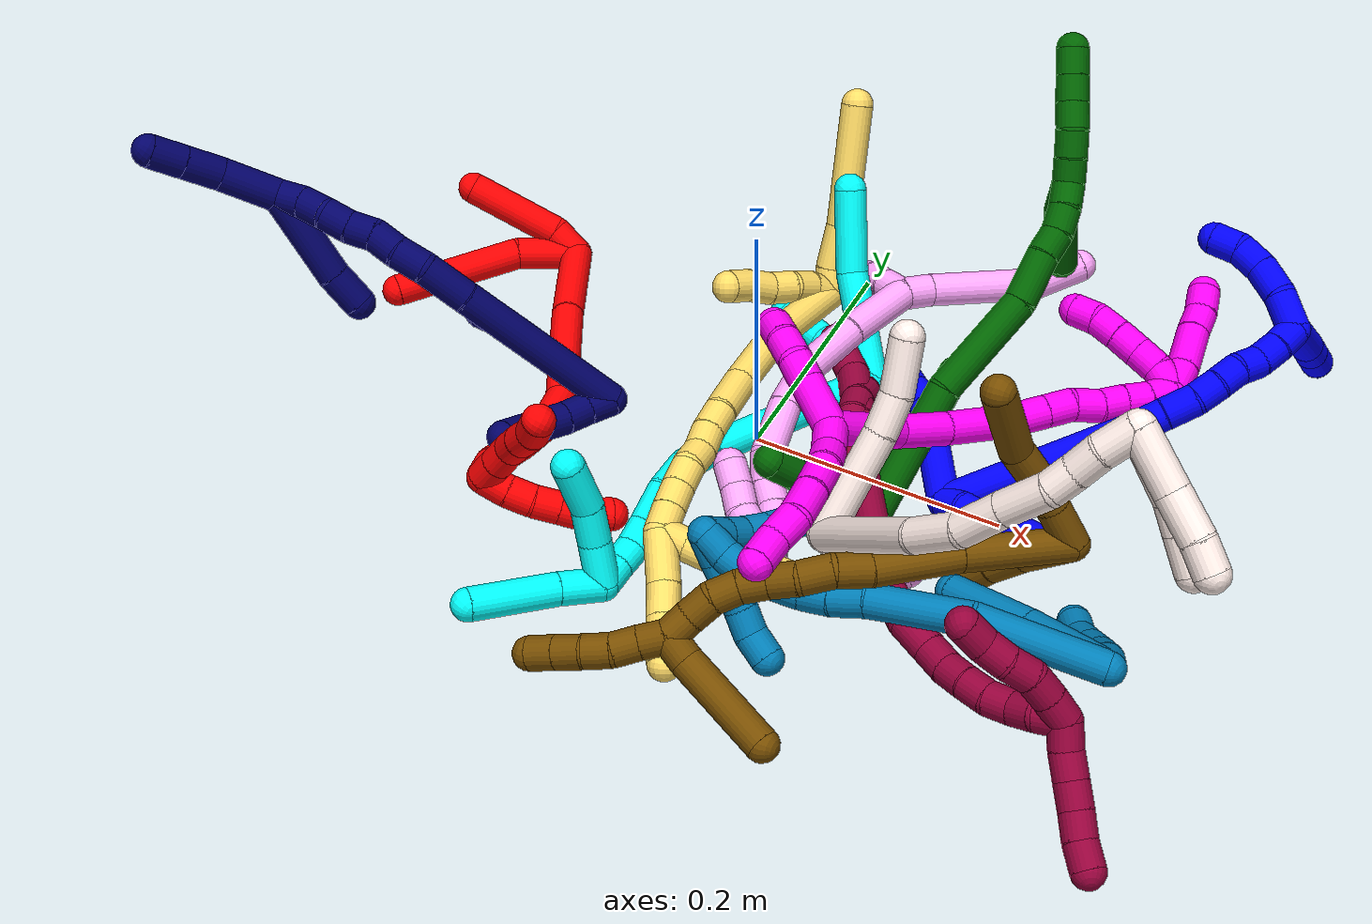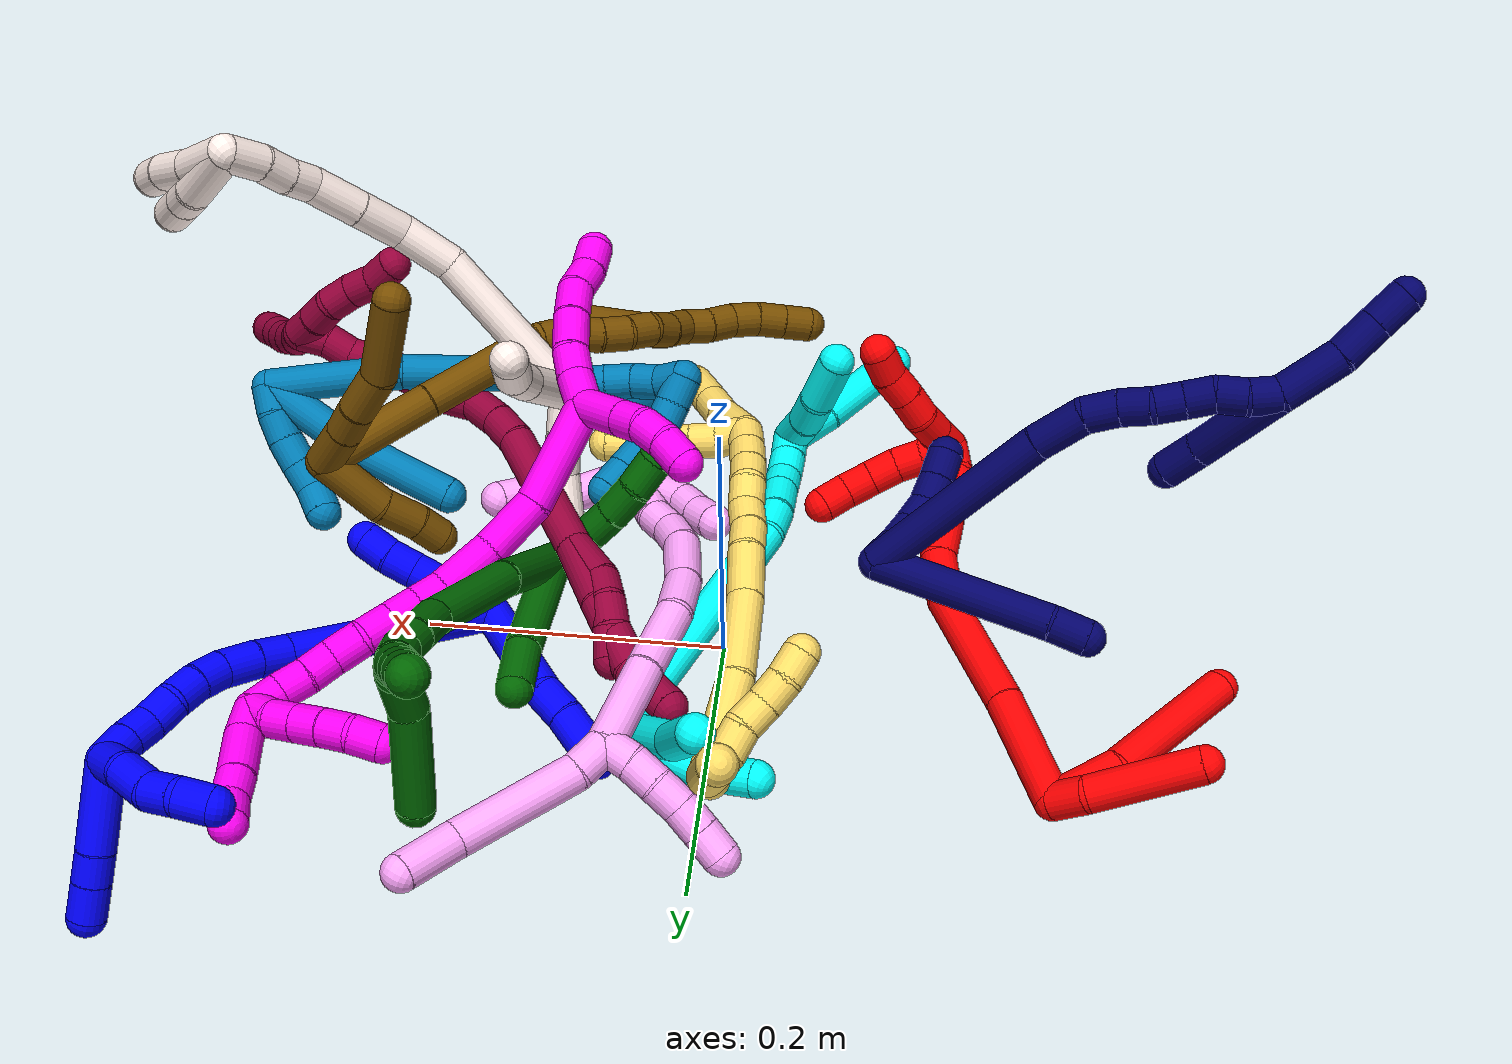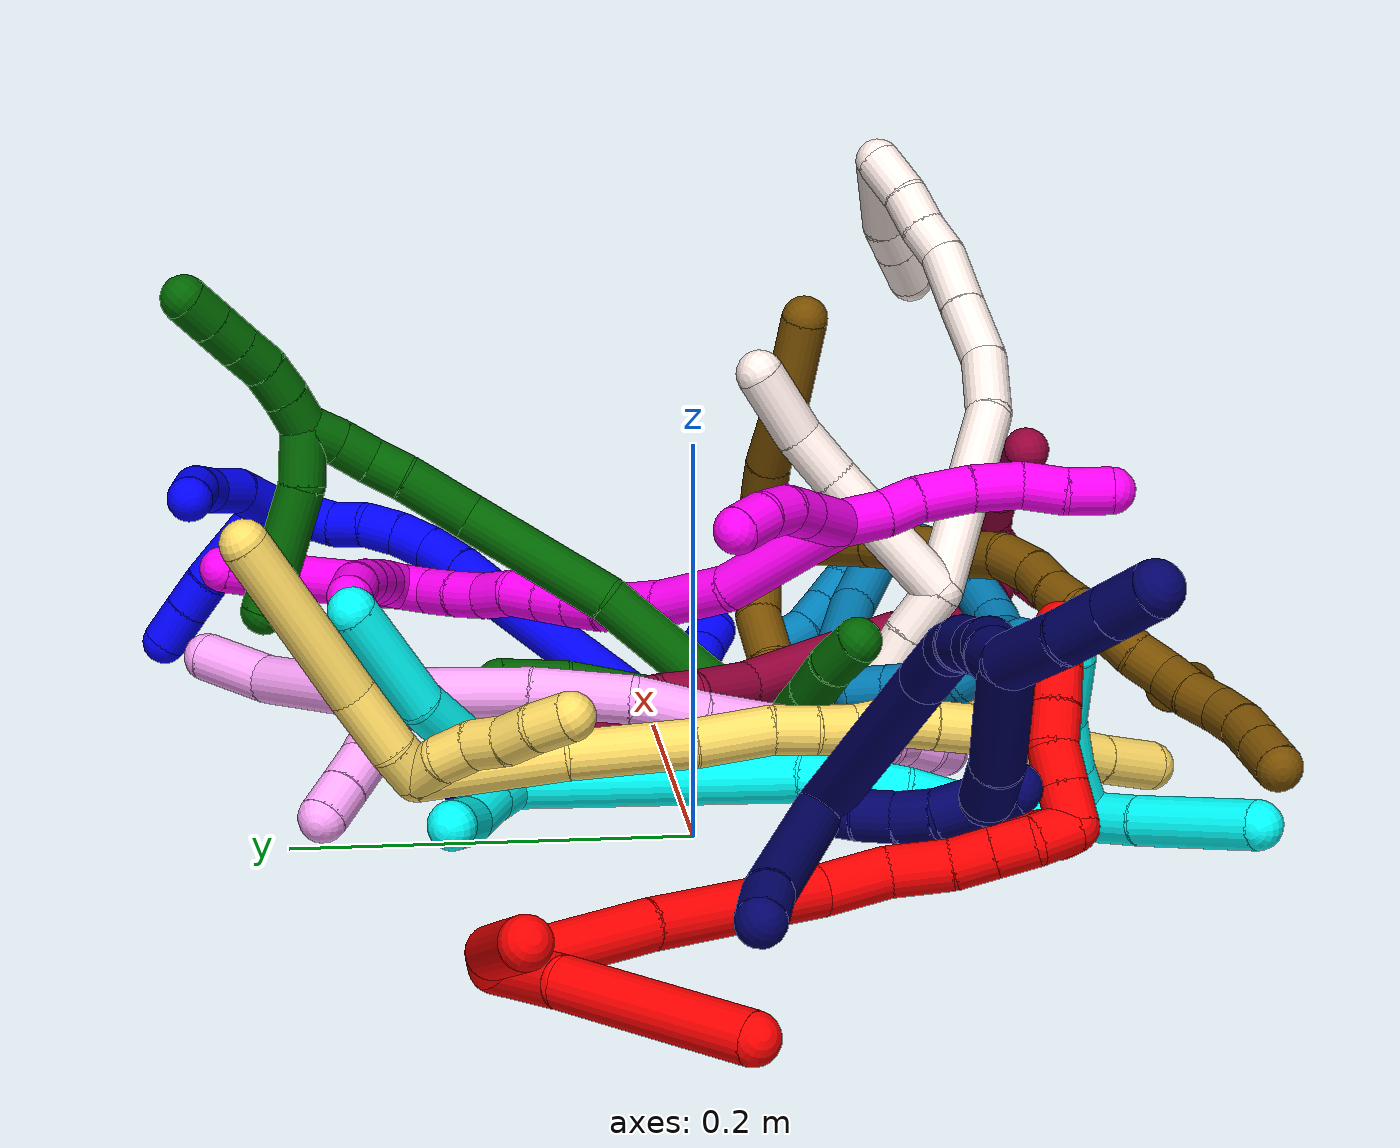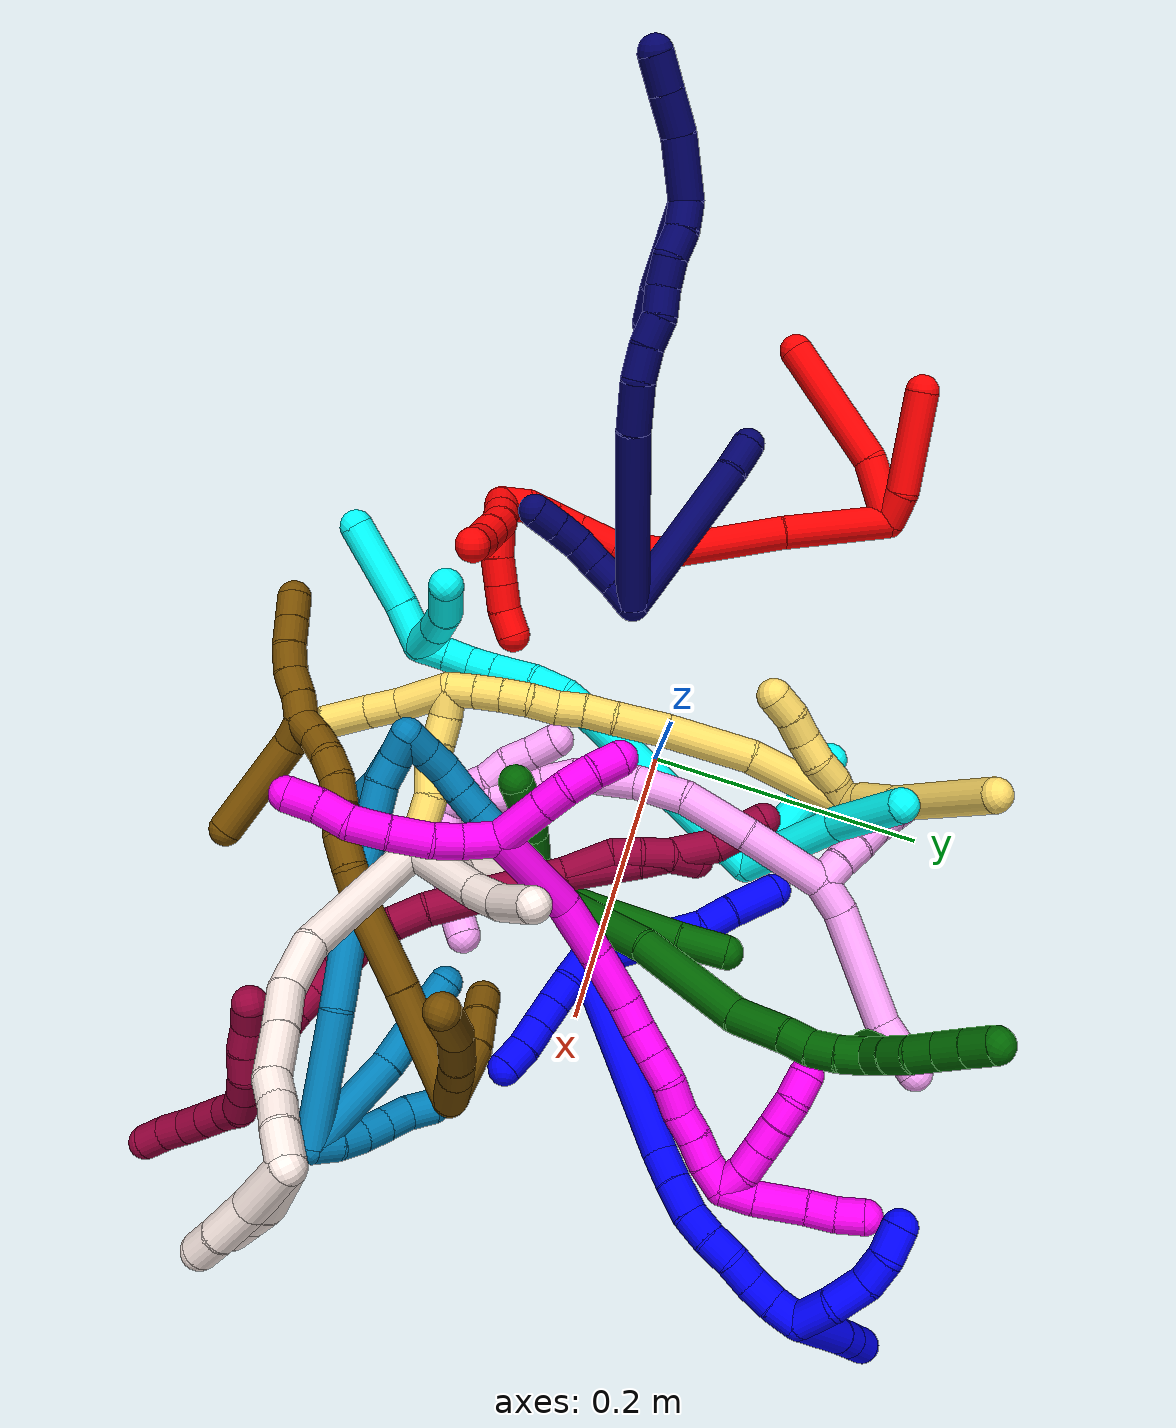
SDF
<sdf version="1.7">
 <world name="default">
  <plugin name="TubeGeneratorPlugin" filename="libtube_generator_plugin.so"/>
  <model name="photoneo_s_sensor">
   <static>1</static>
   <pose>0 0 2 1.57079 1.57079 3.14159</pose>
   <link name="link">
    <inertial><mass>0.1</mass></inertial>
    <sensor name="sensor" type="depth">
     <update_rate>30</update_rate>
     <camera>
      <horizontal_fov>1.22</horizontal_fov>
      <image><width>1920</width><height>1200</height><format>B8G8R8</format></image>
      <clip><near>0.1</near><far>4</far></clip>
      <depth_camera><output>points</output></depth_camera>
     </camera>
     <plugin name="camera_plugin" filename="libgazebo_ros_depth_camera.so">
      <baseline>0.2</baseline>
      <alwaysOn>1</alwaysOn>
      <updateRate>0.0</updateRate>
      <cameraName>camera_ir</cameraName>
      <imageTopicName>/camera/color/image_raw</imageTopicName>
      <cameraInfoTopicName>/camera/color/camera_info</cameraInfoTopicName>
      <depthImageTopicName>/camera/depth/image_raw</depthImageTopicName>
      <depthImageCameraInfoTopicName>/camera/depth/camera_info</depthImageCameraInfoTopicName>
      <pointCloudTopicName>/camera/depth/points</pointCloudTopicName>
      <frameName>fr_optical</frameName>
      <pointCloudCutoff>0.1</pointCloudCutoff>
      <pointCloudCutoffMax>2.0</pointCloudCutoffMax>
      <distortionK1>0</distortionK1>
      <distortionK2>0</distortionK2>
      <distortionK3>0</distortionK3>
      <distortionT1>0</distortionT1>
      <distortionT2>0</distortionT2>
      <CxPrime>0</CxPrime>
      <Cx>0</Cx>
      <Cy>0</Cy>
      <focalLength>0</focalLength>
      <hackBaseline>0</hackBaseline>
     </plugin>
    </sensor>
   </link>
  </model>
  <gravity>0 0 -9.8</gravity>
  <magnetic_field>6e-06 2.3e-05 -4.2e-05</magnetic_field>
  <atmosphere type="adiabatic"/>
  <physics name="default_physics" default="0" type="ode">
   <max_step_size>0.003</max_step_size>
   <real_time_factor>1</real_time_factor>
   <real_time_update_rate>1000</real_time_update_rate>
   <max_contacts>10000</max_contacts>
   <ode>
    <solver>
     <type>quick</type>
     <iters>100</iters>
     <sor>1.3</sor>
     <use_dynamic_moi_rescaling>0</use_dynamic_moi_rescaling>
    </solver>
    <constraints>
     <contact_max_correcting_vel>0</contact_max_correcting_vel>
     <contact_surface_layer>0.001</contact_surface_layer>
     <cfm>0</cfm>
     <erp>0.2</erp>
    </constraints>
   </ode>
  </physics>
  <scene><ambient>0.4 0.4 0.4 1</ambient><background>0.7 0.7 0.7 1</background><shadows>0</shadows></scene>
  <audio><device>default</device></audio>
  <spherical_coordinates>
   <surface_model>EARTH_WGS84</surface_model>
   <latitude_deg>0</latitude_deg>
   <longitude_deg>0</longitude_deg>
   <elevation>0</elevation>
   <heading_deg>0</heading_deg>
  </spherical_coordinates>
  <model name="bin">
   <static>1</static>
   <link name="bottom">
    <collision name="collision-bottom">
     <pose>0 0 -0.01 0 -0 0</pose>
     <geometry><box><size>0.8 0.6 0.02</size></box></geometry>
     <surface>
      <friction><ode><mu>100</mu><mu2>100</mu2></ode></friction>
      <contact><collide_bitmask>65535</collide_bitmask></contact>
     </surface>
    </collision>
   </link>
   <link name="west_wall">
    <collision name="collision-west_wall">
     <pose>-0.41 0 0.1 0 -0 0</pose>
     <geometry><box><size>0.02 0.6 0.2</size></box></geometry>
     <surface>
      <friction><ode><mu>100</mu><mu2>100</mu2></ode></friction>
      <contact><collide_bitmask>65535</collide_bitmask></contact>
     </surface>
    </collision>
   </link>
   <link name="east_wall">
    <collision name="collision-east_wall">
     <pose>0.41 0 0.1 0 -0 0</pose>
     <geometry><box><size>0.02 0.6 0.2</size></box></geometry>
     <surface>
      <friction><ode><mu>100</mu><mu2>100</mu2></ode></friction>
      <contact><collide_bitmask>65535</collide_bitmask></contact>
     </surface>
    </collision>
   </link>
   <link name="south_wall">
    <collision name="collision-south_wall">
     <pose>0 -0.31 0.1 0 -0 0</pose>
     <geometry><box><size>0.8 0.02 0.2</size></box></geometry>
     <surface>
      <friction><ode><mu>100</mu><mu2>100</mu2></ode></friction>
      <contact><collide_bitmask>65535</collide_bitmask></contact>
     </surface>
    </collision>
   </link>
   <link name="north_wall">
    <collision name="collision-north_wall">
     <pose>0 0.31 0.1 0 -0 0</pose>
     <geometry><box><size>0.8 0.02 0.2</size></box></geometry>
     <surface>
      <friction><ode><mu>100</mu><mu2>100</mu2></ode></friction>
      <contact><collide_bitmask>65535</collide_bitmask></contact>
     </surface>
    </collision>
   </link>
  </model>
  <model name="1">
   <static>0</static>
   <link name="1">
    <collision name="collision-cylinder-e_1_2_8">
     <pose>-0.04181 0.01003 -0.0115 -2.42441 -1.22085 2.15789</pose>
     <geometry><cylinder><radius>0.0125</radius><length>0.089016</length></cylinder></geometry>
     <surface>
      <friction><ode><mu>1.16</mu><mu2>1.16</mu2><slip1>0</slip1><slip2>0</slip2></ode></friction>
      <contact><ode><kp>1e+06</kp><kd>1</kd><max_vel>0</max_vel><min_depth>0.001</min_depth></ode></contact>
     </surface>
    </collision>
    <visual name="visual-cylinder-e_1_2_8">
     <pose>-0.04181 0.01003 -0.0115 -2.42441 -1.22085 2.15789</pose>
     <geometry><cylinder><radius>0.0125</radius><length>0.089016</length></cylinder></geometry>
     <material><ambient>0 0 1 1</ambient></material>
    </visual>
    <collision name="collision-cylinder-e_2_8_9">
     <pose>-0.092787 0.023811 -0.029449 -2.6146 -0.887606 2.10936</pose>
     <geometry><cylinder><radius>0.0125</radius><length>0.023637</length></cylinder></geometry>
     <surface>
      <friction><ode><mu>1.16</mu><mu2>1.16</mu2><slip1>0</slip1><slip2>0</slip2></ode></friction>
      <contact><ode><kp>1e+06</kp><kd>1</kd><max_vel>0</max_vel><min_depth>0.001</min_depth></ode></contact>
     </surface>
    </collision>
    <visual name="visual-cylinder-e_2_8_9">
     <pose>-0.092787 0.023811 -0.029449 -2.6146 -0.887606 2.10936</pose>
     <geometry><cylinder><radius>0.0125</radius><length>0.023637</length></cylinder></geometry>
     <material><ambient>0 0 1 1</ambient></material>
    </visual>
    <collision name="collision-cylinder-e_3_9_6">
     <pose>-0.115533 0.035906 -0.045628 -2.43286 -0.814294 1.72341</pose>
     <geometry><cylinder><radius>0.0125</radius><length>0.037347</length></cylinder></geometry>
     <surface>
      <friction><ode><mu>1.16</mu><mu2>1.16</mu2><slip1>0</slip1><slip2>0</slip2></ode></friction>
      <contact><ode><kp>1e+06</kp><kd>1</kd><max_vel>0</max_vel><min_depth>0.001</min_depth></ode></contact>
     </surface>
    </collision>
    <visual name="visual-cylinder-e_3_9_6">
     <pose>-0.115533 0.035906 -0.045628 -2.43286 -0.814294 1.72341</pose>
     <geometry><cylinder><radius>0.0125</radius><length>0.037347</length></cylinder></geometry>
     <material><ambient>0 0 1 1</ambient></material>
    </visual>
    <collision name="collision-cylinder-e_1_2_10">
     <pose>0.004303 -0.002927 0.008539 0.330256 0.444789 0.075333</pose>
     <geometry><cylinder><radius>0.0125</radius><length>0.02</length></cylinder></geometry>
     <surface>
      <friction><ode><mu>1.16</mu><mu2>1.16</mu2><slip1>0</slip1><slip2>0</slip2></ode></friction>
      <contact><ode><kp>1e+06</kp><kd>1</kd><max_vel>0</max_vel><min_depth>0.001</min_depth></ode></contact>
     </surface>
    </collision>
    <visual name="visual-cylinder-e_1_2_10">
     <pose>0.004303 -0.002927 0.008539 0.330256 0.444789 0.075333</pose>
     <geometry><cylinder><radius>0.0125</radius><length>0.02</length></cylinder></geometry>
     <material><ambient>0 0 1 1</ambient></material>
    </visual>
    <collision name="collision-cylinder-e_2_10_11">
     <pose>0.014051 -0.006655 0.025427 0.095513 0.575843 0.028306</pose>
     <geometry><cylinder><radius>0.0125</radius><length>0.02</length></cylinder></geometry>
     <surface>
      <friction><ode><mu>1.16</mu><mu2>1.16</mu2><slip1>0</slip1><slip2>0</slip2></ode></friction>
      <contact><ode><kp>1e+06</kp><kd>1</kd><max_vel>0</max_vel><min_depth>0.001</min_depth></ode></contact>
     </surface>
    </collision>
    <visual name="visual-cylinder-e_2_10_11">
     <pose>0.014051 -0.006655 0.025427 0.095513 0.575843 0.028306</pose>
     <geometry><cylinder><radius>0.0125</radius><length>0.02</length></cylinder></geometry>
     <material><ambient>0 0 1 1</ambient></material>
    </visual>
    <collision name="collision-cylinder-e_3_11_12">
     <pose>0.023944 -0.009445 0.042509 0.22414 0.460946 0.052802</pose>
     <geometry><cylinder><radius>0.0125</radius><length>0.02</length></cylinder></geometry>
     <surface>
      <friction><ode><mu>1.16</mu><mu2>1.16</mu2><slip1>0</slip1><slip2>0</slip2></ode></friction>
      <contact><ode><kp>1e+06</kp><kd>1</kd><max_vel>0</max_vel><min_depth>0.001</min_depth></ode></contact>
     </surface>
    </collision>
    <visual name="visual-cylinder-e_3_11_12">
     <pose>0.023944 -0.009445 0.042509 0.22414 0.460946 0.052802</pose>
     <geometry><cylinder><radius>0.0125</radius><length>0.02</length></cylinder></geometry>
     <material><ambient>0 0 1 1</ambient></material>
    </visual>
    <collision name="collision-cylinder-e_4_12_13">
     <pose>0.032738 -0.013483 0.060012 0.229343 0.449555 0.052656</pose>
     <geometry><cylinder><radius>0.0125</radius><length>0.02</length></cylinder></geometry>
     <surface>
      <friction><ode><mu>1.16</mu><mu2>1.16</mu2><slip1>0</slip1><slip2>0</slip2></ode></friction>
      <contact><ode><kp>1e+06</kp><kd>1</kd><max_vel>0</max_vel><min_depth>0.001</min_depth></ode></contact>
     </surface>
    </collision>
    <visual name="visual-cylinder-e_4_12_13">
     <pose>0.032738 -0.013483 0.060012 0.229343 0.449555 0.052656</pose>
     <geometry><cylinder><radius>0.0125</radius><length>0.02</length></cylinder></geometry>
     <material><ambient>0 0 1 1</ambient></material>
    </visual>
    <collision name="collision-cylinder-e_5_13_5">
     <pose>0.042293 -0.018574 0.076757 0.36461 0.548012 0.103541</pose>
     <geometry><cylinder><radius>0.0125</radius><length>0.02</length></cylinder></geometry>
     <surface>
      <friction><ode><mu>1.16</mu><mu2>1.16</mu2><slip1>0</slip1><slip2>0</slip2></ode></friction>
      <contact><ode><kp>1e+06</kp><kd>1</kd><max_vel>0</max_vel><min_depth>0.001</min_depth></ode></contact>
     </surface>
    </collision>
    <visual name="visual-cylinder-e_5_13_5">
     <pose>0.042293 -0.018574 0.076757 0.36461 0.548012 0.103541</pose>
     <geometry><cylinder><radius>0.0125</radius><length>0.02</length></cylinder></geometry>
     <material><ambient>0 0 1 1</ambient></material>
    </visual>
    <collision name="collision-cylinder-e_1_2_14">
     <pose>-0.025838 0.015245 0.069662 -0.215442 -0.347616 0.03797</pose>
     <geometry><cylinder><radius>0.0125</radius><length>0.151695</length></cylinder></geometry>
     <surface>
      <friction><ode><mu>1.16</mu><mu2>1.16</mu2><slip1>0</slip1><slip2>0</slip2></ode></friction>
      <contact><ode><kp>1e+06</kp><kd>1</kd><max_vel>0</max_vel><min_depth>0.001</min_depth></ode></contact>
     </surface>
    </collision>
    <visual name="visual-cylinder-e_1_2_14">
     <pose>-0.025838 0.015245 0.069662 -0.215442 -0.347616 0.03797</pose>
     <geometry><cylinder><radius>0.0125</radius><length>0.151695</length></cylinder></geometry>
     <material><ambient>0 0 1 1</ambient></material>
    </visual>
    <collision name="collision-cylinder-e_2_14_15">
     <pose>-0.056238 0.032227 0.149427 -0.170321 -0.418738 0.036274</pose>
     <geometry><cylinder><radius>0.0125</radius><length>0.022439</length></cylinder></geometry>
     <surface>
      <friction><ode><mu>1.16</mu><mu2>1.16</mu2><slip1>0</slip1><slip2>0</slip2></ode></friction>
      <contact><ode><kp>1e+06</kp><kd>1</kd><max_vel>0</max_vel><min_depth>0.001</min_depth></ode></contact>
     </surface>
    </collision>
    <visual name="visual-cylinder-e_2_14_15">
     <pose>-0.056238 0.032227 0.149427 -0.170321 -0.418738 0.036274</pose>
     <geometry><cylinder><radius>0.0125</radius><length>0.022439</length></cylinder></geometry>
     <material><ambient>0 0 1 1</ambient></material>
    </visual>
    <collision name="collision-cylinder-e_3_15_16">
     <pose>-0.066114 0.036924 0.1705 -0.26348 -0.437446 0.05889</pose>
     <geometry><cylinder><radius>0.0125</radius><length>0.02509</length></cylinder></geometry>
     <surface>
      <friction><ode><mu>1.16</mu><mu2>1.16</mu2><slip1>0</slip1><slip2>0</slip2></ode></friction>
      <contact><ode><kp>1e+06</kp><kd>1</kd><max_vel>0</max_vel><min_depth>0.001</min_depth></ode></contact>
     </surface>
    </collision>
    <visual name="visual-cylinder-e_3_15_16">
     <pose>-0.066114 0.036924 0.1705 -0.26348 -0.437446 0.05889</pose>
     <geometry><cylinder><radius>0.0125</radius><length>0.02509</length></cylinder></geometry>
     <material><ambient>0 0 1 1</ambient></material>
    </visual>
    <collision name="collision-cylinder-e_4_16_17">
     <pose>-0.077574 0.042925 0.189148 -0.377214 -0.639879 0.126315</pose>
     <geometry><cylinder><radius>0.0125</radius><length>0.020585</length></cylinder></geometry>
     <surface>
      <friction><ode><mu>1.16</mu><mu2>1.16</mu2><slip1>0</slip1><slip2>0</slip2></ode></friction>
      <contact><ode><kp>1e+06</kp><kd>1</kd><max_vel>0</max_vel><min_depth>0.001</min_depth></ode></contact>
     </surface>
    </collision>
    <visual name="visual-cylinder-e_4_16_17">
     <pose>-0.077574 0.042925 0.189148 -0.377214 -0.639879 0.126315</pose>
     <geometry><cylinder><radius>0.0125</radius><length>0.020585</length></cylinder></geometry>
     <material><ambient>0 0 1 1</ambient></material>
    </visual>
    <collision name="collision-cylinder-e_5_17_18">
     <pose>-0.090198 0.050087 0.203318 -0.565397 -0.699918 0.211249</pose>
     <geometry><cylinder><radius>0.0125</radius><length>0.020111</length></cylinder></geometry>
     <surface>
      <friction><ode><mu>1.16</mu><mu2>1.16</mu2><slip1>0</slip1><slip2>0</slip2></ode></friction>
      <contact><ode><kp>1e+06</kp><kd>1</kd><max_vel>0</max_vel><min_depth>0.001</min_depth></ode></contact>
     </surface>
    </collision>
    <visual name="visual-cylinder-e_5_17_18">
     <pose>-0.090198 0.050087 0.203318 -0.565397 -0.699918 0.211249</pose>
     <geometry><cylinder><radius>0.0125</radius><length>0.020111</length></cylinder></geometry>
     <material><ambient>0 0 1 1</ambient></material>
    </visual>
    <collision name="collision-cylinder-e_6_18_19">
     <pose>-0.10119 0.060599 0.216102 -0.793482 -0.466508 0.198417</pose>
     <geometry><cylinder><radius>0.0125</radius><length>0.020079</length></cylinder></geometry>
     <surface>
      <friction><ode><mu>1.16</mu><mu2>1.16</mu2><slip1>0</slip1><slip2>0</slip2></ode></friction>
      <contact><ode><kp>1e+06</kp><kd>1</kd><max_vel>0</max_vel><min_depth>0.001</min_depth></ode></contact>
     </surface>
    </collision>
    <visual name="visual-cylinder-e_6_18_19">
     <pose>-0.10119 0.060599 0.216102 -0.793482 -0.466508 0.198417</pose>
     <geometry><cylinder><radius>0.0125</radius><length>0.020079</length></cylinder></geometry>
     <material><ambient>0 0 1 1</ambient></material>
    </visual>
    <collision name="collision-cylinder-e_7_19_20">
     <pose>-0.112249 0.070884 0.228873 -0.54087 -0.713266 0.205839</pose>
     <geometry><cylinder><radius>0.0125</radius><length>0.02</length></cylinder></geometry>
     <surface>
      <friction><ode><mu>1.16</mu><mu2>1.16</mu2><slip1>0</slip1><slip2>0</slip2></ode></friction>
      <contact><ode><kp>1e+06</kp><kd>1</kd><max_vel>0</max_vel><min_depth>0.001</min_depth></ode></contact>
     </surface>
    </collision>
    <visual name="visual-cylinder-e_7_19_20">
     <pose>-0.112249 0.070884 0.228873 -0.54087 -0.713266 0.205839</pose>
     <geometry><cylinder><radius>0.0125</radius><length>0.02</length></cylinder></geometry>
     <material><ambient>0 0 1 1</ambient></material>
    </visual>
    <collision name="collision-cylinder-e_8_20_1">
     <pose>-0.126109 0.078849 0.240824 -0.64001 -0.820738 0.286386</pose>
     <geometry><cylinder><radius>0.0125</radius><length>0.02</length></cylinder></geometry>
     <surface>
      <friction><ode><mu>1.16</mu><mu2>1.16</mu2><slip1>0</slip1><slip2>0</slip2></ode></friction>
      <contact><ode><kp>1e+06</kp><kd>1</kd><max_vel>0</max_vel><min_depth>0.001</min_depth></ode></contact>
     </surface>
    </collision>
    <visual name="visual-cylinder-e_8_20_1">
     <pose>-0.126109 0.078849 0.240824 -0.64001 -0.820738 0.286386</pose>
     <geometry><cylinder><radius>0.0125</radius><length>0.02</length></cylinder></geometry>
     <material><ambient>0 0 1 1</ambient></material>
    </visual>
    <collision name="collision-cylinder-e_1_1_21">
     <pose>-0.137477 0.110593 0.244527 -1.63447 -0.145106 0.154616</pose>
     <geometry><cylinder><radius>0.0125</radius><length>0.056047</length></cylinder></geometry>
     <surface>
      <friction><ode><mu>1.16</mu><mu2>1.16</mu2><slip1>0</slip1><slip2>0</slip2></ode></friction>
      <contact><ode><kp>1e+06</kp><kd>1</kd><max_vel>0</max_vel><min_depth>0.001</min_depth></ode></contact>
     </surface>
    </collision>
    <visual name="visual-cylinder-e_1_1_21">
     <pose>-0.137477 0.110593 0.244527 -1.63447 -0.145106 0.154616</pose>
     <geometry><cylinder><radius>0.0125</radius><length>0.056047</length></cylinder></geometry>
     <material><ambient>0 0 1 1</ambient></material>
    </visual>
    <collision name="collision-cylinder-e_2_21_22">
     <pose>-0.142103 0.148348 0.242173 -1.62925 -0.056695 0.060108</pose>
     <geometry><cylinder><radius>0.0125</radius><length>0.020231</length></cylinder></geometry>
     <surface>
      <friction><ode><mu>1.16</mu><mu2>1.16</mu2><slip1>0</slip1><slip2>0</slip2></ode></friction>
      <contact><ode><kp>1e+06</kp><kd>1</kd><max_vel>0</max_vel><min_depth>0.001</min_depth></ode></contact>
     </surface>
    </collision>
    <visual name="visual-cylinder-e_2_21_22">
     <pose>-0.142103 0.148348 0.242173 -1.62925 -0.056695 0.060108</pose>
     <geometry><cylinder><radius>0.0125</radius><length>0.020231</length></cylinder></geometry>
     <material><ambient>0 0 1 1</ambient></material>
    </visual>
    <collision name="collision-cylinder-e_3_22_4">
     <pose>-0.143184 0.170261 0.240922 -1.62657 -0.042836 0.045294</pose>
     <geometry><cylinder><radius>0.0125</radius><length>0.023721</length></cylinder></geometry>
     <surface>
      <friction><ode><mu>1.16</mu><mu2>1.16</mu2><slip1>0</slip1><slip2>0</slip2></ode></friction>
      <contact><ode><kp>1e+06</kp><kd>1</kd><max_vel>0</max_vel><min_depth>0.001</min_depth></ode></contact>
     </surface>
    </collision>
    <visual name="visual-cylinder-e_3_22_4">
     <pose>-0.143184 0.170261 0.240922 -1.62657 -0.042836 0.045294</pose>
     <geometry><cylinder><radius>0.0125</radius><length>0.023721</length></cylinder></geometry>
     <material><ambient>0 0 1 1</ambient></material>
    </visual>
    <collision name="collision-cylinder-e_1_1_23">
     <pose>-0.146823 0.079724 0.242182 2.48066 -1.20017 -2.21215</pose>
     <geometry><cylinder><radius>0.0125</radius><length>0.028748</length></cylinder></geometry>
     <surface>
      <friction><ode><mu>1.16</mu><mu2>1.16</mu2><slip1>0</slip1><slip2>0</slip2></ode></friction>
      <contact><ode><kp>1e+06</kp><kd>1</kd><max_vel>0</max_vel><min_depth>0.001</min_depth></ode></contact>
     </surface>
    </collision>
    <visual name="visual-cylinder-e_1_1_23">
     <pose>-0.146823 0.079724 0.242182 2.48066 -1.20017 -2.21215</pose>
     <geometry><cylinder><radius>0.0125</radius><length>0.028748</length></cylinder></geometry>
     <material><ambient>0 0 1 1</ambient></material>
    </visual>
    <collision name="collision-cylinder-e_2_23_24">
     <pose>-0.172291 0.076541 0.231347 -3.13965 -1.06244 3.13828</pose>
     <geometry><cylinder><radius>0.0125</radius><length>0.027634</length></cylinder></geometry>
     <surface>
      <friction><ode><mu>1.16</mu><mu2>1.16</mu2><slip1>0</slip1><slip2>0</slip2></ode></friction>
      <contact><ode><kp>1e+06</kp><kd>1</kd><max_vel>0</max_vel><min_depth>0.001</min_depth></ode></contact>
     </surface>
    </collision>
    <visual name="visual-cylinder-e_2_23_24">
     <pose>-0.172291 0.076541 0.231347 -3.13965 -1.06244 3.13828</pose>
     <geometry><cylinder><radius>0.0125</radius><length>0.027634</length></cylinder></geometry>
     <material><ambient>0 0 1 1</ambient></material>
    </visual>
    <collision name="collision-cylinder-e_3_24_25">
     <pose>-0.192003 0.073938 0.217559 2.78684 -0.792688 -2.33218</pose>
     <geometry><cylinder><radius>0.0125</radius><length>0.021459</length></cylinder></geometry>
     <surface>
      <friction><ode><mu>1.16</mu><mu2>1.16</mu2><slip1>0</slip1><slip2>0</slip2></ode></friction>
      <contact><ode><kp>1e+06</kp><kd>1</kd><max_vel>0</max_vel><min_depth>0.001</min_depth></ode></contact>
     </surface>
    </collision>
    <visual name="visual-cylinder-e_3_24_25">
     <pose>-0.192003 0.073938 0.217559 2.78684 -0.792688 -2.33218</pose>
     <geometry><cylinder><radius>0.0125</radius><length>0.021459</length></cylinder></geometry>
     <material><ambient>0 0 1 1</ambient></material>
    </visual>
    <collision name="collision-cylinder-e_4_25_3">
     <pose>-0.205102 0.070378 0.2009 3.04353 -0.514986 -2.77312</pose>
     <geometry><cylinder><radius>0.0125</radius><length>0.022159</length></cylinder></geometry>
     <surface>
      <friction><ode><mu>1.16</mu><mu2>1.16</mu2><slip1>0</slip1><slip2>0</slip2></ode></friction>
      <contact><ode><kp>1e+06</kp><kd>1</kd><max_vel>0</max_vel><min_depth>0.001</min_depth></ode></contact>
     </surface>
    </collision>
    <visual name="visual-cylinder-e_4_25_3">
     <pose>-0.205102 0.070378 0.2009 3.04353 -0.514986 -2.77312</pose>
     <geometry><cylinder><radius>0.0125</radius><length>0.022159</length></cylinder></geometry>
     <material><ambient>0 0 1 1</ambient></material>
    </visual>
    <collision name="collision-sphere-3">
     <pose>-0.210559 0.069434 0.191304 0 -0 0</pose>
     <geometry><sphere><radius>0.0125</radius></sphere></geometry>
     <surface>
      <friction><ode><mu>1.16</mu><mu2>1.16</mu2><slip1>0</slip1><slip2>0</slip2></ode></friction>
      <contact><ode><kp>1e+06</kp><kd>1</kd><max_vel>0</max_vel><min_depth>0.001</min_depth></ode></contact>
     </surface>
    </collision>
    <visual name="visual-sphere-3">
     <pose>-0.210559 0.069434 0.191304 0 -0 0</pose>
     <geometry><sphere><radius>0.0125</radius></sphere></geometry>
     <material><ambient>0 0 1 1</ambient></material>
    </visual>
    <collision name="collision-sphere-25">
     <pose>-0.199645 0.071322 0.210496 0 -0 0</pose>
     <geometry><sphere><radius>0.0125</radius></sphere></geometry>
     <surface>
      <friction><ode><mu>1.16</mu><mu2>1.16</mu2><slip1>0</slip1><slip2>0</slip2></ode></friction>
      <contact><ode><kp>1e+06</kp><kd>1</kd><max_vel>0</max_vel><min_depth>0.001</min_depth></ode></contact>
     </surface>
    </collision>
    <visual name="visual-sphere-25">
     <pose>-0.199645 0.071322 0.210496 0 -0 0</pose>
     <geometry><sphere><radius>0.0125</radius></sphere></geometry>
     <material><ambient>0 0 1 1</ambient></material>
    </visual>
    <collision name="collision-sphere-24">
     <pose>-0.184361 0.076554 0.224621 0 -0 0</pose>
     <geometry><sphere><radius>0.0125</radius></sphere></geometry>
     <surface>
      <friction><ode><mu>1.16</mu><mu2>1.16</mu2><slip1>0</slip1><slip2>0</slip2></ode></friction>
      <contact><ode><kp>1e+06</kp><kd>1</kd><max_vel>0</max_vel><min_depth>0.001</min_depth></ode></contact>
     </surface>
    </collision>
    <visual name="visual-sphere-24">
     <pose>-0.184361 0.076554 0.224621 0 -0 0</pose>
     <geometry><sphere><radius>0.0125</radius></sphere></geometry>
     <material><ambient>0 0 1 1</ambient></material>
    </visual>
    <collision name="collision-sphere-23">
     <pose>-0.160221 0.076528 0.238072 0 -0 0</pose>
     <geometry><sphere><radius>0.0125</radius></sphere></geometry>
     <surface>
      <friction><ode><mu>1.16</mu><mu2>1.16</mu2><slip1>0</slip1><slip2>0</slip2></ode></friction>
      <contact><ode><kp>1e+06</kp><kd>1</kd><max_vel>0</max_vel><min_depth>0.001</min_depth></ode></contact>
     </surface>
    </collision>
    <visual name="visual-sphere-23">
     <pose>-0.160221 0.076528 0.238072 0 -0 0</pose>
     <geometry><sphere><radius>0.0125</radius></sphere></geometry>
     <material><ambient>0 0 1 1</ambient></material>
    </visual>
    <collision name="collision-sphere-4">
     <pose>-0.143692 0.182093 0.240262 0 -0 0</pose>
     <geometry><sphere><radius>0.0125</radius></sphere></geometry>
     <surface>
      <friction><ode><mu>1.16</mu><mu2>1.16</mu2><slip1>0</slip1><slip2>0</slip2></ode></friction>
      <contact><ode><kp>1e+06</kp><kd>1</kd><max_vel>0</max_vel><min_depth>0.001</min_depth></ode></contact>
     </surface>
    </collision>
    <visual name="visual-sphere-4">
     <pose>-0.143692 0.182093 0.240262 0 -0 0</pose>
     <geometry><sphere><radius>0.0125</radius></sphere></geometry>
     <material><ambient>0 0 1 1</ambient></material>
    </visual>
    <collision name="collision-sphere-22">
     <pose>-0.142676 0.15843 0.241583 0 -0 0</pose>
     <geometry><sphere><radius>0.0125</radius></sphere></geometry>
     <surface>
      <friction><ode><mu>1.16</mu><mu2>1.16</mu2><slip1>0</slip1><slip2>0</slip2></ode></friction>
      <contact><ode><kp>1e+06</kp><kd>1</kd><max_vel>0</max_vel><min_depth>0.001</min_depth></ode></contact>
     </surface>
    </collision>
    <visual name="visual-sphere-22">
     <pose>-0.142676 0.15843 0.241583 0 -0 0</pose>
     <geometry><sphere><radius>0.0125</radius></sphere></geometry>
     <material><ambient>0 0 1 1</ambient></material>
    </visual>
    <collision name="collision-sphere-21">
     <pose>-0.14153 0.138266 0.242763 0 -0 0</pose>
     <geometry><sphere><radius>0.0125</radius></sphere></geometry>
     <surface>
      <friction><ode><mu>1.16</mu><mu2>1.16</mu2><slip1>0</slip1><slip2>0</slip2></ode></friction>
      <contact><ode><kp>1e+06</kp><kd>1</kd><max_vel>0</max_vel><min_depth>0.001</min_depth></ode></contact>
     </surface>
    </collision>
    <visual name="visual-sphere-21">
     <pose>-0.14153 0.138266 0.242763 0 -0 0</pose>
     <geometry><sphere><radius>0.0125</radius></sphere></geometry>
     <material><ambient>0 0 1 1</ambient></material>
    </visual>
    <collision name="collision-sphere-1">
     <pose>-0.133425 0.08292 0.246292 0 -0 0</pose>
     <geometry><sphere><radius>0.0125</radius></sphere></geometry>
     <surface>
      <friction><ode><mu>1.16</mu><mu2>1.16</mu2><slip1>0</slip1><slip2>0</slip2></ode></friction>
      <contact><ode><kp>1e+06</kp><kd>1</kd><max_vel>0</max_vel><min_depth>0.001</min_depth></ode></contact>
     </surface>
    </collision>
    <visual name="visual-sphere-1">
     <pose>-0.133425 0.08292 0.246292 0 -0 0</pose>
     <geometry><sphere><radius>0.0125</radius></sphere></geometry>
     <material><ambient>0 0 1 1</ambient></material>
    </visual>
    <collision name="collision-sphere-11">
     <pose>0.019496 -0.007454 0.033777 0 -0 0</pose>
     <geometry><sphere><radius>0.0125</radius></sphere></geometry>
     <surface>
      <friction><ode><mu>1.16</mu><mu2>1.16</mu2><slip1>0</slip1><slip2>0</slip2></ode></friction>
      <contact><ode><kp>1e+06</kp><kd>1</kd><max_vel>0</max_vel><min_depth>0.001</min_depth></ode></contact>
     </surface>
    </collision>
    <visual name="visual-sphere-11">
     <pose>0.019496 -0.007454 0.033777 0 -0 0</pose>
     <geometry><sphere><radius>0.0125</radius></sphere></geometry>
     <material><ambient>0 0 1 1</ambient></material>
    </visual>
    <collision name="collision-sphere-10">
     <pose>0.008605 -0.005855 0.017078 0 -0 0</pose>
     <geometry><sphere><radius>0.0125</radius></sphere></geometry>
     <surface>
      <friction><ode><mu>1.16</mu><mu2>1.16</mu2><slip1>0</slip1><slip2>0</slip2></ode></friction>
      <contact><ode><kp>1e+06</kp><kd>1</kd><max_vel>0</max_vel><min_depth>0.001</min_depth></ode></contact>
     </surface>
    </collision>
    <visual name="visual-sphere-10">
     <pose>0.008605 -0.005855 0.017078 0 -0 0</pose>
     <geometry><sphere><radius>0.0125</radius></sphere></geometry>
     <material><ambient>0 0 1 1</ambient></material>
    </visual>
    <collision name="collision-sphere-6">
     <pose>-0.129113 0.044248 -0.055359 0 -0 0</pose>
     <geometry><sphere><radius>0.0125</radius></sphere></geometry>
     <surface>
      <friction><ode><mu>1.16</mu><mu2>1.16</mu2><slip1>0</slip1><slip2>0</slip2></ode></friction>
      <contact><ode><kp>1e+06</kp><kd>1</kd><max_vel>0</max_vel><min_depth>0.001</min_depth></ode></contact>
     </surface>
    </collision>
    <visual name="visual-sphere-6">
     <pose>-0.129113 0.044248 -0.055359 0 -0 0</pose>
     <geometry><sphere><radius>0.0125</radius></sphere></geometry>
     <material><ambient>0 0 1 1</ambient></material>
    </visual>
    <collision name="collision-sphere-9">
     <pose>-0.101953 0.027564 -0.035898 0 -0 0</pose>
     <geometry><sphere><radius>0.0125</radius></sphere></geometry>
     <surface>
      <friction><ode><mu>1.16</mu><mu2>1.16</mu2><slip1>0</slip1><slip2>0</slip2></ode></friction>
      <contact><ode><kp>1e+06</kp><kd>1</kd><max_vel>0</max_vel><min_depth>0.001</min_depth></ode></contact>
     </surface>
    </collision>
    <visual name="visual-sphere-9">
     <pose>-0.101953 0.027564 -0.035898 0 -0 0</pose>
     <geometry><sphere><radius>0.0125</radius></sphere></geometry>
     <material><ambient>0 0 1 1</ambient></material>
    </visual>
    <collision name="collision-sphere-2">
     <geometry><sphere><radius>0.0125</radius></sphere></geometry>
     <surface>
      <friction><ode><mu>1.16</mu><mu2>1.16</mu2><slip1>0</slip1><slip2>0</slip2></ode></friction>
      <contact><ode><kp>1e+06</kp><kd>1</kd><max_vel>0</max_vel><min_depth>0.001</min_depth></ode></contact>
     </surface>
    </collision>
    <visual name="visual-sphere-2">
     <geometry><sphere><radius>0.0125</radius></sphere></geometry>
     <material><ambient>0 0 1 1</ambient></material>
    </visual>
    <collision name="collision-sphere-19">
     <pose>-0.105706 0.06699 0.22239 0 -0 0</pose>
     <geometry><sphere><radius>0.0125</radius></sphere></geometry>
     <surface>
      <friction><ode><mu>1.16</mu><mu2>1.16</mu2><slip1>0</slip1><slip2>0</slip2></ode></friction>
      <contact><ode><kp>1e+06</kp><kd>1</kd><max_vel>0</max_vel><min_depth>0.001</min_depth></ode></contact>
     </surface>
    </collision>
    <visual name="visual-sphere-19">
     <pose>-0.105706 0.06699 0.22239 0 -0 0</pose>
     <geometry><sphere><radius>0.0125</radius></sphere></geometry>
     <material><ambient>0 0 1 1</ambient></material>
    </visual>
    <collision name="collision-sphere-8">
     <pose>-0.083621 0.020059 -0.023001 0 -0 0</pose>
     <geometry><sphere><radius>0.0125</radius></sphere></geometry>
     <surface>
      <friction><ode><mu>1.16</mu><mu2>1.16</mu2><slip1>0</slip1><slip2>0</slip2></ode></friction>
      <contact><ode><kp>1e+06</kp><kd>1</kd><max_vel>0</max_vel><min_depth>0.001</min_depth></ode></contact>
     </surface>
    </collision>
    <visual name="visual-sphere-8">
     <pose>-0.083621 0.020059 -0.023001 0 -0 0</pose>
     <geometry><sphere><radius>0.0125</radius></sphere></geometry>
     <material><ambient>0 0 1 1</ambient></material>
    </visual>
    <collision name="collision-sphere-12">
     <pose>0.028392 -0.011436 0.051241 0 -0 0</pose>
     <geometry><sphere><radius>0.0125</radius></sphere></geometry>
     <surface>
      <friction><ode><mu>1.16</mu><mu2>1.16</mu2><slip1>0</slip1><slip2>0</slip2></ode></friction>
      <contact><ode><kp>1e+06</kp><kd>1</kd><max_vel>0</max_vel><min_depth>0.001</min_depth></ode></contact>
     </surface>
    </collision>
    <visual name="visual-sphere-12">
     <pose>0.028392 -0.011436 0.051241 0 -0 0</pose>
     <geometry><sphere><radius>0.0125</radius></sphere></geometry>
     <material><ambient>0 0 1 1</ambient></material>
    </visual>
    <collision name="collision-sphere-13">
     <pose>0.037083 -0.015531 0.068782 0 -0 0</pose>
     <geometry><sphere><radius>0.0125</radius></sphere></geometry>
     <surface>
      <friction><ode><mu>1.16</mu><mu2>1.16</mu2><slip1>0</slip1><slip2>0</slip2></ode></friction>
      <contact><ode><kp>1e+06</kp><kd>1</kd><max_vel>0</max_vel><min_depth>0.001</min_depth></ode></contact>
     </surface>
    </collision>
    <visual name="visual-sphere-13">
     <pose>0.037083 -0.015531 0.068782 0 -0 0</pose>
     <geometry><sphere><radius>0.0125</radius></sphere></geometry>
     <material><ambient>0 0 1 1</ambient></material>
    </visual>
    <collision name="collision-sphere-5">
     <pose>0.047503 -0.021618 0.084731 0 -0 0</pose>
     <geometry><sphere><radius>0.0125</radius></sphere></geometry>
     <surface>
      <friction><ode><mu>1.16</mu><mu2>1.16</mu2><slip1>0</slip1><slip2>0</slip2></ode></friction>
      <contact><ode><kp>1e+06</kp><kd>1</kd><max_vel>0</max_vel><min_depth>0.001</min_depth></ode></contact>
     </surface>
    </collision>
    <visual name="visual-sphere-5">
     <pose>0.047503 -0.021618 0.084731 0 -0 0</pose>
     <geometry><sphere><radius>0.0125</radius></sphere></geometry>
     <material><ambient>0 0 1 1</ambient></material>
    </visual>
    <collision name="collision-sphere-14">
     <pose>-0.051676 0.03049 0.139325 0 -0 0</pose>
     <geometry><sphere><radius>0.0125</radius></sphere></geometry>
     <surface>
      <friction><ode><mu>1.16</mu><mu2>1.16</mu2><slip1>0</slip1><slip2>0</slip2></ode></friction>
      <contact><ode><kp>1e+06</kp><kd>1</kd><max_vel>0</max_vel><min_depth>0.001</min_depth></ode></contact>
     </surface>
    </collision>
    <visual name="visual-sphere-14">
     <pose>-0.051676 0.03049 0.139325 0 -0 0</pose>
     <geometry><sphere><radius>0.0125</radius></sphere></geometry>
     <material><ambient>0 0 1 1</ambient></material>
    </visual>
    <collision name="collision-sphere-15">
     <pose>-0.0608 0.033964 0.159529 0 -0 0</pose>
     <geometry><sphere><radius>0.0125</radius></sphere></geometry>
     <surface>
      <friction><ode><mu>1.16</mu><mu2>1.16</mu2><slip1>0</slip1><slip2>0</slip2></ode></friction>
      <contact><ode><kp>1e+06</kp><kd>1</kd><max_vel>0</max_vel><min_depth>0.001</min_depth></ode></contact>
     </surface>
    </collision>
    <visual name="visual-sphere-15">
     <pose>-0.0608 0.033964 0.159529 0 -0 0</pose>
     <geometry><sphere><radius>0.0125</radius></sphere></geometry>
     <material><ambient>0 0 1 1</ambient></material>
    </visual>
    <collision name="collision-sphere-16">
     <pose>-0.071429 0.039884 0.181472 0 -0 0</pose>
     <geometry><sphere><radius>0.0125</radius></sphere></geometry>
     <surface>
      <friction><ode><mu>1.16</mu><mu2>1.16</mu2><slip1>0</slip1><slip2>0</slip2></ode></friction>
      <contact><ode><kp>1e+06</kp><kd>1</kd><max_vel>0</max_vel><min_depth>0.001</min_depth></ode></contact>
     </surface>
    </collision>
    <visual name="visual-sphere-16">
     <pose>-0.071429 0.039884 0.181472 0 -0 0</pose>
     <geometry><sphere><radius>0.0125</radius></sphere></geometry>
     <material><ambient>0 0 1 1</ambient></material>
    </visual>
    <collision name="collision-sphere-17">
     <pose>-0.08372 0.045966 0.196824 0 -0 0</pose>
     <geometry><sphere><radius>0.0125</radius></sphere></geometry>
     <surface>
      <friction><ode><mu>1.16</mu><mu2>1.16</mu2><slip1>0</slip1><slip2>0</slip2></ode></friction>
      <contact><ode><kp>1e+06</kp><kd>1</kd><max_vel>0</max_vel><min_depth>0.001</min_depth></ode></contact>
     </surface>
    </collision>
    <visual name="visual-sphere-17">
     <pose>-0.08372 0.045966 0.196824 0 -0 0</pose>
     <geometry><sphere><radius>0.0125</radius></sphere></geometry>
     <material><ambient>0 0 1 1</ambient></material>
    </visual>
    <collision name="collision-sphere-18">
     <pose>-0.096675 0.054207 0.209813 0 -0 0</pose>
     <geometry><sphere><radius>0.0125</radius></sphere></geometry>
     <surface>
      <friction><ode><mu>1.16</mu><mu2>1.16</mu2><slip1>0</slip1><slip2>0</slip2></ode></friction>
      <contact><ode><kp>1e+06</kp><kd>1</kd><max_vel>0</max_vel><min_depth>0.001</min_depth></ode></contact>
     </surface>
    </collision>
    <visual name="visual-sphere-18">
     <pose>-0.096675 0.054207 0.209813 0 -0 0</pose>
     <geometry><sphere><radius>0.0125</radius></sphere></geometry>
     <material><ambient>0 0 1 1</ambient></material>
    </visual>
    <collision name="collision-sphere-20">
     <pose>-0.118792 0.074778 0.235356 0 -0 0</pose>
     <geometry><sphere><radius>0.0125</radius></sphere></geometry>
     <surface>
      <friction><ode><mu>1.16</mu><mu2>1.16</mu2><slip1>0</slip1><slip2>0</slip2></ode></friction>
      <contact><ode><kp>1e+06</kp><kd>1</kd><max_vel>0</max_vel><min_depth>0.001</min_depth></ode></contact>
     </surface>
    </collision>
    <visual name="visual-sphere-20">
     <pose>-0.118792 0.074778 0.235356 0 -0 0</pose>
     <geometry><sphere><radius>0.0125</radius></sphere></geometry>
     <material><ambient>0 0 1 1</ambient></material>
    </visual>
    <inertial>
     <pose>-0.075409 0.043508 0.116734 0 -0 0</pose>
     <mass>0.75</mass>
     <inertia>
      <ixx>0.000309</ixx>
      <ixy>0</ixy>
      <ixz>0</ixz>
      <iyy>0.000429</iyy>
      <iyz>0</iyz>
      <izz>9.7e-05</izz>
     </inertia>
    </inertial>
   </link>
   <pose>0.158044 -0.00562 0.011337 -1.15307 0.453693 -1.13685</pose>
  </model>
  <model name="2">
   <static>0</static>
   <link name="2">
    <collision name="collision-cylinder-e_1_2_8">
     <pose>-0.004484 -0.010913 0.021138 0.476577 -0.186309 -0.045379</pose>
     <geometry><cylinder><radius>0.0125</radius><length>0.048415</length></cylinder></geometry>
     <surface>
      <friction><ode><mu>1.16</mu><mu2>1.16</mu2><slip1>0</slip1><slip2>0</slip2></ode></friction>
      <contact><ode><kp>1e+06</kp><kd>1</kd><max_vel>0</max_vel><min_depth>0.001</min_depth></ode></contact>
     </surface>
    </collision>
    <visual name="visual-cylinder-e_1_2_8">
     <pose>-0.004484 -0.010913 0.021138 0.476577 -0.186309 -0.045379</pose>
     <geometry><cylinder><radius>0.0125</radius><length>0.048415</length></cylinder></geometry>
     <material><ambient>1 0 0 1</ambient></material>
    </visual>
    <collision name="collision-cylinder-e_2_8_6">
     <pose>-0.016274 -0.05754 0.077645 0.790247 -0.144332 -0.060281</pose>
     <geometry><cylinder><radius>0.0125</radius><length>0.101585</length></cylinder></geometry>
     <surface>
      <friction><ode><mu>1.16</mu><mu2>1.16</mu2><slip1>0</slip1><slip2>0</slip2></ode></friction>
      <contact><ode><kp>1e+06</kp><kd>1</kd><max_vel>0</max_vel><min_depth>0.001</min_depth></ode></contact>
     </surface>
    </collision>
    <visual name="visual-cylinder-e_2_8_6">
     <pose>-0.016274 -0.05754 0.077645 0.790247 -0.144332 -0.060281</pose>
     <geometry><cylinder><radius>0.0125</radius><length>0.101585</length></cylinder></geometry>
     <material><ambient>1 0 0 1</ambient></material>
    </visual>
    <collision name="collision-cylinder-e_1_2_9">
     <pose>-0.000973 0.004117 0.011666 -0.339281 -0.078489 0.013451</pose>
     <geometry><cylinder><radius>0.0125</radius><length>0.024818</length></cylinder></geometry>
     <surface>
      <friction><ode><mu>1.16</mu><mu2>1.16</mu2><slip1>0</slip1><slip2>0</slip2></ode></friction>
      <contact><ode><kp>1e+06</kp><kd>1</kd><max_vel>0</max_vel><min_depth>0.001</min_depth></ode></contact>
     </surface>
    </collision>
    <visual name="visual-cylinder-e_1_2_9">
     <pose>-0.000973 0.004117 0.011666 -0.339281 -0.078489 0.013451</pose>
     <geometry><cylinder><radius>0.0125</radius><length>0.024818</length></cylinder></geometry>
     <material><ambient>1 0 0 1</ambient></material>
    </visual>
    <collision name="collision-cylinder-e_2_9_5">
     <pose>-0.009214 0.009836 0.060178 -0.043451 -0.19456 0.004241</pose>
     <geometry><cylinder><radius>0.0125</radius><length>0.075182</length></cylinder></geometry>
     <surface>
      <friction><ode><mu>1.16</mu><mu2>1.16</mu2><slip1>0</slip1><slip2>0</slip2></ode></friction>
      <contact><ode><kp>1e+06</kp><kd>1</kd><max_vel>0</max_vel><min_depth>0.001</min_depth></ode></contact>
     </surface>
    </collision>
    <visual name="visual-cylinder-e_2_9_5">
     <pose>-0.009214 0.009836 0.060178 -0.043451 -0.19456 0.004241</pose>
     <geometry><cylinder><radius>0.0125</radius><length>0.075182</length></cylinder></geometry>
     <material><ambient>1 0 0 1</ambient></material>
    </visual>
    <collision name="collision-cylinder-e_1_2_10">
     <pose>0.024044 -0.032022 -0.003699 1.6858 0.640868 0.713003</pose>
     <geometry><cylinder><radius>0.0125</radius><length>0.080428</length></cylinder></geometry>
     <surface>
      <friction><ode><mu>1.16</mu><mu2>1.16</mu2><slip1>0</slip1><slip2>0</slip2></ode></friction>
      <contact><ode><kp>1e+06</kp><kd>1</kd><max_vel>0</max_vel><min_depth>0.001</min_depth></ode></contact>
     </surface>
    </collision>
    <visual name="visual-cylinder-e_1_2_10">
     <pose>0.024044 -0.032022 -0.003699 1.6858 0.640868 0.713003</pose>
     <geometry><cylinder><radius>0.0125</radius><length>0.080428</length></cylinder></geometry>
     <material><ambient>1 0 0 1</ambient></material>
    </visual>
    <collision name="collision-cylinder-e_2_10_11">
     <pose>0.074154 -0.102559 -0.015297 1.77309 0.58546 0.707835</pose>
     <geometry><cylinder><radius>0.0125</radius><length>0.094346</length></cylinder></geometry>
     <surface>
      <friction><ode><mu>1.16</mu><mu2>1.16</mu2><slip1>0</slip1><slip2>0</slip2></ode></friction>
      <contact><ode><kp>1e+06</kp><kd>1</kd><max_vel>0</max_vel><min_depth>0.001</min_depth></ode></contact>
     </surface>
    </collision>
    <visual name="visual-cylinder-e_2_10_11">
     <pose>0.074154 -0.102559 -0.015297 1.77309 0.58546 0.707835</pose>
     <geometry><cylinder><radius>0.0125</radius><length>0.094346</length></cylinder></geometry>
     <material><ambient>1 0 0 1</ambient></material>
    </visual>
    <collision name="collision-cylinder-e_3_11_12">
     <pose>0.110061 -0.154836 -0.020586 1.38337 0.612389 0.512138</pose>
     <geometry><cylinder><radius>0.0125</radius><length>0.034236</length></cylinder></geometry>
     <surface>
      <friction><ode><mu>1.16</mu><mu2>1.16</mu2><slip1>0</slip1><slip2>0</slip2></ode></friction>
      <contact><ode><kp>1e+06</kp><kd>1</kd><max_vel>0</max_vel><min_depth>0.001</min_depth></ode></contact>
     </surface>
    </collision>
    <visual name="visual-cylinder-e_3_11_12">
     <pose>0.110061 -0.154836 -0.020586 1.38337 0.612389 0.512138</pose>
     <geometry><cylinder><radius>0.0125</radius><length>0.034236</length></cylinder></geometry>
     <material><ambient>1 0 0 1</ambient></material>
    </visual>
    <collision name="collision-cylinder-e_4_12_13">
     <pose>0.125453 -0.181393 -0.012091 1.13967 0.375493 0.242268</pose>
     <geometry><cylinder><radius>0.0125</radius><length>0.030277</length></cylinder></geometry>
     <surface>
      <friction><ode><mu>1.16</mu><mu2>1.16</mu2><slip1>0</slip1><slip2>0</slip2></ode></friction>
      <contact><ode><kp>1e+06</kp><kd>1</kd><max_vel>0</max_vel><min_depth>0.001</min_depth></ode></contact>
     </surface>
    </collision>
    <visual name="visual-cylinder-e_4_12_13">
     <pose>0.125453 -0.181393 -0.012091 1.13967 0.375493 0.242268</pose>
     <geometry><cylinder><radius>0.0125</radius><length>0.030277</length></cylinder></geometry>
     <material><ambient>1 0 0 1</ambient></material>
    </visual>
    <collision name="collision-cylinder-e_5_13_14">
     <pose>0.136018 -0.201728 -0.001721 1.0342 0.519123 0.299782</pose>
     <geometry><cylinder><radius>0.0125</radius><length>0.020209</length></cylinder></geometry>
     <surface>
      <friction><ode><mu>1.16</mu><mu2>1.16</mu2><slip1>0</slip1><slip2>0</slip2></ode></friction>
      <contact><ode><kp>1e+06</kp><kd>1</kd><max_vel>0</max_vel><min_depth>0.001</min_depth></ode></contact>
     </surface>
    </collision>
    <visual name="visual-cylinder-e_5_13_14">
     <pose>0.136018 -0.201728 -0.001721 1.0342 0.519123 0.299782</pose>
     <geometry><cylinder><radius>0.0125</radius><length>0.020209</length></cylinder></geometry>
     <material><ambient>1 0 0 1</ambient></material>
    </visual>
    <collision name="collision-cylinder-e_6_14_15">
     <pose>0.14601 -0.216842 0.007236 1.0375 0.51516 0.298549</pose>
     <geometry><cylinder><radius>0.0125</radius><length>0.020215</length></cylinder></geometry>
     <surface>
      <friction><ode><mu>1.16</mu><mu2>1.16</mu2><slip1>0</slip1><slip2>0</slip2></ode></friction>
      <contact><ode><kp>1e+06</kp><kd>1</kd><max_vel>0</max_vel><min_depth>0.001</min_depth></ode></contact>
     </surface>
    </collision>
    <visual name="visual-cylinder-e_6_14_15">
     <pose>0.14601 -0.216842 0.007236 1.0375 0.51516 0.298549</pose>
     <geometry><cylinder><radius>0.0125</radius><length>0.020215</length></cylinder></geometry>
     <material><ambient>1 0 0 1</ambient></material>
    </visual>
    <collision name="collision-cylinder-e_7_15_1">
     <pose>0.157451 -0.232097 0.01318 1.38132 0.690521 0.577852</pose>
     <geometry><cylinder><radius>0.0125</radius><length>0.020289</length></cylinder></geometry>
     <surface>
      <friction><ode><mu>1.16</mu><mu2>1.16</mu2><slip1>0</slip1><slip2>0</slip2></ode></friction>
      <contact><ode><kp>1e+06</kp><kd>1</kd><max_vel>0</max_vel><min_depth>0.001</min_depth></ode></contact>
     </surface>
    </collision>
    <visual name="visual-cylinder-e_7_15_1">
     <pose>0.157451 -0.232097 0.01318 1.38132 0.690521 0.577852</pose>
     <geometry><cylinder><radius>0.0125</radius><length>0.020289</length></cylinder></geometry>
     <material><ambient>1 0 0 1</ambient></material>
    </visual>
    <collision name="collision-cylinder-e_1_1_16">
     <pose>0.164992 -0.240366 0.004729 3.0824 0.108091 2.14008</pose>
     <geometry><cylinder><radius>0.0125</radius><length>0.02</length></cylinder></geometry>
     <surface>
      <friction><ode><mu>1.16</mu><mu2>1.16</mu2><slip1>0</slip1><slip2>0</slip2></ode></friction>
      <contact><ode><kp>1e+06</kp><kd>1</kd><max_vel>0</max_vel><min_depth>0.001</min_depth></ode></contact>
     </surface>
    </collision>
    <visual name="visual-cylinder-e_1_1_16">
     <pose>0.164992 -0.240366 0.004729 3.0824 0.108091 2.14008</pose>
     <geometry><cylinder><radius>0.0125</radius><length>0.02</length></cylinder></geometry>
     <material><ambient>1 0 0 1</ambient></material>
    </visual>
    <collision name="collision-cylinder-e_2_16_17">
     <pose>0.167951 -0.240208 -0.014988 -3.06559 0.1892 -2.37938</pose>
     <geometry><cylinder><radius>0.0125</radius><length>0.02</length></cylinder></geometry>
     <surface>
      <friction><ode><mu>1.16</mu><mu2>1.16</mu2><slip1>0</slip1><slip2>0</slip2></ode></friction>
      <contact><ode><kp>1e+06</kp><kd>1</kd><max_vel>0</max_vel><min_depth>0.001</min_depth></ode></contact>
     </surface>
    </collision>
    <visual name="visual-cylinder-e_2_16_17">
     <pose>0.167951 -0.240208 -0.014988 -3.06559 0.1892 -2.37938</pose>
     <geometry><cylinder><radius>0.0125</radius><length>0.02</length></cylinder></geometry>
     <material><ambient>1 0 0 1</ambient></material>
    </visual>
    <collision name="collision-cylinder-e_3_17_18">
     <pose>0.170714 -0.237266 -0.034497 -2.91928 0.088364 -0.754265</pose>
     <geometry><cylinder><radius>0.0125</radius><length>0.02</length></cylinder></geometry>
     <surface>
      <friction><ode><mu>1.16</mu><mu2>1.16</mu2><slip1>0</slip1><slip2>0</slip2></ode></friction>
      <contact><ode><kp>1e+06</kp><kd>1</kd><max_vel>0</max_vel><min_depth>0.001</min_depth></ode></contact>
     </surface>
    </collision>
    <visual name="visual-cylinder-e_3_17_18">
     <pose>0.170714 -0.237266 -0.034497 -2.91928 0.088364 -0.754265</pose>
     <geometry><cylinder><radius>0.0125</radius><length>0.02</length></cylinder></geometry>
     <material><ambient>1 0 0 1</ambient></material>
    </visual>
    <collision name="collision-cylinder-e_4_18_19">
     <pose>0.172444 -0.232913 -0.053941 -2.92342 0.084817 -0.739292</pose>
     <geometry><cylinder><radius>0.0125</radius><length>0.02</length></cylinder></geometry>
     <surface>
      <friction><ode><mu>1.16</mu><mu2>1.16</mu2><slip1>0</slip1><slip2>0</slip2></ode></friction>
      <contact><ode><kp>1e+06</kp><kd>1</kd><max_vel>0</max_vel><min_depth>0.001</min_depth></ode></contact>
     </surface>
    </collision>
    <visual name="visual-cylinder-e_4_18_19">
     <pose>0.172444 -0.232913 -0.053941 -2.92342 0.084817 -0.739292</pose>
     <geometry><cylinder><radius>0.0125</radius><length>0.02</length></cylinder></geometry>
     <material><ambient>1 0 0 1</ambient></material>
    </visual>
    <collision name="collision-cylinder-e_5_19_4">
     <pose>0.174251 -0.226189 -0.072513 -2.66485 0.096122 -0.390829</pose>
     <geometry><cylinder><radius>0.0125</radius><length>0.02</length></cylinder></geometry>
     <surface>
      <friction><ode><mu>1.16</mu><mu2>1.16</mu2><slip1>0</slip1><slip2>0</slip2></ode></friction>
      <contact><ode><kp>1e+06</kp><kd>1</kd><max_vel>0</max_vel><min_depth>0.001</min_depth></ode></contact>
     </surface>
    </collision>
    <visual name="visual-cylinder-e_5_19_4">
     <pose>0.174251 -0.226189 -0.072513 -2.66485 0.096122 -0.390829</pose>
     <geometry><cylinder><radius>0.0125</radius><length>0.02</length></cylinder></geometry>
     <material><ambient>1 0 0 1</ambient></material>
    </visual>
    <collision name="collision-cylinder-e_1_1_20">
     <pose>0.172576 -0.23484 0.0139 -1.72214 1.04776 -1.18408</pose>
     <geometry><cylinder><radius>0.0125</radius><length>0.02</length></cylinder></geometry>
     <surface>
      <friction><ode><mu>1.16</mu><mu2>1.16</mu2><slip1>0</slip1><slip2>0</slip2></ode></friction>
      <contact><ode><kp>1e+06</kp><kd>1</kd><max_vel>0</max_vel><min_depth>0.001</min_depth></ode></contact>
     </surface>
    </collision>
    <visual name="visual-cylinder-e_1_1_20">
     <pose>0.172576 -0.23484 0.0139 -1.72214 1.04776 -1.18408</pose>
     <geometry><cylinder><radius>0.0125</radius><length>0.02</length></cylinder></geometry>
     <material><ambient>1 0 0 1</ambient></material>
    </visual>
    <collision name="collision-cylinder-e_2_20_21">
     <pose>0.189966 -0.225056 0.012546 -1.69427 1.06068 -1.17181</pose>
     <geometry><cylinder><radius>0.0125</radius><length>0.02</length></cylinder></geometry>
     <surface>
      <friction><ode><mu>1.16</mu><mu2>1.16</mu2><slip1>0</slip1><slip2>0</slip2></ode></friction>
      <contact><ode><kp>1e+06</kp><kd>1</kd><max_vel>0</max_vel><min_depth>0.001</min_depth></ode></contact>
     </surface>
    </collision>
    <visual name="visual-cylinder-e_2_20_21">
     <pose>0.189966 -0.225056 0.012546 -1.69427 1.06068 -1.17181</pose>
     <geometry><cylinder><radius>0.0125</radius><length>0.02</length></cylinder></geometry>
     <material><ambient>1 0 0 1</ambient></material>
    </visual>
    <collision name="collision-cylinder-e_3_21_22">
     <pose>0.208496 -0.218259 0.011663 -1.71408 1.37231 -1.51479</pose>
     <geometry><cylinder><radius>0.0125</radius><length>0.02</length></cylinder></geometry>
     <surface>
      <friction><ode><mu>1.16</mu><mu2>1.16</mu2><slip1>0</slip1><slip2>0</slip2></ode></friction>
      <contact><ode><kp>1e+06</kp><kd>1</kd><max_vel>0</max_vel><min_depth>0.001</min_depth></ode></contact>
     </surface>
    </collision>
    <visual name="visual-cylinder-e_3_21_22">
     <pose>0.208496 -0.218259 0.011663 -1.71408 1.37231 -1.51479</pose>
     <geometry><cylinder><radius>0.0125</radius><length>0.02</length></cylinder></geometry>
     <material><ambient>1 0 0 1</ambient></material>
    </visual>
    <collision name="collision-cylinder-e_4_22_23">
     <pose>0.228059 -0.214339 0.010434 -2.01957 1.35064 -1.81113</pose>
     <geometry><cylinder><radius>0.0125</radius><length>0.02</length></cylinder></geometry>
     <surface>
      <friction><ode><mu>1.16</mu><mu2>1.16</mu2><slip1>0</slip1><slip2>0</slip2></ode></friction>
      <contact><ode><kp>1e+06</kp><kd>1</kd><max_vel>0</max_vel><min_depth>0.001</min_depth></ode></contact>
     </surface>
    </collision>
    <visual name="visual-cylinder-e_4_22_23">
     <pose>0.228059 -0.214339 0.010434 -2.01957 1.35064 -1.81113</pose>
     <geometry><cylinder><radius>0.0125</radius><length>0.02</length></cylinder></geometry>
     <material><ambient>1 0 0 1</ambient></material>
    </visual>
    <collision name="collision-cylinder-e_5_23_3">
     <pose>0.247352 -0.209765 0.010999 -1.04498 1.26464 -0.798531</pose>
     <geometry><cylinder><radius>0.0125</radius><length>0.02</length></cylinder></geometry>
     <surface>
      <friction><ode><mu>1.16</mu><mu2>1.16</mu2><slip1>0</slip1><slip2>0</slip2></ode></friction>
      <contact><ode><kp>1e+06</kp><kd>1</kd><max_vel>0</max_vel><min_depth>0.001</min_depth></ode></contact>
     </surface>
    </collision>
    <visual name="visual-cylinder-e_5_23_3">
     <pose>0.247352 -0.209765 0.010999 -1.04498 1.26464 -0.798531</pose>
     <geometry><cylinder><radius>0.0125</radius><length>0.02</length></cylinder></geometry>
     <material><ambient>1 0 0 1</ambient></material>
    </visual>
    <collision name="collision-sphere-3">
     <pose>0.256887 -0.207158 0.012512 0 -0 0</pose>
     <geometry><sphere><radius>0.0125</radius></sphere></geometry>
     <surface>
      <friction><ode><mu>1.16</mu><mu2>1.16</mu2><slip1>0</slip1><slip2>0</slip2></ode></friction>
      <contact><ode><kp>1e+06</kp><kd>1</kd><max_vel>0</max_vel><min_depth>0.001</min_depth></ode></contact>
     </surface>
    </collision>
    <visual name="visual-sphere-3">
     <pose>0.256887 -0.207158 0.012512 0 -0 0</pose>
     <geometry><sphere><radius>0.0125</radius></sphere></geometry>
     <material><ambient>1 0 0 1</ambient></material>
    </visual>
    <collision name="collision-sphere-23">
     <pose>0.237817 -0.212372 0.009486 0 -0 0</pose>
     <geometry><sphere><radius>0.0125</radius></sphere></geometry>
     <surface>
      <friction><ode><mu>1.16</mu><mu2>1.16</mu2><slip1>0</slip1><slip2>0</slip2></ode></friction>
      <contact><ode><kp>1e+06</kp><kd>1</kd><max_vel>0</max_vel><min_depth>0.001</min_depth></ode></contact>
     </surface>
    </collision>
    <visual name="visual-sphere-23">
     <pose>0.237817 -0.212372 0.009486 0 -0 0</pose>
     <geometry><sphere><radius>0.0125</radius></sphere></geometry>
     <material><ambient>1 0 0 1</ambient></material>
    </visual>
    <collision name="collision-sphere-22">
     <pose>0.2183 -0.216307 0.011381 0 -0 0</pose>
     <geometry><sphere><radius>0.0125</radius></sphere></geometry>
     <surface>
      <friction><ode><mu>1.16</mu><mu2>1.16</mu2><slip1>0</slip1><slip2>0</slip2></ode></friction>
      <contact><ode><kp>1e+06</kp><kd>1</kd><max_vel>0</max_vel><min_depth>0.001</min_depth></ode></contact>
     </surface>
    </collision>
    <visual name="visual-sphere-22">
     <pose>0.2183 -0.216307 0.011381 0 -0 0</pose>
     <geometry><sphere><radius>0.0125</radius></sphere></geometry>
     <material><ambient>1 0 0 1</ambient></material>
    </visual>
    <collision name="collision-sphere-21">
     <pose>0.198693 -0.22021 0.011944 0 -0 0</pose>
     <geometry><sphere><radius>0.0125</radius></sphere></geometry>
     <surface>
      <friction><ode><mu>1.16</mu><mu2>1.16</mu2><slip1>0</slip1><slip2>0</slip2></ode></friction>
      <contact><ode><kp>1e+06</kp><kd>1</kd><max_vel>0</max_vel><min_depth>0.001</min_depth></ode></contact>
     </surface>
    </collision>
    <visual name="visual-sphere-21">
     <pose>0.198693 -0.22021 0.011944 0 -0 0</pose>
     <geometry><sphere><radius>0.0125</radius></sphere></geometry>
     <material><ambient>1 0 0 1</ambient></material>
    </visual>
    <collision name="collision-sphere-20">
     <pose>0.181239 -0.229902 0.013147 0 -0 0</pose>
     <geometry><sphere><radius>0.0125</radius></sphere></geometry>
     <surface>
      <friction><ode><mu>1.16</mu><mu2>1.16</mu2><slip1>0</slip1><slip2>0</slip2></ode></friction>
      <contact><ode><kp>1e+06</kp><kd>1</kd><max_vel>0</max_vel><min_depth>0.001</min_depth></ode></contact>
     </surface>
    </collision>
    <visual name="visual-sphere-20">
     <pose>0.181239 -0.229902 0.013147 0 -0 0</pose>
     <geometry><sphere><radius>0.0125</radius></sphere></geometry>
     <material><ambient>1 0 0 1</ambient></material>
    </visual>
    <collision name="collision-sphere-4">
     <pose>0.175211 -0.221621 -0.081357 0 -0 0</pose>
     <geometry><sphere><radius>0.0125</radius></sphere></geometry>
     <surface>
      <friction><ode><mu>1.16</mu><mu2>1.16</mu2><slip1>0</slip1><slip2>0</slip2></ode></friction>
      <contact><ode><kp>1e+06</kp><kd>1</kd><max_vel>0</max_vel><min_depth>0.001</min_depth></ode></contact>
     </surface>
    </collision>
    <visual name="visual-sphere-4">
     <pose>0.175211 -0.221621 -0.081357 0 -0 0</pose>
     <geometry><sphere><radius>0.0125</radius></sphere></geometry>
     <material><ambient>1 0 0 1</ambient></material>
    </visual>
    <collision name="collision-sphere-10">
     <pose>0.048087 -0.064043 -0.007398 0 -0 0</pose>
     <geometry><sphere><radius>0.0125</radius></sphere></geometry>
     <surface>
      <friction><ode><mu>1.16</mu><mu2>1.16</mu2><slip1>0</slip1><slip2>0</slip2></ode></friction>
      <contact><ode><kp>1e+06</kp><kd>1</kd><max_vel>0</max_vel><min_depth>0.001</min_depth></ode></contact>
     </surface>
    </collision>
    <visual name="visual-sphere-10">
     <pose>0.048087 -0.064043 -0.007398 0 -0 0</pose>
     <geometry><sphere><radius>0.0125</radius></sphere></geometry>
     <material><ambient>1 0 0 1</ambient></material>
    </visual>
    <collision name="collision-sphere-5">
     <pose>-0.016481 0.011438 0.097025 0 -0 0</pose>
     <geometry><sphere><radius>0.0125</radius></sphere></geometry>
     <surface>
      <friction><ode><mu>1.16</mu><mu2>1.16</mu2><slip1>0</slip1><slip2>0</slip2></ode></friction>
      <contact><ode><kp>1e+06</kp><kd>1</kd><max_vel>0</max_vel><min_depth>0.001</min_depth></ode></contact>
     </surface>
    </collision>
    <visual name="visual-sphere-5">
     <pose>-0.016481 0.011438 0.097025 0 -0 0</pose>
     <geometry><sphere><radius>0.0125</radius></sphere></geometry>
     <material><ambient>1 0 0 1</ambient></material>
    </visual>
    <collision name="collision-sphere-6">
     <pose>-0.023579 -0.093254 0.113015 0 -0 0</pose>
     <geometry><sphere><radius>0.0125</radius></sphere></geometry>
     <surface>
      <friction><ode><mu>1.16</mu><mu2>1.16</mu2><slip1>0</slip1><slip2>0</slip2></ode></friction>
      <contact><ode><kp>1e+06</kp><kd>1</kd><max_vel>0</max_vel><min_depth>0.001</min_depth></ode></contact>
     </surface>
    </collision>
    <visual name="visual-sphere-6">
     <pose>-0.023579 -0.093254 0.113015 0 -0 0</pose>
     <geometry><sphere><radius>0.0125</radius></sphere></geometry>
     <material><ambient>1 0 0 1</ambient></material>
    </visual>
    <collision name="collision-sphere-9">
     <pose>-0.001946 0.008234 0.023331 0 -0 0</pose>
     <geometry><sphere><radius>0.0125</radius></sphere></geometry>
     <surface>
      <friction><ode><mu>1.16</mu><mu2>1.16</mu2><slip1>0</slip1><slip2>0</slip2></ode></friction>
      <contact><ode><kp>1e+06</kp><kd>1</kd><max_vel>0</max_vel><min_depth>0.001</min_depth></ode></contact>
     </surface>
    </collision>
    <visual name="visual-sphere-9">
     <pose>-0.001946 0.008234 0.023331 0 -0 0</pose>
     <geometry><sphere><radius>0.0125</radius></sphere></geometry>
     <material><ambient>1 0 0 1</ambient></material>
    </visual>
    <collision name="collision-sphere-2">
     <geometry><sphere><radius>0.0125</radius></sphere></geometry>
     <surface>
      <friction><ode><mu>1.16</mu><mu2>1.16</mu2><slip1>0</slip1><slip2>0</slip2></ode></friction>
      <contact><ode><kp>1e+06</kp><kd>1</kd><max_vel>0</max_vel><min_depth>0.001</min_depth></ode></contact>
     </surface>
    </collision>
    <visual name="visual-sphere-2">
     <geometry><sphere><radius>0.0125</radius></sphere></geometry>
     <material><ambient>1 0 0 1</ambient></material>
    </visual>
    <collision name="collision-sphere-19">
     <pose>0.173291 -0.230757 -0.063669 0 -0 0</pose>
     <geometry><sphere><radius>0.0125</radius></sphere></geometry>
     <surface>
      <friction><ode><mu>1.16</mu><mu2>1.16</mu2><slip1>0</slip1><slip2>0</slip2></ode></friction>
      <contact><ode><kp>1e+06</kp><kd>1</kd><max_vel>0</max_vel><min_depth>0.001</min_depth></ode></contact>
     </surface>
    </collision>
    <visual name="visual-sphere-19">
     <pose>0.173291 -0.230757 -0.063669 0 -0 0</pose>
     <geometry><sphere><radius>0.0125</radius></sphere></geometry>
     <material><ambient>1 0 0 1</ambient></material>
    </visual>
    <collision name="collision-sphere-8">
     <pose>-0.008968 -0.021826 0.042276 0 -0 0</pose>
     <geometry><sphere><radius>0.0125</radius></sphere></geometry>
     <surface>
      <friction><ode><mu>1.16</mu><mu2>1.16</mu2><slip1>0</slip1><slip2>0</slip2></ode></friction>
      <contact><ode><kp>1e+06</kp><kd>1</kd><max_vel>0</max_vel><min_depth>0.001</min_depth></ode></contact>
     </surface>
    </collision>
    <visual name="visual-sphere-8">
     <pose>-0.008968 -0.021826 0.042276 0 -0 0</pose>
     <geometry><sphere><radius>0.0125</radius></sphere></geometry>
     <material><ambient>1 0 0 1</ambient></material>
    </visual>
    <collision name="collision-sphere-11">
     <pose>0.100221 -0.141074 -0.023196 0 -0 0</pose>
     <geometry><sphere><radius>0.0125</radius></sphere></geometry>
     <surface>
      <friction><ode><mu>1.16</mu><mu2>1.16</mu2><slip1>0</slip1><slip2>0</slip2></ode></friction>
      <contact><ode><kp>1e+06</kp><kd>1</kd><max_vel>0</max_vel><min_depth>0.001</min_depth></ode></contact>
     </surface>
    </collision>
    <visual name="visual-sphere-11">
     <pose>0.100221 -0.141074 -0.023196 0 -0 0</pose>
     <geometry><sphere><radius>0.0125</radius></sphere></geometry>
     <material><ambient>1 0 0 1</ambient></material>
    </visual>
    <collision name="collision-sphere-12">
     <pose>0.119901 -0.168598 -0.017976 0 -0 0</pose>
     <geometry><sphere><radius>0.0125</radius></sphere></geometry>
     <surface>
      <friction><ode><mu>1.16</mu><mu2>1.16</mu2><slip1>0</slip1><slip2>0</slip2></ode></friction>
      <contact><ode><kp>1e+06</kp><kd>1</kd><max_vel>0</max_vel><min_depth>0.001</min_depth></ode></contact>
     </surface>
    </collision>
    <visual name="visual-sphere-12">
     <pose>0.119901 -0.168598 -0.017976 0 -0 0</pose>
     <geometry><sphere><radius>0.0125</radius></sphere></geometry>
     <material><ambient>1 0 0 1</ambient></material>
    </visual>
    <collision name="collision-sphere-13">
     <pose>0.131005 -0.194188 -0.006206 0 -0 0</pose>
     <geometry><sphere><radius>0.0125</radius></sphere></geometry>
     <surface>
      <friction><ode><mu>1.16</mu><mu2>1.16</mu2><slip1>0</slip1><slip2>0</slip2></ode></friction>
      <contact><ode><kp>1e+06</kp><kd>1</kd><max_vel>0</max_vel><min_depth>0.001</min_depth></ode></contact>
     </surface>
    </collision>
    <visual name="visual-sphere-13">
     <pose>0.131005 -0.194188 -0.006206 0 -0 0</pose>
     <geometry><sphere><radius>0.0125</radius></sphere></geometry>
     <material><ambient>1 0 0 1</ambient></material>
    </visual>
    <collision name="collision-sphere-14">
     <pose>0.141031 -0.209268 0.002764 0 -0 0</pose>
     <geometry><sphere><radius>0.0125</radius></sphere></geometry>
     <surface>
      <friction><ode><mu>1.16</mu><mu2>1.16</mu2><slip1>0</slip1><slip2>0</slip2></ode></friction>
      <contact><ode><kp>1e+06</kp><kd>1</kd><max_vel>0</max_vel><min_depth>0.001</min_depth></ode></contact>
     </surface>
    </collision>
    <visual name="visual-sphere-14">
     <pose>0.141031 -0.209268 0.002764 0 -0 0</pose>
     <geometry><sphere><radius>0.0125</radius></sphere></geometry>
     <material><ambient>1 0 0 1</ambient></material>
    </visual>
    <collision name="collision-sphere-15">
     <pose>0.15099 -0.224416 0.011707 0 -0 0</pose>
     <geometry><sphere><radius>0.0125</radius></sphere></geometry>
     <surface>
      <friction><ode><mu>1.16</mu><mu2>1.16</mu2><slip1>0</slip1><slip2>0</slip2></ode></friction>
      <contact><ode><kp>1e+06</kp><kd>1</kd><max_vel>0</max_vel><min_depth>0.001</min_depth></ode></contact>
     </surface>
    </collision>
    <visual name="visual-sphere-15">
     <pose>0.15099 -0.224416 0.011707 0 -0 0</pose>
     <geometry><sphere><radius>0.0125</radius></sphere></geometry>
     <material><ambient>1 0 0 1</ambient></material>
    </visual>
    <collision name="collision-sphere-1">
     <pose>0.163913 -0.239778 0.014653 0 -0 0</pose>
     <geometry><sphere><radius>0.0125</radius></sphere></geometry>
     <surface>
      <friction><ode><mu>1.16</mu><mu2>1.16</mu2><slip1>0</slip1><slip2>0</slip2></ode></friction>
      <contact><ode><kp>1e+06</kp><kd>1</kd><max_vel>0</max_vel><min_depth>0.001</min_depth></ode></contact>
     </surface>
    </collision>
    <visual name="visual-sphere-1">
     <pose>0.163913 -0.239778 0.014653 0 -0 0</pose>
     <geometry><sphere><radius>0.0125</radius></sphere></geometry>
     <material><ambient>1 0 0 1</ambient></material>
    </visual>
    <collision name="collision-sphere-18">
     <pose>0.171597 -0.23507 -0.044213 0 -0 0</pose>
     <geometry><sphere><radius>0.0125</radius></sphere></geometry>
     <surface>
      <friction><ode><mu>1.16</mu><mu2>1.16</mu2><slip1>0</slip1><slip2>0</slip2></ode></friction>
      <contact><ode><kp>1e+06</kp><kd>1</kd><max_vel>0</max_vel><min_depth>0.001</min_depth></ode></contact>
     </surface>
    </collision>
    <visual name="visual-sphere-18">
     <pose>0.171597 -0.23507 -0.044213 0 -0 0</pose>
     <geometry><sphere><radius>0.0125</radius></sphere></geometry>
     <material><ambient>1 0 0 1</ambient></material>
    </visual>
    <collision name="collision-sphere-16">
     <pose>0.16607 -0.240954 -0.005195 0 -0 0</pose>
     <geometry><sphere><radius>0.0125</radius></sphere></geometry>
     <surface>
      <friction><ode><mu>1.16</mu><mu2>1.16</mu2><slip1>0</slip1><slip2>0</slip2></ode></friction>
      <contact><ode><kp>1e+06</kp><kd>1</kd><max_vel>0</max_vel><min_depth>0.001</min_depth></ode></contact>
     </surface>
    </collision>
    <visual name="visual-sphere-16">
     <pose>0.16607 -0.240954 -0.005195 0 -0 0</pose>
     <geometry><sphere><radius>0.0125</radius></sphere></geometry>
     <material><ambient>1 0 0 1</ambient></material>
    </visual>
    <collision name="collision-sphere-17">
     <pose>0.169832 -0.239462 -0.024781 0 -0 0</pose>
     <geometry><sphere><radius>0.0125</radius></sphere></geometry>
     <surface>
      <friction><ode><mu>1.16</mu><mu2>1.16</mu2><slip1>0</slip1><slip2>0</slip2></ode></friction>
      <contact><ode><kp>1e+06</kp><kd>1</kd><max_vel>0</max_vel><min_depth>0.001</min_depth></ode></contact>
     </surface>
    </collision>
    <visual name="visual-sphere-17">
     <pose>0.169832 -0.239462 -0.024781 0 -0 0</pose>
     <geometry><sphere><radius>0.0125</radius></sphere></geometry>
     <material><ambient>1 0 0 1</ambient></material>
    </visual>
    <inertial>
     <pose>0.080987 -0.116439 0.012078 0 -0 0</pose>
     <mass>0.75</mass>
     <inertia>
      <ixx>0.000304</ixx>
      <ixy>0</ixy>
      <ixz>0</ixz>
      <iyy>0.000192</iyy>
      <iyz>0</iyz>
      <izz>0.000121</izz>
     </inertia>
    </inertial>
   </link>
   <pose>-0.222552 0.112875 0.012427 0.693512 -0.858037 -0.550045</pose>
  </model>
  <model name="3">
   <static>0</static>
   <link name="3">
    <collision name="collision-cylinder-e_1_2_8">
     <pose>-0.030517 -0.000425 -0.030106 3.12749 -0.792118 -3.10786</pose>
     <geometry><cylinder><radius>0.0125</radius><length>0.08574</length></cylinder></geometry>
     <surface>
      <friction><ode><mu>1.16</mu><mu2>1.16</mu2><slip1>0</slip1><slip2>0</slip2></ode></friction>
      <contact><ode><kp>1e+06</kp><kd>1</kd><max_vel>0</max_vel><min_depth>0.001</min_depth></ode></contact>
     </surface>
    </collision>
    <visual name="visual-cylinder-e_1_2_8">
     <pose>-0.030517 -0.000425 -0.030106 3.12749 -0.792118 -3.10786</pose>
     <geometry><cylinder><radius>0.0125</radius><length>0.08574</length></cylinder></geometry>
     <material><ambient>0.003922 1 0.996078 1</ambient></material>
    </visual>
    <collision name="collision-cylinder-e_2_8_6">
     <pose>-0.088897 -0.001593 -0.076194 3.09512 -1.0496 -3.06135</pose>
     <geometry><cylinder><radius>0.0125</radius><length>0.06426</length></cylinder></geometry>
     <surface>
      <friction><ode><mu>1.16</mu><mu2>1.16</mu2><slip1>0</slip1><slip2>0</slip2></ode></friction>
      <contact><ode><kp>1e+06</kp><kd>1</kd><max_vel>0</max_vel><min_depth>0.001</min_depth></ode></contact>
     </surface>
    </collision>
    <visual name="visual-cylinder-e_2_8_6">
     <pose>-0.088897 -0.001593 -0.076194 3.09512 -1.0496 -3.06135</pose>
     <geometry><cylinder><radius>0.0125</radius><length>0.06426</length></cylinder></geometry>
     <material><ambient>0.003922 1 0.996078 1</ambient></material>
    </visual>
    <collision name="collision-cylinder-e_1_2_9">
     <pose>8.7e-05 -0.000559 -0.015392 3.10531 0.005655 0.309189</pose>
     <geometry><cylinder><radius>0.0125</radius><length>0.030804</length></cylinder></geometry>
     <surface>
      <friction><ode><mu>1.16</mu><mu2>1.16</mu2><slip1>0</slip1><slip2>0</slip2></ode></friction>
      <contact><ode><kp>1e+06</kp><kd>1</kd><max_vel>0</max_vel><min_depth>0.001</min_depth></ode></contact>
     </surface>
    </collision>
    <visual name="visual-cylinder-e_1_2_9">
     <pose>8.7e-05 -0.000559 -0.015392 3.10531 0.005655 0.309189</pose>
     <geometry><cylinder><radius>0.0125</radius><length>0.030804</length></cylinder></geometry>
     <material><ambient>0.003922 1 0.996078 1</ambient></material>
    </visual>
    <collision name="collision-cylinder-e_2_9_10">
     <pose>0.001306 -0.002672 -0.046521 3.04316 0.071467 1.25562</pose>
     <geometry><cylinder><radius>0.0125</radius><length>0.031709</length></cylinder></geometry>
     <surface>
      <friction><ode><mu>1.16</mu><mu2>1.16</mu2><slip1>0</slip1><slip2>0</slip2></ode></friction>
      <contact><ode><kp>1e+06</kp><kd>1</kd><max_vel>0</max_vel><min_depth>0.001</min_depth></ode></contact>
     </surface>
    </collision>
    <visual name="visual-cylinder-e_2_9_10">
     <pose>0.001306 -0.002672 -0.046521 3.04316 0.071467 1.25562</pose>
     <geometry><cylinder><radius>0.0125</radius><length>0.031709</length></cylinder></geometry>
     <material><ambient>0.003922 1 0.996078 1</ambient></material>
    </visual>
    <collision name="collision-cylinder-e_3_10_5">
     <pose>-0.000286 -0.010166 -0.079825 2.81553 -0.145873 -0.836022</pose>
     <geometry><cylinder><radius>0.0125</radius><length>0.037487</length></cylinder></geometry>
     <surface>
      <friction><ode><mu>1.16</mu><mu2>1.16</mu2><slip1>0</slip1><slip2>0</slip2></ode></friction>
      <contact><ode><kp>1e+06</kp><kd>1</kd><max_vel>0</max_vel><min_depth>0.001</min_depth></ode></contact>
     </surface>
    </collision>
    <visual name="visual-cylinder-e_3_10_5">
     <pose>-0.000286 -0.010166 -0.079825 2.81553 -0.145873 -0.836022</pose>
     <geometry><cylinder><radius>0.0125</radius><length>0.037487</length></cylinder></geometry>
     <material><ambient>0.003922 1 0.996078 1</ambient></material>
    </visual>
    <collision name="collision-cylinder-e_1_2_11">
     <pose>0.019563 -0.075158 0.005287 1.50056 0.254046 0.236968</pose>
     <geometry><cylinder><radius>0.0125</radius><length>0.155684</length></cylinder></geometry>
     <surface>
      <friction><ode><mu>1.16</mu><mu2>1.16</mu2><slip1>0</slip1><slip2>0</slip2></ode></friction>
      <contact><ode><kp>1e+06</kp><kd>1</kd><max_vel>0</max_vel><min_depth>0.001</min_depth></ode></contact>
     </surface>
    </collision>
    <visual name="visual-cylinder-e_1_2_11">
     <pose>0.019563 -0.075158 0.005287 1.50056 0.254046 0.236968</pose>
     <geometry><cylinder><radius>0.0125</radius><length>0.155684</length></cylinder></geometry>
     <material><ambient>0.003922 1 0.996078 1</ambient></material>
    </visual>
    <collision name="collision-cylinder-e_2_11_12">
     <pose>0.043935 -0.162003 0.012125 1.43888 0.387187 0.34019</pose>
     <geometry><cylinder><radius>0.0125</radius><length>0.025465</length></cylinder></geometry>
     <surface>
      <friction><ode><mu>1.16</mu><mu2>1.16</mu2><slip1>0</slip1><slip2>0</slip2></ode></friction>
      <contact><ode><kp>1e+06</kp><kd>1</kd><max_vel>0</max_vel><min_depth>0.001</min_depth></ode></contact>
     </surface>
    </collision>
    <visual name="visual-cylinder-e_2_11_12">
     <pose>0.043935 -0.162003 0.012125 1.43888 0.387187 0.34019</pose>
     <geometry><cylinder><radius>0.0125</radius><length>0.025465</length></cylinder></geometry>
     <material><ambient>0.003922 1 0.996078 1</ambient></material>
    </visual>
    <collision name="collision-cylinder-e_3_12_13">
     <pose>0.055471 -0.183947 0.018357 1.14268 0.538089 0.350866</pose>
     <geometry><cylinder><radius>0.0125</radius><length>0.026257</length></cylinder></geometry>
     <surface>
      <friction><ode><mu>1.16</mu><mu2>1.16</mu2><slip1>0</slip1><slip2>0</slip2></ode></friction>
      <contact><ode><kp>1e+06</kp><kd>1</kd><max_vel>0</max_vel><min_depth>0.001</min_depth></ode></contact>
     </surface>
    </collision>
    <visual name="visual-cylinder-e_3_12_13">
     <pose>0.055471 -0.183947 0.018357 1.14268 0.538089 0.350866</pose>
     <geometry><cylinder><radius>0.0125</radius><length>0.026257</length></cylinder></geometry>
     <material><ambient>0.003922 1 0.996078 1</ambient></material>
    </visual>
    <collision name="collision-cylinder-e_4_13_14">
     <pose>0.071609 -0.204387 0.030346 0.948299 0.643946 0.339098</pose>
     <geometry><cylinder><radius>0.0125</radius><length>0.031349</length></cylinder></geometry>
     <surface>
      <friction><ode><mu>1.16</mu><mu2>1.16</mu2><slip1>0</slip1><slip2>0</slip2></ode></friction>
      <contact><ode><kp>1e+06</kp><kd>1</kd><max_vel>0</max_vel><min_depth>0.001</min_depth></ode></contact>
     </surface>
    </collision>
    <visual name="visual-cylinder-e_4_13_14">
     <pose>0.071609 -0.204387 0.030346 0.948299 0.643946 0.339098</pose>
     <geometry><cylinder><radius>0.0125</radius><length>0.031349</length></cylinder></geometry>
     <material><ambient>0.003922 1 0.996078 1</ambient></material>
    </visual>
    <collision name="collision-cylinder-e_5_14_15">
     <pose>0.087238 -0.221608 0.042255 0.991735 0.636904 0.352961</pose>
     <geometry><cylinder><radius>0.0125</radius><length>0.020915</length></cylinder></geometry>
     <surface>
      <friction><ode><mu>1.16</mu><mu2>1.16</mu2><slip1>0</slip1><slip2>0</slip2></ode></friction>
      <contact><ode><kp>1e+06</kp><kd>1</kd><max_vel>0</max_vel><min_depth>0.001</min_depth></ode></contact>
     </surface>
    </collision>
    <visual name="visual-cylinder-e_5_14_15">
     <pose>0.087238 -0.221608 0.042255 0.991735 0.636904 0.352961</pose>
     <geometry><cylinder><radius>0.0125</radius><length>0.020915</length></cylinder></geometry>
     <material><ambient>0.003922 1 0.996078 1</ambient></material>
    </visual>
    <collision name="collision-cylinder-e_6_15_16">
     <pose>0.096665 -0.237002 0.051315 1.08068 0.326534 0.197004</pose>
     <geometry><cylinder><radius>0.0125</radius><length>0.020003</length></cylinder></geometry>
     <surface>
      <friction><ode><mu>1.16</mu><mu2>1.16</mu2><slip1>0</slip1><slip2>0</slip2></ode></friction>
      <contact><ode><kp>1e+06</kp><kd>1</kd><max_vel>0</max_vel><min_depth>0.001</min_depth></ode></contact>
     </surface>
    </collision>
    <visual name="visual-cylinder-e_6_15_16">
     <pose>0.096665 -0.237002 0.051315 1.08068 0.326534 0.197004</pose>
     <geometry><cylinder><radius>0.0125</radius><length>0.020003</length></cylinder></geometry>
     <material><ambient>0.003922 1 0.996078 1</ambient></material>
    </visual>
    <collision name="collision-cylinder-e_7_16_1">
     <pose>0.102904 -0.253687 0.060751 1.03218 0.302767 0.172679</pose>
     <geometry><cylinder><radius>0.0125</radius><length>0.020327</length></cylinder></geometry>
     <surface>
      <friction><ode><mu>1.16</mu><mu2>1.16</mu2><slip1>0</slip1><slip2>0</slip2></ode></friction>
      <contact><ode><kp>1e+06</kp><kd>1</kd><max_vel>0</max_vel><min_depth>0.001</min_depth></ode></contact>
     </surface>
    </collision>
    <visual name="visual-cylinder-e_7_16_1">
     <pose>0.102904 -0.253687 0.060751 1.03218 0.302767 0.172679</pose>
     <geometry><cylinder><radius>0.0125</radius><length>0.020327</length></cylinder></geometry>
     <material><ambient>0.003922 1 0.996078 1</ambient></material>
    </visual>
    <collision name="collision-cylinder-e_1_1_17">
     <pose>0.091581 -0.265667 0.058111 2.69442 -1.03893 -2.38466</pose>
     <geometry><cylinder><radius>0.0125</radius><length>0.033309</length></cylinder></geometry>
     <surface>
      <friction><ode><mu>1.16</mu><mu2>1.16</mu2><slip1>0</slip1><slip2>0</slip2></ode></friction>
      <contact><ode><kp>1e+06</kp><kd>1</kd><max_vel>0</max_vel><min_depth>0.001</min_depth></ode></contact>
     </surface>
    </collision>
    <visual name="visual-cylinder-e_1_1_17">
     <pose>0.091581 -0.265667 0.058111 2.69442 -1.03893 -2.38466</pose>
     <geometry><cylinder><radius>0.0125</radius><length>0.033309</length></cylinder></geometry>
     <material><ambient>0.003922 1 0.996078 1</ambient></material>
    </visual>
    <collision name="collision-cylinder-e_2_17_18">
     <pose>0.064562 -0.273829 0.045701 2.38686 -1.09149 -1.98504</pose>
     <geometry><cylinder><radius>0.0125</radius><length>0.028547</length></cylinder></geometry>
     <surface>
      <friction><ode><mu>1.16</mu><mu2>1.16</mu2><slip1>0</slip1><slip2>0</slip2></ode></friction>
      <contact><ode><kp>1e+06</kp><kd>1</kd><max_vel>0</max_vel><min_depth>0.001</min_depth></ode></contact>
     </surface>
    </collision>
    <visual name="visual-cylinder-e_2_17_18">
     <pose>0.064562 -0.273829 0.045701 2.38686 -1.09149 -1.98504</pose>
     <geometry><cylinder><radius>0.0125</radius><length>0.028547</length></cylinder></geometry>
     <material><ambient>0.003922 1 0.996078 1</ambient></material>
    </visual>
    <collision name="collision-cylinder-e_3_18_4">
     <pose>0.036538 -0.288545 0.036039 2.01574 -0.936194 -1.35092</pose>
     <geometry><cylinder><radius>0.0125</radius><length>0.038144</length></cylinder></geometry>
     <surface>
      <friction><ode><mu>1.16</mu><mu2>1.16</mu2><slip1>0</slip1><slip2>0</slip2></ode></friction>
      <contact><ode><kp>1e+06</kp><kd>1</kd><max_vel>0</max_vel><min_depth>0.001</min_depth></ode></contact>
     </surface>
    </collision>
    <visual name="visual-cylinder-e_3_18_4">
     <pose>0.036538 -0.288545 0.036039 2.01574 -0.936194 -1.35092</pose>
     <geometry><cylinder><radius>0.0125</radius><length>0.038144</length></cylinder></geometry>
     <material><ambient>0.003922 1 0.996078 1</ambient></material>
    </visual>
    <collision name="collision-cylinder-e_1_1_19">
     <pose>0.109516 -0.277338 0.060625 1.89219 0.218221 0.301554</pose>
     <geometry><cylinder><radius>0.0125</radius><length>0.033084</length></cylinder></geometry>
     <surface>
      <friction><ode><mu>1.16</mu><mu2>1.16</mu2><slip1>0</slip1><slip2>0</slip2></ode></friction>
      <contact><ode><kp>1e+06</kp><kd>1</kd><max_vel>0</max_vel><min_depth>0.001</min_depth></ode></contact>
     </surface>
    </collision>
    <visual name="visual-cylinder-e_1_1_19">
     <pose>0.109516 -0.277338 0.060625 1.89219 0.218221 0.301554</pose>
     <geometry><cylinder><radius>0.0125</radius><length>0.033084</length></cylinder></geometry>
     <material><ambient>0.003922 1 0.996078 1</ambient></material>
    </visual>
    <collision name="collision-cylinder-e_2_19_3">
     <pose>0.120409 -0.324512 0.048349 1.79237 0.22034 0.274873</pose>
     <geometry><cylinder><radius>0.0125</radius><length>0.066916</length></cylinder></geometry>
     <surface>
      <friction><ode><mu>1.16</mu><mu2>1.16</mu2><slip1>0</slip1><slip2>0</slip2></ode></friction>
      <contact><ode><kp>1e+06</kp><kd>1</kd><max_vel>0</max_vel><min_depth>0.001</min_depth></ode></contact>
     </surface>
    </collision>
    <visual name="visual-cylinder-e_2_19_3">
     <pose>0.120409 -0.324512 0.048349 1.79237 0.22034 0.274873</pose>
     <geometry><cylinder><radius>0.0125</radius><length>0.066916</length></cylinder></geometry>
     <material><ambient>0.003922 1 0.996078 1</ambient></material>
    </visual>
    <collision name="collision-sphere-3">
     <pose>0.127722 -0.356362 0.041174 0 -0 0</pose>
     <geometry><sphere><radius>0.0125</radius></sphere></geometry>
     <surface>
      <friction><ode><mu>1.16</mu><mu2>1.16</mu2><slip1>0</slip1><slip2>0</slip2></ode></friction>
      <contact><ode><kp>1e+06</kp><kd>1</kd><max_vel>0</max_vel><min_depth>0.001</min_depth></ode></contact>
     </surface>
    </collision>
    <visual name="visual-sphere-3">
     <pose>0.127722 -0.356362 0.041174 0 -0 0</pose>
     <geometry><sphere><radius>0.0125</radius></sphere></geometry>
     <material><ambient>0.003922 1 0.996078 1</ambient></material>
    </visual>
    <collision name="collision-sphere-19">
     <pose>0.113097 -0.292661 0.055524 0 -0 0</pose>
     <geometry><sphere><radius>0.0125</radius></sphere></geometry>
     <surface>
      <friction><ode><mu>1.16</mu><mu2>1.16</mu2><slip1>0</slip1><slip2>0</slip2></ode></friction>
      <contact><ode><kp>1e+06</kp><kd>1</kd><max_vel>0</max_vel><min_depth>0.001</min_depth></ode></contact>
     </surface>
    </collision>
    <visual name="visual-sphere-19">
     <pose>0.113097 -0.292661 0.055524 0 -0 0</pose>
     <geometry><sphere><radius>0.0125</radius></sphere></geometry>
     <material><ambient>0.003922 1 0.996078 1</ambient></material>
    </visual>
    <collision name="collision-sphere-5">
     <pose>-0.003011 -0.016106 -0.097393 0 -0 0</pose>
     <geometry><sphere><radius>0.0125</radius></sphere></geometry>
     <surface>
      <friction><ode><mu>1.16</mu><mu2>1.16</mu2><slip1>0</slip1><slip2>0</slip2></ode></friction>
      <contact><ode><kp>1e+06</kp><kd>1</kd><max_vel>0</max_vel><min_depth>0.001</min_depth></ode></contact>
     </surface>
    </collision>
    <visual name="visual-sphere-5">
     <pose>-0.003011 -0.016106 -0.097393 0 -0 0</pose>
     <geometry><sphere><radius>0.0125</radius></sphere></geometry>
     <material><ambient>0.003922 1 0.996078 1</ambient></material>
    </visual>
    <collision name="collision-sphere-10">
     <pose>0.002438 -0.004226 -0.062258 0 -0 0</pose>
     <geometry><sphere><radius>0.0125</radius></sphere></geometry>
     <surface>
      <friction><ode><mu>1.16</mu><mu2>1.16</mu2><slip1>0</slip1><slip2>0</slip2></ode></friction>
      <contact><ode><kp>1e+06</kp><kd>1</kd><max_vel>0</max_vel><min_depth>0.001</min_depth></ode></contact>
     </surface>
    </collision>
    <visual name="visual-sphere-10">
     <pose>0.002438 -0.004226 -0.062258 0 -0 0</pose>
     <geometry><sphere><radius>0.0125</radius></sphere></geometry>
     <material><ambient>0.003922 1 0.996078 1</ambient></material>
    </visual>
    <collision name="collision-sphere-6">
     <pose>-0.116761 -0.002336 -0.092174 0 -0 0</pose>
     <geometry><sphere><radius>0.0125</radius></sphere></geometry>
     <surface>
      <friction><ode><mu>1.16</mu><mu2>1.16</mu2><slip1>0</slip1><slip2>0</slip2></ode></friction>
      <contact><ode><kp>1e+06</kp><kd>1</kd><max_vel>0</max_vel><min_depth>0.001</min_depth></ode></contact>
     </surface>
    </collision>
    <visual name="visual-sphere-6">
     <pose>-0.116761 -0.002336 -0.092174 0 -0 0</pose>
     <geometry><sphere><radius>0.0125</radius></sphere></geometry>
     <material><ambient>0.003922 1 0.996078 1</ambient></material>
    </visual>
    <collision name="collision-sphere-9">
     <pose>0.000174 -0.001117 -0.030783 0 -0 0</pose>
     <geometry><sphere><radius>0.0125</radius></sphere></geometry>
     <surface>
      <friction><ode><mu>1.16</mu><mu2>1.16</mu2><slip1>0</slip1><slip2>0</slip2></ode></friction>
      <contact><ode><kp>1e+06</kp><kd>1</kd><max_vel>0</max_vel><min_depth>0.001</min_depth></ode></contact>
     </surface>
    </collision>
    <visual name="visual-sphere-9">
     <pose>0.000174 -0.001117 -0.030783 0 -0 0</pose>
     <geometry><sphere><radius>0.0125</radius></sphere></geometry>
     <material><ambient>0.003922 1 0.996078 1</ambient></material>
    </visual>
    <collision name="collision-sphere-2">
     <geometry><sphere><radius>0.0125</radius></sphere></geometry>
     <surface>
      <friction><ode><mu>1.16</mu><mu2>1.16</mu2><slip1>0</slip1><slip2>0</slip2></ode></friction>
      <contact><ode><kp>1e+06</kp><kd>1</kd><max_vel>0</max_vel><min_depth>0.001</min_depth></ode></contact>
     </surface>
    </collision>
    <visual name="visual-sphere-2">
     <geometry><sphere><radius>0.0125</radius></sphere></geometry>
     <material><ambient>0.003922 1 0.996078 1</ambient></material>
    </visual>
    <collision name="collision-sphere-8">
     <pose>-0.061034 -0.000849 -0.060213 0 -0 0</pose>
     <geometry><sphere><radius>0.0125</radius></sphere></geometry>
     <surface>
      <friction><ode><mu>1.16</mu><mu2>1.16</mu2><slip1>0</slip1><slip2>0</slip2></ode></friction>
      <contact><ode><kp>1e+06</kp><kd>1</kd><max_vel>0</max_vel><min_depth>0.001</min_depth></ode></contact>
     </surface>
    </collision>
    <visual name="visual-sphere-8">
     <pose>-0.061034 -0.000849 -0.060213 0 -0 0</pose>
     <geometry><sphere><radius>0.0125</radius></sphere></geometry>
     <material><ambient>0.003922 1 0.996078 1</ambient></material>
    </visual>
    <collision name="collision-sphere-11">
     <pose>0.039127 -0.150316 0.010575 0 -0 0</pose>
     <geometry><sphere><radius>0.0125</radius></sphere></geometry>
     <surface>
      <friction><ode><mu>1.16</mu><mu2>1.16</mu2><slip1>0</slip1><slip2>0</slip2></ode></friction>
      <contact><ode><kp>1e+06</kp><kd>1</kd><max_vel>0</max_vel><min_depth>0.001</min_depth></ode></contact>
     </surface>
    </collision>
    <visual name="visual-sphere-11">
     <pose>0.039127 -0.150316 0.010575 0 -0 0</pose>
     <geometry><sphere><radius>0.0125</radius></sphere></geometry>
     <material><ambient>0.003922 1 0.996078 1</ambient></material>
    </visual>
    <collision name="collision-sphere-12">
     <pose>0.048742 -0.173691 0.013676 0 -0 0</pose>
     <geometry><sphere><radius>0.0125</radius></sphere></geometry>
     <surface>
      <friction><ode><mu>1.16</mu><mu2>1.16</mu2><slip1>0</slip1><slip2>0</slip2></ode></friction>
      <contact><ode><kp>1e+06</kp><kd>1</kd><max_vel>0</max_vel><min_depth>0.001</min_depth></ode></contact>
     </surface>
    </collision>
    <visual name="visual-sphere-12">
     <pose>0.048742 -0.173691 0.013676 0 -0 0</pose>
     <geometry><sphere><radius>0.0125</radius></sphere></geometry>
     <material><ambient>0.003922 1 0.996078 1</ambient></material>
    </visual>
    <collision name="collision-sphere-13">
     <pose>0.062199 -0.194203 0.023037 0 -0 0</pose>
     <geometry><sphere><radius>0.0125</radius></sphere></geometry>
     <surface>
      <friction><ode><mu>1.16</mu><mu2>1.16</mu2><slip1>0</slip1><slip2>0</slip2></ode></friction>
      <contact><ode><kp>1e+06</kp><kd>1</kd><max_vel>0</max_vel><min_depth>0.001</min_depth></ode></contact>
     </surface>
    </collision>
    <visual name="visual-sphere-13">
     <pose>0.062199 -0.194203 0.023037 0 -0 0</pose>
     <geometry><sphere><radius>0.0125</radius></sphere></geometry>
     <material><ambient>0.003922 1 0.996078 1</ambient></material>
    </visual>
    <collision name="collision-sphere-14">
     <pose>0.081019 -0.214571 0.037655 0 -0 0</pose>
     <geometry><sphere><radius>0.0125</radius></sphere></geometry>
     <surface>
      <friction><ode><mu>1.16</mu><mu2>1.16</mu2><slip1>0</slip1><slip2>0</slip2></ode></friction>
      <contact><ode><kp>1e+06</kp><kd>1</kd><max_vel>0</max_vel><min_depth>0.001</min_depth></ode></contact>
     </surface>
    </collision>
    <visual name="visual-sphere-14">
     <pose>0.081019 -0.214571 0.037655 0 -0 0</pose>
     <geometry><sphere><radius>0.0125</radius></sphere></geometry>
     <material><ambient>0.003922 1 0.996078 1</ambient></material>
    </visual>
    <collision name="collision-sphere-15">
     <pose>0.093457 -0.228644 0.046856 0 -0 0</pose>
     <geometry><sphere><radius>0.0125</radius></sphere></geometry>
     <surface>
      <friction><ode><mu>1.16</mu><mu2>1.16</mu2><slip1>0</slip1><slip2>0</slip2></ode></friction>
      <contact><ode><kp>1e+06</kp><kd>1</kd><max_vel>0</max_vel><min_depth>0.001</min_depth></ode></contact>
     </surface>
    </collision>
    <visual name="visual-sphere-15">
     <pose>0.093457 -0.228644 0.046856 0 -0 0</pose>
     <geometry><sphere><radius>0.0125</radius></sphere></geometry>
     <material><ambient>0.003922 1 0.996078 1</ambient></material>
    </visual>
    <collision name="collision-sphere-16">
     <pose>0.099874 -0.24536 0.055774 0 -0 0</pose>
     <geometry><sphere><radius>0.0125</radius></sphere></geometry>
     <surface>
      <friction><ode><mu>1.16</mu><mu2>1.16</mu2><slip1>0</slip1><slip2>0</slip2></ode></friction>
      <contact><ode><kp>1e+06</kp><kd>1</kd><max_vel>0</max_vel><min_depth>0.001</min_depth></ode></contact>
     </surface>
    </collision>
    <visual name="visual-sphere-16">
     <pose>0.099874 -0.24536 0.055774 0 -0 0</pose>
     <geometry><sphere><radius>0.0125</radius></sphere></geometry>
     <material><ambient>0.003922 1 0.996078 1</ambient></material>
    </visual>
    <collision name="collision-sphere-1">
     <pose>0.105934 -0.262015 0.065727 0 -0 0</pose>
     <geometry><sphere><radius>0.0125</radius></sphere></geometry>
     <surface>
      <friction><ode><mu>1.16</mu><mu2>1.16</mu2><slip1>0</slip1><slip2>0</slip2></ode></friction>
      <contact><ode><kp>1e+06</kp><kd>1</kd><max_vel>0</max_vel><min_depth>0.001</min_depth></ode></contact>
     </surface>
    </collision>
    <visual name="visual-sphere-1">
     <pose>0.105934 -0.262015 0.065727 0 -0 0</pose>
     <geometry><sphere><radius>0.0125</radius></sphere></geometry>
     <material><ambient>0.003922 1 0.996078 1</ambient></material>
    </visual>
    <collision name="collision-sphere-18">
     <pose>0.051896 -0.278339 0.040905 0 -0 0</pose>
     <geometry><sphere><radius>0.0125</radius></sphere></geometry>
     <surface>
      <friction><ode><mu>1.16</mu><mu2>1.16</mu2><slip1>0</slip1><slip2>0</slip2></ode></friction>
      <contact><ode><kp>1e+06</kp><kd>1</kd><max_vel>0</max_vel><min_depth>0.001</min_depth></ode></contact>
     </surface>
    </collision>
    <visual name="visual-sphere-18">
     <pose>0.051896 -0.278339 0.040905 0 -0 0</pose>
     <geometry><sphere><radius>0.0125</radius></sphere></geometry>
     <material><ambient>0.003922 1 0.996078 1</ambient></material>
    </visual>
    <collision name="collision-sphere-17">
     <pose>0.077227 -0.26932 0.050496 0 -0 0</pose>
     <geometry><sphere><radius>0.0125</radius></sphere></geometry>
     <surface>
      <friction><ode><mu>1.16</mu><mu2>1.16</mu2><slip1>0</slip1><slip2>0</slip2></ode></friction>
      <contact><ode><kp>1e+06</kp><kd>1</kd><max_vel>0</max_vel><min_depth>0.001</min_depth></ode></contact>
     </surface>
    </collision>
    <visual name="visual-sphere-17">
     <pose>0.077227 -0.26932 0.050496 0 -0 0</pose>
     <geometry><sphere><radius>0.0125</radius></sphere></geometry>
     <material><ambient>0.003922 1 0.996078 1</ambient></material>
    </visual>
    <collision name="collision-sphere-4">
     <pose>0.021179 -0.298751 0.031172 0 -0 0</pose>
     <geometry><sphere><radius>0.0125</radius></sphere></geometry>
     <surface>
      <friction><ode><mu>1.16</mu><mu2>1.16</mu2><slip1>0</slip1><slip2>0</slip2></ode></friction>
      <contact><ode><kp>1e+06</kp><kd>1</kd><max_vel>0</max_vel><min_depth>0.001</min_depth></ode></contact>
     </surface>
    </collision>
    <visual name="visual-sphere-4">
     <pose>0.021179 -0.298751 0.031172 0 -0 0</pose>
     <geometry><sphere><radius>0.0125</radius></sphere></geometry>
     <material><ambient>0.003922 1 0.996078 1</ambient></material>
    </visual>
    <inertial>
     <pose>0.031184 -0.134374 0.004196 0 -0 0</pose>
     <mass>0.75</mass>
     <inertia>
      <ixx>0.000369</ixx>
      <ixy>0</ixy>
      <ixz>0</ixz>
      <iyy>0.00017</iyy>
      <iyz>0</iyz>
      <izz>0.000323</izz>
     </inertia>
    </inertial>
   </link>
   <pose>0.05631 0.085462 0.012907 -1.5432 1.1903 -2.06326</pose>
  </model>
  <model name="4">
   <static>0</static>
   <link name="4">
    <collision name="collision-cylinder-e_1_2_8">
     <pose>0.008982 0.007493 0.003141 -1.17384 0.835504 -0.574143</pose>
     <geometry><cylinder><radius>0.0125</radius><length>0.024223</length></cylinder></geometry>
     <surface>
      <friction><ode><mu>1.16</mu><mu2>1.16</mu2><slip1>0</slip1><slip2>0</slip2></ode></friction>
      <contact><ode><kp>1e+06</kp><kd>1</kd><max_vel>0</max_vel><min_depth>0.001</min_depth></ode></contact>
     </surface>
    </collision>
    <visual name="visual-cylinder-e_1_2_8">
     <pose>0.008982 0.007493 0.003141 -1.17384 0.835504 -0.574143</pose>
     <geometry><cylinder><radius>0.0125</radius><length>0.024223</length></cylinder></geometry>
     <material><ambient>1 0.65098 0.996078 1</ambient></material>
    </visual>
    <collision name="collision-cylinder-e_2_8_9">
     <pose>0.045566 0.039599 0.027016 -0.870733 0.708926 -0.340945</pose>
     <geometry><cylinder><radius>0.0125</radius><length>0.084796</length></cylinder></geometry>
     <surface>
      <friction><ode><mu>1.16</mu><mu2>1.16</mu2><slip1>0</slip1><slip2>0</slip2></ode></friction>
      <contact><ode><kp>1e+06</kp><kd>1</kd><max_vel>0</max_vel><min_depth>0.001</min_depth></ode></contact>
     </surface>
    </collision>
    <visual name="visual-cylinder-e_2_8_9">
     <pose>0.045566 0.039599 0.027016 -0.870733 0.708926 -0.340945</pose>
     <geometry><cylinder><radius>0.0125</radius><length>0.084796</length></cylinder></geometry>
     <material><ambient>1 0.65098 0.996078 1</ambient></material>
    </visual>
    <collision name="collision-cylinder-e_3_9_6">
     <pose>0.082894 0.080588 0.055308 -1.1384 0.494538 -0.320271</pose>
     <geometry><cylinder><radius>0.0125</radius><length>0.040981</length></cylinder></geometry>
     <surface>
      <friction><ode><mu>1.16</mu><mu2>1.16</mu2><slip1>0</slip1><slip2>0</slip2></ode></friction>
      <contact><ode><kp>1e+06</kp><kd>1</kd><max_vel>0</max_vel><min_depth>0.001</min_depth></ode></contact>
     </surface>
    </collision>
    <visual name="visual-cylinder-e_3_9_6">
     <pose>0.082894 0.080588 0.055308 -1.1384 0.494538 -0.320271</pose>
     <geometry><cylinder><radius>0.0125</radius><length>0.040981</length></cylinder></geometry>
     <material><ambient>1 0.65098 0.996078 1</ambient></material>
    </visual>
    <collision name="collision-cylinder-e_1_2_10">
     <pose>0.000532 0.000734 -0.009959 -3.06802 0.05323 -1.2524</pose>
     <geometry><cylinder><radius>0.0125</radius><length>0.02</length></cylinder></geometry>
     <surface>
      <friction><ode><mu>1.16</mu><mu2>1.16</mu2><slip1>0</slip1><slip2>0</slip2></ode></friction>
      <contact><ode><kp>1e+06</kp><kd>1</kd><max_vel>0</max_vel><min_depth>0.001</min_depth></ode></contact>
     </surface>
    </collision>
    <visual name="visual-cylinder-e_1_2_10">
     <pose>0.000532 0.000734 -0.009959 -3.06802 0.05323 -1.2524</pose>
     <geometry><cylinder><radius>0.0125</radius><length>0.02</length></cylinder></geometry>
     <material><ambient>1 0.65098 0.996078 1</ambient></material>
    </visual>
    <collision name="collision-cylinder-e_2_10_11">
     <pose>0.003194 0.002305 -0.029652 -3.05586 0.21467 -2.3839</pose>
     <geometry><cylinder><radius>0.0125</radius><length>0.02</length></cylinder></geometry>
     <surface>
      <friction><ode><mu>1.16</mu><mu2>1.16</mu2><slip1>0</slip1><slip2>0</slip2></ode></friction>
      <contact><ode><kp>1e+06</kp><kd>1</kd><max_vel>0</max_vel><min_depth>0.001</min_depth></ode></contact>
     </surface>
    </collision>
    <visual name="visual-cylinder-e_2_10_11">
     <pose>0.003194 0.002305 -0.029652 -3.05586 0.21467 -2.3839</pose>
     <geometry><cylinder><radius>0.0125</radius><length>0.02</length></cylinder></geometry>
     <material><ambient>1 0.65098 0.996078 1</ambient></material>
    </visual>
    <collision name="collision-cylinder-e_3_11_12">
     <pose>0.008138 0.002592 -0.048967 3.08433 0.285177 2.7478</pose>
     <geometry><cylinder><radius>0.0125</radius><length>0.02</length></cylinder></geometry>
     <surface>
      <friction><ode><mu>1.16</mu><mu2>1.16</mu2><slip1>0</slip1><slip2>0</slip2></ode></friction>
      <contact><ode><kp>1e+06</kp><kd>1</kd><max_vel>0</max_vel><min_depth>0.001</min_depth></ode></contact>
     </surface>
    </collision>
    <visual name="visual-cylinder-e_3_11_12">
     <pose>0.008138 0.002592 -0.048967 3.08433 0.285177 2.7478</pose>
     <geometry><cylinder><radius>0.0125</radius><length>0.02</length></cylinder></geometry>
     <material><ambient>1 0.65098 0.996078 1</ambient></material>
    </visual>
    <collision name="collision-cylinder-e_4_12_13">
     <pose>0.014731 0.002354 -0.067801 -3.10799 0.387607 -2.97077</pose>
     <geometry><cylinder><radius>0.0125</radius><length>0.02</length></cylinder></geometry>
     <surface>
      <friction><ode><mu>1.16</mu><mu2>1.16</mu2><slip1>0</slip1><slip2>0</slip2></ode></friction>
      <contact><ode><kp>1e+06</kp><kd>1</kd><max_vel>0</max_vel><min_depth>0.001</min_depth></ode></contact>
     </surface>
    </collision>
    <visual name="visual-cylinder-e_4_12_13">
     <pose>0.014731 0.002354 -0.067801 -3.10799 0.387607 -2.97077</pose>
     <geometry><cylinder><radius>0.0125</radius><length>0.02</length></cylinder></geometry>
     <material><ambient>1 0.65098 0.996078 1</ambient></material>
    </visual>
    <collision name="collision-cylinder-e_5_13_5">
     <pose>0.022581 0.003013 -0.086181 -3.10349 0.419198 -2.96294</pose>
     <geometry><cylinder><radius>0.0125</radius><length>0.02</length></cylinder></geometry>
     <surface>
      <friction><ode><mu>1.16</mu><mu2>1.16</mu2><slip1>0</slip1><slip2>0</slip2></ode></friction>
      <contact><ode><kp>1e+06</kp><kd>1</kd><max_vel>0</max_vel><min_depth>0.001</min_depth></ode></contact>
     </surface>
    </collision>
    <visual name="visual-cylinder-e_5_13_5">
     <pose>0.022581 0.003013 -0.086181 -3.10349 0.419198 -2.96294</pose>
     <geometry><cylinder><radius>0.0125</radius><length>0.02</length></cylinder></geometry>
     <material><ambient>1 0.65098 0.996078 1</ambient></material>
    </visual>
    <collision name="collision-cylinder-e_1_2_14">
     <pose>-0.018275 -0.02507 0.003044 1.44999 -0.626434 -0.55886</pose>
     <geometry><cylinder><radius>0.0125</radius><length>0.062346</length></cylinder></geometry>
     <surface>
      <friction><ode><mu>1.16</mu><mu2>1.16</mu2><slip1>0</slip1><slip2>0</slip2></ode></friction>
      <contact><ode><kp>1e+06</kp><kd>1</kd><max_vel>0</max_vel><min_depth>0.001</min_depth></ode></contact>
     </surface>
    </collision>
    <visual name="visual-cylinder-e_1_2_14">
     <pose>-0.018275 -0.02507 0.003044 1.44999 -0.626434 -0.55886</pose>
     <geometry><cylinder><radius>0.0125</radius><length>0.062346</length></cylinder></geometry>
     <material><ambient>1 0.65098 0.996078 1</ambient></material>
    </visual>
    <collision name="collision-cylinder-e_2_14_15">
     <pose>-0.04935 -0.071905 0.008453 1.46252 -0.52902 -0.476776</pose>
     <geometry><cylinder><radius>0.0125</radius><length>0.050719</length></cylinder></geometry>
     <surface>
      <friction><ode><mu>1.16</mu><mu2>1.16</mu2><slip1>0</slip1><slip2>0</slip2></ode></friction>
      <contact><ode><kp>1e+06</kp><kd>1</kd><max_vel>0</max_vel><min_depth>0.001</min_depth></ode></contact>
     </surface>
    </collision>
    <visual name="visual-cylinder-e_2_14_15">
     <pose>-0.04935 -0.071905 0.008453 1.46252 -0.52902 -0.476776</pose>
     <geometry><cylinder><radius>0.0125</radius><length>0.050719</length></cylinder></geometry>
     <material><ambient>1 0.65098 0.996078 1</ambient></material>
    </visual>
    <collision name="collision-cylinder-e_3_15_16">
     <pose>-0.066846 -0.110865 0.015333 1.31406 -0.25834 -0.199721</pose>
     <geometry><cylinder><radius>0.0125</radius><length>0.036777</length></cylinder></geometry>
     <surface>
      <friction><ode><mu>1.16</mu><mu2>1.16</mu2><slip1>0</slip1><slip2>0</slip2></ode></friction>
      <contact><ode><kp>1e+06</kp><kd>1</kd><max_vel>0</max_vel><min_depth>0.001</min_depth></ode></contact>
     </surface>
    </collision>
    <visual name="visual-cylinder-e_3_15_16">
     <pose>-0.066846 -0.110865 0.015333 1.31406 -0.25834 -0.199721</pose>
     <geometry><cylinder><radius>0.0125</radius><length>0.036777</length></cylinder></geometry>
     <material><ambient>1 0.65098 0.996078 1</ambient></material>
    </visual>
    <collision name="collision-cylinder-e_4_16_17">
     <pose>-0.076059 -0.147744 0.028781 1.14477 -0.205918 -0.132955</pose>
     <geometry><cylinder><radius>0.0125</radius><length>0.044164</length></cylinder></geometry>
     <surface>
      <friction><ode><mu>1.16</mu><mu2>1.16</mu2><slip1>0</slip1><slip2>0</slip2></ode></friction>
      <contact><ode><kp>1e+06</kp><kd>1</kd><max_vel>0</max_vel><min_depth>0.001</min_depth></ode></contact>
     </surface>
    </collision>
    <visual name="visual-cylinder-e_4_16_17">
     <pose>-0.076059 -0.147744 0.028781 1.14477 -0.205918 -0.132955</pose>
     <geometry><cylinder><radius>0.0125</radius><length>0.044164</length></cylinder></geometry>
     <material><ambient>1 0.65098 0.996078 1</ambient></material>
    </visual>
    <collision name="collision-cylinder-e_5_17_18">
     <pose>-0.080248 -0.177275 0.045393 0.908442 0.026116 0.012752</pose>
     <geometry><cylinder><radius>0.0125</radius><length>0.024984</length></cylinder></geometry>
     <surface>
      <friction><ode><mu>1.16</mu><mu2>1.16</mu2><slip1>0</slip1><slip2>0</slip2></ode></friction>
      <contact><ode><kp>1e+06</kp><kd>1</kd><max_vel>0</max_vel><min_depth>0.001</min_depth></ode></contact>
     </surface>
    </collision>
    <visual name="visual-cylinder-e_5_17_18">
     <pose>-0.080248 -0.177275 0.045393 0.908442 0.026116 0.012752</pose>
     <geometry><cylinder><radius>0.0125</radius><length>0.024984</length></cylinder></geometry>
     <material><ambient>1 0.65098 0.996078 1</ambient></material>
    </visual>
    <collision name="collision-cylinder-e_6_18_19">
     <pose>-0.079523 -0.19309 0.061113 0.638518 0.039822 0.013165</pose>
     <geometry><cylinder><radius>0.0125</radius><length>0.020041</length></cylinder></geometry>
     <surface>
      <friction><ode><mu>1.16</mu><mu2>1.16</mu2><slip1>0</slip1><slip2>0</slip2></ode></friction>
      <contact><ode><kp>1e+06</kp><kd>1</kd><max_vel>0</max_vel><min_depth>0.001</min_depth></ode></contact>
     </surface>
    </collision>
    <visual name="visual-cylinder-e_6_18_19">
     <pose>-0.079523 -0.19309 0.061113 0.638518 0.039822 0.013165</pose>
     <geometry><cylinder><radius>0.0125</radius><length>0.020041</length></cylinder></geometry>
     <material><ambient>1 0.65098 0.996078 1</ambient></material>
    </visual>
    <collision name="collision-cylinder-e_7_19_20">
     <pose>-0.0805 -0.206712 0.075951 0.844581 -0.133621 -0.06011</pose>
     <geometry><cylinder><radius>0.0125</radius><length>0.020658</length></cylinder></geometry>
     <surface>
      <friction><ode><mu>1.16</mu><mu2>1.16</mu2><slip1>0</slip1><slip2>0</slip2></ode></friction>
      <contact><ode><kp>1e+06</kp><kd>1</kd><max_vel>0</max_vel><min_depth>0.001</min_depth></ode></contact>
     </surface>
    </collision>
    <visual name="visual-cylinder-e_7_19_20">
     <pose>-0.0805 -0.206712 0.075951 0.844581 -0.133621 -0.06011</pose>
     <geometry><cylinder><radius>0.0125</radius><length>0.020658</length></cylinder></geometry>
     <material><ambient>1 0.65098 0.996078 1</ambient></material>
    </visual>
    <collision name="collision-cylinder-e_8_20_21">
     <pose>-0.08267 -0.222947 0.088072 1.01561 -0.078516 -0.043708</pose>
     <geometry><cylinder><radius>0.0125</radius><length>0.02026</length></cylinder></geometry>
     <surface>
      <friction><ode><mu>1.16</mu><mu2>1.16</mu2><slip1>0</slip1><slip2>0</slip2></ode></friction>
      <contact><ode><kp>1e+06</kp><kd>1</kd><max_vel>0</max_vel><min_depth>0.001</min_depth></ode></contact>
     </surface>
    </collision>
    <visual name="visual-cylinder-e_8_20_21">
     <pose>-0.08267 -0.222947 0.088072 1.01561 -0.078516 -0.043708</pose>
     <geometry><cylinder><radius>0.0125</radius><length>0.02026</length></cylinder></geometry>
     <material><ambient>1 0.65098 0.996078 1</ambient></material>
    </visual>
    <collision name="collision-cylinder-e_9_21_1">
     <pose>-0.082421 -0.239366 0.099559 0.904221 0.104286 0.050683</pose>
     <geometry><cylinder><radius>0.0125</radius><length>0.02005</length></cylinder></geometry>
     <surface>
      <friction><ode><mu>1.16</mu><mu2>1.16</mu2><slip1>0</slip1><slip2>0</slip2></ode></friction>
      <contact><ode><kp>1e+06</kp><kd>1</kd><max_vel>0</max_vel><min_depth>0.001</min_depth></ode></contact>
     </surface>
    </collision>
    <visual name="visual-cylinder-e_9_21_1">
     <pose>-0.082421 -0.239366 0.099559 0.904221 0.104286 0.050683</pose>
     <geometry><cylinder><radius>0.0125</radius><length>0.02005</length></cylinder></geometry>
     <material><ambient>1 0.65098 0.996078 1</ambient></material>
    </visual>
    <collision name="collision-cylinder-e_1_1_22">
     <pose>-0.07535 -0.242682 0.112299 -0.602242 0.647017 -0.207509</pose>
     <geometry><cylinder><radius>0.0125</radius><length>0.02</length></cylinder></geometry>
     <surface>
      <friction><ode><mu>1.16</mu><mu2>1.16</mu2><slip1>0</slip1><slip2>0</slip2></ode></friction>
      <contact><ode><kp>1e+06</kp><kd>1</kd><max_vel>0</max_vel><min_depth>0.001</min_depth></ode></contact>
     </surface>
    </collision>
    <visual name="visual-cylinder-e_1_1_22">
     <pose>-0.07535 -0.242682 0.112299 -0.602242 0.647017 -0.207509</pose>
     <geometry><cylinder><radius>0.0125</radius><length>0.02</length></cylinder></geometry>
     <material><ambient>1 0.65098 0.996078 1</ambient></material>
    </visual>
    <collision name="collision-cylinder-e_2_22_23">
     <pose>-0.06317 -0.233656 0.125343 -0.608403 0.662652 -0.215165</pose>
     <geometry><cylinder><radius>0.0125</radius><length>0.02</length></cylinder></geometry>
     <surface>
      <friction><ode><mu>1.16</mu><mu2>1.16</mu2><slip1>0</slip1><slip2>0</slip2></ode></friction>
      <contact><ode><kp>1e+06</kp><kd>1</kd><max_vel>0</max_vel><min_depth>0.001</min_depth></ode></contact>
     </surface>
    </collision>
    <visual name="visual-cylinder-e_2_22_23">
     <pose>-0.06317 -0.233656 0.125343 -0.608403 0.662652 -0.215165</pose>
     <geometry><cylinder><radius>0.0125</radius><length>0.02</length></cylinder></geometry>
     <material><ambient>1 0.65098 0.996078 1</ambient></material>
    </visual>
    <collision name="collision-cylinder-e_3_23_24">
     <pose>-0.053632 -0.223787 0.139544 -0.60646 0.345353 -0.109032</pose>
     <geometry><cylinder><radius>0.0125</radius><length>0.02</length></cylinder></geometry>
     <surface>
      <friction><ode><mu>1.16</mu><mu2>1.16</mu2><slip1>0</slip1><slip2>0</slip2></ode></friction>
      <contact><ode><kp>1e+06</kp><kd>1</kd><max_vel>0</max_vel><min_depth>0.001</min_depth></ode></contact>
     </surface>
    </collision>
    <visual name="visual-cylinder-e_3_23_24">
     <pose>-0.053632 -0.223787 0.139544 -0.60646 0.345353 -0.109032</pose>
     <geometry><cylinder><radius>0.0125</radius><length>0.02</length></cylinder></geometry>
     <material><ambient>1 0.65098 0.996078 1</ambient></material>
    </visual>
    <collision name="collision-cylinder-e_4_24_25">
     <pose>-0.048515 -0.211211 0.153982 -0.821734 0.174099 -0.076004</pose>
     <geometry><cylinder><radius>0.0125</radius><length>0.02</length></cylinder></geometry>
     <surface>
      <friction><ode><mu>1.16</mu><mu2>1.16</mu2><slip1>0</slip1><slip2>0</slip2></ode></friction>
      <contact><ode><kp>1e+06</kp><kd>1</kd><max_vel>0</max_vel><min_depth>0.001</min_depth></ode></contact>
     </surface>
    </collision>
    <visual name="visual-cylinder-e_4_24_25">
     <pose>-0.048515 -0.211211 0.153982 -0.821734 0.174099 -0.076004</pose>
     <geometry><cylinder><radius>0.0125</radius><length>0.02</length></cylinder></geometry>
     <material><ambient>1 0.65098 0.996078 1</ambient></material>
    </visual>
    <collision name="collision-cylinder-e_5_25_4">
     <pose>-0.043118 -0.196765 0.16654 -0.890683 0.375166 -0.180712</pose>
     <geometry><cylinder><radius>0.0125</radius><length>0.02</length></cylinder></geometry>
     <surface>
      <friction><ode><mu>1.16</mu><mu2>1.16</mu2><slip1>0</slip1><slip2>0</slip2></ode></friction>
      <contact><ode><kp>1e+06</kp><kd>1</kd><max_vel>0</max_vel><min_depth>0.001</min_depth></ode></contact>
     </surface>
    </collision>
    <visual name="visual-cylinder-e_5_25_4">
     <pose>-0.043118 -0.196765 0.16654 -0.890683 0.375166 -0.180712</pose>
     <geometry><cylinder><radius>0.0125</radius><length>0.02</length></cylinder></geometry>
     <material><ambient>1 0.65098 0.996078 1</ambient></material>
    </visual>
    <collision name="collision-cylinder-e_1_1_26">
     <pose>-0.084028 -0.242031 0.097586 -2.57556 -0.26825 0.868831</pose>
     <geometry><cylinder><radius>0.0125</radius><length>0.02</length></cylinder></geometry>
     <surface>
      <friction><ode><mu>1.16</mu><mu2>1.16</mu2><slip1>0</slip1><slip2>0</slip2></ode></friction>
      <contact><ode><kp>1e+06</kp><kd>1</kd><max_vel>0</max_vel><min_depth>0.001</min_depth></ode></contact>
     </surface>
    </collision>
    <visual name="visual-cylinder-e_1_1_26">
     <pose>-0.084028 -0.242031 0.097586 -2.57556 -0.26825 0.868831</pose>
     <geometry><cylinder><radius>0.0125</radius><length>0.02</length></cylinder></geometry>
     <material><ambient>1 0.65098 0.996078 1</ambient></material>
    </visual>
    <collision name="collision-cylinder-e_2_26_27">
     <pose>-0.088105 -0.229833 0.082476 -2.35219 -0.143093 0.34076</pose>
     <geometry><cylinder><radius>0.0125</radius><length>0.02</length></cylinder></geometry>
     <surface>
      <friction><ode><mu>1.16</mu><mu2>1.16</mu2><slip1>0</slip1><slip2>0</slip2></ode></friction>
      <contact><ode><kp>1e+06</kp><kd>1</kd><max_vel>0</max_vel><min_depth>0.001</min_depth></ode></contact>
     </surface>
    </collision>
    <visual name="visual-cylinder-e_2_26_27">
     <pose>-0.088105 -0.229833 0.082476 -2.35219 -0.143093 0.34076</pose>
     <geometry><cylinder><radius>0.0125</radius><length>0.02</length></cylinder></geometry>
     <material><ambient>1 0.65098 0.996078 1</ambient></material>
    </visual>
    <collision name="collision-cylinder-e_3_27_28">
     <pose>-0.091707 -0.218548 0.066723 -2.69015 -0.219336 0.894221</pose>
     <geometry><cylinder><radius>0.0125</radius><length>0.02</length></cylinder></geometry>
     <surface>
      <friction><ode><mu>1.16</mu><mu2>1.16</mu2><slip1>0</slip1><slip2>0</slip2></ode></friction>
      <contact><ode><kp>1e+06</kp><kd>1</kd><max_vel>0</max_vel><min_depth>0.001</min_depth></ode></contact>
     </surface>
    </collision>
    <visual name="visual-cylinder-e_3_27_28">
     <pose>-0.091707 -0.218548 0.066723 -2.69015 -0.219336 0.894221</pose>
     <geometry><cylinder><radius>0.0125</radius><length>0.02</length></cylinder></geometry>
     <material><ambient>1 0.65098 0.996078 1</ambient></material>
    </visual>
    <collision name="collision-cylinder-e_4_28_29">
     <pose>-0.094656 -0.207682 0.050475 -2.41708 -0.077421 0.203681</pose>
     <geometry><cylinder><radius>0.0125</radius><length>0.02</length></cylinder></geometry>
     <surface>
      <friction><ode><mu>1.16</mu><mu2>1.16</mu2><slip1>0</slip1><slip2>0</slip2></ode></friction>
      <contact><ode><kp>1e+06</kp><kd>1</kd><max_vel>0</max_vel><min_depth>0.001</min_depth></ode></contact>
     </surface>
    </collision>
    <visual name="visual-cylinder-e_4_28_29">
     <pose>-0.094656 -0.207682 0.050475 -2.41708 -0.077421 0.203681</pose>
     <geometry><cylinder><radius>0.0125</radius><length>0.02</length></cylinder></geometry>
     <material><ambient>1 0.65098 0.996078 1</ambient></material>
    </visual>
    <collision name="collision-cylinder-e_5_29_3">
     <pose>-0.097284 -0.194637 0.035585 -2.42725 -0.186533 0.491187</pose>
     <geometry><cylinder><radius>0.0125</radius><length>0.02</length></cylinder></geometry>
     <surface>
      <friction><ode><mu>1.16</mu><mu2>1.16</mu2><slip1>0</slip1><slip2>0</slip2></ode></friction>
      <contact><ode><kp>1e+06</kp><kd>1</kd><max_vel>0</max_vel><min_depth>0.001</min_depth></ode></contact>
     </surface>
    </collision>
    <visual name="visual-cylinder-e_5_29_3">
     <pose>-0.097284 -0.194637 0.035585 -2.42725 -0.186533 0.491187</pose>
     <geometry><cylinder><radius>0.0125</radius><length>0.02</length></cylinder></geometry>
     <material><ambient>1 0.65098 0.996078 1</ambient></material>
    </visual>
    <collision name="collision-sphere-3">
     <pose>-0.099138 -0.188199 0.028161 0 -0 0</pose>
     <geometry><sphere><radius>0.0125</radius></sphere></geometry>
     <surface>
      <friction><ode><mu>1.16</mu><mu2>1.16</mu2><slip1>0</slip1><slip2>0</slip2></ode></friction>
      <contact><ode><kp>1e+06</kp><kd>1</kd><max_vel>0</max_vel><min_depth>0.001</min_depth></ode></contact>
     </surface>
    </collision>
    <visual name="visual-sphere-3">
     <pose>-0.099138 -0.188199 0.028161 0 -0 0</pose>
     <geometry><sphere><radius>0.0125</radius></sphere></geometry>
     <material><ambient>1 0.65098 0.996078 1</ambient></material>
    </visual>
    <collision name="collision-sphere-29">
     <pose>-0.095429 -0.201074 0.043009 0 -0 0</pose>
     <geometry><sphere><radius>0.0125</radius></sphere></geometry>
     <surface>
      <friction><ode><mu>1.16</mu><mu2>1.16</mu2><slip1>0</slip1><slip2>0</slip2></ode></friction>
      <contact><ode><kp>1e+06</kp><kd>1</kd><max_vel>0</max_vel><min_depth>0.001</min_depth></ode></contact>
     </surface>
    </collision>
    <visual name="visual-sphere-29">
     <pose>-0.095429 -0.201074 0.043009 0 -0 0</pose>
     <geometry><sphere><radius>0.0125</radius></sphere></geometry>
     <material><ambient>1 0.65098 0.996078 1</ambient></material>
    </visual>
    <collision name="collision-sphere-28">
     <pose>-0.093882 -0.21429 0.05794 0 -0 0</pose>
     <geometry><sphere><radius>0.0125</radius></sphere></geometry>
     <surface>
      <friction><ode><mu>1.16</mu><mu2>1.16</mu2><slip1>0</slip1><slip2>0</slip2></ode></friction>
      <contact><ode><kp>1e+06</kp><kd>1</kd><max_vel>0</max_vel><min_depth>0.001</min_depth></ode></contact>
     </surface>
    </collision>
    <visual name="visual-sphere-28">
     <pose>-0.093882 -0.21429 0.05794 0 -0 0</pose>
     <geometry><sphere><radius>0.0125</radius></sphere></geometry>
     <material><ambient>1 0.65098 0.996078 1</ambient></material>
    </visual>
    <collision name="collision-sphere-27">
     <pose>-0.089531 -0.222806 0.075506 0 -0 0</pose>
     <geometry><sphere><radius>0.0125</radius></sphere></geometry>
     <surface>
      <friction><ode><mu>1.16</mu><mu2>1.16</mu2><slip1>0</slip1><slip2>0</slip2></ode></friction>
      <contact><ode><kp>1e+06</kp><kd>1</kd><max_vel>0</max_vel><min_depth>0.001</min_depth></ode></contact>
     </surface>
    </collision>
    <visual name="visual-sphere-27">
     <pose>-0.089531 -0.222806 0.075506 0 -0 0</pose>
     <geometry><sphere><radius>0.0125</radius></sphere></geometry>
     <material><ambient>1 0.65098 0.996078 1</ambient></material>
    </visual>
    <collision name="collision-sphere-26">
     <pose>-0.086679 -0.23686 0.089447 0 -0 0</pose>
     <geometry><sphere><radius>0.0125</radius></sphere></geometry>
     <surface>
      <friction><ode><mu>1.16</mu><mu2>1.16</mu2><slip1>0</slip1><slip2>0</slip2></ode></friction>
      <contact><ode><kp>1e+06</kp><kd>1</kd><max_vel>0</max_vel><min_depth>0.001</min_depth></ode></contact>
     </surface>
    </collision>
    <visual name="visual-sphere-26">
     <pose>-0.086679 -0.23686 0.089447 0 -0 0</pose>
     <geometry><sphere><radius>0.0125</radius></sphere></geometry>
     <material><ambient>1 0.65098 0.996078 1</ambient></material>
    </visual>
    <collision name="collision-sphere-4">
     <pose>-0.039454 -0.18953 0.172391 0 -0 0</pose>
     <geometry><sphere><radius>0.0125</radius></sphere></geometry>
     <surface>
      <friction><ode><mu>1.16</mu><mu2>1.16</mu2><slip1>0</slip1><slip2>0</slip2></ode></friction>
      <contact><ode><kp>1e+06</kp><kd>1</kd><max_vel>0</max_vel><min_depth>0.001</min_depth></ode></contact>
     </surface>
    </collision>
    <visual name="visual-sphere-4">
     <pose>-0.039454 -0.18953 0.172391 0 -0 0</pose>
     <geometry><sphere><radius>0.0125</radius></sphere></geometry>
     <material><ambient>1 0.65098 0.996078 1</ambient></material>
    </visual>
    <collision name="collision-sphere-25">
     <pose>-0.046782 -0.203999 0.160689 0 -0 0</pose>
     <geometry><sphere><radius>0.0125</radius></sphere></geometry>
     <surface>
      <friction><ode><mu>1.16</mu><mu2>1.16</mu2><slip1>0</slip1><slip2>0</slip2></ode></friction>
      <contact><ode><kp>1e+06</kp><kd>1</kd><max_vel>0</max_vel><min_depth>0.001</min_depth></ode></contact>
     </surface>
    </collision>
    <visual name="visual-sphere-25">
     <pose>-0.046782 -0.203999 0.160689 0 -0 0</pose>
     <geometry><sphere><radius>0.0125</radius></sphere></geometry>
     <material><ambient>1 0.65098 0.996078 1</ambient></material>
    </visual>
    <collision name="collision-sphere-24">
     <pose>-0.050247 -0.218424 0.147275 0 -0 0</pose>
     <geometry><sphere><radius>0.0125</radius></sphere></geometry>
     <surface>
      <friction><ode><mu>1.16</mu><mu2>1.16</mu2><slip1>0</slip1><slip2>0</slip2></ode></friction>
      <contact><ode><kp>1e+06</kp><kd>1</kd><max_vel>0</max_vel><min_depth>0.001</min_depth></ode></contact>
     </surface>
    </collision>
    <visual name="visual-sphere-24">
     <pose>-0.050247 -0.218424 0.147275 0 -0 0</pose>
     <geometry><sphere><radius>0.0125</radius></sphere></geometry>
     <material><ambient>1 0.65098 0.996078 1</ambient></material>
    </visual>
    <collision name="collision-sphere-23">
     <pose>-0.057017 -0.22915 0.131812 0 -0 0</pose>
     <geometry><sphere><radius>0.0125</radius></sphere></geometry>
     <surface>
      <friction><ode><mu>1.16</mu><mu2>1.16</mu2><slip1>0</slip1><slip2>0</slip2></ode></friction>
      <contact><ode><kp>1e+06</kp><kd>1</kd><max_vel>0</max_vel><min_depth>0.001</min_depth></ode></contact>
     </surface>
    </collision>
    <visual name="visual-sphere-23">
     <pose>-0.057017 -0.22915 0.131812 0 -0 0</pose>
     <geometry><sphere><radius>0.0125</radius></sphere></geometry>
     <material><ambient>1 0.65098 0.996078 1</ambient></material>
    </visual>
    <collision name="collision-sphere-22">
     <pose>-0.069322 -0.238162 0.118874 0 -0 0</pose>
     <geometry><sphere><radius>0.0125</radius></sphere></geometry>
     <surface>
      <friction><ode><mu>1.16</mu><mu2>1.16</mu2><slip1>0</slip1><slip2>0</slip2></ode></friction>
      <contact><ode><kp>1e+06</kp><kd>1</kd><max_vel>0</max_vel><min_depth>0.001</min_depth></ode></contact>
     </surface>
    </collision>
    <visual name="visual-sphere-22">
     <pose>-0.069322 -0.238162 0.118874 0 -0 0</pose>
     <geometry><sphere><radius>0.0125</radius></sphere></geometry>
     <material><ambient>1 0.65098 0.996078 1</ambient></material>
    </visual>
    <collision name="collision-sphere-1">
     <pose>-0.081378 -0.247202 0.105724 0 -0 0</pose>
     <geometry><sphere><radius>0.0125</radius></sphere></geometry>
     <surface>
      <friction><ode><mu>1.16</mu><mu2>1.16</mu2><slip1>0</slip1><slip2>0</slip2></ode></friction>
      <contact><ode><kp>1e+06</kp><kd>1</kd><max_vel>0</max_vel><min_depth>0.001</min_depth></ode></contact>
     </surface>
    </collision>
    <visual name="visual-sphere-1">
     <pose>-0.081378 -0.247202 0.105724 0 -0 0</pose>
     <geometry><sphere><radius>0.0125</radius></sphere></geometry>
     <material><ambient>1 0.65098 0.996078 1</ambient></material>
    </visual>
    <collision name="collision-sphere-21">
     <pose>-0.083465 -0.231529 0.093395 0 -0 0</pose>
     <geometry><sphere><radius>0.0125</radius></sphere></geometry>
     <surface>
      <friction><ode><mu>1.16</mu><mu2>1.16</mu2><slip1>0</slip1><slip2>0</slip2></ode></friction>
      <contact><ode><kp>1e+06</kp><kd>1</kd><max_vel>0</max_vel><min_depth>0.001</min_depth></ode></contact>
     </surface>
    </collision>
    <visual name="visual-sphere-21">
     <pose>-0.083465 -0.231529 0.093395 0 -0 0</pose>
     <geometry><sphere><radius>0.0125</radius></sphere></geometry>
     <material><ambient>1 0.65098 0.996078 1</ambient></material>
    </visual>
    <collision name="collision-sphere-11">
     <pose>0.005325 0.003141 -0.039387 0 -0 0</pose>
     <geometry><sphere><radius>0.0125</radius></sphere></geometry>
     <surface>
      <friction><ode><mu>1.16</mu><mu2>1.16</mu2><slip1>0</slip1><slip2>0</slip2></ode></friction>
      <contact><ode><kp>1e+06</kp><kd>1</kd><max_vel>0</max_vel><min_depth>0.001</min_depth></ode></contact>
     </surface>
    </collision>
    <visual name="visual-sphere-11">
     <pose>0.005325 0.003141 -0.039387 0 -0 0</pose>
     <geometry><sphere><radius>0.0125</radius></sphere></geometry>
     <material><ambient>1 0.65098 0.996078 1</ambient></material>
    </visual>
    <collision name="collision-sphere-10">
     <pose>0.001064 0.001468 -0.019918 0 -0 0</pose>
     <geometry><sphere><radius>0.0125</radius></sphere></geometry>
     <surface>
      <friction><ode><mu>1.16</mu><mu2>1.16</mu2><slip1>0</slip1><slip2>0</slip2></ode></friction>
      <contact><ode><kp>1e+06</kp><kd>1</kd><max_vel>0</max_vel><min_depth>0.001</min_depth></ode></contact>
     </surface>
    </collision>
    <visual name="visual-sphere-10">
     <pose>0.001064 0.001468 -0.019918 0 -0 0</pose>
     <geometry><sphere><radius>0.0125</radius></sphere></geometry>
     <material><ambient>1 0.65098 0.996078 1</ambient></material>
    </visual>
    <collision name="collision-sphere-6">
     <pose>0.092619 0.096963 0.062866 0 -0 0</pose>
     <geometry><sphere><radius>0.0125</radius></sphere></geometry>
     <surface>
      <friction><ode><mu>1.16</mu><mu2>1.16</mu2><slip1>0</slip1><slip2>0</slip2></ode></friction>
      <contact><ode><kp>1e+06</kp><kd>1</kd><max_vel>0</max_vel><min_depth>0.001</min_depth></ode></contact>
     </surface>
    </collision>
    <visual name="visual-sphere-6">
     <pose>0.092619 0.096963 0.062866 0 -0 0</pose>
     <geometry><sphere><radius>0.0125</radius></sphere></geometry>
     <material><ambient>1 0.65098 0.996078 1</ambient></material>
    </visual>
    <collision name="collision-sphere-9">
     <pose>0.073168 0.064212 0.04775 0 -0 0</pose>
     <geometry><sphere><radius>0.0125</radius></sphere></geometry>
     <surface>
      <friction><ode><mu>1.16</mu><mu2>1.16</mu2><slip1>0</slip1><slip2>0</slip2></ode></friction>
      <contact><ode><kp>1e+06</kp><kd>1</kd><max_vel>0</max_vel><min_depth>0.001</min_depth></ode></contact>
     </surface>
    </collision>
    <visual name="visual-sphere-9">
     <pose>0.073168 0.064212 0.04775 0 -0 0</pose>
     <geometry><sphere><radius>0.0125</radius></sphere></geometry>
     <material><ambient>1 0.65098 0.996078 1</ambient></material>
    </visual>
    <collision name="collision-sphere-2">
     <geometry><sphere><radius>0.0125</radius></sphere></geometry>
     <surface>
      <friction><ode><mu>1.16</mu><mu2>1.16</mu2><slip1>0</slip1><slip2>0</slip2></ode></friction>
      <contact><ode><kp>1e+06</kp><kd>1</kd><max_vel>0</max_vel><min_depth>0.001</min_depth></ode></contact>
     </surface>
    </collision>
    <visual name="visual-sphere-2">
     <geometry><sphere><radius>0.0125</radius></sphere></geometry>
     <material><ambient>1 0.65098 0.996078 1</ambient></material>
    </visual>
    <collision name="collision-sphere-19">
     <pose>-0.079124 -0.199058 0.069153 0 -0 0</pose>
     <geometry><sphere><radius>0.0125</radius></sphere></geometry>
     <surface>
      <friction><ode><mu>1.16</mu><mu2>1.16</mu2><slip1>0</slip1><slip2>0</slip2></ode></friction>
      <contact><ode><kp>1e+06</kp><kd>1</kd><max_vel>0</max_vel><min_depth>0.001</min_depth></ode></contact>
     </surface>
    </collision>
    <visual name="visual-sphere-19">
     <pose>-0.079124 -0.199058 0.069153 0 -0 0</pose>
     <geometry><sphere><radius>0.0125</radius></sphere></geometry>
     <material><ambient>1 0.65098 0.996078 1</ambient></material>
    </visual>
    <collision name="collision-sphere-8">
     <pose>0.017964 0.014985 0.006282 0 -0 0</pose>
     <geometry><sphere><radius>0.0125</radius></sphere></geometry>
     <surface>
      <friction><ode><mu>1.16</mu><mu2>1.16</mu2><slip1>0</slip1><slip2>0</slip2></ode></friction>
      <contact><ode><kp>1e+06</kp><kd>1</kd><max_vel>0</max_vel><min_depth>0.001</min_depth></ode></contact>
     </surface>
    </collision>
    <visual name="visual-sphere-8">
     <pose>0.017964 0.014985 0.006282 0 -0 0</pose>
     <geometry><sphere><radius>0.0125</radius></sphere></geometry>
     <material><ambient>1 0.65098 0.996078 1</ambient></material>
    </visual>
    <collision name="collision-sphere-12">
     <pose>0.010951 0.002043 -0.058548 0 -0 0</pose>
     <geometry><sphere><radius>0.0125</radius></sphere></geometry>
     <surface>
      <friction><ode><mu>1.16</mu><mu2>1.16</mu2><slip1>0</slip1><slip2>0</slip2></ode></friction>
      <contact><ode><kp>1e+06</kp><kd>1</kd><max_vel>0</max_vel><min_depth>0.001</min_depth></ode></contact>
     </surface>
    </collision>
    <visual name="visual-sphere-12">
     <pose>0.010951 0.002043 -0.058548 0 -0 0</pose>
     <geometry><sphere><radius>0.0125</radius></sphere></geometry>
     <material><ambient>1 0.65098 0.996078 1</ambient></material>
    </visual>
    <collision name="collision-sphere-13">
     <pose>0.018511 0.002665 -0.077053 0 -0 0</pose>
     <geometry><sphere><radius>0.0125</radius></sphere></geometry>
     <surface>
      <friction><ode><mu>1.16</mu><mu2>1.16</mu2><slip1>0</slip1><slip2>0</slip2></ode></friction>
      <contact><ode><kp>1e+06</kp><kd>1</kd><max_vel>0</max_vel><min_depth>0.001</min_depth></ode></contact>
     </surface>
    </collision>
    <visual name="visual-sphere-13">
     <pose>0.018511 0.002665 -0.077053 0 -0 0</pose>
     <geometry><sphere><radius>0.0125</radius></sphere></geometry>
     <material><ambient>1 0.65098 0.996078 1</ambient></material>
    </visual>
    <collision name="collision-sphere-5">
     <pose>0.026651 0.003361 -0.095309 0 -0 0</pose>
     <geometry><sphere><radius>0.0125</radius></sphere></geometry>
     <surface>
      <friction><ode><mu>1.16</mu><mu2>1.16</mu2><slip1>0</slip1><slip2>0</slip2></ode></friction>
      <contact><ode><kp>1e+06</kp><kd>1</kd><max_vel>0</max_vel><min_depth>0.001</min_depth></ode></contact>
     </surface>
    </collision>
    <visual name="visual-sphere-5">
     <pose>0.026651 0.003361 -0.095309 0 -0 0</pose>
     <geometry><sphere><radius>0.0125</radius></sphere></geometry>
     <material><ambient>1 0.65098 0.996078 1</ambient></material>
    </visual>
    <collision name="collision-sphere-14">
     <pose>-0.036551 -0.05014 0.006087 0 -0 0</pose>
     <geometry><sphere><radius>0.0125</radius></sphere></geometry>
     <surface>
      <friction><ode><mu>1.16</mu><mu2>1.16</mu2><slip1>0</slip1><slip2>0</slip2></ode></friction>
      <contact><ode><kp>1e+06</kp><kd>1</kd><max_vel>0</max_vel><min_depth>0.001</min_depth></ode></contact>
     </surface>
    </collision>
    <visual name="visual-sphere-14">
     <pose>-0.036551 -0.05014 0.006087 0 -0 0</pose>
     <geometry><sphere><radius>0.0125</radius></sphere></geometry>
     <material><ambient>1 0.65098 0.996078 1</ambient></material>
    </visual>
    <collision name="collision-sphere-15">
     <pose>-0.062148 -0.093669 0.010819 0 -0 0</pose>
     <geometry><sphere><radius>0.0125</radius></sphere></geometry>
     <surface>
      <friction><ode><mu>1.16</mu><mu2>1.16</mu2><slip1>0</slip1><slip2>0</slip2></ode></friction>
      <contact><ode><kp>1e+06</kp><kd>1</kd><max_vel>0</max_vel><min_depth>0.001</min_depth></ode></contact>
     </surface>
    </collision>
    <visual name="visual-sphere-15">
     <pose>-0.062148 -0.093669 0.010819 0 -0 0</pose>
     <geometry><sphere><radius>0.0125</radius></sphere></geometry>
     <material><ambient>1 0.65098 0.996078 1</ambient></material>
    </visual>
    <collision name="collision-sphere-16">
     <pose>-0.071544 -0.128061 0.019848 0 -0 0</pose>
     <geometry><sphere><radius>0.0125</radius></sphere></geometry>
     <surface>
      <friction><ode><mu>1.16</mu><mu2>1.16</mu2><slip1>0</slip1><slip2>0</slip2></ode></friction>
      <contact><ode><kp>1e+06</kp><kd>1</kd><max_vel>0</max_vel><min_depth>0.001</min_depth></ode></contact>
     </surface>
    </collision>
    <visual name="visual-sphere-16">
     <pose>-0.071544 -0.128061 0.019848 0 -0 0</pose>
     <geometry><sphere><radius>0.0125</radius></sphere></geometry>
     <material><ambient>1 0.65098 0.996078 1</ambient></material>
    </visual>
    <collision name="collision-sphere-17">
     <pose>-0.080574 -0.167428 0.037714 0 -0 0</pose>
     <geometry><sphere><radius>0.0125</radius></sphere></geometry>
     <surface>
      <friction><ode><mu>1.16</mu><mu2>1.16</mu2><slip1>0</slip1><slip2>0</slip2></ode></friction>
      <contact><ode><kp>1e+06</kp><kd>1</kd><max_vel>0</max_vel><min_depth>0.001</min_depth></ode></contact>
     </surface>
    </collision>
    <visual name="visual-sphere-17">
     <pose>-0.080574 -0.167428 0.037714 0 -0 0</pose>
     <geometry><sphere><radius>0.0125</radius></sphere></geometry>
     <material><ambient>1 0.65098 0.996078 1</ambient></material>
    </visual>
    <collision name="collision-sphere-18">
     <pose>-0.079922 -0.187122 0.053073 0 -0 0</pose>
     <geometry><sphere><radius>0.0125</radius></sphere></geometry>
     <surface>
      <friction><ode><mu>1.16</mu><mu2>1.16</mu2><slip1>0</slip1><slip2>0</slip2></ode></friction>
      <contact><ode><kp>1e+06</kp><kd>1</kd><max_vel>0</max_vel><min_depth>0.001</min_depth></ode></contact>
     </surface>
    </collision>
    <visual name="visual-sphere-18">
     <pose>-0.079922 -0.187122 0.053073 0 -0 0</pose>
     <geometry><sphere><radius>0.0125</radius></sphere></geometry>
     <material><ambient>1 0.65098 0.996078 1</ambient></material>
    </visual>
    <collision name="collision-sphere-20">
     <pose>-0.081876 -0.214366 0.082749 0 -0 0</pose>
     <geometry><sphere><radius>0.0125</radius></sphere></geometry>
     <surface>
      <friction><ode><mu>1.16</mu><mu2>1.16</mu2><slip1>0</slip1><slip2>0</slip2></ode></friction>
      <contact><ode><kp>1e+06</kp><kd>1</kd><max_vel>0</max_vel><min_depth>0.001</min_depth></ode></contact>
     </surface>
    </collision>
    <visual name="visual-sphere-20">
     <pose>-0.081876 -0.214366 0.082749 0 -0 0</pose>
     <geometry><sphere><radius>0.0125</radius></sphere></geometry>
     <material><ambient>1 0.65098 0.996078 1</ambient></material>
    </visual>
    <inertial>
     <pose>-0.032504 -0.099536 0.04074 0 -0 0</pose>
     <mass>0.75</mass>
     <inertia><ixx>7.3e-05</ixx><ixy>0</ixy><ixz>0</ixz><iyy>4.2e-05</iyy><iyz>0</iyz><izz>-1.5e-05</izz></inertia>
    </inertial>
   </link>
   <pose>0.056632 0.136822 0.062604 1.19304 0.938784 0.909778</pose>
  </model>
  <model name="5">
   <static>0</static>
   <link name="5">
    <collision name="collision-cylinder-e_1_2_8">
     <pose>-0.000585 0.001174 -0.009951 -3.02416 -0.058322 0.921207</pose>
     <geometry><cylinder><radius>0.0125</radius><length>0.020075</length></cylinder></geometry>
     <surface>
      <friction><ode><mu>1.16</mu><mu2>1.16</mu2><slip1>0</slip1><slip2>0</slip2></ode></friction>
      <contact><ode><kp>1e+06</kp><kd>1</kd><max_vel>0</max_vel><min_depth>0.001</min_depth></ode></contact>
     </surface>
    </collision>
    <visual name="visual-cylinder-e_1_2_8">
     <pose>-0.000585 0.001174 -0.009951 -3.02416 -0.058322 0.921207</pose>
     <geometry><cylinder><radius>0.0125</radius><length>0.020075</length></cylinder></geometry>
     <material><ambient>1 0.858824 0.4 1</ambient></material>
    </visual>
    <collision name="collision-cylinder-e_2_8_9">
     <pose>-0.005154 0.003104 -0.03678 -3.09683 -0.231593 2.76135</pose>
     <geometry><cylinder><radius>0.0125</radius><length>0.034716</length></cylinder></geometry>
     <surface>
      <friction><ode><mu>1.16</mu><mu2>1.16</mu2><slip1>0</slip1><slip2>0</slip2></ode></friction>
      <contact><ode><kp>1e+06</kp><kd>1</kd><max_vel>0</max_vel><min_depth>0.001</min_depth></ode></contact>
     </surface>
    </collision>
    <visual name="visual-cylinder-e_2_8_9">
     <pose>-0.005154 0.003104 -0.03678 -3.09683 -0.231593 2.76135</pose>
     <geometry><cylinder><radius>0.0125</radius><length>0.034716</length></cylinder></geometry>
     <material><ambient>1 0.858824 0.4 1</ambient></material>
    </visual>
    <collision name="collision-cylinder-e_3_9_6">
     <pose>-0.014152 0.005399 -0.100973 -3.10909 -0.105516 2.54441</pose>
     <geometry><cylinder><radius>0.0125</radius><length>0.09521</length></cylinder></geometry>
     <surface>
      <friction><ode><mu>1.16</mu><mu2>1.16</mu2><slip1>0</slip1><slip2>0</slip2></ode></friction>
      <contact><ode><kp>1e+06</kp><kd>1</kd><max_vel>0</max_vel><min_depth>0.001</min_depth></ode></contact>
     </surface>
    </collision>
    <visual name="visual-cylinder-e_3_9_6">
     <pose>-0.014152 0.005399 -0.100973 -3.10909 -0.105516 2.54441</pose>
     <geometry><cylinder><radius>0.0125</radius><length>0.09521</length></cylinder></geometry>
     <material><ambient>1 0.858824 0.4 1</ambient></material>
    </visual>
    <collision name="collision-cylinder-e_1_2_10">
     <pose>0.006295 -0.006897 -0.003578 2.0494 0.680963 1.05555</pose>
     <geometry><cylinder><radius>0.0125</radius><length>0.02</length></cylinder></geometry>
     <surface>
      <friction><ode><mu>1.16</mu><mu2>1.16</mu2><slip1>0</slip1><slip2>0</slip2></ode></friction>
      <contact><ode><kp>1e+06</kp><kd>1</kd><max_vel>0</max_vel><min_depth>0.001</min_depth></ode></contact>
     </surface>
    </collision>
    <visual name="visual-cylinder-e_1_2_10">
     <pose>0.006295 -0.006897 -0.003578 2.0494 0.680963 1.05555</pose>
     <geometry><cylinder><radius>0.0125</radius><length>0.02</length></cylinder></geometry>
     <material><ambient>1 0.858824 0.4 1</ambient></material>
    </visual>
    <collision name="collision-cylinder-e_2_10_11">
     <pose>0.018058 -0.022089 -0.008296 1.70726 0.578414 0.65763</pose>
     <geometry><cylinder><radius>0.0125</radius><length>0.02</length></cylinder></geometry>
     <surface>
      <friction><ode><mu>1.16</mu><mu2>1.16</mu2><slip1>0</slip1><slip2>0</slip2></ode></friction>
      <contact><ode><kp>1e+06</kp><kd>1</kd><max_vel>0</max_vel><min_depth>0.001</min_depth></ode></contact>
     </surface>
    </collision>
    <visual name="visual-cylinder-e_2_10_11">
     <pose>0.018058 -0.022089 -0.008296 1.70726 0.578414 0.65763</pose>
     <geometry><cylinder><radius>0.0125</radius><length>0.02</length></cylinder></geometry>
     <material><ambient>1 0.858824 0.4 1</ambient></material>
    </visual>
    <collision name="collision-cylinder-e_3_11_12">
     <pose>0.031084 -0.03693 -0.009503 1.58116 0.857091 0.864956</pose>
     <geometry><cylinder><radius>0.0125</radius><length>0.02</length></cylinder></geometry>
     <surface>
      <friction><ode><mu>1.16</mu><mu2>1.16</mu2><slip1>0</slip1><slip2>0</slip2></ode></friction>
      <contact><ode><kp>1e+06</kp><kd>1</kd><max_vel>0</max_vel><min_depth>0.001</min_depth></ode></contact>
     </surface>
    </collision>
    <visual name="visual-cylinder-e_3_11_12">
     <pose>0.031084 -0.03693 -0.009503 1.58116 0.857091 0.864956</pose>
     <geometry><cylinder><radius>0.0125</radius><length>0.02</length></cylinder></geometry>
     <material><ambient>1 0.858824 0.4 1</ambient></material>
    </visual>
    <collision name="collision-cylinder-e_4_12_13">
     <pose>0.045434 -0.050519 -0.011643 1.85703 0.746447 0.964436</pose>
     <geometry><cylinder><radius>0.0125</radius><length>0.02</length></cylinder></geometry>
     <surface>
      <friction><ode><mu>1.16</mu><mu2>1.16</mu2><slip1>0</slip1><slip2>0</slip2></ode></friction>
      <contact><ode><kp>1e+06</kp><kd>1</kd><max_vel>0</max_vel><min_depth>0.001</min_depth></ode></contact>
     </surface>
    </collision>
    <visual name="visual-cylinder-e_4_12_13">
     <pose>0.045434 -0.050519 -0.011643 1.85703 0.746447 0.964436</pose>
     <geometry><cylinder><radius>0.0125</radius><length>0.02</length></cylinder></geometry>
     <material><ambient>1 0.858824 0.4 1</ambient></material>
    </visual>
    <collision name="collision-cylinder-e_5_13_5">
     <pose>0.058241 -0.065534 -0.0142 1.63138 0.645578 0.682942</pose>
     <geometry><cylinder><radius>0.0125</radius><length>0.02</length></cylinder></geometry>
     <surface>
      <friction><ode><mu>1.16</mu><mu2>1.16</mu2><slip1>0</slip1><slip2>0</slip2></ode></friction>
      <contact><ode><kp>1e+06</kp><kd>1</kd><max_vel>0</max_vel><min_depth>0.001</min_depth></ode></contact>
     </surface>
    </collision>
    <visual name="visual-cylinder-e_5_13_5">
     <pose>0.058241 -0.065534 -0.0142 1.63138 0.645578 0.682942</pose>
     <geometry><cylinder><radius>0.0125</radius><length>0.02</length></cylinder></geometry>
     <material><ambient>1 0.858824 0.4 1</ambient></material>
    </visual>
    <collision name="collision-cylinder-e_1_2_14">
     <pose>0.01424 -0.032832 0.011402 1.23654 0.388871 0.278333</pose>
     <geometry><cylinder><radius>0.0125</radius><length>0.075119</length></cylinder></geometry>
     <surface>
      <friction><ode><mu>1.16</mu><mu2>1.16</mu2><slip1>0</slip1><slip2>0</slip2></ode></friction>
      <contact><ode><kp>1e+06</kp><kd>1</kd><max_vel>0</max_vel><min_depth>0.001</min_depth></ode></contact>
     </surface>
    </collision>
    <visual name="visual-cylinder-e_1_2_14">
     <pose>0.01424 -0.032832 0.011402 1.23654 0.388871 0.278333</pose>
     <geometry><cylinder><radius>0.0125</radius><length>0.075119</length></cylinder></geometry>
     <material><ambient>1 0.858824 0.4 1</ambient></material>
    </visual>
    <collision name="collision-cylinder-e_2_14_15">
     <pose>0.036319 -0.093177 0.036302 1.1147 0.250377 0.156551</pose>
     <geometry><cylinder><radius>0.0125</radius><length>0.063267</length></cylinder></geometry>
     <surface>
      <friction><ode><mu>1.16</mu><mu2>1.16</mu2><slip1>0</slip1><slip2>0</slip2></ode></friction>
      <contact><ode><kp>1e+06</kp><kd>1</kd><max_vel>0</max_vel><min_depth>0.001</min_depth></ode></contact>
     </surface>
    </collision>
    <visual name="visual-cylinder-e_2_14_15">
     <pose>0.036319 -0.093177 0.036302 1.1147 0.250377 0.156551</pose>
     <geometry><cylinder><radius>0.0125</radius><length>0.063267</length></cylinder></geometry>
     <material><ambient>1 0.858824 0.4 1</ambient></material>
    </visual>
    <collision name="collision-cylinder-e_3_15_16">
     <pose>0.047454 -0.138214 0.057381 1.16248 0.171038 0.112518</pose>
     <geometry><cylinder><radius>0.0125</radius><length>0.038749</length></cylinder></geometry>
     <surface>
      <friction><ode><mu>1.16</mu><mu2>1.16</mu2><slip1>0</slip1><slip2>0</slip2></ode></friction>
      <contact><ode><kp>1e+06</kp><kd>1</kd><max_vel>0</max_vel><min_depth>0.001</min_depth></ode></contact>
     </surface>
    </collision>
    <visual name="visual-cylinder-e_3_15_16">
     <pose>0.047454 -0.138214 0.057381 1.16248 0.171038 0.112518</pose>
     <geometry><cylinder><radius>0.0125</radius><length>0.038749</length></cylinder></geometry>
     <material><ambient>1 0.858824 0.4 1</ambient></material>
    </visual>
    <collision name="collision-cylinder-e_4_16_17">
     <pose>0.053304 -0.164681 0.070786 0.993689 0.234724 0.127684</pose>
     <geometry><cylinder><radius>0.0125</radius><length>0.02195</length></cylinder></geometry>
     <surface>
      <friction><ode><mu>1.16</mu><mu2>1.16</mu2><slip1>0</slip1><slip2>0</slip2></ode></friction>
      <contact><ode><kp>1e+06</kp><kd>1</kd><max_vel>0</max_vel><min_depth>0.001</min_depth></ode></contact>
     </surface>
    </collision>
    <visual name="visual-cylinder-e_4_16_17">
     <pose>0.053304 -0.164681 0.070786 0.993689 0.234724 0.127684</pose>
     <geometry><cylinder><radius>0.0125</radius><length>0.02195</length></cylinder></geometry>
     <material><ambient>1 0.858824 0.4 1</ambient></material>
    </visual>
    <collision name="collision-cylinder-e_5_17_18">
     <pose>0.05678 -0.182001 0.082377 0.9677 0.090584 0.047627</pose>
     <geometry><cylinder><radius>0.0125</radius><length>0.020421</length></cylinder></geometry>
     <surface>
      <friction><ode><mu>1.16</mu><mu2>1.16</mu2><slip1>0</slip1><slip2>0</slip2></ode></friction>
      <contact><ode><kp>1e+06</kp><kd>1</kd><max_vel>0</max_vel><min_depth>0.001</min_depth></ode></contact>
     </surface>
    </collision>
    <visual name="visual-cylinder-e_5_17_18">
     <pose>0.05678 -0.182001 0.082377 0.9677 0.090584 0.047627</pose>
     <geometry><cylinder><radius>0.0125</radius><length>0.020421</length></cylinder></geometry>
     <material><ambient>1 0.858824 0.4 1</ambient></material>
    </visual>
    <collision name="collision-cylinder-e_6_18_19">
     <pose>0.059719 -0.199677 0.091633 1.21202 0.20009 0.138902</pose>
     <geometry><cylinder><radius>0.0125</radius><length>0.020273</length></cylinder></geometry>
     <surface>
      <friction><ode><mu>1.16</mu><mu2>1.16</mu2><slip1>0</slip1><slip2>0</slip2></ode></friction>
      <contact><ode><kp>1e+06</kp><kd>1</kd><max_vel>0</max_vel><min_depth>0.001</min_depth></ode></contact>
     </surface>
    </collision>
    <visual name="visual-cylinder-e_6_18_19">
     <pose>0.059719 -0.199677 0.091633 1.21202 0.20009 0.138902</pose>
     <geometry><cylinder><radius>0.0125</radius><length>0.020273</length></cylinder></geometry>
     <material><ambient>1 0.858824 0.4 1</ambient></material>
    </visual>
    <collision name="collision-cylinder-e_7_19_20">
     <pose>0.063669 -0.216534 0.101442 0.874078 0.194048 0.090876</pose>
     <geometry><cylinder><radius>0.0125</radius><length>0.020077</length></cylinder></geometry>
     <surface>
      <friction><ode><mu>1.16</mu><mu2>1.16</mu2><slip1>0</slip1><slip2>0</slip2></ode></friction>
      <contact><ode><kp>1e+06</kp><kd>1</kd><max_vel>0</max_vel><min_depth>0.001</min_depth></ode></contact>
     </surface>
    </collision>
    <visual name="visual-cylinder-e_7_19_20">
     <pose>0.063669 -0.216534 0.101442 0.874078 0.194048 0.090876</pose>
     <geometry><cylinder><radius>0.0125</radius><length>0.020077</length></cylinder></geometry>
     <material><ambient>1 0.858824 0.4 1</ambient></material>
    </visual>
    <collision name="collision-cylinder-e_8_20_21">
     <pose>0.067071 -0.231677 0.114178 0.869024 0.146437 0.068056</pose>
     <geometry><cylinder><radius>0.0125</radius><length>0.020088</length></cylinder></geometry>
     <surface>
      <friction><ode><mu>1.16</mu><mu2>1.16</mu2><slip1>0</slip1><slip2>0</slip2></ode></friction>
      <contact><ode><kp>1e+06</kp><kd>1</kd><max_vel>0</max_vel><min_depth>0.001</min_depth></ode></contact>
     </surface>
    </collision>
    <visual name="visual-cylinder-e_8_20_21">
     <pose>0.067071 -0.231677 0.114178 0.869024 0.146437 0.068056</pose>
     <geometry><cylinder><radius>0.0125</radius><length>0.020088</length></cylinder></geometry>
     <material><ambient>1 0.858824 0.4 1</ambient></material>
    </visual>
    <collision name="collision-cylinder-e_9_21_1">
     <pose>0.069656 -0.246789 0.127128 0.855577 0.11193 0.051076</pose>
     <geometry><cylinder><radius>0.0125</radius><length>0.020056</length></cylinder></geometry>
     <surface>
      <friction><ode><mu>1.16</mu><mu2>1.16</mu2><slip1>0</slip1><slip2>0</slip2></ode></friction>
      <contact><ode><kp>1e+06</kp><kd>1</kd><max_vel>0</max_vel><min_depth>0.001</min_depth></ode></contact>
     </surface>
    </collision>
    <visual name="visual-cylinder-e_9_21_1">
     <pose>0.069656 -0.246789 0.127128 0.855577 0.11193 0.051076</pose>
     <geometry><cylinder><radius>0.0125</radius><length>0.020056</length></cylinder></geometry>
     <material><ambient>1 0.858824 0.4 1</ambient></material>
    </visual>
    <collision name="collision-cylinder-e_1_1_22">
     <pose>0.061825 -0.252796 0.137855 -0.347071 -1.10874 0.216221</pose>
     <geometry><cylinder><radius>0.0125</radius><length>0.02</length></cylinder></geometry>
     <surface>
      <friction><ode><mu>1.16</mu><mu2>1.16</mu2><slip1>0</slip1><slip2>0</slip2></ode></friction>
      <contact><ode><kp>1e+06</kp><kd>1</kd><max_vel>0</max_vel><min_depth>0.001</min_depth></ode></contact>
     </surface>
    </collision>
    <visual name="visual-cylinder-e_1_1_22">
     <pose>0.061825 -0.252796 0.137855 -0.347071 -1.10874 0.216221</pose>
     <geometry><cylinder><radius>0.0125</radius><length>0.02</length></cylinder></geometry>
     <material><ambient>1 0.858824 0.4 1</ambient></material>
    </visual>
    <collision name="collision-cylinder-e_2_22_23">
     <pose>0.043467 -0.25207 0.145347 0.235009 -1.22463 -0.165449</pose>
     <geometry><cylinder><radius>0.0125</radius><length>0.02</length></cylinder></geometry>
     <surface>
      <friction><ode><mu>1.16</mu><mu2>1.16</mu2><slip1>0</slip1><slip2>0</slip2></ode></friction>
      <contact><ode><kp>1e+06</kp><kd>1</kd><max_vel>0</max_vel><min_depth>0.001</min_depth></ode></contact>
     </surface>
    </collision>
    <visual name="visual-cylinder-e_2_22_23">
     <pose>0.043467 -0.25207 0.145347 0.235009 -1.22463 -0.165449</pose>
     <geometry><cylinder><radius>0.0125</radius><length>0.02</length></cylinder></geometry>
     <material><ambient>1 0.858824 0.4 1</ambient></material>
    </visual>
    <collision name="collision-cylinder-e_3_23_24">
     <pose>0.024569 -0.25365 0.151696 0.253503 -1.25034 -0.183434</pose>
     <geometry><cylinder><radius>0.0125</radius><length>0.02</length></cylinder></geometry>
     <surface>
      <friction><ode><mu>1.16</mu><mu2>1.16</mu2><slip1>0</slip1><slip2>0</slip2></ode></friction>
      <contact><ode><kp>1e+06</kp><kd>1</kd><max_vel>0</max_vel><min_depth>0.001</min_depth></ode></contact>
     </surface>
    </collision>
    <visual name="visual-cylinder-e_3_23_24">
     <pose>0.024569 -0.25365 0.151696 0.253503 -1.25034 -0.183434</pose>
     <geometry><cylinder><radius>0.0125</radius><length>0.02</length></cylinder></geometry>
     <material><ambient>1 0.858824 0.4 1</ambient></material>
    </visual>
    <collision name="collision-cylinder-e_4_24_25">
     <pose>0.005088 -0.254002 0.154771 -1.51136 -1.52689 1.46759</pose>
     <geometry><cylinder><radius>0.0125</radius><length>0.02</length></cylinder></geometry>
     <surface>
      <friction><ode><mu>1.16</mu><mu2>1.16</mu2><slip1>0</slip1><slip2>0</slip2></ode></friction>
      <contact><ode><kp>1e+06</kp><kd>1</kd><max_vel>0</max_vel><min_depth>0.001</min_depth></ode></contact>
     </surface>
    </collision>
    <visual name="visual-cylinder-e_4_24_25">
     <pose>0.005088 -0.254002 0.154771 -1.51136 -1.52689 1.46759</pose>
     <geometry><cylinder><radius>0.0125</radius><length>0.02</length></cylinder></geometry>
     <material><ambient>1 0.858824 0.4 1</ambient></material>
    </visual>
    <collision name="collision-cylinder-e_5_25_4">
     <pose>-0.014427 -0.255031 0.15747 0.501987 -1.26101 -0.370007</pose>
     <geometry><cylinder><radius>0.0125</radius><length>0.02</length></cylinder></geometry>
     <surface>
      <friction><ode><mu>1.16</mu><mu2>1.16</mu2><slip1>0</slip1><slip2>0</slip2></ode></friction>
      <contact><ode><kp>1e+06</kp><kd>1</kd><max_vel>0</max_vel><min_depth>0.001</min_depth></ode></contact>
     </surface>
    </collision>
    <visual name="visual-cylinder-e_5_25_4">
     <pose>-0.014427 -0.255031 0.15747 0.501987 -1.26101 -0.370007</pose>
     <geometry><cylinder><radius>0.0125</radius><length>0.02</length></cylinder></geometry>
     <material><ambient>1 0.858824 0.4 1</ambient></material>
    </visual>
    <collision name="collision-cylinder-e_1_1_26">
     <pose>0.066783 -0.264755 0.150204 0.563129 -0.201367 -0.058426</pose>
     <geometry><cylinder><radius>0.0125</radius><length>0.039929</length></cylinder></geometry>
     <surface>
      <friction><ode><mu>1.16</mu><mu2>1.16</mu2><slip1>0</slip1><slip2>0</slip2></ode></friction>
      <contact><ode><kp>1e+06</kp><kd>1</kd><max_vel>0</max_vel><min_depth>0.001</min_depth></ode></contact>
     </surface>
    </collision>
    <visual name="visual-cylinder-e_1_1_26">
     <pose>0.066783 -0.264755 0.150204 0.563129 -0.201367 -0.058426</pose>
     <geometry><cylinder><radius>0.0125</radius><length>0.039929</length></cylinder></geometry>
     <material><ambient>1 0.858824 0.4 1</ambient></material>
    </visual>
    <collision name="collision-cylinder-e_2_26_27">
     <pose>0.060896 -0.28311 0.176506 0.681171 -0.149588 -0.0531</pose>
     <geometry><cylinder><radius>0.0125</radius><length>0.025416</length></cylinder></geometry>
     <surface>
      <friction><ode><mu>1.16</mu><mu2>1.16</mu2><slip1>0</slip1><slip2>0</slip2></ode></friction>
      <contact><ode><kp>1e+06</kp><kd>1</kd><max_vel>0</max_vel><min_depth>0.001</min_depth></ode></contact>
     </surface>
    </collision>
    <visual name="visual-cylinder-e_2_26_27">
     <pose>0.060896 -0.28311 0.176506 0.681171 -0.149588 -0.0531</pose>
     <geometry><cylinder><radius>0.0125</radius><length>0.025416</length></cylinder></geometry>
     <material><ambient>1 0.858824 0.4 1</ambient></material>
    </visual>
    <collision name="collision-cylinder-e_3_27_3">
     <pose>0.055756 -0.302227 0.199081 0.71851 -0.188487 -0.070967</pose>
     <geometry><cylinder><radius>0.0125</radius><length>0.034655</length></cylinder></geometry>
     <surface>
      <friction><ode><mu>1.16</mu><mu2>1.16</mu2><slip1>0</slip1><slip2>0</slip2></ode></friction>
      <contact><ode><kp>1e+06</kp><kd>1</kd><max_vel>0</max_vel><min_depth>0.001</min_depth></ode></contact>
     </surface>
    </collision>
    <visual name="visual-cylinder-e_3_27_3">
     <pose>0.055756 -0.302227 0.199081 0.71851 -0.188487 -0.070967</pose>
     <geometry><cylinder><radius>0.0125</radius><length>0.034655</length></cylinder></geometry>
     <material><ambient>1 0.858824 0.4 1</ambient></material>
    </visual>
    <collision name="collision-sphere-3">
     <pose>0.052509 -0.313431 0.211894 0 -0 0</pose>
     <geometry><sphere><radius>0.0125</radius></sphere></geometry>
     <surface>
      <friction><ode><mu>1.16</mu><mu2>1.16</mu2><slip1>0</slip1><slip2>0</slip2></ode></friction>
      <contact><ode><kp>1e+06</kp><kd>1</kd><max_vel>0</max_vel><min_depth>0.001</min_depth></ode></contact>
     </surface>
    </collision>
    <visual name="visual-sphere-3">
     <pose>0.052509 -0.313431 0.211894 0 -0 0</pose>
     <geometry><sphere><radius>0.0125</radius></sphere></geometry>
     <material><ambient>1 0.858824 0.4 1</ambient></material>
    </visual>
    <collision name="collision-sphere-27">
     <pose>0.059002 -0.291023 0.186268 0 -0 0</pose>
     <geometry><sphere><radius>0.0125</radius></sphere></geometry>
     <surface>
      <friction><ode><mu>1.16</mu><mu2>1.16</mu2><slip1>0</slip1><slip2>0</slip2></ode></friction>
      <contact><ode><kp>1e+06</kp><kd>1</kd><max_vel>0</max_vel><min_depth>0.001</min_depth></ode></contact>
     </surface>
    </collision>
    <visual name="visual-sphere-27">
     <pose>0.059002 -0.291023 0.186268 0 -0 0</pose>
     <geometry><sphere><radius>0.0125</radius></sphere></geometry>
     <material><ambient>1 0.858824 0.4 1</ambient></material>
    </visual>
    <collision name="collision-sphere-26">
     <pose>0.06279 -0.275197 0.166744 0 -0 0</pose>
     <geometry><sphere><radius>0.0125</radius></sphere></geometry>
     <surface>
      <friction><ode><mu>1.16</mu><mu2>1.16</mu2><slip1>0</slip1><slip2>0</slip2></ode></friction>
      <contact><ode><kp>1e+06</kp><kd>1</kd><max_vel>0</max_vel><min_depth>0.001</min_depth></ode></contact>
     </surface>
    </collision>
    <visual name="visual-sphere-26">
     <pose>0.06279 -0.275197 0.166744 0 -0 0</pose>
     <geometry><sphere><radius>0.0125</radius></sphere></geometry>
     <material><ambient>1 0.858824 0.4 1</ambient></material>
    </visual>
    <collision name="collision-sphere-4">
     <pose>-0.023951 -0.256498 0.160142 0 -0 0</pose>
     <geometry><sphere><radius>0.0125</radius></sphere></geometry>
     <surface>
      <friction><ode><mu>1.16</mu><mu2>1.16</mu2><slip1>0</slip1><slip2>0</slip2></ode></friction>
      <contact><ode><kp>1e+06</kp><kd>1</kd><max_vel>0</max_vel><min_depth>0.001</min_depth></ode></contact>
     </surface>
    </collision>
    <visual name="visual-sphere-4">
     <pose>-0.023951 -0.256498 0.160142 0 -0 0</pose>
     <geometry><sphere><radius>0.0125</radius></sphere></geometry>
     <material><ambient>1 0.858824 0.4 1</ambient></material>
    </visual>
    <collision name="collision-sphere-25">
     <pose>-0.004903 -0.253564 0.154797 0 -0 0</pose>
     <geometry><sphere><radius>0.0125</radius></sphere></geometry>
     <surface>
      <friction><ode><mu>1.16</mu><mu2>1.16</mu2><slip1>0</slip1><slip2>0</slip2></ode></friction>
      <contact><ode><kp>1e+06</kp><kd>1</kd><max_vel>0</max_vel><min_depth>0.001</min_depth></ode></contact>
     </surface>
    </collision>
    <visual name="visual-sphere-25">
     <pose>-0.004903 -0.253564 0.154797 0 -0 0</pose>
     <geometry><sphere><radius>0.0125</radius></sphere></geometry>
     <material><ambient>1 0.858824 0.4 1</ambient></material>
    </visual>
    <collision name="collision-sphere-24">
     <pose>0.015078 -0.25444 0.154745 0 -0 0</pose>
     <geometry><sphere><radius>0.0125</radius></sphere></geometry>
     <surface>
      <friction><ode><mu>1.16</mu><mu2>1.16</mu2><slip1>0</slip1><slip2>0</slip2></ode></friction>
      <contact><ode><kp>1e+06</kp><kd>1</kd><max_vel>0</max_vel><min_depth>0.001</min_depth></ode></contact>
     </surface>
    </collision>
    <visual name="visual-sphere-24">
     <pose>0.015078 -0.25444 0.154745 0 -0 0</pose>
     <geometry><sphere><radius>0.0125</radius></sphere></geometry>
     <material><ambient>1 0.858824 0.4 1</ambient></material>
    </visual>
    <collision name="collision-sphere-23">
     <pose>0.03406 -0.25286 0.148647 0 -0 0</pose>
     <geometry><sphere><radius>0.0125</radius></sphere></geometry>
     <surface>
      <friction><ode><mu>1.16</mu><mu2>1.16</mu2><slip1>0</slip1><slip2>0</slip2></ode></friction>
      <contact><ode><kp>1e+06</kp><kd>1</kd><max_vel>0</max_vel><min_depth>0.001</min_depth></ode></contact>
     </surface>
    </collision>
    <visual name="visual-sphere-23">
     <pose>0.03406 -0.25286 0.148647 0 -0 0</pose>
     <geometry><sphere><radius>0.0125</radius></sphere></geometry>
     <material><ambient>1 0.858824 0.4 1</ambient></material>
    </visual>
    <collision name="collision-sphere-22">
     <pose>0.052874 -0.25128 0.142047 0 -0 0</pose>
     <geometry><sphere><radius>0.0125</radius></sphere></geometry>
     <surface>
      <friction><ode><mu>1.16</mu><mu2>1.16</mu2><slip1>0</slip1><slip2>0</slip2></ode></friction>
      <contact><ode><kp>1e+06</kp><kd>1</kd><max_vel>0</max_vel><min_depth>0.001</min_depth></ode></contact>
     </surface>
    </collision>
    <visual name="visual-sphere-22">
     <pose>0.052874 -0.25128 0.142047 0 -0 0</pose>
     <geometry><sphere><radius>0.0125</radius></sphere></geometry>
     <material><ambient>1 0.858824 0.4 1</ambient></material>
    </visual>
    <collision name="collision-sphere-1">
     <pose>0.070776 -0.254313 0.133663 0 -0 0</pose>
     <geometry><sphere><radius>0.0125</radius></sphere></geometry>
     <surface>
      <friction><ode><mu>1.16</mu><mu2>1.16</mu2><slip1>0</slip1><slip2>0</slip2></ode></friction>
      <contact><ode><kp>1e+06</kp><kd>1</kd><max_vel>0</max_vel><min_depth>0.001</min_depth></ode></contact>
     </surface>
    </collision>
    <visual name="visual-sphere-1">
     <pose>0.070776 -0.254313 0.133663 0 -0 0</pose>
     <geometry><sphere><radius>0.0125</radius></sphere></geometry>
     <material><ambient>1 0.858824 0.4 1</ambient></material>
    </visual>
    <collision name="collision-sphere-21">
     <pose>0.068536 -0.239266 0.120593 0 -0 0</pose>
     <geometry><sphere><radius>0.0125</radius></sphere></geometry>
     <surface>
      <friction><ode><mu>1.16</mu><mu2>1.16</mu2><slip1>0</slip1><slip2>0</slip2></ode></friction>
      <contact><ode><kp>1e+06</kp><kd>1</kd><max_vel>0</max_vel><min_depth>0.001</min_depth></ode></contact>
     </surface>
    </collision>
    <visual name="visual-sphere-21">
     <pose>0.068536 -0.239266 0.120593 0 -0 0</pose>
     <geometry><sphere><radius>0.0125</radius></sphere></geometry>
     <material><ambient>1 0.858824 0.4 1</ambient></material>
    </visual>
    <collision name="collision-sphere-11">
     <pose>0.023525 -0.030384 -0.009435 0 -0 0</pose>
     <geometry><sphere><radius>0.0125</radius></sphere></geometry>
     <surface>
      <friction><ode><mu>1.16</mu><mu2>1.16</mu2><slip1>0</slip1><slip2>0</slip2></ode></friction>
      <contact><ode><kp>1e+06</kp><kd>1</kd><max_vel>0</max_vel><min_depth>0.001</min_depth></ode></contact>
     </surface>
    </collision>
    <visual name="visual-sphere-11">
     <pose>0.023525 -0.030384 -0.009435 0 -0 0</pose>
     <geometry><sphere><radius>0.0125</radius></sphere></geometry>
     <material><ambient>1 0.858824 0.4 1</ambient></material>
    </visual>
    <collision name="collision-sphere-10">
     <pose>0.012591 -0.013793 -0.007156 0 -0 0</pose>
     <geometry><sphere><radius>0.0125</radius></sphere></geometry>
     <surface>
      <friction><ode><mu>1.16</mu><mu2>1.16</mu2><slip1>0</slip1><slip2>0</slip2></ode></friction>
      <contact><ode><kp>1e+06</kp><kd>1</kd><max_vel>0</max_vel><min_depth>0.001</min_depth></ode></contact>
     </surface>
    </collision>
    <visual name="visual-sphere-10">
     <pose>0.012591 -0.013793 -0.007156 0 -0 0</pose>
     <geometry><sphere><radius>0.0125</radius></sphere></geometry>
     <material><ambient>1 0.858824 0.4 1</ambient></material>
    </visual>
    <collision name="collision-sphere-6">
     <pose>-0.019166 0.006937 -0.148288 0 -0 0</pose>
     <geometry><sphere><radius>0.0125</radius></sphere></geometry>
     <surface>
      <friction><ode><mu>1.16</mu><mu2>1.16</mu2><slip1>0</slip1><slip2>0</slip2></ode></friction>
      <contact><ode><kp>1e+06</kp><kd>1</kd><max_vel>0</max_vel><min_depth>0.001</min_depth></ode></contact>
     </surface>
    </collision>
    <visual name="visual-sphere-6">
     <pose>-0.019166 0.006937 -0.148288 0 -0 0</pose>
     <geometry><sphere><radius>0.0125</radius></sphere></geometry>
     <material><ambient>1 0.858824 0.4 1</ambient></material>
    </visual>
    <collision name="collision-sphere-9">
     <pose>-0.009138 0.00386 -0.053658 0 -0 0</pose>
     <geometry><sphere><radius>0.0125</radius></sphere></geometry>
     <surface>
      <friction><ode><mu>1.16</mu><mu2>1.16</mu2><slip1>0</slip1><slip2>0</slip2></ode></friction>
      <contact><ode><kp>1e+06</kp><kd>1</kd><max_vel>0</max_vel><min_depth>0.001</min_depth></ode></contact>
     </surface>
    </collision>
    <visual name="visual-sphere-9">
     <pose>-0.009138 0.00386 -0.053658 0 -0 0</pose>
     <geometry><sphere><radius>0.0125</radius></sphere></geometry>
     <material><ambient>1 0.858824 0.4 1</ambient></material>
    </visual>
    <collision name="collision-sphere-2">
     <geometry><sphere><radius>0.0125</radius></sphere></geometry>
     <surface>
      <friction><ode><mu>1.16</mu><mu2>1.16</mu2><slip1>0</slip1><slip2>0</slip2></ode></friction>
      <contact><ode><kp>1e+06</kp><kd>1</kd><max_vel>0</max_vel><min_depth>0.001</min_depth></ode></contact>
     </surface>
    </collision>
    <visual name="visual-sphere-2">
     <geometry><sphere><radius>0.0125</radius></sphere></geometry>
     <material><ambient>1 0.858824 0.4 1</ambient></material>
    </visual>
    <collision name="collision-sphere-19">
     <pose>0.061733 -0.208979 0.095121 0 -0 0</pose>
     <geometry><sphere><radius>0.0125</radius></sphere></geometry>
     <surface>
      <friction><ode><mu>1.16</mu><mu2>1.16</mu2><slip1>0</slip1><slip2>0</slip2></ode></friction>
      <contact><ode><kp>1e+06</kp><kd>1</kd><max_vel>0</max_vel><min_depth>0.001</min_depth></ode></contact>
     </surface>
    </collision>
    <visual name="visual-sphere-19">
     <pose>0.061733 -0.208979 0.095121 0 -0 0</pose>
     <geometry><sphere><radius>0.0125</radius></sphere></geometry>
     <material><ambient>1 0.858824 0.4 1</ambient></material>
    </visual>
    <collision name="collision-sphere-8">
     <pose>-0.00117 0.002348 -0.019903 0 -0 0</pose>
     <geometry><sphere><radius>0.0125</radius></sphere></geometry>
     <surface>
      <friction><ode><mu>1.16</mu><mu2>1.16</mu2><slip1>0</slip1><slip2>0</slip2></ode></friction>
      <contact><ode><kp>1e+06</kp><kd>1</kd><max_vel>0</max_vel><min_depth>0.001</min_depth></ode></contact>
     </surface>
    </collision>
    <visual name="visual-sphere-8">
     <pose>-0.00117 0.002348 -0.019903 0 -0 0</pose>
     <geometry><sphere><radius>0.0125</radius></sphere></geometry>
     <material><ambient>1 0.858824 0.4 1</ambient></material>
    </visual>
    <collision name="collision-sphere-12">
     <pose>0.038644 -0.043476 -0.00957 0 -0 0</pose>
     <geometry><sphere><radius>0.0125</radius></sphere></geometry>
     <surface>
      <friction><ode><mu>1.16</mu><mu2>1.16</mu2><slip1>0</slip1><slip2>0</slip2></ode></friction>
      <contact><ode><kp>1e+06</kp><kd>1</kd><max_vel>0</max_vel><min_depth>0.001</min_depth></ode></contact>
     </surface>
    </collision>
    <visual name="visual-sphere-12">
     <pose>0.038644 -0.043476 -0.00957 0 -0 0</pose>
     <geometry><sphere><radius>0.0125</radius></sphere></geometry>
     <material><ambient>1 0.858824 0.4 1</ambient></material>
    </visual>
    <collision name="collision-sphere-13">
     <pose>0.052224 -0.057561 -0.013716 0 -0 0</pose>
     <geometry><sphere><radius>0.0125</radius></sphere></geometry>
     <surface>
      <friction><ode><mu>1.16</mu><mu2>1.16</mu2><slip1>0</slip1><slip2>0</slip2></ode></friction>
      <contact><ode><kp>1e+06</kp><kd>1</kd><max_vel>0</max_vel><min_depth>0.001</min_depth></ode></contact>
     </surface>
    </collision>
    <visual name="visual-sphere-13">
     <pose>0.052224 -0.057561 -0.013716 0 -0 0</pose>
     <geometry><sphere><radius>0.0125</radius></sphere></geometry>
     <material><ambient>1 0.858824 0.4 1</ambient></material>
    </visual>
    <collision name="collision-sphere-5">
     <pose>0.064258 -0.073507 -0.014683 0 -0 0</pose>
     <geometry><sphere><radius>0.0125</radius></sphere></geometry>
     <surface>
      <friction><ode><mu>1.16</mu><mu2>1.16</mu2><slip1>0</slip1><slip2>0</slip2></ode></friction>
      <contact><ode><kp>1e+06</kp><kd>1</kd><max_vel>0</max_vel><min_depth>0.001</min_depth></ode></contact>
     </surface>
    </collision>
    <visual name="visual-sphere-5">
     <pose>0.064258 -0.073507 -0.014683 0 -0 0</pose>
     <geometry><sphere><radius>0.0125</radius></sphere></geometry>
     <material><ambient>1 0.858824 0.4 1</ambient></material>
    </visual>
    <collision name="collision-sphere-14">
     <pose>0.028481 -0.065663 0.022804 0 -0 0</pose>
     <geometry><sphere><radius>0.0125</radius></sphere></geometry>
     <surface>
      <friction><ode><mu>1.16</mu><mu2>1.16</mu2><slip1>0</slip1><slip2>0</slip2></ode></friction>
      <contact><ode><kp>1e+06</kp><kd>1</kd><max_vel>0</max_vel><min_depth>0.001</min_depth></ode></contact>
     </surface>
    </collision>
    <visual name="visual-sphere-14">
     <pose>0.028481 -0.065663 0.022804 0 -0 0</pose>
     <geometry><sphere><radius>0.0125</radius></sphere></geometry>
     <material><ambient>1 0.858824 0.4 1</ambient></material>
    </visual>
    <collision name="collision-sphere-15">
     <pose>0.044156 -0.120691 0.049801 0 -0 0</pose>
     <geometry><sphere><radius>0.0125</radius></sphere></geometry>
     <surface>
      <friction><ode><mu>1.16</mu><mu2>1.16</mu2><slip1>0</slip1><slip2>0</slip2></ode></friction>
      <contact><ode><kp>1e+06</kp><kd>1</kd><max_vel>0</max_vel><min_depth>0.001</min_depth></ode></contact>
     </surface>
    </collision>
    <visual name="visual-sphere-15">
     <pose>0.044156 -0.120691 0.049801 0 -0 0</pose>
     <geometry><sphere><radius>0.0125</radius></sphere></geometry>
     <material><ambient>1 0.858824 0.4 1</ambient></material>
    </visual>
    <collision name="collision-sphere-16">
     <pose>0.050752 -0.155736 0.064962 0 -0 0</pose>
     <geometry><sphere><radius>0.0125</radius></sphere></geometry>
     <surface>
      <friction><ode><mu>1.16</mu><mu2>1.16</mu2><slip1>0</slip1><slip2>0</slip2></ode></friction>
      <contact><ode><kp>1e+06</kp><kd>1</kd><max_vel>0</max_vel><min_depth>0.001</min_depth></ode></contact>
     </surface>
    </collision>
    <visual name="visual-sphere-16">
     <pose>0.050752 -0.155736 0.064962 0 -0 0</pose>
     <geometry><sphere><radius>0.0125</radius></sphere></geometry>
     <material><ambient>1 0.858824 0.4 1</ambient></material>
    </visual>
    <collision name="collision-sphere-17">
     <pose>0.055857 -0.173626 0.07661 0 -0 0</pose>
     <geometry><sphere><radius>0.0125</radius></sphere></geometry>
     <surface>
      <friction><ode><mu>1.16</mu><mu2>1.16</mu2><slip1>0</slip1><slip2>0</slip2></ode></friction>
      <contact><ode><kp>1e+06</kp><kd>1</kd><max_vel>0</max_vel><min_depth>0.001</min_depth></ode></contact>
     </surface>
    </collision>
    <visual name="visual-sphere-17">
     <pose>0.055857 -0.173626 0.07661 0 -0 0</pose>
     <geometry><sphere><radius>0.0125</radius></sphere></geometry>
     <material><ambient>1 0.858824 0.4 1</ambient></material>
    </visual>
    <collision name="collision-sphere-18">
     <pose>0.057704 -0.190375 0.088145 0 -0 0</pose>
     <geometry><sphere><radius>0.0125</radius></sphere></geometry>
     <surface>
      <friction><ode><mu>1.16</mu><mu2>1.16</mu2><slip1>0</slip1><slip2>0</slip2></ode></friction>
      <contact><ode><kp>1e+06</kp><kd>1</kd><max_vel>0</max_vel><min_depth>0.001</min_depth></ode></contact>
     </surface>
    </collision>
    <visual name="visual-sphere-18">
     <pose>0.057704 -0.190375 0.088145 0 -0 0</pose>
     <geometry><sphere><radius>0.0125</radius></sphere></geometry>
     <material><ambient>1 0.858824 0.4 1</ambient></material>
    </visual>
    <collision name="collision-sphere-20">
     <pose>0.065605 -0.224089 0.107763 0 -0 0</pose>
     <geometry><sphere><radius>0.0125</radius></sphere></geometry>
     <surface>
      <friction><ode><mu>1.16</mu><mu2>1.16</mu2><slip1>0</slip1><slip2>0</slip2></ode></friction>
      <contact><ode><kp>1e+06</kp><kd>1</kd><max_vel>0</max_vel><min_depth>0.001</min_depth></ode></contact>
     </surface>
    </collision>
    <visual name="visual-sphere-20">
     <pose>0.065605 -0.224089 0.107763 0 -0 0</pose>
     <geometry><sphere><radius>0.0125</radius></sphere></geometry>
     <material><ambient>1 0.858824 0.4 1</ambient></material>
    </visual>
    <inertial>
     <pose>0.030627 -0.127511 0.050188 0 -0 0</pose>
     <mass>0.75</mass>
     <inertia><ixx>8.9e-05</ixx><ixy>0</ixy><ixz>0</ixz><iyy>0.000155</iyy><iyz>0</iyz><izz>7.5e-05</izz></inertia>
    </inertial>
   </link>
   <pose>-0.005992 0.137268 0.037127 -2.59035 0.113574 -2.86408</pose>
  </model>
  <model name="6">
   <static>0</static>
   <link name="6">
    <collision name="collision-cylinder-e_1_2_8">
     <pose>-0.001597 0.00408 0.014729 -0.270236 -0.104128 0.014168</pose>
     <geometry><cylinder><radius>0.0125</radius><length>0.030733</length></cylinder></geometry>
     <surface>
      <friction><ode><mu>1.16</mu><mu2>1.16</mu2><slip1>0</slip1><slip2>0</slip2></ode></friction>
      <contact><ode><kp>1e+06</kp><kd>1</kd><max_vel>0</max_vel><min_depth>0.001</min_depth></ode></contact>
     </surface>
    </collision>
    <visual name="visual-cylinder-e_1_2_8">
     <pose>-0.001597 0.00408 0.014729 -0.270236 -0.104128 0.014168</pose>
     <geometry><cylinder><radius>0.0125</radius><length>0.030733</length></cylinder></geometry>
     <material><ambient>0 0.392157 0.003922 1</ambient></material>
    </visual>
    <collision name="collision-cylinder-e_2_8_9">
     <pose>-0.004936 0.029354 0.065746 -0.528594 -0.04141 0.011208</pose>
     <geometry><cylinder><radius>0.0125</radius><length>0.08412</length></cylinder></geometry>
     <surface>
      <friction><ode><mu>1.16</mu><mu2>1.16</mu2><slip1>0</slip1><slip2>0</slip2></ode></friction>
      <contact><ode><kp>1e+06</kp><kd>1</kd><max_vel>0</max_vel><min_depth>0.001</min_depth></ode></contact>
     </surface>
    </collision>
    <visual name="visual-cylinder-e_2_8_9">
     <pose>-0.004936 0.029354 0.065746 -0.528594 -0.04141 0.011208</pose>
     <geometry><cylinder><radius>0.0125</radius><length>0.08412</length></cylinder></geometry>
     <material><ambient>0 0.392157 0.003922 1</ambient></material>
    </visual>
    <collision name="collision-cylinder-e_3_9_6">
     <pose>-0.007247 0.061565 0.115713 -0.6781 -0.032476 0.011454</pose>
     <geometry><cylinder><radius>0.0125</radius><length>0.035146</length></cylinder></geometry>
     <surface>
      <friction><ode><mu>1.16</mu><mu2>1.16</mu2><slip1>0</slip1><slip2>0</slip2></ode></friction>
      <contact><ode><kp>1e+06</kp><kd>1</kd><max_vel>0</max_vel><min_depth>0.001</min_depth></ode></contact>
     </surface>
    </collision>
    <visual name="visual-cylinder-e_3_9_6">
     <pose>-0.007247 0.061565 0.115713 -0.6781 -0.032476 0.011454</pose>
     <geometry><cylinder><radius>0.0125</radius><length>0.035146</length></cylinder></geometry>
     <material><ambient>0 0.392157 0.003922 1</ambient></material>
    </visual>
    <collision name="collision-cylinder-e_1_2_10">
     <pose>-0.014221 -0.005754 0.000772 1.43745 -1.18322 -1.06277</pose>
     <geometry><cylinder><radius>0.0125</radius><length>0.03072</length></cylinder></geometry>
     <surface>
      <friction><ode><mu>1.16</mu><mu2>1.16</mu2><slip1>0</slip1><slip2>0</slip2></ode></friction>
      <contact><ode><kp>1e+06</kp><kd>1</kd><max_vel>0</max_vel><min_depth>0.001</min_depth></ode></contact>
     </surface>
    </collision>
    <visual name="visual-cylinder-e_1_2_10">
     <pose>-0.014221 -0.005754 0.000772 1.43745 -1.18322 -1.06277</pose>
     <geometry><cylinder><radius>0.0125</radius><length>0.03072</length></cylinder></geometry>
     <material><ambient>0 0.392157 0.003922 1</ambient></material>
    </visual>
    <collision name="collision-cylinder-e_2_10_11">
     <pose>-0.037688 -0.015658 0.001569 1.5647 -1.14891 -1.14336</pose>
     <geometry><cylinder><radius>0.0125</radius><length>0.020271</length></cylinder></geometry>
     <surface>
      <friction><ode><mu>1.16</mu><mu2>1.16</mu2><slip1>0</slip1><slip2>0</slip2></ode></friction>
      <contact><ode><kp>1e+06</kp><kd>1</kd><max_vel>0</max_vel><min_depth>0.001</min_depth></ode></contact>
     </surface>
    </collision>
    <visual name="visual-cylinder-e_2_10_11">
     <pose>-0.037688 -0.015658 0.001569 1.5647 -1.14891 -1.14336</pose>
     <geometry><cylinder><radius>0.0125</radius><length>0.020271</length></cylinder></geometry>
     <material><ambient>0 0.392157 0.003922 1</ambient></material>
    </visual>
    <collision name="collision-cylinder-e_3_11_12">
     <pose>-0.057813 -0.026001 0.002073 1.49365 -1.05195 -0.986208</pose>
     <geometry><cylinder><radius>0.0125</radius><length>0.025054</length></cylinder></geometry>
     <surface>
      <friction><ode><mu>1.16</mu><mu2>1.16</mu2><slip1>0</slip1><slip2>0</slip2></ode></friction>
      <contact><ode><kp>1e+06</kp><kd>1</kd><max_vel>0</max_vel><min_depth>0.001</min_depth></ode></contact>
     </surface>
    </collision>
    <visual name="visual-cylinder-e_3_11_12">
     <pose>-0.057813 -0.026001 0.002073 1.49365 -1.05195 -0.986208</pose>
     <geometry><cylinder><radius>0.0125</radius><length>0.025054</length></cylinder></geometry>
     <material><ambient>0 0.392157 0.003922 1</ambient></material>
    </visual>
    <collision name="collision-cylinder-e_4_12_5">
     <pose>-0.078212 -0.039362 0.001353 1.73648 -0.918843 -1.05763</pose>
     <geometry><cylinder><radius>0.0125</radius><length>0.023955</length></cylinder></geometry>
     <surface>
      <friction><ode><mu>1.16</mu><mu2>1.16</mu2><slip1>0</slip1><slip2>0</slip2></ode></friction>
      <contact><ode><kp>1e+06</kp><kd>1</kd><max_vel>0</max_vel><min_depth>0.001</min_depth></ode></contact>
     </surface>
    </collision>
    <visual name="visual-cylinder-e_4_12_5">
     <pose>-0.078212 -0.039362 0.001353 1.73648 -0.918843 -1.05763</pose>
     <geometry><cylinder><radius>0.0125</radius><length>0.023955</length></cylinder></geometry>
     <material><ambient>0 0.392157 0.003922 1</ambient></material>
    </visual>
    <collision name="collision-cylinder-e_1_2_13">
     <pose>-0.006453 0.001628 0.057176 -0.028461 -0.112344 0.0016</pose>
     <geometry><cylinder><radius>0.0125</radius><length>0.115124</length></cylinder></geometry>
     <surface>
      <friction><ode><mu>1.16</mu><mu2>1.16</mu2><slip1>0</slip1><slip2>0</slip2></ode></friction>
      <contact><ode><kp>1e+06</kp><kd>1</kd><max_vel>0</max_vel><min_depth>0.001</min_depth></ode></contact>
     </surface>
    </collision>
    <visual name="visual-cylinder-e_1_2_13">
     <pose>-0.006453 0.001628 0.057176 -0.028461 -0.112344 0.0016</pose>
     <geometry><cylinder><radius>0.0125</radius><length>0.115124</length></cylinder></geometry>
     <material><ambient>0 0.392157 0.003922 1</ambient></material>
    </visual>
    <collision name="collision-cylinder-e_2_13_14">
     <pose>-0.008243 0.008876 0.15623 -0.133415 0.109919 -0.007351</pose>
     <geometry><cylinder><radius>0.0125</radius><length>0.085019</length></cylinder></geometry>
     <surface>
      <friction><ode><mu>1.16</mu><mu2>1.16</mu2><slip1>0</slip1><slip2>0</slip2></ode></friction>
      <contact><ode><kp>1e+06</kp><kd>1</kd><max_vel>0</max_vel><min_depth>0.001</min_depth></ode></contact>
     </surface>
    </collision>
    <visual name="visual-cylinder-e_2_13_14">
     <pose>-0.008243 0.008876 0.15623 -0.133415 0.109919 -0.007351</pose>
     <geometry><cylinder><radius>0.0125</radius><length>0.085019</length></cylinder></geometry>
     <material><ambient>0 0.392157 0.003922 1</ambient></material>
    </visual>
    <collision name="collision-cylinder-e_3_14_15">
     <pose>-0.006405 0.018106 0.217314 -0.185752 -0.143549 0.013394</pose>
     <geometry><cylinder><radius>0.0125</radius><length>0.039492</length></cylinder></geometry>
     <surface>
      <friction><ode><mu>1.16</mu><mu2>1.16</mu2><slip1>0</slip1><slip2>0</slip2></ode></friction>
      <contact><ode><kp>1e+06</kp><kd>1</kd><max_vel>0</max_vel><min_depth>0.001</min_depth></ode></contact>
     </surface>
    </collision>
    <visual name="visual-cylinder-e_3_14_15">
     <pose>-0.006405 0.018106 0.217314 -0.185752 -0.143549 0.013394</pose>
     <geometry><cylinder><radius>0.0125</radius><length>0.039492</length></cylinder></geometry>
     <material><ambient>0 0.392157 0.003922 1</ambient></material>
    </visual>
    <collision name="collision-cylinder-e_4_15_16">
     <pose>-0.00953 0.024093 0.246254 -0.239602 -0.029941 0.003604</pose>
     <geometry><cylinder><radius>0.0125</radius><length>0.020047</length></cylinder></geometry>
     <surface>
      <friction><ode><mu>1.16</mu><mu2>1.16</mu2><slip1>0</slip1><slip2>0</slip2></ode></friction>
      <contact><ode><kp>1e+06</kp><kd>1</kd><max_vel>0</max_vel><min_depth>0.001</min_depth></ode></contact>
     </surface>
    </collision>
    <visual name="visual-cylinder-e_4_15_16">
     <pose>-0.00953 0.024093 0.246254 -0.239602 -0.029941 0.003604</pose>
     <geometry><cylinder><radius>0.0125</radius><length>0.020047</length></cylinder></geometry>
     <material><ambient>0 0.392157 0.003922 1</ambient></material>
    </visual>
    <collision name="collision-cylinder-e_5_16_17">
     <pose>-0.01271 0.028852 0.265371 -0.248519 -0.289116 0.036361</pose>
     <geometry><cylinder><radius>0.0125</radius><length>0.020203</length></cylinder></geometry>
     <surface>
      <friction><ode><mu>1.16</mu><mu2>1.16</mu2><slip1>0</slip1><slip2>0</slip2></ode></friction>
      <contact><ode><kp>1e+06</kp><kd>1</kd><max_vel>0</max_vel><min_depth>0.001</min_depth></ode></contact>
     </surface>
    </collision>
    <visual name="visual-cylinder-e_5_16_17">
     <pose>-0.01271 0.028852 0.265371 -0.248519 -0.289116 0.036361</pose>
     <geometry><cylinder><radius>0.0125</radius><length>0.020203</length></cylinder></geometry>
     <material><ambient>0 0.392157 0.003922 1</ambient></material>
    </visual>
    <collision name="collision-cylinder-e_6_17_1">
     <pose>-0.019488 0.034726 0.283344 -0.386226 -0.398088 0.07885</pose>
     <geometry><cylinder><radius>0.0125</radius><length>0.020115</length></cylinder></geometry>
     <surface>
      <friction><ode><mu>1.16</mu><mu2>1.16</mu2><slip1>0</slip1><slip2>0</slip2></ode></friction>
      <contact><ode><kp>1e+06</kp><kd>1</kd><max_vel>0</max_vel><min_depth>0.001</min_depth></ode></contact>
     </surface>
    </collision>
    <visual name="visual-cylinder-e_6_17_1">
     <pose>-0.019488 0.034726 0.283344 -0.386226 -0.398088 0.07885</pose>
     <geometry><cylinder><radius>0.0125</radius><length>0.020115</length></cylinder></geometry>
     <material><ambient>0 0.392157 0.003922 1</ambient></material>
    </visual>
    <collision name="collision-cylinder-e_1_1_18">
     <pose>-0.019024 0.049599 0.282759 -2.24915 0.290078 -0.592654</pose>
     <geometry><cylinder><radius>0.0125</radius><length>0.03051</length></cylinder></geometry>
     <surface>
      <friction><ode><mu>1.16</mu><mu2>1.16</mu2><slip1>0</slip1><slip2>0</slip2></ode></friction>
      <contact><ode><kp>1e+06</kp><kd>1</kd><max_vel>0</max_vel><min_depth>0.001</min_depth></ode></contact>
     </surface>
    </collision>
    <visual name="visual-cylinder-e_1_1_18">
     <pose>-0.019024 0.049599 0.282759 -2.24915 0.290078 -0.592654</pose>
     <geometry><cylinder><radius>0.0125</radius><length>0.03051</length></cylinder></geometry>
     <material><ambient>0 0.392157 0.003922 1</ambient></material>
    </visual>
    <collision name="collision-cylinder-e_2_18_4">
     <pose>-0.00073 0.090208 0.260978 -1.97806 0.412528 -0.616029</pose>
     <geometry><cylinder><radius>0.0125</radius><length>0.06949</length></cylinder></geometry>
     <surface>
      <friction><ode><mu>1.16</mu><mu2>1.16</mu2><slip1>0</slip1><slip2>0</slip2></ode></friction>
      <contact><ode><kp>1e+06</kp><kd>1</kd><max_vel>0</max_vel><min_depth>0.001</min_depth></ode></contact>
     </surface>
    </collision>
    <visual name="visual-cylinder-e_2_18_4">
     <pose>-0.00073 0.090208 0.260978 -1.97806 0.412528 -0.616029</pose>
     <geometry><cylinder><radius>0.0125</radius><length>0.06949</length></cylinder></geometry>
     <material><ambient>0 0.392157 0.003922 1</ambient></material>
    </visual>
    <collision name="collision-cylinder-e_1_1_19">
     <pose>-0.028626 0.036121 0.300188 0.248702 -0.551387 -0.070692</pose>
     <geometry><cylinder><radius>0.0125</radius><length>0.02</length></cylinder></geometry>
     <surface>
      <friction><ode><mu>1.16</mu><mu2>1.16</mu2><slip1>0</slip1><slip2>0</slip2></ode></friction>
      <contact><ode><kp>1e+06</kp><kd>1</kd><max_vel>0</max_vel><min_depth>0.001</min_depth></ode></contact>
     </surface>
    </collision>
    <visual name="visual-cylinder-e_1_1_19">
     <pose>-0.028626 0.036121 0.300188 0.248702 -0.551387 -0.070692</pose>
     <geometry><cylinder><radius>0.0125</radius><length>0.02</length></cylinder></geometry>
     <material><ambient>0 0.392157 0.003922 1</ambient></material>
    </visual>
    <collision name="collision-cylinder-e_2_19_20">
     <pose>-0.039265 0.032933 0.316789 0.130046 -0.57051 -0.038186</pose>
     <geometry><cylinder><radius>0.0125</radius><length>0.02</length></cylinder></geometry>
     <surface>
      <friction><ode><mu>1.16</mu><mu2>1.16</mu2><slip1>0</slip1><slip2>0</slip2></ode></friction>
      <contact><ode><kp>1e+06</kp><kd>1</kd><max_vel>0</max_vel><min_depth>0.001</min_depth></ode></contact>
     </surface>
    </collision>
    <visual name="visual-cylinder-e_2_19_20">
     <pose>-0.039265 0.032933 0.316789 0.130046 -0.57051 -0.038186</pose>
     <geometry><cylinder><radius>0.0125</radius><length>0.02</length></cylinder></geometry>
     <material><ambient>0 0.392157 0.003922 1</ambient></material>
    </visual>
    <collision name="collision-cylinder-e_3_20_21">
     <pose>-0.050391 0.033028 0.333247 -0.145234 -0.609578 0.045762</pose>
     <geometry><cylinder><radius>0.0125</radius><length>0.02</length></cylinder></geometry>
     <surface>
      <friction><ode><mu>1.16</mu><mu2>1.16</mu2><slip1>0</slip1><slip2>0</slip2></ode></friction>
      <contact><ode><kp>1e+06</kp><kd>1</kd><max_vel>0</max_vel><min_depth>0.001</min_depth></ode></contact>
     </surface>
    </collision>
    <visual name="visual-cylinder-e_3_20_21">
     <pose>-0.050391 0.033028 0.333247 -0.145234 -0.609578 0.045762</pose>
     <geometry><cylinder><radius>0.0125</radius><length>0.02</length></cylinder></geometry>
     <material><ambient>0 0.392157 0.003922 1</ambient></material>
    </visual>
    <collision name="collision-cylinder-e_4_21_22">
     <pose>-0.061804 0.035163 0.349529 -0.115463 -0.605022 0.036071</pose>
     <geometry><cylinder><radius>0.0125</radius><length>0.02</length></cylinder></geometry>
     <surface>
      <friction><ode><mu>1.16</mu><mu2>1.16</mu2><slip1>0</slip1><slip2>0</slip2></ode></friction>
      <contact><ode><kp>1e+06</kp><kd>1</kd><max_vel>0</max_vel><min_depth>0.001</min_depth></ode></contact>
     </surface>
    </collision>
    <visual name="visual-cylinder-e_4_21_22">
     <pose>-0.061804 0.035163 0.349529 -0.115463 -0.605022 0.036071</pose>
     <geometry><cylinder><radius>0.0125</radius><length>0.02</length></cylinder></geometry>
     <material><ambient>0 0.392157 0.003922 1</ambient></material>
    </visual>
    <collision name="collision-cylinder-e_5_22_3">
     <pose>-0.073112 0.037074 0.365914 -0.116829 -0.596823 0.035973</pose>
     <geometry><cylinder><radius>0.0125</radius><length>0.02</length></cylinder></geometry>
     <surface>
      <friction><ode><mu>1.16</mu><mu2>1.16</mu2><slip1>0</slip1><slip2>0</slip2></ode></friction>
      <contact><ode><kp>1e+06</kp><kd>1</kd><max_vel>0</max_vel><min_depth>0.001</min_depth></ode></contact>
     </surface>
    </collision>
    <visual name="visual-cylinder-e_5_22_3">
     <pose>-0.073112 0.037074 0.365914 -0.116829 -0.596823 0.035973</pose>
     <geometry><cylinder><radius>0.0125</radius><length>0.02</length></cylinder></geometry>
     <material><ambient>0 0.392157 0.003922 1</ambient></material>
    </visual>
    <collision name="collision-sphere-3">
     <pose>-0.078732 0.038038 0.374129 0 -0 0</pose>
     <geometry><sphere><radius>0.0125</radius></sphere></geometry>
     <surface>
      <friction><ode><mu>1.16</mu><mu2>1.16</mu2><slip1>0</slip1><slip2>0</slip2></ode></friction>
      <contact><ode><kp>1e+06</kp><kd>1</kd><max_vel>0</max_vel><min_depth>0.001</min_depth></ode></contact>
     </surface>
    </collision>
    <visual name="visual-sphere-3">
     <pose>-0.078732 0.038038 0.374129 0 -0 0</pose>
     <geometry><sphere><radius>0.0125</radius></sphere></geometry>
     <material><ambient>0 0.392157 0.003922 1</ambient></material>
    </visual>
    <collision name="collision-sphere-22">
     <pose>-0.067492 0.03611 0.357699 0 -0 0</pose>
     <geometry><sphere><radius>0.0125</radius></sphere></geometry>
     <surface>
      <friction><ode><mu>1.16</mu><mu2>1.16</mu2><slip1>0</slip1><slip2>0</slip2></ode></friction>
      <contact><ode><kp>1e+06</kp><kd>1</kd><max_vel>0</max_vel><min_depth>0.001</min_depth></ode></contact>
     </surface>
    </collision>
    <visual name="visual-sphere-22">
     <pose>-0.067492 0.03611 0.357699 0 -0 0</pose>
     <geometry><sphere><radius>0.0125</radius></sphere></geometry>
     <material><ambient>0 0.392157 0.003922 1</ambient></material>
    </visual>
    <collision name="collision-sphere-21">
     <pose>-0.056116 0.034215 0.341359 0 -0 0</pose>
     <geometry><sphere><radius>0.0125</radius></sphere></geometry>
     <surface>
      <friction><ode><mu>1.16</mu><mu2>1.16</mu2><slip1>0</slip1><slip2>0</slip2></ode></friction>
      <contact><ode><kp>1e+06</kp><kd>1</kd><max_vel>0</max_vel><min_depth>0.001</min_depth></ode></contact>
     </surface>
    </collision>
    <visual name="visual-sphere-21">
     <pose>-0.056116 0.034215 0.341359 0 -0 0</pose>
     <geometry><sphere><radius>0.0125</radius></sphere></geometry>
     <material><ambient>0 0.392157 0.003922 1</ambient></material>
    </visual>
    <collision name="collision-sphere-20">
     <pose>-0.044666 0.031842 0.325134 0 -0 0</pose>
     <geometry><sphere><radius>0.0125</radius></sphere></geometry>
     <surface>
      <friction><ode><mu>1.16</mu><mu2>1.16</mu2><slip1>0</slip1><slip2>0</slip2></ode></friction>
      <contact><ode><kp>1e+06</kp><kd>1</kd><max_vel>0</max_vel><min_depth>0.001</min_depth></ode></contact>
     </surface>
    </collision>
    <visual name="visual-sphere-20">
     <pose>-0.044666 0.031842 0.325134 0 -0 0</pose>
     <geometry><sphere><radius>0.0125</radius></sphere></geometry>
     <material><ambient>0 0.392157 0.003922 1</ambient></material>
    </visual>
    <collision name="collision-sphere-19">
     <pose>-0.033865 0.034025 0.308444 0 -0 0</pose>
     <geometry><sphere><radius>0.0125</radius></sphere></geometry>
     <surface>
      <friction><ode><mu>1.16</mu><mu2>1.16</mu2><slip1>0</slip1><slip2>0</slip2></ode></friction>
      <contact><ode><kp>1e+06</kp><kd>1</kd><max_vel>0</max_vel><min_depth>0.001</min_depth></ode></contact>
     </surface>
    </collision>
    <visual name="visual-sphere-19">
     <pose>-0.033865 0.034025 0.308444 0 -0 0</pose>
     <geometry><sphere><radius>0.0125</radius></sphere></geometry>
     <material><ambient>0 0.392157 0.003922 1</ambient></material>
    </visual>
    <collision name="collision-sphere-11">
     <pose>-0.046935 -0.019808 0.001594 0 -0 0</pose>
     <geometry><sphere><radius>0.0125</radius></sphere></geometry>
     <surface>
      <friction><ode><mu>1.16</mu><mu2>1.16</mu2><slip1>0</slip1><slip2>0</slip2></ode></friction>
      <contact><ode><kp>1e+06</kp><kd>1</kd><max_vel>0</max_vel><min_depth>0.001</min_depth></ode></contact>
     </surface>
    </collision>
    <visual name="visual-sphere-11">
     <pose>-0.046935 -0.019808 0.001594 0 -0 0</pose>
     <geometry><sphere><radius>0.0125</radius></sphere></geometry>
     <material><ambient>0 0.392157 0.003922 1</ambient></material>
    </visual>
    <collision name="collision-sphere-10">
     <pose>-0.028442 -0.011508 0.001544 0 -0 0</pose>
     <geometry><sphere><radius>0.0125</radius></sphere></geometry>
     <surface>
      <friction><ode><mu>1.16</mu><mu2>1.16</mu2><slip1>0</slip1><slip2>0</slip2></ode></friction>
      <contact><ode><kp>1e+06</kp><kd>1</kd><max_vel>0</max_vel><min_depth>0.001</min_depth></ode></contact>
     </surface>
    </collision>
    <visual name="visual-sphere-10">
     <pose>-0.028442 -0.011508 0.001544 0 -0 0</pose>
     <geometry><sphere><radius>0.0125</radius></sphere></geometry>
     <material><ambient>0 0.392157 0.003922 1</ambient></material>
    </visual>
    <collision name="collision-sphere-6">
     <pose>-0.007818 0.072583 0.129391 0 -0 0</pose>
     <geometry><sphere><radius>0.0125</radius></sphere></geometry>
     <surface>
      <friction><ode><mu>1.16</mu><mu2>1.16</mu2><slip1>0</slip1><slip2>0</slip2></ode></friction>
      <contact><ode><kp>1e+06</kp><kd>1</kd><max_vel>0</max_vel><min_depth>0.001</min_depth></ode></contact>
     </surface>
    </collision>
    <visual name="visual-sphere-6">
     <pose>-0.007818 0.072583 0.129391 0 -0 0</pose>
     <geometry><sphere><radius>0.0125</radius></sphere></geometry>
     <material><ambient>0 0.392157 0.003922 1</ambient></material>
    </visual>
    <collision name="collision-sphere-9">
     <pose>-0.006677 0.050547 0.102035 0 -0 0</pose>
     <geometry><sphere><radius>0.0125</radius></sphere></geometry>
     <surface>
      <friction><ode><mu>1.16</mu><mu2>1.16</mu2><slip1>0</slip1><slip2>0</slip2></ode></friction>
      <contact><ode><kp>1e+06</kp><kd>1</kd><max_vel>0</max_vel><min_depth>0.001</min_depth></ode></contact>
     </surface>
    </collision>
    <visual name="visual-sphere-9">
     <pose>-0.006677 0.050547 0.102035 0 -0 0</pose>
     <geometry><sphere><radius>0.0125</radius></sphere></geometry>
     <material><ambient>0 0.392157 0.003922 1</ambient></material>
    </visual>
    <collision name="collision-sphere-2">
     <geometry><sphere><radius>0.0125</radius></sphere></geometry>
     <surface>
      <friction><ode><mu>1.16</mu><mu2>1.16</mu2><slip1>0</slip1><slip2>0</slip2></ode></friction>
      <contact><ode><kp>1e+06</kp><kd>1</kd><max_vel>0</max_vel><min_depth>0.001</min_depth></ode></contact>
     </surface>
    </collision>
    <visual name="visual-sphere-2">
     <geometry><sphere><radius>0.0125</radius></sphere></geometry>
     <material><ambient>0 0.392157 0.003922 1</ambient></material>
    </visual>
    <collision name="collision-sphere-8">
     <pose>-0.003194 0.00816 0.029458 0 -0 0</pose>
     <geometry><sphere><radius>0.0125</radius></sphere></geometry>
     <surface>
      <friction><ode><mu>1.16</mu><mu2>1.16</mu2><slip1>0</slip1><slip2>0</slip2></ode></friction>
      <contact><ode><kp>1e+06</kp><kd>1</kd><max_vel>0</max_vel><min_depth>0.001</min_depth></ode></contact>
     </surface>
    </collision>
    <visual name="visual-sphere-8">
     <pose>-0.003194 0.00816 0.029458 0 -0 0</pose>
     <geometry><sphere><radius>0.0125</radius></sphere></geometry>
     <material><ambient>0 0.392157 0.003922 1</ambient></material>
    </visual>
    <collision name="collision-sphere-12">
     <pose>-0.068691 -0.032194 0.002552 0 -0 0</pose>
     <geometry><sphere><radius>0.0125</radius></sphere></geometry>
     <surface>
      <friction><ode><mu>1.16</mu><mu2>1.16</mu2><slip1>0</slip1><slip2>0</slip2></ode></friction>
      <contact><ode><kp>1e+06</kp><kd>1</kd><max_vel>0</max_vel><min_depth>0.001</min_depth></ode></contact>
     </surface>
    </collision>
    <visual name="visual-sphere-12">
     <pose>-0.068691 -0.032194 0.002552 0 -0 0</pose>
     <geometry><sphere><radius>0.0125</radius></sphere></geometry>
     <material><ambient>0 0.392157 0.003922 1</ambient></material>
    </visual>
    <collision name="collision-sphere-5">
     <pose>-0.087734 -0.04653 0.000155 0 -0 0</pose>
     <geometry><sphere><radius>0.0125</radius></sphere></geometry>
     <surface>
      <friction><ode><mu>1.16</mu><mu2>1.16</mu2><slip1>0</slip1><slip2>0</slip2></ode></friction>
      <contact><ode><kp>1e+06</kp><kd>1</kd><max_vel>0</max_vel><min_depth>0.001</min_depth></ode></contact>
     </surface>
    </collision>
    <visual name="visual-sphere-5">
     <pose>-0.087734 -0.04653 0.000155 0 -0 0</pose>
     <geometry><sphere><radius>0.0125</radius></sphere></geometry>
     <material><ambient>0 0.392157 0.003922 1</ambient></material>
    </visual>
    <collision name="collision-sphere-13">
     <pose>-0.012906 0.003255 0.114352 0 -0 0</pose>
     <geometry><sphere><radius>0.0125</radius></sphere></geometry>
     <surface>
      <friction><ode><mu>1.16</mu><mu2>1.16</mu2><slip1>0</slip1><slip2>0</slip2></ode></friction>
      <contact><ode><kp>1e+06</kp><kd>1</kd><max_vel>0</max_vel><min_depth>0.001</min_depth></ode></contact>
     </surface>
    </collision>
    <visual name="visual-sphere-13">
     <pose>-0.012906 0.003255 0.114352 0 -0 0</pose>
     <geometry><sphere><radius>0.0125</radius></sphere></geometry>
     <material><ambient>0 0.392157 0.003922 1</ambient></material>
    </visual>
    <collision name="collision-sphere-14">
     <pose>-0.00358 0.014496 0.198107 0 -0 0</pose>
     <geometry><sphere><radius>0.0125</radius></sphere></geometry>
     <surface>
      <friction><ode><mu>1.16</mu><mu2>1.16</mu2><slip1>0</slip1><slip2>0</slip2></ode></friction>
      <contact><ode><kp>1e+06</kp><kd>1</kd><max_vel>0</max_vel><min_depth>0.001</min_depth></ode></contact>
     </surface>
    </collision>
    <visual name="visual-sphere-14">
     <pose>-0.00358 0.014496 0.198107 0 -0 0</pose>
     <geometry><sphere><radius>0.0125</radius></sphere></geometry>
     <material><ambient>0 0.392157 0.003922 1</ambient></material>
    </visual>
    <collision name="collision-sphere-15">
     <pose>-0.00923 0.021715 0.236521 0 -0 0</pose>
     <geometry><sphere><radius>0.0125</radius></sphere></geometry>
     <surface>
      <friction><ode><mu>1.16</mu><mu2>1.16</mu2><slip1>0</slip1><slip2>0</slip2></ode></friction>
      <contact><ode><kp>1e+06</kp><kd>1</kd><max_vel>0</max_vel><min_depth>0.001</min_depth></ode></contact>
     </surface>
    </collision>
    <visual name="visual-sphere-15">
     <pose>-0.00923 0.021715 0.236521 0 -0 0</pose>
     <geometry><sphere><radius>0.0125</radius></sphere></geometry>
     <material><ambient>0 0.392157 0.003922 1</ambient></material>
    </visual>
    <collision name="collision-sphere-16">
     <pose>-0.00983 0.02647 0.255987 0 -0 0</pose>
     <geometry><sphere><radius>0.0125</radius></sphere></geometry>
     <surface>
      <friction><ode><mu>1.16</mu><mu2>1.16</mu2><slip1>0</slip1><slip2>0</slip2></ode></friction>
      <contact><ode><kp>1e+06</kp><kd>1</kd><max_vel>0</max_vel><min_depth>0.001</min_depth></ode></contact>
     </surface>
    </collision>
    <visual name="visual-sphere-16">
     <pose>-0.00983 0.02647 0.255987 0 -0 0</pose>
     <geometry><sphere><radius>0.0125</radius></sphere></geometry>
     <material><ambient>0 0.392157 0.003922 1</ambient></material>
    </visual>
    <collision name="collision-sphere-17">
     <pose>-0.01559 0.031233 0.274756 0 -0 0</pose>
     <geometry><sphere><radius>0.0125</radius></sphere></geometry>
     <surface>
      <friction><ode><mu>1.16</mu><mu2>1.16</mu2><slip1>0</slip1><slip2>0</slip2></ode></friction>
      <contact><ode><kp>1e+06</kp><kd>1</kd><max_vel>0</max_vel><min_depth>0.001</min_depth></ode></contact>
     </surface>
    </collision>
    <visual name="visual-sphere-17">
     <pose>-0.01559 0.031233 0.274756 0 -0 0</pose>
     <geometry><sphere><radius>0.0125</radius></sphere></geometry>
     <material><ambient>0 0.392157 0.003922 1</ambient></material>
    </visual>
    <collision name="collision-sphere-1">
     <pose>-0.023387 0.038218 0.291932 0 -0 0</pose>
     <geometry><sphere><radius>0.0125</radius></sphere></geometry>
     <surface>
      <friction><ode><mu>1.16</mu><mu2>1.16</mu2><slip1>0</slip1><slip2>0</slip2></ode></friction>
      <contact><ode><kp>1e+06</kp><kd>1</kd><max_vel>0</max_vel><min_depth>0.001</min_depth></ode></contact>
     </surface>
    </collision>
    <visual name="visual-sphere-1">
     <pose>-0.023387 0.038218 0.291932 0 -0 0</pose>
     <geometry><sphere><radius>0.0125</radius></sphere></geometry>
     <material><ambient>0 0.392157 0.003922 1</ambient></material>
    </visual>
    <collision name="collision-sphere-18">
     <pose>-0.014661 0.060981 0.273586 0 -0 0</pose>
     <geometry><sphere><radius>0.0125</radius></sphere></geometry>
     <surface>
      <friction><ode><mu>1.16</mu><mu2>1.16</mu2><slip1>0</slip1><slip2>0</slip2></ode></friction>
      <contact><ode><kp>1e+06</kp><kd>1</kd><max_vel>0</max_vel><min_depth>0.001</min_depth></ode></contact>
     </surface>
    </collision>
    <visual name="visual-sphere-18">
     <pose>-0.014661 0.060981 0.273586 0 -0 0</pose>
     <geometry><sphere><radius>0.0125</radius></sphere></geometry>
     <material><ambient>0 0.392157 0.003922 1</ambient></material>
    </visual>
    <collision name="collision-sphere-4">
     <pose>0.0132 0.119435 0.248371 0 -0 0</pose>
     <geometry><sphere><radius>0.0125</radius></sphere></geometry>
     <surface>
      <friction><ode><mu>1.16</mu><mu2>1.16</mu2><slip1>0</slip1><slip2>0</slip2></ode></friction>
      <contact><ode><kp>1e+06</kp><kd>1</kd><max_vel>0</max_vel><min_depth>0.001</min_depth></ode></contact>
     </surface>
    </collision>
    <visual name="visual-sphere-4">
     <pose>0.0132 0.119435 0.248371 0 -0 0</pose>
     <geometry><sphere><radius>0.0125</radius></sphere></geometry>
     <material><ambient>0 0.392157 0.003922 1</ambient></material>
    </visual>
    <inertial>
     <pose>-0.017965 0.023146 0.152947 0 -0 0</pose>
     <mass>0.75</mass>
     <inertia><ixx>0.000259</ixx><ixy>0</ixy><ixz>0</ixz><iyy>0.000249</iyy><iyz>0</iyz><izz>-2e-05</izz></inertia>
    </inertial>
   </link>
   <pose>0.119543 -0.05668 0.014176 -0.829399 0.445501 0.02673</pose>
  </model>
  <model name="7">
   <static>0</static>
   <link name="7">
    <collision name="collision-cylinder-e_1_2_8">
     <pose>-0.052737 -0.005002 0.032989 0.150469 -1.00668 -0.082965</pose>
     <geometry><cylinder><radius>0.0125</radius><length>0.124812</length></cylinder></geometry>
     <surface>
      <friction><ode><mu>1.16</mu><mu2>1.16</mu2><slip1>0</slip1><slip2>0</slip2></ode></friction>
      <contact><ode><kp>1e+06</kp><kd>1</kd><max_vel>0</max_vel><min_depth>0.001</min_depth></ode></contact>
     </surface>
    </collision>
    <visual name="visual-cylinder-e_1_2_8">
     <pose>-0.052737 -0.005002 0.032989 0.150469 -1.00668 -0.082965</pose>
     <geometry><cylinder><radius>0.0125</radius><length>0.124812</length></cylinder></geometry>
     <material><ambient>0.003922 0 0.403922 1</ambient></material>
    </visual>
    <collision name="collision-cylinder-e_2_8_6">
     <pose>-0.116341 -0.013103 0.071538 0.508575 -1.04092 -0.295774</pose>
     <geometry><cylinder><radius>0.0125</radius><length>0.025188</length></cylinder></geometry>
     <surface>
      <friction><ode><mu>1.16</mu><mu2>1.16</mu2><slip1>0</slip1><slip2>0</slip2></ode></friction>
      <contact><ode><kp>1e+06</kp><kd>1</kd><max_vel>0</max_vel><min_depth>0.001</min_depth></ode></contact>
     </surface>
    </collision>
    <visual name="visual-cylinder-e_2_8_6">
     <pose>-0.116341 -0.013103 0.071538 0.508575 -1.04092 -0.295774</pose>
     <geometry><cylinder><radius>0.0125</radius><length>0.025188</length></cylinder></geometry>
     <material><ambient>0.003922 0 0.403922 1</ambient></material>
    </visual>
    <collision name="collision-cylinder-e_1_2_9">
     <pose>0.001574 -0.007449 0.006483 0.854608 0.158075 0.0721</pose>
     <geometry><cylinder><radius>0.0125</radius><length>0.02</length></cylinder></geometry>
     <surface>
      <friction><ode><mu>1.16</mu><mu2>1.16</mu2><slip1>0</slip1><slip2>0</slip2></ode></friction>
      <contact><ode><kp>1e+06</kp><kd>1</kd><max_vel>0</max_vel><min_depth>0.001</min_depth></ode></contact>
     </surface>
    </collision>
    <visual name="visual-cylinder-e_1_2_9">
     <pose>0.001574 -0.007449 0.006483 0.854608 0.158075 0.0721</pose>
     <geometry><cylinder><radius>0.0125</radius><length>0.02</length></cylinder></geometry>
     <material><ambient>0.003922 0 0.403922 1</ambient></material>
    </visual>
    <collision name="collision-cylinder-e_2_9_10">
     <pose>0.005944 -0.022044 0.019379 0.839438 0.283304 0.127101</pose>
     <geometry><cylinder><radius>0.0125</radius><length>0.02</length></cylinder></geometry>
     <surface>
      <friction><ode><mu>1.16</mu><mu2>1.16</mu2><slip1>0</slip1><slip2>0</slip2></ode></friction>
      <contact><ode><kp>1e+06</kp><kd>1</kd><max_vel>0</max_vel><min_depth>0.001</min_depth></ode></contact>
     </surface>
    </collision>
    <visual name="visual-cylinder-e_2_9_10">
     <pose>0.005944 -0.022044 0.019379 0.839438 0.283304 0.127101</pose>
     <geometry><cylinder><radius>0.0125</radius><length>0.02</length></cylinder></geometry>
     <material><ambient>0.003922 0 0.403922 1</ambient></material>
    </visual>
    <collision name="collision-cylinder-e_3_10_11">
     <pose>0.011848 -0.035281 0.033088 0.695642 0.31619 0.115475</pose>
     <geometry><cylinder><radius>0.0125</radius><length>0.02</length></cylinder></geometry>
     <surface>
      <friction><ode><mu>1.16</mu><mu2>1.16</mu2><slip1>0</slip1><slip2>0</slip2></ode></friction>
      <contact><ode><kp>1e+06</kp><kd>1</kd><max_vel>0</max_vel><min_depth>0.001</min_depth></ode></contact>
     </surface>
    </collision>
    <visual name="visual-cylinder-e_3_10_11">
     <pose>0.011848 -0.035281 0.033088 0.695642 0.31619 0.115475</pose>
     <geometry><cylinder><radius>0.0125</radius><length>0.02</length></cylinder></geometry>
     <material><ambient>0.003922 0 0.403922 1</ambient></material>
    </visual>
    <collision name="collision-cylinder-e_4_11_12">
     <pose>0.020151 -0.046005 0.047564 0.573 0.546103 0.164633</pose>
     <geometry><cylinder><radius>0.0125</radius><length>0.02</length></cylinder></geometry>
     <surface>
      <friction><ode><mu>1.16</mu><mu2>1.16</mu2><slip1>0</slip1><slip2>0</slip2></ode></friction>
      <contact><ode><kp>1e+06</kp><kd>1</kd><max_vel>0</max_vel><min_depth>0.001</min_depth></ode></contact>
     </surface>
    </collision>
    <visual name="visual-cylinder-e_4_11_12">
     <pose>0.020151 -0.046005 0.047564 0.573 0.546103 0.164633</pose>
     <geometry><cylinder><radius>0.0125</radius><length>0.02</length></cylinder></geometry>
     <material><ambient>0.003922 0 0.403922 1</ambient></material>
    </visual>
    <collision name="collision-cylinder-e_5_12_5">
     <pose>0.030958 -0.055025 0.061763 0.558675 0.595883 0.175712</pose>
     <geometry><cylinder><radius>0.0125</radius><length>0.02</length></cylinder></geometry>
     <surface>
      <friction><ode><mu>1.16</mu><mu2>1.16</mu2><slip1>0</slip1><slip2>0</slip2></ode></friction>
      <contact><ode><kp>1e+06</kp><kd>1</kd><max_vel>0</max_vel><min_depth>0.001</min_depth></ode></contact>
     </surface>
    </collision>
    <visual name="visual-cylinder-e_5_12_5">
     <pose>0.030958 -0.055025 0.061763 0.558675 0.595883 0.175712</pose>
     <geometry><cylinder><radius>0.0125</radius><length>0.02</length></cylinder></geometry>
     <material><ambient>0.003922 0 0.403922 1</ambient></material>
    </visual>
    <collision name="collision-cylinder-e_1_2_13">
     <pose>-0.005343 0.003225 0.068764 -0.046869 -0.077464 0.001817</pose>
     <geometry><cylinder><radius>0.0125</radius><length>0.138092</length></cylinder></geometry>
     <surface>
      <friction><ode><mu>1.16</mu><mu2>1.16</mu2><slip1>0</slip1><slip2>0</slip2></ode></friction>
      <contact><ode><kp>1e+06</kp><kd>1</kd><max_vel>0</max_vel><min_depth>0.001</min_depth></ode></contact>
     </surface>
    </collision>
    <visual name="visual-cylinder-e_1_2_13">
     <pose>-0.005343 0.003225 0.068764 -0.046869 -0.077464 0.001817</pose>
     <geometry><cylinder><radius>0.0125</radius><length>0.138092</length></cylinder></geometry>
     <material><ambient>0.003922 0 0.403922 1</ambient></material>
    </visual>
    <collision name="collision-cylinder-e_2_13_14">
     <pose>-0.01408 0.007046 0.155362 -0.033391 -0.187936 0.003147</pose>
     <geometry><cylinder><radius>0.0125</radius><length>0.03633</length></cylinder></geometry>
     <surface>
      <friction><ode><mu>1.16</mu><mu2>1.16</mu2><slip1>0</slip1><slip2>0</slip2></ode></friction>
      <contact><ode><kp>1e+06</kp><kd>1</kd><max_vel>0</max_vel><min_depth>0.001</min_depth></ode></contact>
     </surface>
    </collision>
    <visual name="visual-cylinder-e_2_13_14">
     <pose>-0.01408 0.007046 0.155362 -0.033391 -0.187936 0.003147</pose>
     <geometry><cylinder><radius>0.0125</radius><length>0.03633</length></cylinder></geometry>
     <material><ambient>0.003922 0 0.403922 1</ambient></material>
    </visual>
    <collision name="collision-cylinder-e_3_14_15">
     <pose>-0.023019 0.006529 0.18354 0.107161 -0.489718 -0.026801</pose>
     <geometry><cylinder><radius>0.0125</radius><length>0.023577</length></cylinder></geometry>
     <surface>
      <friction><ode><mu>1.16</mu><mu2>1.16</mu2><slip1>0</slip1><slip2>0</slip2></ode></friction>
      <contact><ode><kp>1e+06</kp><kd>1</kd><max_vel>0</max_vel><min_depth>0.001</min_depth></ode></contact>
     </surface>
    </collision>
    <visual name="visual-cylinder-e_3_14_15">
     <pose>-0.023019 0.006529 0.18354 0.107161 -0.489718 -0.026801</pose>
     <geometry><cylinder><radius>0.0125</radius><length>0.023577</length></cylinder></geometry>
     <material><ambient>0.003922 0 0.403922 1</ambient></material>
    </visual>
    <collision name="collision-cylinder-e_4_15_16">
     <pose>-0.034999 0.005332 0.202388 0.010012 -0.647713 -0.003361</pose>
     <geometry><cylinder><radius>0.0125</radius><length>0.021331</length></cylinder></geometry>
     <surface>
      <friction><ode><mu>1.16</mu><mu2>1.16</mu2><slip1>0</slip1><slip2>0</slip2></ode></friction>
      <contact><ode><kp>1e+06</kp><kd>1</kd><max_vel>0</max_vel><min_depth>0.001</min_depth></ode></contact>
     </surface>
    </collision>
    <visual name="visual-cylinder-e_4_15_16">
     <pose>-0.034999 0.005332 0.202388 0.010012 -0.647713 -0.003361</pose>
     <geometry><cylinder><radius>0.0125</radius><length>0.021331</length></cylinder></geometry>
     <material><ambient>0.003922 0 0.403922 1</ambient></material>
    </visual>
    <collision name="collision-cylinder-e_5_16_17">
     <pose>-0.046123 0.002111 0.219197 0.361019 -0.486018 -0.090423</pose>
     <geometry><cylinder><radius>0.0125</radius><length>0.020075</length></cylinder></geometry>
     <surface>
      <friction><ode><mu>1.16</mu><mu2>1.16</mu2><slip1>0</slip1><slip2>0</slip2></ode></friction>
      <contact><ode><kp>1e+06</kp><kd>1</kd><max_vel>0</max_vel><min_depth>0.001</min_depth></ode></contact>
     </surface>
    </collision>
    <visual name="visual-cylinder-e_5_16_17">
     <pose>-0.046123 0.002111 0.219197 0.361019 -0.486018 -0.090423</pose>
     <geometry><cylinder><radius>0.0125</radius><length>0.020075</length></cylinder></geometry>
     <material><ambient>0.003922 0 0.403922 1</ambient></material>
    </visual>
    <collision name="collision-cylinder-e_6_17_18">
     <pose>-0.055713 -0.002344 0.236329 0.148499 -0.502099 -0.03815</pose>
     <geometry><cylinder><radius>0.0125</radius><length>0.020369</length></cylinder></geometry>
     <surface>
      <friction><ode><mu>1.16</mu><mu2>1.16</mu2><slip1>0</slip1><slip2>0</slip2></ode></friction>
      <contact><ode><kp>1e+06</kp><kd>1</kd><max_vel>0</max_vel><min_depth>0.001</min_depth></ode></contact>
     </surface>
    </collision>
    <visual name="visual-cylinder-e_6_17_18">
     <pose>-0.055713 -0.002344 0.236329 0.148499 -0.502099 -0.03815</pose>
     <geometry><cylinder><radius>0.0125</radius><length>0.020369</length></cylinder></geometry>
     <material><ambient>0.003922 0 0.403922 1</ambient></material>
    </visual>
    <collision name="collision-cylinder-e_7_18_19">
     <pose>-0.067681 -0.005523 0.252054 0.263133 -0.780105 -0.108699</pose>
     <geometry><cylinder><radius>0.0125</radius><length>0.020091</length></cylinder></geometry>
     <surface>
      <friction><ode><mu>1.16</mu><mu2>1.16</mu2><slip1>0</slip1><slip2>0</slip2></ode></friction>
      <contact><ode><kp>1e+06</kp><kd>1</kd><max_vel>0</max_vel><min_depth>0.001</min_depth></ode></contact>
     </surface>
    </collision>
    <visual name="visual-cylinder-e_7_18_19">
     <pose>-0.067681 -0.005523 0.252054 0.263133 -0.780105 -0.108699</pose>
     <geometry><cylinder><radius>0.0125</radius><length>0.020091</length></cylinder></geometry>
     <material><ambient>0.003922 0 0.403922 1</ambient></material>
    </visual>
    <collision name="collision-cylinder-e_8_19_1">
     <pose>-0.080162 -0.010927 0.266658 0.4312 -0.567991 -0.127674</pose>
     <geometry><cylinder><radius>0.0125</radius><length>0.020134</length></cylinder></geometry>
     <surface>
      <friction><ode><mu>1.16</mu><mu2>1.16</mu2><slip1>0</slip1><slip2>0</slip2></ode></friction>
      <contact><ode><kp>1e+06</kp><kd>1</kd><max_vel>0</max_vel><min_depth>0.001</min_depth></ode></contact>
     </surface>
    </collision>
    <visual name="visual-cylinder-e_8_19_1">
     <pose>-0.080162 -0.010927 0.266658 0.4312 -0.567991 -0.127674</pose>
     <geometry><cylinder><radius>0.0125</radius><length>0.020134</length></cylinder></geometry>
     <material><ambient>0.003922 0 0.403922 1</ambient></material>
    </visual>
    <collision name="collision-cylinder-e_1_1_20">
     <pose>-0.080462 -0.028198 0.241751 2.7433 0.143568 0.684541</pose>
     <geometry><cylinder><radius>0.0125</radius><length>0.071508</length></cylinder></geometry>
     <surface>
      <friction><ode><mu>1.16</mu><mu2>1.16</mu2><slip1>0</slip1><slip2>0</slip2></ode></friction>
      <contact><ode><kp>1e+06</kp><kd>1</kd><max_vel>0</max_vel><min_depth>0.001</min_depth></ode></contact>
     </surface>
    </collision>
    <visual name="visual-cylinder-e_1_1_20">
     <pose>-0.080462 -0.028198 0.241751 2.7433 0.143568 0.684541</pose>
     <geometry><cylinder><radius>0.0125</radius><length>0.071508</length></cylinder></geometry>
     <material><ambient>0.003922 0 0.403922 1</ambient></material>
    </visual>
    <collision name="collision-cylinder-e_2_20_4">
     <pose>-0.073105 -0.045549 0.195542 2.88093 0.158002 1.08668</pose>
     <geometry><cylinder><radius>0.0125</radius><length>0.028492</length></cylinder></geometry>
     <surface>
      <friction><ode><mu>1.16</mu><mu2>1.16</mu2><slip1>0</slip1><slip2>0</slip2></ode></friction>
      <contact><ode><kp>1e+06</kp><kd>1</kd><max_vel>0</max_vel><min_depth>0.001</min_depth></ode></contact>
     </surface>
    </collision>
    <visual name="visual-cylinder-e_2_20_4">
     <pose>-0.073105 -0.045549 0.195542 2.88093 0.158002 1.08668</pose>
     <geometry><cylinder><radius>0.0125</radius><length>0.028492</length></cylinder></geometry>
     <material><ambient>0.003922 0 0.403922 1</ambient></material>
    </visual>
    <collision name="collision-cylinder-e_1_1_21">
     <pose>-0.087933 -0.01925 0.29602 0.217097 -0.105837 -0.011544</pose>
     <geometry><cylinder><radius>0.0125</radius><length>0.044594</length></cylinder></geometry>
     <surface>
      <friction><ode><mu>1.16</mu><mu2>1.16</mu2><slip1>0</slip1><slip2>0</slip2></ode></friction>
      <contact><ode><kp>1e+06</kp><kd>1</kd><max_vel>0</max_vel><min_depth>0.001</min_depth></ode></contact>
     </surface>
    </collision>
    <visual name="visual-cylinder-e_1_1_21">
     <pose>-0.087933 -0.01925 0.29602 0.217097 -0.105837 -0.011544</pose>
     <geometry><cylinder><radius>0.0125</radius><length>0.044594</length></cylinder></geometry>
     <material><ambient>0.003922 0 0.403922 1</ambient></material>
    </visual>
    <collision name="collision-cylinder-e_2_21_22">
     <pose>-0.088931 -0.027262 0.331906 0.22359 0.092729 0.010417</pose>
     <geometry><cylinder><radius>0.0125</radius><length>0.029321</length></cylinder></geometry>
     <surface>
      <friction><ode><mu>1.16</mu><mu2>1.16</mu2><slip1>0</slip1><slip2>0</slip2></ode></friction>
      <contact><ode><kp>1e+06</kp><kd>1</kd><max_vel>0</max_vel><min_depth>0.001</min_depth></ode></contact>
     </surface>
    </collision>
    <visual name="visual-cylinder-e_2_21_22">
     <pose>-0.088931 -0.027262 0.331906 0.22359 0.092729 0.010417</pose>
     <geometry><cylinder><radius>0.0125</radius><length>0.029321</length></cylinder></geometry>
     <material><ambient>0.003922 0 0.403922 1</ambient></material>
    </visual>
    <collision name="collision-cylinder-e_3_22_3">
     <pose>-0.086512 -0.033418 0.358807 0.226469 0.081459 0.009269</pose>
     <geometry><cylinder><radius>0.0125</radius><length>0.026085</length></cylinder></geometry>
     <surface>
      <friction><ode><mu>1.16</mu><mu2>1.16</mu2><slip1>0</slip1><slip2>0</slip2></ode></friction>
      <contact><ode><kp>1e+06</kp><kd>1</kd><max_vel>0</max_vel><min_depth>0.001</min_depth></ode></contact>
     </surface>
    </collision>
    <visual name="visual-cylinder-e_3_22_3">
     <pose>-0.086512 -0.033418 0.358807 0.226469 0.081459 0.009269</pose>
     <geometry><cylinder><radius>0.0125</radius><length>0.026085</length></cylinder></geometry>
     <material><ambient>0.003922 0 0.403922 1</ambient></material>
    </visual>
    <collision name="collision-sphere-3">
     <pose>-0.085451 -0.036337 0.371474 0 -0 0</pose>
     <geometry><sphere><radius>0.0125</radius></sphere></geometry>
     <surface>
      <friction><ode><mu>1.16</mu><mu2>1.16</mu2><slip1>0</slip1><slip2>0</slip2></ode></friction>
      <contact><ode><kp>1e+06</kp><kd>1</kd><max_vel>0</max_vel><min_depth>0.001</min_depth></ode></contact>
     </surface>
    </collision>
    <visual name="visual-sphere-3">
     <pose>-0.085451 -0.036337 0.371474 0 -0 0</pose>
     <geometry><sphere><radius>0.0125</radius></sphere></geometry>
     <material><ambient>0.003922 0 0.403922 1</ambient></material>
    </visual>
    <collision name="collision-sphere-22">
     <pose>-0.087573 -0.030499 0.34614 0 -0 0</pose>
     <geometry><sphere><radius>0.0125</radius></sphere></geometry>
     <surface>
      <friction><ode><mu>1.16</mu><mu2>1.16</mu2><slip1>0</slip1><slip2>0</slip2></ode></friction>
      <contact><ode><kp>1e+06</kp><kd>1</kd><max_vel>0</max_vel><min_depth>0.001</min_depth></ode></contact>
     </surface>
    </collision>
    <visual name="visual-sphere-22">
     <pose>-0.087573 -0.030499 0.34614 0 -0 0</pose>
     <geometry><sphere><radius>0.0125</radius></sphere></geometry>
     <material><ambient>0.003922 0 0.403922 1</ambient></material>
    </visual>
    <collision name="collision-sphere-21">
     <pose>-0.090288 -0.024026 0.317671 0 -0 0</pose>
     <geometry><sphere><radius>0.0125</radius></sphere></geometry>
     <surface>
      <friction><ode><mu>1.16</mu><mu2>1.16</mu2><slip1>0</slip1><slip2>0</slip2></ode></friction>
      <contact><ode><kp>1e+06</kp><kd>1</kd><max_vel>0</max_vel><min_depth>0.001</min_depth></ode></contact>
     </surface>
    </collision>
    <visual name="visual-sphere-21">
     <pose>-0.090288 -0.024026 0.317671 0 -0 0</pose>
     <geometry><sphere><radius>0.0125</radius></sphere></geometry>
     <material><ambient>0.003922 0 0.403922 1</ambient></material>
    </visual>
    <collision name="collision-sphere-4">
     <pose>-0.070863 -0.049174 0.181949 0 -0 0</pose>
     <geometry><sphere><radius>0.0125</radius></sphere></geometry>
     <surface>
      <friction><ode><mu>1.16</mu><mu2>1.16</mu2><slip1>0</slip1><slip2>0</slip2></ode></friction>
      <contact><ode><kp>1e+06</kp><kd>1</kd><max_vel>0</max_vel><min_depth>0.001</min_depth></ode></contact>
     </surface>
    </collision>
    <visual name="visual-sphere-4">
     <pose>-0.070863 -0.049174 0.181949 0 -0 0</pose>
     <geometry><sphere><radius>0.0125</radius></sphere></geometry>
     <material><ambient>0.003922 0 0.403922 1</ambient></material>
    </visual>
    <collision name="collision-sphere-20">
     <pose>-0.075346 -0.041923 0.209135 0 -0 0</pose>
     <geometry><sphere><radius>0.0125</radius></sphere></geometry>
     <surface>
      <friction><ode><mu>1.16</mu><mu2>1.16</mu2><slip1>0</slip1><slip2>0</slip2></ode></friction>
      <contact><ode><kp>1e+06</kp><kd>1</kd><max_vel>0</max_vel><min_depth>0.001</min_depth></ode></contact>
     </surface>
    </collision>
    <visual name="visual-sphere-20">
     <pose>-0.075346 -0.041923 0.209135 0 -0 0</pose>
     <geometry><sphere><radius>0.0125</radius></sphere></geometry>
     <material><ambient>0.003922 0 0.403922 1</ambient></material>
    </visual>
    <collision name="collision-sphere-11">
     <pose>0.014958 -0.041372 0.040383 0 -0 0</pose>
     <geometry><sphere><radius>0.0125</radius></sphere></geometry>
     <surface>
      <friction><ode><mu>1.16</mu><mu2>1.16</mu2><slip1>0</slip1><slip2>0</slip2></ode></friction>
      <contact><ode><kp>1e+06</kp><kd>1</kd><max_vel>0</max_vel><min_depth>0.001</min_depth></ode></contact>
     </surface>
    </collision>
    <visual name="visual-sphere-11">
     <pose>0.014958 -0.041372 0.040383 0 -0 0</pose>
     <geometry><sphere><radius>0.0125</radius></sphere></geometry>
     <material><ambient>0.003922 0 0.403922 1</ambient></material>
    </visual>
    <collision name="collision-sphere-10">
     <pose>0.008739 -0.02919 0.025792 0 -0 0</pose>
     <geometry><sphere><radius>0.0125</radius></sphere></geometry>
     <surface>
      <friction><ode><mu>1.16</mu><mu2>1.16</mu2><slip1>0</slip1><slip2>0</slip2></ode></friction>
      <contact><ode><kp>1e+06</kp><kd>1</kd><max_vel>0</max_vel><min_depth>0.001</min_depth></ode></contact>
     </surface>
    </collision>
    <visual name="visual-sphere-10">
     <pose>0.008739 -0.02919 0.025792 0 -0 0</pose>
     <geometry><sphere><radius>0.0125</radius></sphere></geometry>
     <material><ambient>0.003922 0 0.403922 1</ambient></material>
    </visual>
    <collision name="collision-sphere-6">
     <pose>-0.127208 -0.016202 0.077098 0 -0 0</pose>
     <geometry><sphere><radius>0.0125</radius></sphere></geometry>
     <surface>
      <friction><ode><mu>1.16</mu><mu2>1.16</mu2><slip1>0</slip1><slip2>0</slip2></ode></friction>
      <contact><ode><kp>1e+06</kp><kd>1</kd><max_vel>0</max_vel><min_depth>0.001</min_depth></ode></contact>
     </surface>
    </collision>
    <visual name="visual-sphere-6">
     <pose>-0.127208 -0.016202 0.077098 0 -0 0</pose>
     <geometry><sphere><radius>0.0125</radius></sphere></geometry>
     <material><ambient>0.003922 0 0.403922 1</ambient></material>
    </visual>
    <collision name="collision-sphere-9">
     <pose>0.003148 -0.014898 0.012967 0 -0 0</pose>
     <geometry><sphere><radius>0.0125</radius></sphere></geometry>
     <surface>
      <friction><ode><mu>1.16</mu><mu2>1.16</mu2><slip1>0</slip1><slip2>0</slip2></ode></friction>
      <contact><ode><kp>1e+06</kp><kd>1</kd><max_vel>0</max_vel><min_depth>0.001</min_depth></ode></contact>
     </surface>
    </collision>
    <visual name="visual-sphere-9">
     <pose>0.003148 -0.014898 0.012967 0 -0 0</pose>
     <geometry><sphere><radius>0.0125</radius></sphere></geometry>
     <material><ambient>0.003922 0 0.403922 1</ambient></material>
    </visual>
    <collision name="collision-sphere-2">
     <geometry><sphere><radius>0.0125</radius></sphere></geometry>
     <surface>
      <friction><ode><mu>1.16</mu><mu2>1.16</mu2><slip1>0</slip1><slip2>0</slip2></ode></friction>
      <contact><ode><kp>1e+06</kp><kd>1</kd><max_vel>0</max_vel><min_depth>0.001</min_depth></ode></contact>
     </surface>
    </collision>
    <visual name="visual-sphere-2">
     <geometry><sphere><radius>0.0125</radius></sphere></geometry>
     <material><ambient>0.003922 0 0.403922 1</ambient></material>
    </visual>
    <collision name="collision-sphere-19">
     <pose>-0.074746 -0.00738 0.258949 0 -0 0</pose>
     <geometry><sphere><radius>0.0125</radius></sphere></geometry>
     <surface>
      <friction><ode><mu>1.16</mu><mu2>1.16</mu2><slip1>0</slip1><slip2>0</slip2></ode></friction>
      <contact><ode><kp>1e+06</kp><kd>1</kd><max_vel>0</max_vel><min_depth>0.001</min_depth></ode></contact>
     </surface>
    </collision>
    <visual name="visual-sphere-19">
     <pose>-0.074746 -0.00738 0.258949 0 -0 0</pose>
     <geometry><sphere><radius>0.0125</radius></sphere></geometry>
     <material><ambient>0.003922 0 0.403922 1</ambient></material>
    </visual>
    <collision name="collision-sphere-8">
     <pose>-0.105474 -0.010003 0.065979 0 -0 0</pose>
     <geometry><sphere><radius>0.0125</radius></sphere></geometry>
     <surface>
      <friction><ode><mu>1.16</mu><mu2>1.16</mu2><slip1>0</slip1><slip2>0</slip2></ode></friction>
      <contact><ode><kp>1e+06</kp><kd>1</kd><max_vel>0</max_vel><min_depth>0.001</min_depth></ode></contact>
     </surface>
    </collision>
    <visual name="visual-sphere-8">
     <pose>-0.105474 -0.010003 0.065979 0 -0 0</pose>
     <geometry><sphere><radius>0.0125</radius></sphere></geometry>
     <material><ambient>0.003922 0 0.403922 1</ambient></material>
    </visual>
    <collision name="collision-sphere-12">
     <pose>0.025345 -0.050638 0.054745 0 -0 0</pose>
     <geometry><sphere><radius>0.0125</radius></sphere></geometry>
     <surface>
      <friction><ode><mu>1.16</mu><mu2>1.16</mu2><slip1>0</slip1><slip2>0</slip2></ode></friction>
      <contact><ode><kp>1e+06</kp><kd>1</kd><max_vel>0</max_vel><min_depth>0.001</min_depth></ode></contact>
     </surface>
    </collision>
    <visual name="visual-sphere-12">
     <pose>0.025345 -0.050638 0.054745 0 -0 0</pose>
     <geometry><sphere><radius>0.0125</radius></sphere></geometry>
     <material><ambient>0.003922 0 0.403922 1</ambient></material>
    </visual>
    <collision name="collision-sphere-5">
     <pose>0.03657 -0.059413 0.068781 0 -0 0</pose>
     <geometry><sphere><radius>0.0125</radius></sphere></geometry>
     <surface>
      <friction><ode><mu>1.16</mu><mu2>1.16</mu2><slip1>0</slip1><slip2>0</slip2></ode></friction>
      <contact><ode><kp>1e+06</kp><kd>1</kd><max_vel>0</max_vel><min_depth>0.001</min_depth></ode></contact>
     </surface>
    </collision>
    <visual name="visual-sphere-5">
     <pose>0.03657 -0.059413 0.068781 0 -0 0</pose>
     <geometry><sphere><radius>0.0125</radius></sphere></geometry>
     <material><ambient>0.003922 0 0.403922 1</ambient></material>
    </visual>
    <collision name="collision-sphere-13">
     <pose>-0.010686 0.00645 0.137527 0 -0 0</pose>
     <geometry><sphere><radius>0.0125</radius></sphere></geometry>
     <surface>
      <friction><ode><mu>1.16</mu><mu2>1.16</mu2><slip1>0</slip1><slip2>0</slip2></ode></friction>
      <contact><ode><kp>1e+06</kp><kd>1</kd><max_vel>0</max_vel><min_depth>0.001</min_depth></ode></contact>
     </surface>
    </collision>
    <visual name="visual-sphere-13">
     <pose>-0.010686 0.00645 0.137527 0 -0 0</pose>
     <geometry><sphere><radius>0.0125</radius></sphere></geometry>
     <material><ambient>0.003922 0 0.403922 1</ambient></material>
    </visual>
    <collision name="collision-sphere-14">
     <pose>-0.017474 0.007642 0.173197 0 -0 0</pose>
     <geometry><sphere><radius>0.0125</radius></sphere></geometry>
     <surface>
      <friction><ode><mu>1.16</mu><mu2>1.16</mu2><slip1>0</slip1><slip2>0</slip2></ode></friction>
      <contact><ode><kp>1e+06</kp><kd>1</kd><max_vel>0</max_vel><min_depth>0.001</min_depth></ode></contact>
     </surface>
    </collision>
    <visual name="visual-sphere-14">
     <pose>-0.017474 0.007642 0.173197 0 -0 0</pose>
     <geometry><sphere><radius>0.0125</radius></sphere></geometry>
     <material><ambient>0.003922 0 0.403922 1</ambient></material>
    </visual>
    <collision name="collision-sphere-15">
     <pose>-0.028564 0.005417 0.193883 0 -0 0</pose>
     <geometry><sphere><radius>0.0125</radius></sphere></geometry>
     <surface>
      <friction><ode><mu>1.16</mu><mu2>1.16</mu2><slip1>0</slip1><slip2>0</slip2></ode></friction>
      <contact><ode><kp>1e+06</kp><kd>1</kd><max_vel>0</max_vel><min_depth>0.001</min_depth></ode></contact>
     </surface>
    </collision>
    <visual name="visual-sphere-15">
     <pose>-0.028564 0.005417 0.193883 0 -0 0</pose>
     <geometry><sphere><radius>0.0125</radius></sphere></geometry>
     <material><ambient>0.003922 0 0.403922 1</ambient></material>
    </visual>
    <collision name="collision-sphere-16">
     <pose>-0.041435 0.005246 0.210894 0 -0 0</pose>
     <geometry><sphere><radius>0.0125</radius></sphere></geometry>
     <surface>
      <friction><ode><mu>1.16</mu><mu2>1.16</mu2><slip1>0</slip1><slip2>0</slip2></ode></friction>
      <contact><ode><kp>1e+06</kp><kd>1</kd><max_vel>0</max_vel><min_depth>0.001</min_depth></ode></contact>
     </surface>
    </collision>
    <visual name="visual-sphere-16">
     <pose>-0.041435 0.005246 0.210894 0 -0 0</pose>
     <geometry><sphere><radius>0.0125</radius></sphere></geometry>
     <material><ambient>0.003922 0 0.403922 1</ambient></material>
    </visual>
    <collision name="collision-sphere-17">
     <pose>-0.050812 -0.001024 0.2275 0 -0 0</pose>
     <geometry><sphere><radius>0.0125</radius></sphere></geometry>
     <surface>
      <friction><ode><mu>1.16</mu><mu2>1.16</mu2><slip1>0</slip1><slip2>0</slip2></ode></friction>
      <contact><ode><kp>1e+06</kp><kd>1</kd><max_vel>0</max_vel><min_depth>0.001</min_depth></ode></contact>
     </surface>
    </collision>
    <visual name="visual-sphere-17">
     <pose>-0.050812 -0.001024 0.2275 0 -0 0</pose>
     <geometry><sphere><radius>0.0125</radius></sphere></geometry>
     <material><ambient>0.003922 0 0.403922 1</ambient></material>
    </visual>
    <collision name="collision-sphere-18">
     <pose>-0.060615 -0.003665 0.245158 0 -0 0</pose>
     <geometry><sphere><radius>0.0125</radius></sphere></geometry>
     <surface>
      <friction><ode><mu>1.16</mu><mu2>1.16</mu2><slip1>0</slip1><slip2>0</slip2></ode></friction>
      <contact><ode><kp>1e+06</kp><kd>1</kd><max_vel>0</max_vel><min_depth>0.001</min_depth></ode></contact>
     </surface>
    </collision>
    <visual name="visual-sphere-18">
     <pose>-0.060615 -0.003665 0.245158 0 -0 0</pose>
     <geometry><sphere><radius>0.0125</radius></sphere></geometry>
     <material><ambient>0.003922 0 0.403922 1</ambient></material>
    </visual>
    <collision name="collision-sphere-1">
     <pose>-0.085577 -0.014474 0.274368 0 -0 0</pose>
     <geometry><sphere><radius>0.0125</radius></sphere></geometry>
     <surface>
      <friction><ode><mu>1.16</mu><mu2>1.16</mu2><slip1>0</slip1><slip2>0</slip2></ode></friction>
      <contact><ode><kp>1e+06</kp><kd>1</kd><max_vel>0</max_vel><min_depth>0.001</min_depth></ode></contact>
     </surface>
    </collision>
    <visual name="visual-sphere-1">
     <pose>-0.085577 -0.014474 0.274368 0 -0 0</pose>
     <geometry><sphere><radius>0.0125</radius></sphere></geometry>
     <material><ambient>0.003922 0 0.403922 1</ambient></material>
    </visual>
    <inertial>
     <pose>-0.043064 -0.012642 0.143823 0 -0 0</pose>
     <mass>0.75</mass>
     <inertia>
      <ixx>0.00038</ixx>
      <ixy>0</ixy>
      <ixz>0</ixz>
      <iyy>0.000409</iyy>
      <iyz>0</iyz>
      <izz>0.000218</izz>
     </inertia>
    </inertial>
   </link>
   <pose>-0.098067 -0.050442 0.042857 0.788435 -0.379522 -0.768674</pose>
  </model>
  <model name="8">
   <static>0</static>
   <link name="8">
    <collision name="collision-cylinder-e_1_2_8">
     <pose>0.001796 -9.1e-05 -0.026475 3.13815 0.067744 3.04015</pose>
     <geometry><cylinder><radius>0.0125</radius><length>0.053071</length></cylinder></geometry>
     <surface>
      <friction><ode><mu>1.16</mu><mu2>1.16</mu2><slip1>0</slip1><slip2>0</slip2></ode></friction>
      <contact><ode><kp>1e+06</kp><kd>1</kd><max_vel>0</max_vel><min_depth>0.001</min_depth></ode></contact>
     </surface>
    </collision>
    <visual name="visual-cylinder-e_1_2_8">
     <pose>0.001796 -9.1e-05 -0.026475 3.13815 0.067744 3.04015</pose>
     <geometry><cylinder><radius>0.0125</radius><length>0.053071</length></cylinder></geometry>
     <material><ambient>0.584314 0 0.227451 1</ambient></material>
    </visual>
    <collision name="collision-cylinder-e_2_8_9">
     <pose>0.003382 -0.003438 -0.081158 3.0267 -0.007414 -0.128745</pose>
     <geometry><cylinder><radius>0.0125</radius><length>0.056793</length></cylinder></geometry>
     <surface>
      <friction><ode><mu>1.16</mu><mu2>1.16</mu2><slip1>0</slip1><slip2>0</slip2></ode></friction>
      <contact><ode><kp>1e+06</kp><kd>1</kd><max_vel>0</max_vel><min_depth>0.001</min_depth></ode></contact>
     </surface>
    </collision>
    <visual name="visual-cylinder-e_2_8_9">
     <pose>0.003382 -0.003438 -0.081158 3.0267 -0.007414 -0.128745</pose>
     <geometry><cylinder><radius>0.0125</radius><length>0.056793</length></cylinder></geometry>
     <material><ambient>0.584314 0 0.227451 1</ambient></material>
    </visual>
    <collision name="collision-cylinder-e_3_9_6">
     <pose>-0.001738 -0.005431 -0.128783 -3.0767 -0.247157 2.63039</pose>
     <geometry><cylinder><radius>0.0125</radius><length>0.040136</length></cylinder></geometry>
     <surface>
      <friction><ode><mu>1.16</mu><mu2>1.16</mu2><slip1>0</slip1><slip2>0</slip2></ode></friction>
      <contact><ode><kp>1e+06</kp><kd>1</kd><max_vel>0</max_vel><min_depth>0.001</min_depth></ode></contact>
     </surface>
    </collision>
    <visual name="visual-cylinder-e_3_9_6">
     <pose>-0.001738 -0.005431 -0.128783 -3.0767 -0.247157 2.63039</pose>
     <geometry><cylinder><radius>0.0125</radius><length>0.040136</length></cylinder></geometry>
     <material><ambient>0.584314 0 0.227451 1</ambient></material>
    </visual>
    <collision name="collision-cylinder-e_1_2_10">
     <pose>-0.002037 0.00184 -0.018233 -3.04099 -0.110692 1.66644</pose>
     <geometry><cylinder><radius>0.0125</radius><length>0.036876</length></cylinder></geometry>
     <surface>
      <friction><ode><mu>1.16</mu><mu2>1.16</mu2><slip1>0</slip1><slip2>0</slip2></ode></friction>
      <contact><ode><kp>1e+06</kp><kd>1</kd><max_vel>0</max_vel><min_depth>0.001</min_depth></ode></contact>
     </surface>
    </collision>
    <visual name="visual-cylinder-e_1_2_10">
     <pose>-0.002037 0.00184 -0.018233 -3.04099 -0.110692 1.66644</pose>
     <geometry><cylinder><radius>0.0125</radius><length>0.036876</length></cylinder></geometry>
     <material><ambient>0.584314 0 0.227451 1</ambient></material>
    </visual>
    <collision name="collision-cylinder-e_2_10_11">
     <pose>-0.002099 0.003507 -0.046296 3.12389 0.198222 2.96399</pose>
     <geometry><cylinder><radius>0.0125</radius><length>0.020057</length></cylinder></geometry>
     <surface>
      <friction><ode><mu>1.16</mu><mu2>1.16</mu2><slip1>0</slip1><slip2>0</slip2></ode></friction>
      <contact><ode><kp>1e+06</kp><kd>1</kd><max_vel>0</max_vel><min_depth>0.001</min_depth></ode></contact>
     </surface>
    </collision>
    <visual name="visual-cylinder-e_2_10_11">
     <pose>-0.002099 0.003507 -0.046296 3.12389 0.198222 2.96399</pose>
     <geometry><cylinder><radius>0.0125</radius><length>0.020057</length></cylinder></geometry>
     <material><ambient>0.584314 0 0.227451 1</ambient></material>
    </visual>
    <collision name="collision-cylinder-e_3_11_12">
     <pose>0.001881 0.00068 -0.066323 2.88708 0.188035 1.27025</pose>
     <geometry><cylinder><radius>0.0125</radius><length>0.021451</length></cylinder></geometry>
     <surface>
      <friction><ode><mu>1.16</mu><mu2>1.16</mu2><slip1>0</slip1><slip2>0</slip2></ode></friction>
      <contact><ode><kp>1e+06</kp><kd>1</kd><max_vel>0</max_vel><min_depth>0.001</min_depth></ode></contact>
     </surface>
    </collision>
    <visual name="visual-cylinder-e_3_11_12">
     <pose>0.001881 0.00068 -0.066323 2.88708 0.188035 1.27025</pose>
     <geometry><cylinder><radius>0.0125</radius><length>0.021451</length></cylinder></geometry>
     <material><ambient>0.584314 0 0.227451 1</ambient></material>
    </visual>
    <collision name="collision-cylinder-e_4_12_5">
     <pose>0.006466 -0.007222 -0.085609 2.61784 0.241025 0.848719</pose>
     <geometry><cylinder><radius>0.0125</radius><length>0.021616</length></cylinder></geometry>
     <surface>
      <friction><ode><mu>1.16</mu><mu2>1.16</mu2><slip1>0</slip1><slip2>0</slip2></ode></friction>
      <contact><ode><kp>1e+06</kp><kd>1</kd><max_vel>0</max_vel><min_depth>0.001</min_depth></ode></contact>
     </surface>
    </collision>
    <visual name="visual-cylinder-e_4_12_5">
     <pose>0.006466 -0.007222 -0.085609 2.61784 0.241025 0.848719</pose>
     <geometry><cylinder><radius>0.0125</radius><length>0.021616</length></cylinder></geometry>
     <material><ambient>0.584314 0 0.227451 1</ambient></material>
    </visual>
    <collision name="collision-cylinder-e_1_2_13">
     <pose>0.00232 0.004565 0.050487 -0.090168 0.045726 -0.002063</pose>
     <geometry><cylinder><radius>0.0125</radius><length>0.101492</length></cylinder></geometry>
     <surface>
      <friction><ode><mu>1.16</mu><mu2>1.16</mu2><slip1>0</slip1><slip2>0</slip2></ode></friction>
      <contact><ode><kp>1e+06</kp><kd>1</kd><max_vel>0</max_vel><min_depth>0.001</min_depth></ode></contact>
     </surface>
    </collision>
    <visual name="visual-cylinder-e_1_2_13">
     <pose>0.00232 0.004565 0.050487 -0.090168 0.045726 -0.002063</pose>
     <geometry><cylinder><radius>0.0125</radius><length>0.101492</length></cylinder></geometry>
     <material><ambient>0.584314 0 0.227451 1</ambient></material>
    </visual>
    <collision name="collision-cylinder-e_2_13_14">
     <pose>0.006515 0.007984 0.11325 0.092989 0.150997 0.007039</pose>
     <geometry><cylinder><radius>0.0125</radius><length>0.024943</length></cylinder></geometry>
     <surface>
      <friction><ode><mu>1.16</mu><mu2>1.16</mu2><slip1>0</slip1><slip2>0</slip2></ode></friction>
      <contact><ode><kp>1e+06</kp><kd>1</kd><max_vel>0</max_vel><min_depth>0.001</min_depth></ode></contact>
     </surface>
    </collision>
    <visual name="visual-cylinder-e_2_13_14">
     <pose>0.006515 0.007984 0.11325 0.092989 0.150997 0.007039</pose>
     <geometry><cylinder><radius>0.0125</radius><length>0.024943</length></cylinder></geometry>
     <material><ambient>0.584314 0 0.227451 1</ambient></material>
    </visual>
    <collision name="collision-cylinder-e_3_14_15">
     <pose>0.011906 0.004797 0.13801 0.162166 0.271016 0.022158</pose>
     <geometry><cylinder><radius>0.0125</radius><length>0.026257</length></cylinder></geometry>
     <surface>
      <friction><ode><mu>1.16</mu><mu2>1.16</mu2><slip1>0</slip1><slip2>0</slip2></ode></friction>
      <contact><ode><kp>1e+06</kp><kd>1</kd><max_vel>0</max_vel><min_depth>0.001</min_depth></ode></contact>
     </surface>
    </collision>
    <visual name="visual-cylinder-e_3_14_15">
     <pose>0.011906 0.004797 0.13801 0.162166 0.271016 0.022158</pose>
     <geometry><cylinder><radius>0.0125</radius><length>0.026257</length></cylinder></geometry>
     <material><ambient>0.584314 0 0.227451 1</ambient></material>
    </visual>
    <collision name="collision-cylinder-e_4_15_16">
     <pose>0.022145 -0.001539 0.161165 0.382576 0.52899 0.104804</pose>
     <geometry><cylinder><radius>0.0125</radius><length>0.026651</length></cylinder></geometry>
     <surface>
      <friction><ode><mu>1.16</mu><mu2>1.16</mu2><slip1>0</slip1><slip2>0</slip2></ode></friction>
      <contact><ode><kp>1e+06</kp><kd>1</kd><max_vel>0</max_vel><min_depth>0.001</min_depth></ode></contact>
     </surface>
    </collision>
    <visual name="visual-cylinder-e_4_15_16">
     <pose>0.022145 -0.001539 0.161165 0.382576 0.52899 0.104804</pose>
     <geometry><cylinder><radius>0.0125</radius><length>0.026651</length></cylinder></geometry>
     <material><ambient>0.584314 0 0.227451 1</ambient></material>
    </visual>
    <collision name="collision-cylinder-e_5_16_17">
     <pose>0.033747 -0.007182 0.180833 0.148713 0.492164 0.037417</pose>
     <geometry><cylinder><radius>0.0125</radius><length>0.020641</length></cylinder></geometry>
     <surface>
      <friction><ode><mu>1.16</mu><mu2>1.16</mu2><slip1>0</slip1><slip2>0</slip2></ode></friction>
      <contact><ode><kp>1e+06</kp><kd>1</kd><max_vel>0</max_vel><min_depth>0.001</min_depth></ode></contact>
     </surface>
    </collision>
    <visual name="visual-cylinder-e_5_16_17">
     <pose>0.033747 -0.007182 0.180833 0.148713 0.492164 0.037417</pose>
     <geometry><cylinder><radius>0.0125</radius><length>0.020641</length></cylinder></geometry>
     <material><ambient>0.584314 0 0.227451 1</ambient></material>
    </visual>
    <collision name="collision-cylinder-e_6_17_18">
     <pose>0.044366 -0.008187 0.198016 -0.041767 0.611195 -0.013178</pose>
     <geometry><cylinder><radius>0.0125</radius><length>0.020015</length></cylinder></geometry>
     <surface>
      <friction><ode><mu>1.16</mu><mu2>1.16</mu2><slip1>0</slip1><slip2>0</slip2></ode></friction>
      <contact><ode><kp>1e+06</kp><kd>1</kd><max_vel>0</max_vel><min_depth>0.001</min_depth></ode></contact>
     </surface>
    </collision>
    <visual name="visual-cylinder-e_6_17_18">
     <pose>0.044366 -0.008187 0.198016 -0.041767 0.611195 -0.013178</pose>
     <geometry><cylinder><radius>0.0125</radius><length>0.020015</length></cylinder></geometry>
     <material><ambient>0.584314 0 0.227451 1</ambient></material>
    </visual>
    <collision name="collision-cylinder-e_7_18_19">
     <pose>0.05648 -0.008456 0.213889 0.079423 0.690698 0.028587</pose>
     <geometry><cylinder><radius>0.0125</radius><length>0.02</length></cylinder></geometry>
     <surface>
      <friction><ode><mu>1.16</mu><mu2>1.16</mu2><slip1>0</slip1><slip2>0</slip2></ode></friction>
      <contact><ode><kp>1e+06</kp><kd>1</kd><max_vel>0</max_vel><min_depth>0.001</min_depth></ode></contact>
     </surface>
    </collision>
    <visual name="visual-cylinder-e_7_18_19">
     <pose>0.05648 -0.008456 0.213889 0.079423 0.690698 0.028587</pose>
     <geometry><cylinder><radius>0.0125</radius><length>0.02</length></cylinder></geometry>
     <material><ambient>0.584314 0 0.227451 1</ambient></material>
    </visual>
    <collision name="collision-cylinder-e_8_19_20">
     <pose>0.07083 -0.009373 0.227593 0.050663 0.923803 0.025225</pose>
     <geometry><cylinder><radius>0.0125</radius><length>0.020001</length></cylinder></geometry>
     <surface>
      <friction><ode><mu>1.16</mu><mu2>1.16</mu2><slip1>0</slip1><slip2>0</slip2></ode></friction>
      <contact><ode><kp>1e+06</kp><kd>1</kd><max_vel>0</max_vel><min_depth>0.001</min_depth></ode></contact>
     </surface>
    </collision>
    <visual name="visual-cylinder-e_8_19_20">
     <pose>0.07083 -0.009373 0.227593 0.050663 0.923803 0.025225</pose>
     <geometry><cylinder><radius>0.0125</radius><length>0.020001</length></cylinder></geometry>
     <material><ambient>0.584314 0 0.227451 1</ambient></material>
    </visual>
    <collision name="collision-cylinder-e_9_20_21">
     <pose>0.085866 -0.006976 0.240164 -0.39134 0.783257 -0.163338</pose>
     <geometry><cylinder><radius>0.0125</radius><length>0.020001</length></cylinder></geometry>
     <surface>
      <friction><ode><mu>1.16</mu><mu2>1.16</mu2><slip1>0</slip1><slip2>0</slip2></ode></friction>
      <contact><ode><kp>1e+06</kp><kd>1</kd><max_vel>0</max_vel><min_depth>0.001</min_depth></ode></contact>
     </surface>
    </collision>
    <visual name="visual-cylinder-e_9_20_21">
     <pose>0.085866 -0.006976 0.240164 -0.39134 0.783257 -0.163338</pose>
     <geometry><cylinder><radius>0.0125</radius><length>0.020001</length></cylinder></geometry>
     <material><ambient>0.584314 0 0.227451 1</ambient></material>
    </visual>
    <collision name="collision-cylinder-e_10_21_1">
     <pose>0.101584 -0.003788 0.251688 -0.097147 1.04764 -0.056146</pose>
     <geometry><cylinder><radius>0.0125</radius><length>0.02</length></cylinder></geometry>
     <surface>
      <friction><ode><mu>1.16</mu><mu2>1.16</mu2><slip1>0</slip1><slip2>0</slip2></ode></friction>
      <contact><ode><kp>1e+06</kp><kd>1</kd><max_vel>0</max_vel><min_depth>0.001</min_depth></ode></contact>
     </surface>
    </collision>
    <visual name="visual-cylinder-e_10_21_1">
     <pose>0.101584 -0.003788 0.251688 -0.097147 1.04764 -0.056146</pose>
     <geometry><cylinder><radius>0.0125</radius><length>0.02</length></cylinder></geometry>
     <material><ambient>0.584314 0 0.227451 1</ambient></material>
    </visual>
    <collision name="collision-cylinder-e_1_1_22">
     <pose>0.106665 0.005215 0.252837 -1.99266 -0.366258 0.557353</pose>
     <geometry><cylinder><radius>0.0125</radius><length>0.02</length></cylinder></geometry>
     <surface>
      <friction><ode><mu>1.16</mu><mu2>1.16</mu2><slip1>0</slip1><slip2>0</slip2></ode></friction>
      <contact><ode><kp>1e+06</kp><kd>1</kd><max_vel>0</max_vel><min_depth>0.001</min_depth></ode></contact>
     </surface>
    </collision>
    <visual name="visual-cylinder-e_1_1_22">
     <pose>0.106665 0.005215 0.252837 -1.99266 -0.366258 0.557353</pose>
     <geometry><cylinder><radius>0.0125</radius><length>0.02</length></cylinder></geometry>
     <material><ambient>0.584314 0 0.227451 1</ambient></material>
    </visual>
    <collision name="collision-cylinder-e_2_22_23">
     <pose>0.099047 0.022412 0.246121 -1.89261 -0.415605 0.569223</pose>
     <geometry><cylinder><radius>0.0125</radius><length>0.02</length></cylinder></geometry>
     <surface>
      <friction><ode><mu>1.16</mu><mu2>1.16</mu2><slip1>0</slip1><slip2>0</slip2></ode></friction>
      <contact><ode><kp>1e+06</kp><kd>1</kd><max_vel>0</max_vel><min_depth>0.001</min_depth></ode></contact>
     </surface>
    </collision>
    <visual name="visual-cylinder-e_2_22_23">
     <pose>0.099047 0.022412 0.246121 -1.89261 -0.415605 0.569223</pose>
     <geometry><cylinder><radius>0.0125</radius><length>0.02</length></cylinder></geometry>
     <material><ambient>0.584314 0 0.227451 1</ambient></material>
    </visual>
    <collision name="collision-cylinder-e_3_23_24">
     <pose>0.088206 0.0381 0.241083 -1.86771 -0.748184 0.975739</pose>
     <geometry><cylinder><radius>0.0125</radius><length>0.02</length></cylinder></geometry>
     <surface>
      <friction><ode><mu>1.16</mu><mu2>1.16</mu2><slip1>0</slip1><slip2>0</slip2></ode></friction>
      <contact><ode><kp>1e+06</kp><kd>1</kd><max_vel>0</max_vel><min_depth>0.001</min_depth></ode></contact>
     </surface>
    </collision>
    <visual name="visual-cylinder-e_3_23_24">
     <pose>0.088206 0.0381 0.241083 -1.86771 -0.748184 0.975739</pose>
     <geometry><cylinder><radius>0.0125</radius><length>0.02</length></cylinder></geometry>
     <material><ambient>0.584314 0 0.227451 1</ambient></material>
    </visual>
    <collision name="collision-cylinder-e_4_24_25">
     <pose>0.075001 0.051651 0.234912 -2.12244 -0.694728 1.14978</pose>
     <geometry><cylinder><radius>0.0125</radius><length>0.02</length></cylinder></geometry>
     <surface>
      <friction><ode><mu>1.16</mu><mu2>1.16</mu2><slip1>0</slip1><slip2>0</slip2></ode></friction>
      <contact><ode><kp>1e+06</kp><kd>1</kd><max_vel>0</max_vel><min_depth>0.001</min_depth></ode></contact>
     </surface>
    </collision>
    <visual name="visual-cylinder-e_4_24_25">
     <pose>0.075001 0.051651 0.234912 -2.12244 -0.694728 1.14978</pose>
     <geometry><cylinder><radius>0.0125</radius><length>0.02</length></cylinder></geometry>
     <material><ambient>0.584314 0 0.227451 1</ambient></material>
    </visual>
    <collision name="collision-cylinder-e_5_25_4">
     <pose>0.063847 0.066607 0.22831 -1.86789 -0.495257 0.658707</pose>
     <geometry><cylinder><radius>0.0125</radius><length>0.02</length></cylinder></geometry>
     <surface>
      <friction><ode><mu>1.16</mu><mu2>1.16</mu2><slip1>0</slip1><slip2>0</slip2></ode></friction>
      <contact><ode><kp>1e+06</kp><kd>1</kd><max_vel>0</max_vel><min_depth>0.001</min_depth></ode></contact>
     </surface>
    </collision>
    <visual name="visual-cylinder-e_5_25_4">
     <pose>0.063847 0.066607 0.22831 -1.86789 -0.495257 0.658707</pose>
     <geometry><cylinder><radius>0.0125</radius><length>0.02</length></cylinder></geometry>
     <material><ambient>0.584314 0 0.227451 1</ambient></material>
    </visual>
    <collision name="collision-cylinder-e_1_1_26">
     <pose>0.10858 -0.010871 0.262982 0.874867 -0.167405 -0.07843</pose>
     <geometry><cylinder><radius>0.0125</radius><length>0.02</length></cylinder></geometry>
     <surface>
      <friction><ode><mu>1.16</mu><mu2>1.16</mu2><slip1>0</slip1><slip2>0</slip2></ode></friction>
      <contact><ode><kp>1e+06</kp><kd>1</kd><max_vel>0</max_vel><min_depth>0.001</min_depth></ode></contact>
     </surface>
    </collision>
    <visual name="visual-cylinder-e_1_1_26">
     <pose>0.10858 -0.010871 0.262982 0.874867 -0.167405 -0.07843</pose>
     <geometry><cylinder><radius>0.0125</radius><length>0.02</length></cylinder></geometry>
     <material><ambient>0.584314 0 0.227451 1</ambient></material>
    </visual>
    <collision name="collision-cylinder-e_2_26_27">
     <pose>0.106526 -0.024516 0.277234 0.653914 -0.038832 -0.01317</pose>
     <geometry><cylinder><radius>0.0125</radius><length>0.02</length></cylinder></geometry>
     <surface>
      <friction><ode><mu>1.16</mu><mu2>1.16</mu2><slip1>0</slip1><slip2>0</slip2></ode></friction>
      <contact><ode><kp>1e+06</kp><kd>1</kd><max_vel>0</max_vel><min_depth>0.001</min_depth></ode></contact>
     </surface>
    </collision>
    <visual name="visual-cylinder-e_2_26_27">
     <pose>0.106526 -0.024516 0.277234 0.653914 -0.038832 -0.01317</pose>
     <geometry><cylinder><radius>0.0125</radius><length>0.02</length></cylinder></geometry>
     <material><ambient>0.584314 0 0.227451 1</ambient></material>
    </visual>
    <collision name="collision-cylinder-e_3_27_28">
     <pose>0.105755 -0.036479 0.293242 0.629586 -0.038311 -0.012476</pose>
     <geometry><cylinder><radius>0.0125</radius><length>0.02</length></cylinder></geometry>
     <surface>
      <friction><ode><mu>1.16</mu><mu2>1.16</mu2><slip1>0</slip1><slip2>0</slip2></ode></friction>
      <contact><ode><kp>1e+06</kp><kd>1</kd><max_vel>0</max_vel><min_depth>0.001</min_depth></ode></contact>
     </surface>
    </collision>
    <visual name="visual-cylinder-e_3_27_28">
     <pose>0.105755 -0.036479 0.293242 0.629586 -0.038311 -0.012476</pose>
     <geometry><cylinder><radius>0.0125</radius><length>0.02</length></cylinder></geometry>
     <material><ambient>0.584314 0 0.227451 1</ambient></material>
    </visual>
    <collision name="collision-cylinder-e_4_28_29">
     <pose>0.104714 -0.04741 0.309926 0.530348 -0.065857 -0.017891</pose>
     <geometry><cylinder><radius>0.0125</radius><length>0.02</length></cylinder></geometry>
     <surface>
      <friction><ode><mu>1.16</mu><mu2>1.16</mu2><slip1>0</slip1><slip2>0</slip2></ode></friction>
      <contact><ode><kp>1e+06</kp><kd>1</kd><max_vel>0</max_vel><min_depth>0.001</min_depth></ode></contact>
     </surface>
    </collision>
    <visual name="visual-cylinder-e_4_28_29">
     <pose>0.104714 -0.04741 0.309926 0.530348 -0.065857 -0.017891</pose>
     <geometry><cylinder><radius>0.0125</radius><length>0.02</length></cylinder></geometry>
     <material><ambient>0.584314 0 0.227451 1</ambient></material>
    </visual>
    <collision name="collision-cylinder-e_5_29_3">
     <pose>0.104667 -0.057167 0.327334 0.491408 0.061212 0.015355</pose>
     <geometry><cylinder><radius>0.0125</radius><length>0.02</length></cylinder></geometry>
     <surface>
      <friction><ode><mu>1.16</mu><mu2>1.16</mu2><slip1>0</slip1><slip2>0</slip2></ode></friction>
      <contact><ode><kp>1e+06</kp><kd>1</kd><max_vel>0</max_vel><min_depth>0.001</min_depth></ode></contact>
     </surface>
    </collision>
    <visual name="visual-cylinder-e_5_29_3">
     <pose>0.104667 -0.057167 0.327334 0.491408 0.061212 0.015355</pose>
     <geometry><cylinder><radius>0.0125</radius><length>0.02</length></cylinder></geometry>
     <material><ambient>0.584314 0 0.227451 1</ambient></material>
    </visual>
    <collision name="collision-sphere-3">
     <pose>0.105279 -0.061877 0.336134 0 -0 0</pose>
     <geometry><sphere><radius>0.0125</radius></sphere></geometry>
     <surface>
      <friction><ode><mu>1.16</mu><mu2>1.16</mu2><slip1>0</slip1><slip2>0</slip2></ode></friction>
      <contact><ode><kp>1e+06</kp><kd>1</kd><max_vel>0</max_vel><min_depth>0.001</min_depth></ode></contact>
     </surface>
    </collision>
    <visual name="visual-sphere-3">
     <pose>0.105279 -0.061877 0.336134 0 -0 0</pose>
     <geometry><sphere><radius>0.0125</radius></sphere></geometry>
     <material><ambient>0.584314 0 0.227451 1</ambient></material>
    </visual>
    <collision name="collision-sphere-29">
     <pose>0.104056 -0.052457 0.318534 0 -0 0</pose>
     <geometry><sphere><radius>0.0125</radius></sphere></geometry>
     <surface>
      <friction><ode><mu>1.16</mu><mu2>1.16</mu2><slip1>0</slip1><slip2>0</slip2></ode></friction>
      <contact><ode><kp>1e+06</kp><kd>1</kd><max_vel>0</max_vel><min_depth>0.001</min_depth></ode></contact>
     </surface>
    </collision>
    <visual name="visual-sphere-29">
     <pose>0.104056 -0.052457 0.318534 0 -0 0</pose>
     <geometry><sphere><radius>0.0125</radius></sphere></geometry>
     <material><ambient>0.584314 0 0.227451 1</ambient></material>
    </visual>
    <collision name="collision-sphere-28">
     <pose>0.105372 -0.042362 0.301319 0 -0 0</pose>
     <geometry><sphere><radius>0.0125</radius></sphere></geometry>
     <surface>
      <friction><ode><mu>1.16</mu><mu2>1.16</mu2><slip1>0</slip1><slip2>0</slip2></ode></friction>
      <contact><ode><kp>1e+06</kp><kd>1</kd><max_vel>0</max_vel><min_depth>0.001</min_depth></ode></contact>
     </surface>
    </collision>
    <visual name="visual-sphere-28">
     <pose>0.105372 -0.042362 0.301319 0 -0 0</pose>
     <geometry><sphere><radius>0.0125</radius></sphere></geometry>
     <material><ambient>0.584314 0 0.227451 1</ambient></material>
    </visual>
    <collision name="collision-sphere-27">
     <pose>0.106138 -0.030595 0.285165 0 -0 0</pose>
     <geometry><sphere><radius>0.0125</radius></sphere></geometry>
     <surface>
      <friction><ode><mu>1.16</mu><mu2>1.16</mu2><slip1>0</slip1><slip2>0</slip2></ode></friction>
      <contact><ode><kp>1e+06</kp><kd>1</kd><max_vel>0</max_vel><min_depth>0.001</min_depth></ode></contact>
     </surface>
    </collision>
    <visual name="visual-sphere-27">
     <pose>0.106138 -0.030595 0.285165 0 -0 0</pose>
     <geometry><sphere><radius>0.0125</radius></sphere></geometry>
     <material><ambient>0.584314 0 0.227451 1</ambient></material>
    </visual>
    <collision name="collision-sphere-26">
     <pose>0.106914 -0.018438 0.269303 0 -0 0</pose>
     <geometry><sphere><radius>0.0125</radius></sphere></geometry>
     <surface>
      <friction><ode><mu>1.16</mu><mu2>1.16</mu2><slip1>0</slip1><slip2>0</slip2></ode></friction>
      <contact><ode><kp>1e+06</kp><kd>1</kd><max_vel>0</max_vel><min_depth>0.001</min_depth></ode></contact>
     </surface>
    </collision>
    <visual name="visual-sphere-26">
     <pose>0.106914 -0.018438 0.269303 0 -0 0</pose>
     <geometry><sphere><radius>0.0125</radius></sphere></geometry>
     <material><ambient>0.584314 0 0.227451 1</ambient></material>
    </visual>
    <collision name="collision-sphere-4">
     <pose>0.059094 0.07502 0.225735 0 -0 0</pose>
     <geometry><sphere><radius>0.0125</radius></sphere></geometry>
     <surface>
      <friction><ode><mu>1.16</mu><mu2>1.16</mu2><slip1>0</slip1><slip2>0</slip2></ode></friction>
      <contact><ode><kp>1e+06</kp><kd>1</kd><max_vel>0</max_vel><min_depth>0.001</min_depth></ode></contact>
     </surface>
    </collision>
    <visual name="visual-sphere-4">
     <pose>0.059094 0.07502 0.225735 0 -0 0</pose>
     <geometry><sphere><radius>0.0125</radius></sphere></geometry>
     <material><ambient>0.584314 0 0.227451 1</ambient></material>
    </visual>
    <collision name="collision-sphere-25">
     <pose>0.0686 0.058194 0.230886 0 -0 0</pose>
     <geometry><sphere><radius>0.0125</radius></sphere></geometry>
     <surface>
      <friction><ode><mu>1.16</mu><mu2>1.16</mu2><slip1>0</slip1><slip2>0</slip2></ode></friction>
      <contact><ode><kp>1e+06</kp><kd>1</kd><max_vel>0</max_vel><min_depth>0.001</min_depth></ode></contact>
     </surface>
    </collision>
    <visual name="visual-sphere-25">
     <pose>0.0686 0.058194 0.230886 0 -0 0</pose>
     <geometry><sphere><radius>0.0125</radius></sphere></geometry>
     <material><ambient>0.584314 0 0.227451 1</ambient></material>
    </visual>
    <collision name="collision-sphere-24">
     <pose>0.081403 0.045108 0.238938 0 -0 0</pose>
     <geometry><sphere><radius>0.0125</radius></sphere></geometry>
     <surface>
      <friction><ode><mu>1.16</mu><mu2>1.16</mu2><slip1>0</slip1><slip2>0</slip2></ode></friction>
      <contact><ode><kp>1e+06</kp><kd>1</kd><max_vel>0</max_vel><min_depth>0.001</min_depth></ode></contact>
     </surface>
    </collision>
    <visual name="visual-sphere-24">
     <pose>0.081403 0.045108 0.238938 0 -0 0</pose>
     <geometry><sphere><radius>0.0125</radius></sphere></geometry>
     <material><ambient>0.584314 0 0.227451 1</ambient></material>
    </visual>
    <collision name="collision-sphere-23">
     <pose>0.095009 0.031091 0.243227 0 -0 0</pose>
     <geometry><sphere><radius>0.0125</radius></sphere></geometry>
     <surface>
      <friction><ode><mu>1.16</mu><mu2>1.16</mu2><slip1>0</slip1><slip2>0</slip2></ode></friction>
      <contact><ode><kp>1e+06</kp><kd>1</kd><max_vel>0</max_vel><min_depth>0.001</min_depth></ode></contact>
     </surface>
    </collision>
    <visual name="visual-sphere-23">
     <pose>0.095009 0.031091 0.243227 0 -0 0</pose>
     <geometry><sphere><radius>0.0125</radius></sphere></geometry>
     <material><ambient>0.584314 0 0.227451 1</ambient></material>
    </visual>
    <collision name="collision-sphere-22">
     <pose>0.103084 0.013733 0.249014 0 -0 0</pose>
     <geometry><sphere><radius>0.0125</radius></sphere></geometry>
     <surface>
      <friction><ode><mu>1.16</mu><mu2>1.16</mu2><slip1>0</slip1><slip2>0</slip2></ode></friction>
      <contact><ode><kp>1e+06</kp><kd>1</kd><max_vel>0</max_vel><min_depth>0.001</min_depth></ode></contact>
     </surface>
    </collision>
    <visual name="visual-sphere-22">
     <pose>0.103084 0.013733 0.249014 0 -0 0</pose>
     <geometry><sphere><radius>0.0125</radius></sphere></geometry>
     <material><ambient>0.584314 0 0.227451 1</ambient></material>
    </visual>
    <collision name="collision-sphere-1">
     <pose>0.110247 -0.003303 0.25666 0 -0 0</pose>
     <geometry><sphere><radius>0.0125</radius></sphere></geometry>
     <surface>
      <friction><ode><mu>1.16</mu><mu2>1.16</mu2><slip1>0</slip1><slip2>0</slip2></ode></friction>
      <contact><ode><kp>1e+06</kp><kd>1</kd><max_vel>0</max_vel><min_depth>0.001</min_depth></ode></contact>
     </surface>
    </collision>
    <visual name="visual-sphere-1">
     <pose>0.110247 -0.003303 0.25666 0 -0 0</pose>
     <geometry><sphere><radius>0.0125</radius></sphere></geometry>
     <material><ambient>0.584314 0 0.227451 1</ambient></material>
    </visual>
    <collision name="collision-sphere-21">
     <pose>0.092922 -0.004273 0.246715 0 -0 0</pose>
     <geometry><sphere><radius>0.0125</radius></sphere></geometry>
     <surface>
      <friction><ode><mu>1.16</mu><mu2>1.16</mu2><slip1>0</slip1><slip2>0</slip2></ode></friction>
      <contact><ode><kp>1e+06</kp><kd>1</kd><max_vel>0</max_vel><min_depth>0.001</min_depth></ode></contact>
     </surface>
    </collision>
    <visual name="visual-sphere-21">
     <pose>0.092922 -0.004273 0.246715 0 -0 0</pose>
     <geometry><sphere><radius>0.0125</radius></sphere></geometry>
     <material><ambient>0.584314 0 0.227451 1</ambient></material>
    </visual>
    <collision name="collision-sphere-11">
     <pose>-0.000124 0.003333 -0.056126 0 -0 0</pose>
     <geometry><sphere><radius>0.0125</radius></sphere></geometry>
     <surface>
      <friction><ode><mu>1.16</mu><mu2>1.16</mu2><slip1>0</slip1><slip2>0</slip2></ode></friction>
      <contact><ode><kp>1e+06</kp><kd>1</kd><max_vel>0</max_vel><min_depth>0.001</min_depth></ode></contact>
     </surface>
    </collision>
    <visual name="visual-sphere-11">
     <pose>-0.000124 0.003333 -0.056126 0 -0 0</pose>
     <geometry><sphere><radius>0.0125</radius></sphere></geometry>
     <material><ambient>0.584314 0 0.227451 1</ambient></material>
    </visual>
    <collision name="collision-sphere-10">
     <pose>-0.004074 0.003681 -0.036465 0 -0 0</pose>
     <geometry><sphere><radius>0.0125</radius></sphere></geometry>
     <surface>
      <friction><ode><mu>1.16</mu><mu2>1.16</mu2><slip1>0</slip1><slip2>0</slip2></ode></friction>
      <contact><ode><kp>1e+06</kp><kd>1</kd><max_vel>0</max_vel><min_depth>0.001</min_depth></ode></contact>
     </surface>
    </collision>
    <visual name="visual-sphere-10">
     <pose>-0.004074 0.003681 -0.036465 0 -0 0</pose>
     <geometry><sphere><radius>0.0125</radius></sphere></geometry>
     <material><ambient>0.584314 0 0.227451 1</ambient></material>
    </visual>
    <collision name="collision-sphere-6">
     <pose>-0.006648 -0.004169 -0.1482 0 -0 0</pose>
     <geometry><sphere><radius>0.0125</radius></sphere></geometry>
     <surface>
      <friction><ode><mu>1.16</mu><mu2>1.16</mu2><slip1>0</slip1><slip2>0</slip2></ode></friction>
      <contact><ode><kp>1e+06</kp><kd>1</kd><max_vel>0</max_vel><min_depth>0.001</min_depth></ode></contact>
     </surface>
    </collision>
    <visual name="visual-sphere-6">
     <pose>-0.006648 -0.004169 -0.1482 0 -0 0</pose>
     <geometry><sphere><radius>0.0125</radius></sphere></geometry>
     <material><ambient>0.584314 0 0.227451 1</ambient></material>
    </visual>
    <collision name="collision-sphere-9">
     <pose>0.003171 -0.006693 -0.109366 0 -0 0</pose>
     <geometry><sphere><radius>0.0125</radius></sphere></geometry>
     <surface>
      <friction><ode><mu>1.16</mu><mu2>1.16</mu2><slip1>0</slip1><slip2>0</slip2></ode></friction>
      <contact><ode><kp>1e+06</kp><kd>1</kd><max_vel>0</max_vel><min_depth>0.001</min_depth></ode></contact>
     </surface>
    </collision>
    <visual name="visual-sphere-9">
     <pose>0.003171 -0.006693 -0.109366 0 -0 0</pose>
     <geometry><sphere><radius>0.0125</radius></sphere></geometry>
     <material><ambient>0.584314 0 0.227451 1</ambient></material>
    </visual>
    <collision name="collision-sphere-2">
     <geometry><sphere><radius>0.0125</radius></sphere></geometry>
     <surface>
      <friction><ode><mu>1.16</mu><mu2>1.16</mu2><slip1>0</slip1><slip2>0</slip2></ode></friction>
      <contact><ode><kp>1e+06</kp><kd>1</kd><max_vel>0</max_vel><min_depth>0.001</min_depth></ode></contact>
     </surface>
    </collision>
    <visual name="visual-sphere-2">
     <geometry><sphere><radius>0.0125</radius></sphere></geometry>
     <material><ambient>0.584314 0 0.227451 1</ambient></material>
    </visual>
    <collision name="collision-sphere-19">
     <pose>0.062851 -0.009068 0.221573 0 -0 0</pose>
     <geometry><sphere><radius>0.0125</radius></sphere></geometry>
     <surface>
      <friction><ode><mu>1.16</mu><mu2>1.16</mu2><slip1>0</slip1><slip2>0</slip2></ode></friction>
      <contact><ode><kp>1e+06</kp><kd>1</kd><max_vel>0</max_vel><min_depth>0.001</min_depth></ode></contact>
     </surface>
    </collision>
    <visual name="visual-sphere-19">
     <pose>0.062851 -0.009068 0.221573 0 -0 0</pose>
     <geometry><sphere><radius>0.0125</radius></sphere></geometry>
     <material><ambient>0.584314 0 0.227451 1</ambient></material>
    </visual>
    <collision name="collision-sphere-8">
     <pose>0.003593 -0.000182 -0.052949 0 -0 0</pose>
     <geometry><sphere><radius>0.0125</radius></sphere></geometry>
     <surface>
      <friction><ode><mu>1.16</mu><mu2>1.16</mu2><slip1>0</slip1><slip2>0</slip2></ode></friction>
      <contact><ode><kp>1e+06</kp><kd>1</kd><max_vel>0</max_vel><min_depth>0.001</min_depth></ode></contact>
     </surface>
    </collision>
    <visual name="visual-sphere-8">
     <pose>0.003593 -0.000182 -0.052949 0 -0 0</pose>
     <geometry><sphere><radius>0.0125</radius></sphere></geometry>
     <material><ambient>0.584314 0 0.227451 1</ambient></material>
    </visual>
    <collision name="collision-sphere-12">
     <pose>0.003886 -0.001973 -0.07652 0 -0 0</pose>
     <geometry><sphere><radius>0.0125</radius></sphere></geometry>
     <surface>
      <friction><ode><mu>1.16</mu><mu2>1.16</mu2><slip1>0</slip1><slip2>0</slip2></ode></friction>
      <contact><ode><kp>1e+06</kp><kd>1</kd><max_vel>0</max_vel><min_depth>0.001</min_depth></ode></contact>
     </surface>
    </collision>
    <visual name="visual-sphere-12">
     <pose>0.003886 -0.001973 -0.07652 0 -0 0</pose>
     <geometry><sphere><radius>0.0125</radius></sphere></geometry>
     <material><ambient>0.584314 0 0.227451 1</ambient></material>
    </visual>
    <collision name="collision-sphere-5">
     <pose>0.009046 -0.012471 -0.094698 0 -0 0</pose>
     <geometry><sphere><radius>0.0125</radius></sphere></geometry>
     <surface>
      <friction><ode><mu>1.16</mu><mu2>1.16</mu2><slip1>0</slip1><slip2>0</slip2></ode></friction>
      <contact><ode><kp>1e+06</kp><kd>1</kd><max_vel>0</max_vel><min_depth>0.001</min_depth></ode></contact>
     </surface>
    </collision>
    <visual name="visual-sphere-5">
     <pose>0.009046 -0.012471 -0.094698 0 -0 0</pose>
     <geometry><sphere><radius>0.0125</radius></sphere></geometry>
     <material><ambient>0.584314 0 0.227451 1</ambient></material>
    </visual>
    <collision name="collision-sphere-13">
     <pose>0.004639 0.009129 0.100974 0 -0 0</pose>
     <geometry><sphere><radius>0.0125</radius></sphere></geometry>
     <surface>
      <friction><ode><mu>1.16</mu><mu2>1.16</mu2><slip1>0</slip1><slip2>0</slip2></ode></friction>
      <contact><ode><kp>1e+06</kp><kd>1</kd><max_vel>0</max_vel><min_depth>0.001</min_depth></ode></contact>
     </surface>
    </collision>
    <visual name="visual-sphere-13">
     <pose>0.004639 0.009129 0.100974 0 -0 0</pose>
     <geometry><sphere><radius>0.0125</radius></sphere></geometry>
     <material><ambient>0.584314 0 0.227451 1</ambient></material>
    </visual>
    <collision name="collision-sphere-14">
     <pose>0.008391 0.00684 0.125527 0 -0 0</pose>
     <geometry><sphere><radius>0.0125</radius></sphere></geometry>
     <surface>
      <friction><ode><mu>1.16</mu><mu2>1.16</mu2><slip1>0</slip1><slip2>0</slip2></ode></friction>
      <contact><ode><kp>1e+06</kp><kd>1</kd><max_vel>0</max_vel><min_depth>0.001</min_depth></ode></contact>
     </surface>
    </collision>
    <visual name="visual-sphere-14">
     <pose>0.008391 0.00684 0.125527 0 -0 0</pose>
     <geometry><sphere><radius>0.0125</radius></sphere></geometry>
     <material><ambient>0.584314 0 0.227451 1</ambient></material>
    </visual>
    <collision name="collision-sphere-15">
     <pose>0.01542 0.002755 0.150493 0 -0 0</pose>
     <geometry><sphere><radius>0.0125</radius></sphere></geometry>
     <surface>
      <friction><ode><mu>1.16</mu><mu2>1.16</mu2><slip1>0</slip1><slip2>0</slip2></ode></friction>
      <contact><ode><kp>1e+06</kp><kd>1</kd><max_vel>0</max_vel><min_depth>0.001</min_depth></ode></contact>
     </surface>
    </collision>
    <visual name="visual-sphere-15">
     <pose>0.01542 0.002755 0.150493 0 -0 0</pose>
     <geometry><sphere><radius>0.0125</radius></sphere></geometry>
     <material><ambient>0.584314 0 0.227451 1</ambient></material>
    </visual>
    <collision name="collision-sphere-16">
     <pose>0.02887 -0.005834 0.171838 0 -0 0</pose>
     <geometry><sphere><radius>0.0125</radius></sphere></geometry>
     <surface>
      <friction><ode><mu>1.16</mu><mu2>1.16</mu2><slip1>0</slip1><slip2>0</slip2></ode></friction>
      <contact><ode><kp>1e+06</kp><kd>1</kd><max_vel>0</max_vel><min_depth>0.001</min_depth></ode></contact>
     </surface>
    </collision>
    <visual name="visual-sphere-16">
     <pose>0.02887 -0.005834 0.171838 0 -0 0</pose>
     <geometry><sphere><radius>0.0125</radius></sphere></geometry>
     <material><ambient>0.584314 0 0.227451 1</ambient></material>
    </visual>
    <collision name="collision-sphere-17">
     <pose>0.038623 -0.008529 0.189828 0 -0 0</pose>
     <geometry><sphere><radius>0.0125</radius></sphere></geometry>
     <surface>
      <friction><ode><mu>1.16</mu><mu2>1.16</mu2><slip1>0</slip1><slip2>0</slip2></ode></friction>
      <contact><ode><kp>1e+06</kp><kd>1</kd><max_vel>0</max_vel><min_depth>0.001</min_depth></ode></contact>
     </surface>
    </collision>
    <visual name="visual-sphere-17">
     <pose>0.038623 -0.008529 0.189828 0 -0 0</pose>
     <geometry><sphere><radius>0.0125</radius></sphere></geometry>
     <material><ambient>0.584314 0 0.227451 1</ambient></material>
    </visual>
    <collision name="collision-sphere-18">
     <pose>0.050109 -0.007845 0.206205 0 -0 0</pose>
     <geometry><sphere><radius>0.0125</radius></sphere></geometry>
     <surface>
      <friction><ode><mu>1.16</mu><mu2>1.16</mu2><slip1>0</slip1><slip2>0</slip2></ode></friction>
      <contact><ode><kp>1e+06</kp><kd>1</kd><max_vel>0</max_vel><min_depth>0.001</min_depth></ode></contact>
     </surface>
    </collision>
    <visual name="visual-sphere-18">
     <pose>0.050109 -0.007845 0.206205 0 -0 0</pose>
     <geometry><sphere><radius>0.0125</radius></sphere></geometry>
     <material><ambient>0.584314 0 0.227451 1</ambient></material>
    </visual>
    <collision name="collision-sphere-20">
     <pose>0.078809 -0.009679 0.233614 0 -0 0</pose>
     <geometry><sphere><radius>0.0125</radius></sphere></geometry>
     <surface>
      <friction><ode><mu>1.16</mu><mu2>1.16</mu2><slip1>0</slip1><slip2>0</slip2></ode></friction>
      <contact><ode><kp>1e+06</kp><kd>1</kd><max_vel>0</max_vel><min_depth>0.001</min_depth></ode></contact>
     </surface>
    </collision>
    <visual name="visual-sphere-20">
     <pose>0.078809 -0.009679 0.233614 0 -0 0</pose>
     <geometry><sphere><radius>0.0125</radius></sphere></geometry>
     <material><ambient>0.584314 0 0.227451 1</ambient></material>
    </visual>
    <inertial>
     <pose>0.038295 -0.000543 0.106204 0 -0 0</pose>
     <mass>0.75</mass>
     <inertia><ixx>0.000132</ixx><ixy>0</ixy><ixz>0</ixz><iyy>0.000132</iyy><iyz>0</iyz><izz>-9e-06</izz></inertia>
    </inertial>
   </link>
   <pose>0.104978 -0.038126 0.047767 1.56728 -0.219825 0.538795</pose>
  </model>
  <model name="9">
   <static>0</static>
   <link name="9">
    <collision name="collision-cylinder-e_1_2_8">
     <pose>0.006914 -0.001709 -0.038188 3.09687 0.178945 2.65291</pose>
     <geometry><cylinder><radius>0.0125</radius><length>0.077693</length></cylinder></geometry>
     <surface>
      <friction><ode><mu>1.16</mu><mu2>1.16</mu2><slip1>0</slip1><slip2>0</slip2></ode></friction>
      <contact><ode><kp>1e+06</kp><kd>1</kd><max_vel>0</max_vel><min_depth>0.001</min_depth></ode></contact>
     </surface>
    </collision>
    <visual name="visual-cylinder-e_1_2_8">
     <pose>0.006914 -0.001709 -0.038188 3.09687 0.178945 2.65291</pose>
     <geometry><cylinder><radius>0.0125</radius><length>0.077693</length></cylinder></geometry>
     <material><ambient>0 0.490196 0.709804 1</ambient></material>
    </visual>
    <collision name="collision-cylinder-e_2_8_6">
     <pose>0.015126 -0.004831 -0.112478 3.10248 0.035881 1.48459</pose>
     <geometry><cylinder><radius>0.0125</radius><length>0.072307</length></cylinder></geometry>
     <surface>
      <friction><ode><mu>1.16</mu><mu2>1.16</mu2><slip1>0</slip1><slip2>0</slip2></ode></friction>
      <contact><ode><kp>1e+06</kp><kd>1</kd><max_vel>0</max_vel><min_depth>0.001</min_depth></ode></contact>
     </surface>
    </collision>
    <visual name="visual-cylinder-e_2_8_6">
     <pose>0.015126 -0.004831 -0.112478 3.10248 0.035881 1.48459</pose>
     <geometry><cylinder><radius>0.0125</radius><length>0.072307</length></cylinder></geometry>
     <material><ambient>0 0.490196 0.709804 1</ambient></material>
    </visual>
    <collision name="collision-cylinder-e_1_2_9">
     <pose>0.00786 -0.000923 -0.006113 2.9917 0.904302 2.83484</pose>
     <geometry><cylinder><radius>0.0125</radius><length>0.02</length></cylinder></geometry>
     <surface>
      <friction><ode><mu>1.16</mu><mu2>1.16</mu2><slip1>0</slip1><slip2>0</slip2></ode></friction>
      <contact><ode><kp>1e+06</kp><kd>1</kd><max_vel>0</max_vel><min_depth>0.001</min_depth></ode></contact>
     </surface>
    </collision>
    <visual name="visual-cylinder-e_1_2_9">
     <pose>0.00786 -0.000923 -0.006113 2.9917 0.904302 2.83484</pose>
     <geometry><cylinder><radius>0.0125</radius><length>0.02</length></cylinder></geometry>
     <material><ambient>0 0.490196 0.709804 1</ambient></material>
    </visual>
    <collision name="collision-cylinder-e_2_9_10">
     <pose>0.022379 -0.00397 -0.019377 2.8529 0.728775 2.41339</pose>
     <geometry><cylinder><radius>0.0125</radius><length>0.02</length></cylinder></geometry>
     <surface>
      <friction><ode><mu>1.16</mu><mu2>1.16</mu2><slip1>0</slip1><slip2>0</slip2></ode></friction>
      <contact><ode><kp>1e+06</kp><kd>1</kd><max_vel>0</max_vel><min_depth>0.001</min_depth></ode></contact>
     </surface>
    </collision>
    <visual name="visual-cylinder-e_2_9_10">
     <pose>0.022379 -0.00397 -0.019377 2.8529 0.728775 2.41339</pose>
     <geometry><cylinder><radius>0.0125</radius><length>0.02</length></cylinder></geometry>
     <material><ambient>0 0.490196 0.709804 1</ambient></material>
    </visual>
    <collision name="collision-cylinder-e_3_10_11">
     <pose>0.034677 -0.007542 -0.03466 2.96541 0.599002 2.58442</pose>
     <geometry><cylinder><radius>0.0125</radius><length>0.02</length></cylinder></geometry>
     <surface>
      <friction><ode><mu>1.16</mu><mu2>1.16</mu2><slip1>0</slip1><slip2>0</slip2></ode></friction>
      <contact><ode><kp>1e+06</kp><kd>1</kd><max_vel>0</max_vel><min_depth>0.001</min_depth></ode></contact>
     </surface>
    </collision>
    <visual name="visual-cylinder-e_3_10_11">
     <pose>0.034677 -0.007542 -0.03466 2.96541 0.599002 2.58442</pose>
     <geometry><cylinder><radius>0.0125</radius><length>0.02</length></cylinder></geometry>
     <material><ambient>0 0.490196 0.709804 1</ambient></material>
    </visual>
    <collision name="collision-cylinder-e_4_11_12">
     <pose>0.045728 -0.010103 -0.051125 3.00871 0.571944 2.6965</pose>
     <geometry><cylinder><radius>0.0125</radius><length>0.02</length></cylinder></geometry>
     <surface>
      <friction><ode><mu>1.16</mu><mu2>1.16</mu2><slip1>0</slip1><slip2>0</slip2></ode></friction>
      <contact><ode><kp>1e+06</kp><kd>1</kd><max_vel>0</max_vel><min_depth>0.001</min_depth></ode></contact>
     </surface>
    </collision>
    <visual name="visual-cylinder-e_4_11_12">
     <pose>0.045728 -0.010103 -0.051125 3.00871 0.571944 2.6965</pose>
     <geometry><cylinder><radius>0.0125</radius><length>0.02</length></cylinder></geometry>
     <material><ambient>0 0.490196 0.709804 1</ambient></material>
    </visual>
    <collision name="collision-cylinder-e_5_12_5">
     <pose>0.057595 -0.009646 -0.066934 -2.93436 0.701624 -2.58787</pose>
     <geometry><cylinder><radius>0.0125</radius><length>0.02</length></cylinder></geometry>
     <surface>
      <friction><ode><mu>1.16</mu><mu2>1.16</mu2><slip1>0</slip1><slip2>0</slip2></ode></friction>
      <contact><ode><kp>1e+06</kp><kd>1</kd><max_vel>0</max_vel><min_depth>0.001</min_depth></ode></contact>
     </surface>
    </collision>
    <visual name="visual-cylinder-e_5_12_5">
     <pose>0.057595 -0.009646 -0.066934 -2.93436 0.701624 -2.58787</pose>
     <geometry><cylinder><radius>0.0125</radius><length>0.02</length></cylinder></geometry>
     <material><ambient>0 0.490196 0.709804 1</ambient></material>
    </visual>
    <collision name="collision-cylinder-e_1_2_13">
     <pose>-0.023477 0.005033 -0.041496 -3.02088 -0.511742 2.68757</pose>
     <geometry><cylinder><radius>0.0125</radius><length>0.095883</length></cylinder></geometry>
     <surface>
      <friction><ode><mu>1.16</mu><mu2>1.16</mu2><slip1>0</slip1><slip2>0</slip2></ode></friction>
      <contact><ode><kp>1e+06</kp><kd>1</kd><max_vel>0</max_vel><min_depth>0.001</min_depth></ode></contact>
     </surface>
    </collision>
    <visual name="visual-cylinder-e_1_2_13">
     <pose>-0.023477 0.005033 -0.041496 -3.02088 -0.511742 2.68757</pose>
     <geometry><cylinder><radius>0.0125</radius><length>0.095883</length></cylinder></geometry>
     <material><ambient>0 0.490196 0.709804 1</ambient></material>
    </visual>
    <collision name="collision-cylinder-e_2_13_14">
     <pose>-0.062853 0.006199 -0.116355 3.02617 -0.442117 -2.6383</pose>
     <geometry><cylinder><radius>0.0125</radius><length>0.074321</length></cylinder></geometry>
     <surface>
      <friction><ode><mu>1.16</mu><mu2>1.16</mu2><slip1>0</slip1><slip2>0</slip2></ode></friction>
      <contact><ode><kp>1e+06</kp><kd>1</kd><max_vel>0</max_vel><min_depth>0.001</min_depth></ode></contact>
     </surface>
    </collision>
    <visual name="visual-cylinder-e_2_13_14">
     <pose>-0.062853 0.006199 -0.116355 3.02617 -0.442117 -2.6383</pose>
     <geometry><cylinder><radius>0.0125</radius><length>0.074321</length></cylinder></geometry>
     <material><ambient>0 0.490196 0.709804 1</ambient></material>
    </visual>
    <collision name="collision-cylinder-e_3_14_15">
     <pose>-0.083222 -0.001066 -0.161272 2.85566 -0.355409 -1.79027</pose>
     <geometry><cylinder><radius>0.0125</radius><length>0.02569</length></cylinder></geometry>
     <surface>
      <friction><ode><mu>1.16</mu><mu2>1.16</mu2><slip1>0</slip1><slip2>0</slip2></ode></friction>
      <contact><ode><kp>1e+06</kp><kd>1</kd><max_vel>0</max_vel><min_depth>0.001</min_depth></ode></contact>
     </surface>
    </collision>
    <visual name="visual-cylinder-e_3_14_15">
     <pose>-0.083222 -0.001066 -0.161272 2.85566 -0.355409 -1.79027</pose>
     <geometry><cylinder><radius>0.0125</radius><length>0.02569</length></cylinder></geometry>
     <material><ambient>0 0.490196 0.709804 1</ambient></material>
    </visual>
    <collision name="collision-cylinder-e_4_15_16">
     <pose>-0.090729 -0.006015 -0.183621 2.99882 -0.271642 -2.17745</pose>
     <geometry><cylinder><radius>0.0125</radius><length>0.022643</length></cylinder></geometry>
     <surface>
      <friction><ode><mu>1.16</mu><mu2>1.16</mu2><slip1>0</slip1><slip2>0</slip2></ode></friction>
      <contact><ode><kp>1e+06</kp><kd>1</kd><max_vel>0</max_vel><min_depth>0.001</min_depth></ode></contact>
     </surface>
    </collision>
    <visual name="visual-cylinder-e_4_15_16">
     <pose>-0.090729 -0.006015 -0.183621 2.99882 -0.271642 -2.17745</pose>
     <geometry><cylinder><radius>0.0125</radius><length>0.022643</length></cylinder></geometry>
     <material><ambient>0 0.490196 0.709804 1</ambient></material>
    </visual>
    <collision name="collision-cylinder-e_5_16_17">
     <pose>-0.098869 -0.006661 -0.203399 -3.04116 -0.514391 2.76397</pose>
     <geometry><cylinder><radius>0.0125</radius><length>0.020741</length></cylinder></geometry>
     <surface>
      <friction><ode><mu>1.16</mu><mu2>1.16</mu2><slip1>0</slip1><slip2>0</slip2></ode></friction>
      <contact><ode><kp>1e+06</kp><kd>1</kd><max_vel>0</max_vel><min_depth>0.001</min_depth></ode></contact>
     </surface>
    </collision>
    <visual name="visual-cylinder-e_5_16_17">
     <pose>-0.098869 -0.006661 -0.203399 -3.04116 -0.514391 2.76397</pose>
     <geometry><cylinder><radius>0.0125</radius><length>0.020741</length></cylinder></geometry>
     <material><ambient>0 0.490196 0.709804 1</ambient></material>
    </visual>
    <collision name="collision-cylinder-e_6_17_18">
     <pose>-0.108331 -0.004629 -0.221378 -3.01697 -0.448191 2.6072</pose>
     <geometry><cylinder><radius>0.0125</radius><length>0.02012</length></cylinder></geometry>
     <surface>
      <friction><ode><mu>1.16</mu><mu2>1.16</mu2><slip1>0</slip1><slip2>0</slip2></ode></friction>
      <contact><ode><kp>1e+06</kp><kd>1</kd><max_vel>0</max_vel><min_depth>0.001</min_depth></ode></contact>
     </surface>
    </collision>
    <visual name="visual-cylinder-e_6_17_18">
     <pose>-0.108331 -0.004629 -0.221378 -3.01697 -0.448191 2.6072</pose>
     <geometry><cylinder><radius>0.0125</radius><length>0.02012</length></cylinder></geometry>
     <material><ambient>0 0.490196 0.709804 1</ambient></material>
    </visual>
    <collision name="collision-cylinder-e_7_18_19">
     <pose>-0.115148 -0.000342 -0.239649 -2.81325 -0.24583 1.28151</pose>
     <geometry><cylinder><radius>0.0125</radius><length>0.020205</length></cylinder></geometry>
     <surface>
      <friction><ode><mu>1.16</mu><mu2>1.16</mu2><slip1>0</slip1><slip2>0</slip2></ode></friction>
      <contact><ode><kp>1e+06</kp><kd>1</kd><max_vel>0</max_vel><min_depth>0.001</min_depth></ode></contact>
     </surface>
    </collision>
    <visual name="visual-cylinder-e_7_18_19">
     <pose>-0.115148 -0.000342 -0.239649 -2.81325 -0.24583 1.28151</pose>
     <geometry><cylinder><radius>0.0125</radius><length>0.020205</length></cylinder></geometry>
     <material><ambient>0 0.490196 0.709804 1</ambient></material>
    </visual>
    <collision name="collision-cylinder-e_8_19_1">
     <pose>-0.121118 0.008503 -0.256629 -2.50584 -0.351473 0.989748</pose>
     <geometry><cylinder><radius>0.0125</radius><length>0.020399</length></cylinder></geometry>
     <surface>
      <friction><ode><mu>1.16</mu><mu2>1.16</mu2><slip1>0</slip1><slip2>0</slip2></ode></friction>
      <contact><ode><kp>1e+06</kp><kd>1</kd><max_vel>0</max_vel><min_depth>0.001</min_depth></ode></contact>
     </surface>
    </collision>
    <visual name="visual-cylinder-e_8_19_1">
     <pose>-0.121118 0.008503 -0.256629 -2.50584 -0.351473 0.989748</pose>
     <geometry><cylinder><radius>0.0125</radius><length>0.020399</length></cylinder></geometry>
     <material><ambient>0 0.490196 0.709804 1</ambient></material>
    </visual>
    <collision name="collision-cylinder-e_1_1_20">
     <pose>-0.114836 0.012171 -0.264411 1.60924 1.36738 1.40518</pose>
     <geometry><cylinder><radius>0.0125</radius><length>0.02</length></cylinder></geometry>
     <surface>
      <friction><ode><mu>1.16</mu><mu2>1.16</mu2><slip1>0</slip1><slip2>0</slip2></ode></friction>
      <contact><ode><kp>1e+06</kp><kd>1</kd><max_vel>0</max_vel><min_depth>0.001</min_depth></ode></contact>
     </surface>
    </collision>
    <visual name="visual-cylinder-e_1_1_20">
     <pose>-0.114836 0.012171 -0.264411 1.60924 1.36738 1.40518</pose>
     <geometry><cylinder><radius>0.0125</radius><length>0.02</length></cylinder></geometry>
     <material><ambient>0 0.490196 0.709804 1</ambient></material>
    </visual>
    <collision name="collision-cylinder-e_2_20_21">
     <pose>-0.095095 0.009123 -0.264564 1.6431 1.46741 1.5396</pose>
     <geometry><cylinder><radius>0.0125</radius><length>0.02</length></cylinder></geometry>
     <surface>
      <friction><ode><mu>1.16</mu><mu2>1.16</mu2><slip1>0</slip1><slip2>0</slip2></ode></friction>
      <contact><ode><kp>1e+06</kp><kd>1</kd><max_vel>0</max_vel><min_depth>0.001</min_depth></ode></contact>
     </surface>
    </collision>
    <visual name="visual-cylinder-e_2_20_21">
     <pose>-0.095095 0.009123 -0.264564 1.6431 1.46741 1.5396</pose>
     <geometry><cylinder><radius>0.0125</radius><length>0.02</length></cylinder></geometry>
     <material><ambient>0 0.490196 0.709804 1</ambient></material>
    </visual>
    <collision name="collision-cylinder-e_3_21_22">
     <pose>-0.07552 0.009205 -0.262178 -0.424548 1.29745 -0.323949</pose>
     <geometry><cylinder><radius>0.0125</radius><length>0.02</length></cylinder></geometry>
     <surface>
      <friction><ode><mu>1.16</mu><mu2>1.16</mu2><slip1>0</slip1><slip2>0</slip2></ode></friction>
      <contact><ode><kp>1e+06</kp><kd>1</kd><max_vel>0</max_vel><min_depth>0.001</min_depth></ode></contact>
     </surface>
    </collision>
    <visual name="visual-cylinder-e_3_21_22">
     <pose>-0.07552 0.009205 -0.262178 -0.424548 1.29745 -0.323949</pose>
     <geometry><cylinder><radius>0.0125</radius><length>0.02</length></cylinder></geometry>
     <material><ambient>0 0.490196 0.709804 1</ambient></material>
    </visual>
    <collision name="collision-cylinder-e_4_22_23">
     <pose>-0.056317 0.012205 -0.257535 -0.713004 1.27798 -0.539885</pose>
     <geometry><cylinder><radius>0.0125</radius><length>0.02</length></cylinder></geometry>
     <surface>
      <friction><ode><mu>1.16</mu><mu2>1.16</mu2><slip1>0</slip1><slip2>0</slip2></ode></friction>
      <contact><ode><kp>1e+06</kp><kd>1</kd><max_vel>0</max_vel><min_depth>0.001</min_depth></ode></contact>
     </surface>
    </collision>
    <visual name="visual-cylinder-e_4_22_23">
     <pose>-0.056317 0.012205 -0.257535 -0.713004 1.27798 -0.539885</pose>
     <geometry><cylinder><radius>0.0125</radius><length>0.02</length></cylinder></geometry>
     <material><ambient>0 0.490196 0.709804 1</ambient></material>
    </visual>
    <collision name="collision-cylinder-e_5_23_4">
     <pose>-0.037224 0.016345 -0.253272 -0.824951 1.2593 -0.617246</pose>
     <geometry><cylinder><radius>0.0125</radius><length>0.02</length></cylinder></geometry>
     <surface>
      <friction><ode><mu>1.16</mu><mu2>1.16</mu2><slip1>0</slip1><slip2>0</slip2></ode></friction>
      <contact><ode><kp>1e+06</kp><kd>1</kd><max_vel>0</max_vel><min_depth>0.001</min_depth></ode></contact>
     </surface>
    </collision>
    <visual name="visual-cylinder-e_5_23_4">
     <pose>-0.037224 0.016345 -0.253272 -0.824951 1.2593 -0.617246</pose>
     <geometry><cylinder><radius>0.0125</radius><length>0.02</length></cylinder></geometry>
     <material><ambient>0 0.490196 0.709804 1</ambient></material>
    </visual>
    <collision name="collision-cylinder-e_1_1_24">
     <pose>-0.120586 0.005348 -0.260477 1.15942 0.396936 0.261857</pose>
     <geometry><cylinder><radius>0.0125</radius><length>0.020918</length></cylinder></geometry>
     <surface>
      <friction><ode><mu>1.16</mu><mu2>1.16</mu2><slip1>0</slip1><slip2>0</slip2></ode></friction>
      <contact><ode><kp>1e+06</kp><kd>1</kd><max_vel>0</max_vel><min_depth>0.001</min_depth></ode></contact>
     </surface>
    </collision>
    <visual name="visual-cylinder-e_1_1_24">
     <pose>-0.120586 0.005348 -0.260477 1.15942 0.396936 0.261857</pose>
     <geometry><cylinder><radius>0.0125</radius><length>0.020918</length></cylinder></geometry>
     <material><ambient>0 0.490196 0.709804 1</ambient></material>
    </visual>
    <collision name="collision-cylinder-e_2_24_25">
     <pose>-0.110112 -0.019317 -0.247336 1.04023 0.337146 0.194325</pose>
     <geometry><cylinder><radius>0.0125</radius><length>0.038882</length></cylinder></geometry>
     <surface>
      <friction><ode><mu>1.16</mu><mu2>1.16</mu2><slip1>0</slip1><slip2>0</slip2></ode></friction>
      <contact><ode><kp>1e+06</kp><kd>1</kd><max_vel>0</max_vel><min_depth>0.001</min_depth></ode></contact>
     </surface>
    </collision>
    <visual name="visual-cylinder-e_2_24_25">
     <pose>-0.110112 -0.019317 -0.247336 1.04023 0.337146 0.194325</pose>
     <geometry><cylinder><radius>0.0125</radius><length>0.038882</length></cylinder></geometry>
     <material><ambient>0 0.490196 0.709804 1</ambient></material>
    </visual>
    <collision name="collision-cylinder-e_3_25_26">
     <pose>-0.101985 -0.043354 -0.232596 0.984382 0.170351 0.091501</pose>
     <geometry><cylinder><radius>0.0125</radius><length>0.020009</length></cylinder></geometry>
     <surface>
      <friction><ode><mu>1.16</mu><mu2>1.16</mu2><slip1>0</slip1><slip2>0</slip2></ode></friction>
      <contact><ode><kp>1e+06</kp><kd>1</kd><max_vel>0</max_vel><min_depth>0.001</min_depth></ode></contact>
     </surface>
    </collision>
    <visual name="visual-cylinder-e_3_25_26">
     <pose>-0.101985 -0.043354 -0.232596 0.984382 0.170351 0.091501</pose>
     <geometry><cylinder><radius>0.0125</radius><length>0.020009</length></cylinder></geometry>
     <material><ambient>0 0.490196 0.709804 1</ambient></material>
    </visual>
    <collision name="collision-cylinder-e_4_26_3">
     <pose>-0.098477 -0.057751 -0.219369 0.672221 0.180418 0.063182</pose>
     <geometry><cylinder><radius>0.0125</radius><length>0.020191</length></cylinder></geometry>
     <surface>
      <friction><ode><mu>1.16</mu><mu2>1.16</mu2><slip1>0</slip1><slip2>0</slip2></ode></friction>
      <contact><ode><kp>1e+06</kp><kd>1</kd><max_vel>0</max_vel><min_depth>0.001</min_depth></ode></contact>
     </surface>
    </collision>
    <visual name="visual-cylinder-e_4_26_3">
     <pose>-0.098477 -0.057751 -0.219369 0.672221 0.180418 0.063182</pose>
     <geometry><cylinder><radius>0.0125</radius><length>0.020191</length></cylinder></geometry>
     <material><ambient>0 0.490196 0.709804 1</ambient></material>
    </visual>
    <collision name="collision-sphere-3">
     <pose>-0.096666 -0.063936 -0.211598 0 -0 0</pose>
     <geometry><sphere><radius>0.0125</radius></sphere></geometry>
     <surface>
      <friction><ode><mu>1.16</mu><mu2>1.16</mu2><slip1>0</slip1><slip2>0</slip2></ode></friction>
      <contact><ode><kp>1e+06</kp><kd>1</kd><max_vel>0</max_vel><min_depth>0.001</min_depth></ode></contact>
     </surface>
    </collision>
    <visual name="visual-sphere-3">
     <pose>-0.096666 -0.063936 -0.211598 0 -0 0</pose>
     <geometry><sphere><radius>0.0125</radius></sphere></geometry>
     <material><ambient>0 0.490196 0.709804 1</ambient></material>
    </visual>
    <collision name="collision-sphere-26">
     <pose>-0.100289 -0.051567 -0.22714 0 -0 0</pose>
     <geometry><sphere><radius>0.0125</radius></sphere></geometry>
     <surface>
      <friction><ode><mu>1.16</mu><mu2>1.16</mu2><slip1>0</slip1><slip2>0</slip2></ode></friction>
      <contact><ode><kp>1e+06</kp><kd>1</kd><max_vel>0</max_vel><min_depth>0.001</min_depth></ode></contact>
     </surface>
    </collision>
    <visual name="visual-sphere-26">
     <pose>-0.100289 -0.051567 -0.22714 0 -0 0</pose>
     <geometry><sphere><radius>0.0125</radius></sphere></geometry>
     <material><ambient>0 0.490196 0.709804 1</ambient></material>
    </visual>
    <collision name="collision-sphere-25">
     <pose>-0.103681 -0.035142 -0.238052 0 -0 0</pose>
     <geometry><sphere><radius>0.0125</radius></sphere></geometry>
     <surface>
      <friction><ode><mu>1.16</mu><mu2>1.16</mu2><slip1>0</slip1><slip2>0</slip2></ode></friction>
      <contact><ode><kp>1e+06</kp><kd>1</kd><max_vel>0</max_vel><min_depth>0.001</min_depth></ode></contact>
     </surface>
    </collision>
    <visual name="visual-sphere-25">
     <pose>-0.103681 -0.035142 -0.238052 0 -0 0</pose>
     <geometry><sphere><radius>0.0125</radius></sphere></geometry>
     <material><ambient>0 0.490196 0.709804 1</ambient></material>
    </visual>
    <collision name="collision-sphere-24">
     <pose>-0.116543 -0.003493 -0.25662 0 -0 0</pose>
     <geometry><sphere><radius>0.0125</radius></sphere></geometry>
     <surface>
      <friction><ode><mu>1.16</mu><mu2>1.16</mu2><slip1>0</slip1><slip2>0</slip2></ode></friction>
      <contact><ode><kp>1e+06</kp><kd>1</kd><max_vel>0</max_vel><min_depth>0.001</min_depth></ode></contact>
     </surface>
    </collision>
    <visual name="visual-sphere-24">
     <pose>-0.116543 -0.003493 -0.25662 0 -0 0</pose>
     <geometry><sphere><radius>0.0125</radius></sphere></geometry>
     <material><ambient>0 0.490196 0.709804 1</ambient></material>
    </visual>
    <collision name="collision-sphere-4">
     <pose>-0.027705 0.018596 -0.251192 0 -0 0</pose>
     <geometry><sphere><radius>0.0125</radius></sphere></geometry>
     <surface>
      <friction><ode><mu>1.16</mu><mu2>1.16</mu2><slip1>0</slip1><slip2>0</slip2></ode></friction>
      <contact><ode><kp>1e+06</kp><kd>1</kd><max_vel>0</max_vel><min_depth>0.001</min_depth></ode></contact>
     </surface>
    </collision>
    <visual name="visual-sphere-4">
     <pose>-0.027705 0.018596 -0.251192 0 -0 0</pose>
     <geometry><sphere><radius>0.0125</radius></sphere></geometry>
     <material><ambient>0 0.490196 0.709804 1</ambient></material>
    </visual>
    <collision name="collision-sphere-23">
     <pose>-0.046743 0.014093 -0.255352 0 -0 0</pose>
     <geometry><sphere><radius>0.0125</radius></sphere></geometry>
     <surface>
      <friction><ode><mu>1.16</mu><mu2>1.16</mu2><slip1>0</slip1><slip2>0</slip2></ode></friction>
      <contact><ode><kp>1e+06</kp><kd>1</kd><max_vel>0</max_vel><min_depth>0.001</min_depth></ode></contact>
     </surface>
    </collision>
    <visual name="visual-sphere-23">
     <pose>-0.046743 0.014093 -0.255352 0 -0 0</pose>
     <geometry><sphere><radius>0.0125</radius></sphere></geometry>
     <material><ambient>0 0.490196 0.709804 1</ambient></material>
    </visual>
    <collision name="collision-sphere-22">
     <pose>-0.065891 0.010317 -0.259718 0 -0 0</pose>
     <geometry><sphere><radius>0.0125</radius></sphere></geometry>
     <surface>
      <friction><ode><mu>1.16</mu><mu2>1.16</mu2><slip1>0</slip1><slip2>0</slip2></ode></friction>
      <contact><ode><kp>1e+06</kp><kd>1</kd><max_vel>0</max_vel><min_depth>0.001</min_depth></ode></contact>
     </surface>
    </collision>
    <visual name="visual-sphere-22">
     <pose>-0.065891 0.010317 -0.259718 0 -0 0</pose>
     <geometry><sphere><radius>0.0125</radius></sphere></geometry>
     <material><ambient>0 0.490196 0.709804 1</ambient></material>
    </visual>
    <collision name="collision-sphere-21">
     <pose>-0.085149 0.008093 -0.264638 0 -0 0</pose>
     <geometry><sphere><radius>0.0125</radius></sphere></geometry>
     <surface>
      <friction><ode><mu>1.16</mu><mu2>1.16</mu2><slip1>0</slip1><slip2>0</slip2></ode></friction>
      <contact><ode><kp>1e+06</kp><kd>1</kd><max_vel>0</max_vel><min_depth>0.001</min_depth></ode></contact>
     </surface>
    </collision>
    <visual name="visual-sphere-21">
     <pose>-0.085149 0.008093 -0.264638 0 -0 0</pose>
     <geometry><sphere><radius>0.0125</radius></sphere></geometry>
     <material><ambient>0 0.490196 0.709804 1</ambient></material>
    </visual>
    <collision name="collision-sphere-20">
     <pose>-0.105042 0.010152 -0.264489 0 -0 0</pose>
     <geometry><sphere><radius>0.0125</radius></sphere></geometry>
     <surface>
      <friction><ode><mu>1.16</mu><mu2>1.16</mu2><slip1>0</slip1><slip2>0</slip2></ode></friction>
      <contact><ode><kp>1e+06</kp><kd>1</kd><max_vel>0</max_vel><min_depth>0.001</min_depth></ode></contact>
     </surface>
    </collision>
    <visual name="visual-sphere-20">
     <pose>-0.105042 0.010152 -0.264489 0 -0 0</pose>
     <geometry><sphere><radius>0.0125</radius></sphere></geometry>
     <material><ambient>0 0.490196 0.709804 1</ambient></material>
    </visual>
    <collision name="collision-sphere-11">
     <pose>0.040315 -0.008989 -0.042791 0 -0 0</pose>
     <geometry><sphere><radius>0.0125</radius></sphere></geometry>
     <surface>
      <friction><ode><mu>1.16</mu><mu2>1.16</mu2><slip1>0</slip1><slip2>0</slip2></ode></friction>
      <contact><ode><kp>1e+06</kp><kd>1</kd><max_vel>0</max_vel><min_depth>0.001</min_depth></ode></contact>
     </surface>
    </collision>
    <visual name="visual-sphere-11">
     <pose>0.040315 -0.008989 -0.042791 0 -0 0</pose>
     <geometry><sphere><radius>0.0125</radius></sphere></geometry>
     <material><ambient>0 0.490196 0.709804 1</ambient></material>
    </visual>
    <collision name="collision-sphere-10">
     <pose>0.029039 -0.006094 -0.026528 0 -0 0</pose>
     <geometry><sphere><radius>0.0125</radius></sphere></geometry>
     <surface>
      <friction><ode><mu>1.16</mu><mu2>1.16</mu2><slip1>0</slip1><slip2>0</slip2></ode></friction>
      <contact><ode><kp>1e+06</kp><kd>1</kd><max_vel>0</max_vel><min_depth>0.001</min_depth></ode></contact>
     </surface>
    </collision>
    <visual name="visual-sphere-10">
     <pose>0.029039 -0.006094 -0.026528 0 -0 0</pose>
     <geometry><sphere><radius>0.0125</radius></sphere></geometry>
     <material><ambient>0 0.490196 0.709804 1</ambient></material>
    </visual>
    <collision name="collision-sphere-6">
     <pose>0.016423 -0.006244 -0.148581 0 -0 0</pose>
     <geometry><sphere><radius>0.0125</radius></sphere></geometry>
     <surface>
      <friction><ode><mu>1.16</mu><mu2>1.16</mu2><slip1>0</slip1><slip2>0</slip2></ode></friction>
      <contact><ode><kp>1e+06</kp><kd>1</kd><max_vel>0</max_vel><min_depth>0.001</min_depth></ode></contact>
     </surface>
    </collision>
    <visual name="visual-sphere-6">
     <pose>0.016423 -0.006244 -0.148581 0 -0 0</pose>
     <geometry><sphere><radius>0.0125</radius></sphere></geometry>
     <material><ambient>0 0.490196 0.709804 1</ambient></material>
    </visual>
    <collision name="collision-sphere-9">
     <pose>0.01572 -0.001846 -0.012226 0 -0 0</pose>
     <geometry><sphere><radius>0.0125</radius></sphere></geometry>
     <surface>
      <friction><ode><mu>1.16</mu><mu2>1.16</mu2><slip1>0</slip1><slip2>0</slip2></ode></friction>
      <contact><ode><kp>1e+06</kp><kd>1</kd><max_vel>0</max_vel><min_depth>0.001</min_depth></ode></contact>
     </surface>
    </collision>
    <visual name="visual-sphere-9">
     <pose>0.01572 -0.001846 -0.012226 0 -0 0</pose>
     <geometry><sphere><radius>0.0125</radius></sphere></geometry>
     <material><ambient>0 0.490196 0.709804 1</ambient></material>
    </visual>
    <collision name="collision-sphere-2">
     <geometry><sphere><radius>0.0125</radius></sphere></geometry>
     <surface>
      <friction><ode><mu>1.16</mu><mu2>1.16</mu2><slip1>0</slip1><slip2>0</slip2></ode></friction>
      <contact><ode><kp>1e+06</kp><kd>1</kd><max_vel>0</max_vel><min_depth>0.001</min_depth></ode></contact>
     </surface>
    </collision>
    <visual name="visual-sphere-2">
     <geometry><sphere><radius>0.0125</radius></sphere></geometry>
     <material><ambient>0 0.490196 0.709804 1</ambient></material>
    </visual>
    <collision name="collision-sphere-19">
     <pose>-0.117607 0.002817 -0.248924 0 -0 0</pose>
     <geometry><sphere><radius>0.0125</radius></sphere></geometry>
     <surface>
      <friction><ode><mu>1.16</mu><mu2>1.16</mu2><slip1>0</slip1><slip2>0</slip2></ode></friction>
      <contact><ode><kp>1e+06</kp><kd>1</kd><max_vel>0</max_vel><min_depth>0.001</min_depth></ode></contact>
     </surface>
    </collision>
    <visual name="visual-sphere-19">
     <pose>-0.117607 0.002817 -0.248924 0 -0 0</pose>
     <geometry><sphere><radius>0.0125</radius></sphere></geometry>
     <material><ambient>0 0.490196 0.709804 1</ambient></material>
    </visual>
    <collision name="collision-sphere-8">
     <pose>0.013829 -0.003418 -0.076375 0 -0 0</pose>
     <geometry><sphere><radius>0.0125</radius></sphere></geometry>
     <surface>
      <friction><ode><mu>1.16</mu><mu2>1.16</mu2><slip1>0</slip1><slip2>0</slip2></ode></friction>
      <contact><ode><kp>1e+06</kp><kd>1</kd><max_vel>0</max_vel><min_depth>0.001</min_depth></ode></contact>
     </surface>
    </collision>
    <visual name="visual-sphere-8">
     <pose>0.013829 -0.003418 -0.076375 0 -0 0</pose>
     <geometry><sphere><radius>0.0125</radius></sphere></geometry>
     <material><ambient>0 0.490196 0.709804 1</ambient></material>
    </visual>
    <collision name="collision-sphere-12">
     <pose>0.051141 -0.011217 -0.059459 0 -0 0</pose>
     <geometry><sphere><radius>0.0125</radius></sphere></geometry>
     <surface>
      <friction><ode><mu>1.16</mu><mu2>1.16</mu2><slip1>0</slip1><slip2>0</slip2></ode></friction>
      <contact><ode><kp>1e+06</kp><kd>1</kd><max_vel>0</max_vel><min_depth>0.001</min_depth></ode></contact>
     </surface>
    </collision>
    <visual name="visual-sphere-12">
     <pose>0.051141 -0.011217 -0.059459 0 -0 0</pose>
     <geometry><sphere><radius>0.0125</radius></sphere></geometry>
     <material><ambient>0 0.490196 0.709804 1</ambient></material>
    </visual>
    <collision name="collision-sphere-5">
     <pose>0.06405 -0.008074 -0.074409 0 -0 0</pose>
     <geometry><sphere><radius>0.0125</radius></sphere></geometry>
     <surface>
      <friction><ode><mu>1.16</mu><mu2>1.16</mu2><slip1>0</slip1><slip2>0</slip2></ode></friction>
      <contact><ode><kp>1e+06</kp><kd>1</kd><max_vel>0</max_vel><min_depth>0.001</min_depth></ode></contact>
     </surface>
    </collision>
    <visual name="visual-sphere-5">
     <pose>0.06405 -0.008074 -0.074409 0 -0 0</pose>
     <geometry><sphere><radius>0.0125</radius></sphere></geometry>
     <material><ambient>0 0.490196 0.709804 1</ambient></material>
    </visual>
    <collision name="collision-sphere-13">
     <pose>-0.046954 0.010067 -0.082991 0 -0 0</pose>
     <geometry><sphere><radius>0.0125</radius></sphere></geometry>
     <surface>
      <friction><ode><mu>1.16</mu><mu2>1.16</mu2><slip1>0</slip1><slip2>0</slip2></ode></friction>
      <contact><ode><kp>1e+06</kp><kd>1</kd><max_vel>0</max_vel><min_depth>0.001</min_depth></ode></contact>
     </surface>
    </collision>
    <visual name="visual-sphere-13">
     <pose>-0.046954 0.010067 -0.082991 0 -0 0</pose>
     <geometry><sphere><radius>0.0125</radius></sphere></geometry>
     <material><ambient>0 0.490196 0.709804 1</ambient></material>
    </visual>
    <collision name="collision-sphere-14">
     <pose>-0.078752 0.00233 -0.149719 0 -0 0</pose>
     <geometry><sphere><radius>0.0125</radius></sphere></geometry>
     <surface>
      <friction><ode><mu>1.16</mu><mu2>1.16</mu2><slip1>0</slip1><slip2>0</slip2></ode></friction>
      <contact><ode><kp>1e+06</kp><kd>1</kd><max_vel>0</max_vel><min_depth>0.001</min_depth></ode></contact>
     </surface>
    </collision>
    <visual name="visual-sphere-14">
     <pose>-0.078752 0.00233 -0.149719 0 -0 0</pose>
     <geometry><sphere><radius>0.0125</radius></sphere></geometry>
     <material><ambient>0 0.490196 0.709804 1</ambient></material>
    </visual>
    <collision name="collision-sphere-15">
     <pose>-0.087691 -0.004463 -0.172825 0 -0 0</pose>
     <geometry><sphere><radius>0.0125</radius></sphere></geometry>
     <surface>
      <friction><ode><mu>1.16</mu><mu2>1.16</mu2><slip1>0</slip1><slip2>0</slip2></ode></friction>
      <contact><ode><kp>1e+06</kp><kd>1</kd><max_vel>0</max_vel><min_depth>0.001</min_depth></ode></contact>
     </surface>
    </collision>
    <visual name="visual-sphere-15">
     <pose>-0.087691 -0.004463 -0.172825 0 -0 0</pose>
     <geometry><sphere><radius>0.0125</radius></sphere></geometry>
     <material><ambient>0 0.490196 0.709804 1</ambient></material>
    </visual>
    <collision name="collision-sphere-16">
     <pose>-0.093767 -0.007567 -0.194416 0 -0 0</pose>
     <geometry><sphere><radius>0.0125</radius></sphere></geometry>
     <surface>
      <friction><ode><mu>1.16</mu><mu2>1.16</mu2><slip1>0</slip1><slip2>0</slip2></ode></friction>
      <contact><ode><kp>1e+06</kp><kd>1</kd><max_vel>0</max_vel><min_depth>0.001</min_depth></ode></contact>
     </surface>
    </collision>
    <visual name="visual-sphere-16">
     <pose>-0.093767 -0.007567 -0.194416 0 -0 0</pose>
     <geometry><sphere><radius>0.0125</radius></sphere></geometry>
     <material><ambient>0 0.490196 0.709804 1</ambient></material>
    </visual>
    <collision name="collision-sphere-17">
     <pose>-0.103971 -0.005756 -0.212382 0 -0 0</pose>
     <geometry><sphere><radius>0.0125</radius></sphere></geometry>
     <surface>
      <friction><ode><mu>1.16</mu><mu2>1.16</mu2><slip1>0</slip1><slip2>0</slip2></ode></friction>
      <contact><ode><kp>1e+06</kp><kd>1</kd><max_vel>0</max_vel><min_depth>0.001</min_depth></ode></contact>
     </surface>
    </collision>
    <visual name="visual-sphere-17">
     <pose>-0.103971 -0.005756 -0.212382 0 -0 0</pose>
     <geometry><sphere><radius>0.0125</radius></sphere></geometry>
     <material><ambient>0 0.490196 0.709804 1</ambient></material>
    </visual>
    <collision name="collision-sphere-18">
     <pose>-0.11269 -0.003502 -0.230374 0 -0 0</pose>
     <geometry><sphere><radius>0.0125</radius></sphere></geometry>
     <surface>
      <friction><ode><mu>1.16</mu><mu2>1.16</mu2><slip1>0</slip1><slip2>0</slip2></ode></friction>
      <contact><ode><kp>1e+06</kp><kd>1</kd><max_vel>0</max_vel><min_depth>0.001</min_depth></ode></contact>
     </surface>
    </collision>
    <visual name="visual-sphere-18">
     <pose>-0.11269 -0.003502 -0.230374 0 -0 0</pose>
     <geometry><sphere><radius>0.0125</radius></sphere></geometry>
     <material><ambient>0 0.490196 0.709804 1</ambient></material>
    </visual>
    <collision name="collision-sphere-1">
     <pose>-0.12463 0.014189 -0.264334 0 -0 0</pose>
     <geometry><sphere><radius>0.0125</radius></sphere></geometry>
     <surface>
      <friction><ode><mu>1.16</mu><mu2>1.16</mu2><slip1>0</slip1><slip2>0</slip2></ode></friction>
      <contact><ode><kp>1e+06</kp><kd>1</kd><max_vel>0</max_vel><min_depth>0.001</min_depth></ode></contact>
     </surface>
    </collision>
    <visual name="visual-sphere-1">
     <pose>-0.12463 0.014189 -0.264334 0 -0 0</pose>
     <geometry><sphere><radius>0.0125</radius></sphere></geometry>
     <material><ambient>0 0.490196 0.709804 1</ambient></material>
    </visual>
    <inertial>
     <pose>-0.044745 -0.002537 -0.139372 0 -0 0</pose>
     <mass>0.75</mass>
     <inertia><ixx>-4.3e-05</ixx><ixy>0</ixy><ixz>0</ixz><iyy>0.000227</iyy><iyz>0</iyz><izz>8e-06</izz></inertia>
    </inertial>
   </link>
   <pose>0.338387 -0.147655 0.068239 1.34827 0.453547 1.19008</pose>
  </model>
  <model name="10">
   <static>0</static>
   <link name="10">
    <collision name="collision-cylinder-e_1_2_8">
     <pose>-0.008161 -0.002616 0.009718 0.262996 -0.681357 -0.093705</pose>
     <geometry><cylinder><radius>0.0125</radius><length>0.025915</length></cylinder></geometry>
     <surface>
      <friction><ode><mu>1.16</mu><mu2>1.16</mu2><slip1>0</slip1><slip2>0</slip2></ode></friction>
      <contact><ode><kp>1e+06</kp><kd>1</kd><max_vel>0</max_vel><min_depth>0.001</min_depth></ode></contact>
     </surface>
    </collision>
    <visual name="visual-cylinder-e_1_2_8">
     <pose>-0.008161 -0.002616 0.009718 0.262996 -0.681357 -0.093705</pose>
     <geometry><cylinder><radius>0.0125</radius><length>0.025915</length></cylinder></geometry>
     <material><ambient>1 0 0.964706 1</ambient></material>
    </visual>
    <collision name="collision-cylinder-e_2_8_9">
     <pose>-0.024489 -0.006558 0.025728 0.207571 -0.903849 -0.101039</pose>
     <geometry><cylinder><radius>0.0125</radius><length>0.020787</length></cylinder></geometry>
     <surface>
      <friction><ode><mu>1.16</mu><mu2>1.16</mu2><slip1>0</slip1><slip2>0</slip2></ode></friction>
      <contact><ode><kp>1e+06</kp><kd>1</kd><max_vel>0</max_vel><min_depth>0.001</min_depth></ode></contact>
     </surface>
    </collision>
    <visual name="visual-cylinder-e_2_8_9">
     <pose>-0.024489 -0.006558 0.025728 0.207571 -0.903849 -0.101039</pose>
     <geometry><cylinder><radius>0.0125</radius><length>0.020787</length></cylinder></geometry>
     <material><ambient>1 0 0.964706 1</ambient></material>
    </visual>
    <collision name="collision-cylinder-e_3_9_10">
     <pose>-0.0435 -0.012884 0.040233 0.546916 -0.845369 -0.250996</pose>
     <geometry><cylinder><radius>0.0125</radius><length>0.028988</length></cylinder></geometry>
     <surface>
      <friction><ode><mu>1.16</mu><mu2>1.16</mu2><slip1>0</slip1><slip2>0</slip2></ode></friction>
      <contact><ode><kp>1e+06</kp><kd>1</kd><max_vel>0</max_vel><min_depth>0.001</min_depth></ode></contact>
     </surface>
    </collision>
    <visual name="visual-cylinder-e_3_9_10">
     <pose>-0.0435 -0.012884 0.040233 0.546916 -0.845369 -0.250996</pose>
     <geometry><cylinder><radius>0.0125</radius><length>0.028988</length></cylinder></geometry>
     <material><ambient>1 0 0.964706 1</ambient></material>
    </visual>
    <collision name="collision-cylinder-e_4_10_11">
     <pose>-0.063697 -0.024101 0.056019 0.687367 -0.762116 -0.284826</pose>
     <geometry><cylinder><radius>0.0125</radius><length>0.027089</length></cylinder></geometry>
     <surface>
      <friction><ode><mu>1.16</mu><mu2>1.16</mu2><slip1>0</slip1><slip2>0</slip2></ode></friction>
      <contact><ode><kp>1e+06</kp><kd>1</kd><max_vel>0</max_vel><min_depth>0.001</min_depth></ode></contact>
     </surface>
    </collision>
    <visual name="visual-cylinder-e_4_10_11">
     <pose>-0.063697 -0.024101 0.056019 0.687367 -0.762116 -0.284826</pose>
     <geometry><cylinder><radius>0.0125</radius><length>0.027089</length></cylinder></geometry>
     <material><ambient>1 0 0.964706 1</ambient></material>
    </visual>
    <collision name="collision-cylinder-e_5_11_12">
     <pose>-0.080103 -0.038587 0.068154 1.06662 -0.641577 -0.387399</pose>
     <geometry><cylinder><radius>0.0125</radius><length>0.023576</length></cylinder></geometry>
     <surface>
      <friction><ode><mu>1.16</mu><mu2>1.16</mu2><slip1>0</slip1><slip2>0</slip2></ode></friction>
      <contact><ode><kp>1e+06</kp><kd>1</kd><max_vel>0</max_vel><min_depth>0.001</min_depth></ode></contact>
     </surface>
    </collision>
    <visual name="visual-cylinder-e_5_11_12">
     <pose>-0.080103 -0.038587 0.068154 1.06662 -0.641577 -0.387399</pose>
     <geometry><cylinder><radius>0.0125</radius><length>0.023576</length></cylinder></geometry>
     <material><ambient>1 0 0.964706 1</ambient></material>
    </visual>
    <collision name="collision-cylinder-e_6_12_6">
     <pose>-0.095301 -0.053185 0.078495 0.830837 -0.759843 -0.348696</pose>
     <geometry><cylinder><radius>0.0125</radius><length>0.023645</length></cylinder></geometry>
     <surface>
      <friction><ode><mu>1.16</mu><mu2>1.16</mu2><slip1>0</slip1><slip2>0</slip2></ode></friction>
      <contact><ode><kp>1e+06</kp><kd>1</kd><max_vel>0</max_vel><min_depth>0.001</min_depth></ode></contact>
     </surface>
    </collision>
    <visual name="visual-cylinder-e_6_12_6">
     <pose>-0.095301 -0.053185 0.078495 0.830837 -0.759843 -0.348696</pose>
     <geometry><cylinder><radius>0.0125</radius><length>0.023645</length></cylinder></geometry>
     <material><ambient>1 0 0.964706 1</ambient></material>
    </visual>
    <collision name="collision-cylinder-e_1_2_13">
     <pose>0.000641 0.000458 -0.019201 -3.11777 0.033381 -1.90196</pose>
     <geometry><cylinder><radius>0.0125</radius><length>0.038434</length></cylinder></geometry>
     <surface>
      <friction><ode><mu>1.16</mu><mu2>1.16</mu2><slip1>0</slip1><slip2>0</slip2></ode></friction>
      <contact><ode><kp>1e+06</kp><kd>1</kd><max_vel>0</max_vel><min_depth>0.001</min_depth></ode></contact>
     </surface>
    </collision>
    <visual name="visual-cylinder-e_1_2_13">
     <pose>0.000641 0.000458 -0.019201 -3.11777 0.033381 -1.90196</pose>
     <geometry><cylinder><radius>0.0125</radius><length>0.038434</length></cylinder></geometry>
     <material><ambient>1 0 0.964706 1</ambient></material>
    </visual>
    <collision name="collision-cylinder-e_2_13_14">
     <pose>0.001679 0.001203 -0.048435 -3.11294 0.039505 -1.88673</pose>
     <geometry><cylinder><radius>0.0125</radius><length>0.020091</length></cylinder></geometry>
     <surface>
      <friction><ode><mu>1.16</mu><mu2>1.16</mu2><slip1>0</slip1><slip2>0</slip2></ode></friction>
      <contact><ode><kp>1e+06</kp><kd>1</kd><max_vel>0</max_vel><min_depth>0.001</min_depth></ode></contact>
     </surface>
    </collision>
    <visual name="visual-cylinder-e_2_13_14">
     <pose>0.001679 0.001203 -0.048435 -3.11294 0.039505 -1.88673</pose>
     <geometry><cylinder><radius>0.0125</radius><length>0.020091</length></cylinder></geometry>
     <material><ambient>1 0 0.964706 1</ambient></material>
    </visual>
    <collision name="collision-cylinder-e_3_14_15">
     <pose>0.005265 0.000553 -0.068297 3.04657 0.312423 2.55519</pose>
     <geometry><cylinder><radius>0.0125</radius><length>0.020751</length></cylinder></geometry>
     <surface>
      <friction><ode><mu>1.16</mu><mu2>1.16</mu2><slip1>0</slip1><slip2>0</slip2></ode></friction>
      <contact><ode><kp>1e+06</kp><kd>1</kd><max_vel>0</max_vel><min_depth>0.001</min_depth></ode></contact>
     </surface>
    </collision>
    <visual name="visual-cylinder-e_3_14_15">
     <pose>0.005265 0.000553 -0.068297 3.04657 0.312423 2.55519</pose>
     <geometry><cylinder><radius>0.0125</radius><length>0.020751</length></cylinder></geometry>
     <material><ambient>1 0 0.964706 1</ambient></material>
    </visual>
    <collision name="collision-cylinder-e_4_15_5">
     <pose>0.01368 -0.002104 -0.086907 2.94816 0.528591 2.45315</pose>
     <geometry><cylinder><radius>0.0125</radius><length>0.020725</length></cylinder></geometry>
     <surface>
      <friction><ode><mu>1.16</mu><mu2>1.16</mu2><slip1>0</slip1><slip2>0</slip2></ode></friction>
      <contact><ode><kp>1e+06</kp><kd>1</kd><max_vel>0</max_vel><min_depth>0.001</min_depth></ode></contact>
     </surface>
    </collision>
    <visual name="visual-cylinder-e_4_15_5">
     <pose>0.01368 -0.002104 -0.086907 2.94816 0.528591 2.45315</pose>
     <geometry><cylinder><radius>0.0125</radius><length>0.020725</length></cylinder></geometry>
     <material><ambient>1 0 0.964706 1</ambient></material>
    </visual>
    <collision name="collision-cylinder-e_1_2_16">
     <pose>0.034525 0.010285 0.003076 -1.2802 1.26934 -1.0031</pose>
     <geometry><cylinder><radius>0.0125</radius><length>0.072311</length></cylinder></geometry>
     <surface>
      <friction><ode><mu>1.16</mu><mu2>1.16</mu2><slip1>0</slip1><slip2>0</slip2></ode></friction>
      <contact><ode><kp>1e+06</kp><kd>1</kd><max_vel>0</max_vel><min_depth>0.001</min_depth></ode></contact>
     </surface>
    </collision>
    <visual name="visual-cylinder-e_1_2_16">
     <pose>0.034525 0.010285 0.003076 -1.2802 1.26934 -1.0031</pose>
     <geometry><cylinder><radius>0.0125</radius><length>0.072311</length></cylinder></geometry>
     <material><ambient>1 0 0.964706 1</ambient></material>
    </visual>
    <collision name="collision-cylinder-e_2_16_17">
     <pose>0.086308 0.032098 0.009997 -1.24887 0.957247 -0.715622</pose>
     <geometry><cylinder><radius>0.0125</radius><length>0.042214</length></cylinder></geometry>
     <surface>
      <friction><ode><mu>1.16</mu><mu2>1.16</mu2><slip1>0</slip1><slip2>0</slip2></ode></friction>
      <contact><ode><kp>1e+06</kp><kd>1</kd><max_vel>0</max_vel><min_depth>0.001</min_depth></ode></contact>
     </surface>
    </collision>
    <visual name="visual-cylinder-e_2_16_17">
     <pose>0.086308 0.032098 0.009997 -1.24887 0.957247 -0.715622</pose>
     <geometry><cylinder><radius>0.0125</radius><length>0.042214</length></cylinder></geometry>
     <material><ambient>1 0 0.964706 1</ambient></material>
    </visual>
    <collision name="collision-cylinder-e_3_17_18">
     <pose>0.118475 0.056484 0.017706 -1.27885 0.83771 -0.639426</pose>
     <geometry><cylinder><radius>0.0125</radius><length>0.040126</length></cylinder></geometry>
     <surface>
      <friction><ode><mu>1.16</mu><mu2>1.16</mu2><slip1>0</slip1><slip2>0</slip2></ode></friction>
      <contact><ode><kp>1e+06</kp><kd>1</kd><max_vel>0</max_vel><min_depth>0.001</min_depth></ode></contact>
     </surface>
    </collision>
    <visual name="visual-cylinder-e_3_17_18">
     <pose>0.118475 0.056484 0.017706 -1.27885 0.83771 -0.639426</pose>
     <geometry><cylinder><radius>0.0125</radius><length>0.040126</length></cylinder></geometry>
     <material><ambient>1 0 0.964706 1</ambient></material>
    </visual>
    <collision name="collision-cylinder-e_4_18_19">
     <pose>0.139681 0.077108 0.023756 -1.29648 0.662768 -0.50988</pose>
     <geometry><cylinder><radius>0.0125</radius><length>0.020469</length></cylinder></geometry>
     <surface>
      <friction><ode><mu>1.16</mu><mu2>1.16</mu2><slip1>0</slip1><slip2>0</slip2></ode></friction>
      <contact><ode><kp>1e+06</kp><kd>1</kd><max_vel>0</max_vel><min_depth>0.001</min_depth></ode></contact>
     </surface>
    </collision>
    <visual name="visual-cylinder-e_4_18_19">
     <pose>0.139681 0.077108 0.023756 -1.29648 0.662768 -0.50988</pose>
     <geometry><cylinder><radius>0.0125</radius><length>0.020469</length></cylinder></geometry>
     <material><ambient>1 0 0.964706 1</ambient></material>
    </visual>
    <collision name="collision-cylinder-e_5_19_20">
     <pose>0.152126 0.092973 0.027477 -1.3834 0.640815 -0.536417</pose>
     <geometry><cylinder><radius>0.0125</radius><length>0.020565</length></cylinder></geometry>
     <surface>
      <friction><ode><mu>1.16</mu><mu2>1.16</mu2><slip1>0</slip1><slip2>0</slip2></ode></friction>
      <contact><ode><kp>1e+06</kp><kd>1</kd><max_vel>0</max_vel><min_depth>0.001</min_depth></ode></contact>
     </surface>
    </collision>
    <visual name="visual-cylinder-e_5_19_20">
     <pose>0.152126 0.092973 0.027477 -1.3834 0.640815 -0.536417</pose>
     <geometry><cylinder><radius>0.0125</radius><length>0.020565</length></cylinder></geometry>
     <material><ambient>1 0 0.964706 1</ambient></material>
    </visual>
    <collision name="collision-cylinder-e_6_20_21">
     <pose>0.164766 0.109613 0.030625 -1.38419 0.64152 -0.537431</pose>
     <geometry><cylinder><radius>0.0125</radius><length>0.0217</length></cylinder></geometry>
     <surface>
      <friction><ode><mu>1.16</mu><mu2>1.16</mu2><slip1>0</slip1><slip2>0</slip2></ode></friction>
      <contact><ode><kp>1e+06</kp><kd>1</kd><max_vel>0</max_vel><min_depth>0.001</min_depth></ode></contact>
     </surface>
    </collision>
    <visual name="visual-cylinder-e_6_20_21">
     <pose>0.164766 0.109613 0.030625 -1.38419 0.64152 -0.537431</pose>
     <geometry><cylinder><radius>0.0125</radius><length>0.0217</length></cylinder></geometry>
     <material><ambient>1 0 0.964706 1</ambient></material>
    </visual>
    <collision name="collision-cylinder-e_7_21_22">
     <pose>0.179055 0.125187 0.036337 -1.04306 0.763806 -0.453601</pose>
     <geometry><cylinder><radius>0.0125</radius><length>0.022541</length></cylinder></geometry>
     <surface>
      <friction><ode><mu>1.16</mu><mu2>1.16</mu2><slip1>0</slip1><slip2>0</slip2></ode></friction>
      <contact><ode><kp>1e+06</kp><kd>1</kd><max_vel>0</max_vel><min_depth>0.001</min_depth></ode></contact>
     </surface>
    </collision>
    <visual name="visual-cylinder-e_7_21_22">
     <pose>0.179055 0.125187 0.036337 -1.04306 0.763806 -0.453601</pose>
     <geometry><cylinder><radius>0.0125</radius><length>0.022541</length></cylinder></geometry>
     <material><ambient>1 0 0.964706 1</ambient></material>
    </visual>
    <collision name="collision-cylinder-e_8_22_23">
     <pose>0.193526 0.139501 0.042063 -1.35092 0.729859 -0.594055</pose>
     <geometry><cylinder><radius>0.0125</radius><length>0.020023</length></cylinder></geometry>
     <surface>
      <friction><ode><mu>1.16</mu><mu2>1.16</mu2><slip1>0</slip1><slip2>0</slip2></ode></friction>
      <contact><ode><kp>1e+06</kp><kd>1</kd><max_vel>0</max_vel><min_depth>0.001</min_depth></ode></contact>
     </surface>
    </collision>
    <visual name="visual-cylinder-e_8_22_23">
     <pose>0.193526 0.139501 0.042063 -1.35092 0.729859 -0.594055</pose>
     <geometry><cylinder><radius>0.0125</radius><length>0.020023</length></cylinder></geometry>
     <material><ambient>1 0 0.964706 1</ambient></material>
    </visual>
    <collision name="collision-cylinder-e_9_23_24">
     <pose>0.206377 0.154184 0.046365 -1.22408 0.665449 -0.475962</pose>
     <geometry><cylinder><radius>0.0125</radius><length>0.020007</length></cylinder></geometry>
     <surface>
      <friction><ode><mu>1.16</mu><mu2>1.16</mu2><slip1>0</slip1><slip2>0</slip2></ode></friction>
      <contact><ode><kp>1e+06</kp><kd>1</kd><max_vel>0</max_vel><min_depth>0.001</min_depth></ode></contact>
     </surface>
    </collision>
    <visual name="visual-cylinder-e_9_23_24">
     <pose>0.206377 0.154184 0.046365 -1.22408 0.665449 -0.475962</pose>
     <geometry><cylinder><radius>0.0125</radius><length>0.020007</length></cylinder></geometry>
     <material><ambient>1 0 0.964706 1</ambient></material>
    </visual>
    <collision name="collision-cylinder-e_10_24_1">
     <pose>0.21881 0.16937 0.049858 -1.46601 0.674302 -0.611418</pose>
     <geometry><cylinder><radius>0.0125</radius><length>0.020042</length></cylinder></geometry>
     <surface>
      <friction><ode><mu>1.16</mu><mu2>1.16</mu2><slip1>0</slip1><slip2>0</slip2></ode></friction>
      <contact><ode><kp>1e+06</kp><kd>1</kd><max_vel>0</max_vel><min_depth>0.001</min_depth></ode></contact>
     </surface>
    </collision>
    <visual name="visual-cylinder-e_10_24_1">
     <pose>0.21881 0.16937 0.049858 -1.46601 0.674302 -0.611418</pose>
     <geometry><cylinder><radius>0.0125</radius><length>0.020042</length></cylinder></geometry>
     <material><ambient>1 0 0.964706 1</ambient></material>
    </visual>
    <collision name="collision-cylinder-e_1_1_25">
     <pose>0.22511 0.177108 0.040676 3.13695 0.004362 1.50889</pose>
     <geometry><cylinder><radius>0.0125</radius><length>0.02</length></cylinder></geometry>
     <surface>
      <friction><ode><mu>1.16</mu><mu2>1.16</mu2><slip1>0</slip1><slip2>0</slip2></ode></friction>
      <contact><ode><kp>1e+06</kp><kd>1</kd><max_vel>0</max_vel><min_depth>0.001</min_depth></ode></contact>
     </surface>
    </collision>
    <visual name="visual-cylinder-e_1_1_25">
     <pose>0.22511 0.177108 0.040676 3.13695 0.004362 1.50889</pose>
     <geometry><cylinder><radius>0.0125</radius><length>0.02</length></cylinder></geometry>
     <material><ambient>1 0 0.964706 1</ambient></material>
    </visual>
    <collision name="collision-cylinder-e_2_25_26">
     <pose>0.223967 0.174462 0.021094 2.87666 -0.119019 -0.840939</pose>
     <geometry><cylinder><radius>0.0125</radius><length>0.02</length></cylinder></geometry>
     <surface>
      <friction><ode><mu>1.16</mu><mu2>1.16</mu2><slip1>0</slip1><slip2>0</slip2></ode></friction>
      <contact><ode><kp>1e+06</kp><kd>1</kd><max_vel>0</max_vel><min_depth>0.001</min_depth></ode></contact>
     </surface>
    </collision>
    <visual name="visual-cylinder-e_2_25_26">
     <pose>0.223967 0.174462 0.021094 2.87666 -0.119019 -0.840939</pose>
     <geometry><cylinder><radius>0.0125</radius><length>0.02</length></cylinder></geometry>
     <material><ambient>1 0 0.964706 1</ambient></material>
    </visual>
    <collision name="collision-cylinder-e_3_26_27">
     <pose>0.221554 0.169161 0.001961 2.86594 -0.122859 -0.834755</pose>
     <geometry><cylinder><radius>0.0125</radius><length>0.02</length></cylinder></geometry>
     <surface>
      <friction><ode><mu>1.16</mu><mu2>1.16</mu2><slip1>0</slip1><slip2>0</slip2></ode></friction>
      <contact><ode><kp>1e+06</kp><kd>1</kd><max_vel>0</max_vel><min_depth>0.001</min_depth></ode></contact>
     </surface>
    </collision>
    <visual name="visual-cylinder-e_3_26_27">
     <pose>0.221554 0.169161 0.001961 2.86594 -0.122859 -0.834755</pose>
     <geometry><cylinder><radius>0.0125</radius><length>0.02</length></cylinder></geometry>
     <material><ambient>1 0 0.964706 1</ambient></material>
    </visual>
    <collision name="collision-cylinder-e_4_27_28">
     <pose>0.219571 0.163197 -0.017011 2.8083 -0.075795 -0.443415</pose>
     <geometry><cylinder><radius>0.0125</radius><length>0.02</length></cylinder></geometry>
     <surface>
      <friction><ode><mu>1.16</mu><mu2>1.16</mu2><slip1>0</slip1><slip2>0</slip2></ode></friction>
      <contact><ode><kp>1e+06</kp><kd>1</kd><max_vel>0</max_vel><min_depth>0.001</min_depth></ode></contact>
     </surface>
    </collision>
    <visual name="visual-cylinder-e_4_27_28">
     <pose>0.219571 0.163197 -0.017011 2.8083 -0.075795 -0.443415</pose>
     <geometry><cylinder><radius>0.0125</radius><length>0.02</length></cylinder></geometry>
     <material><ambient>1 0 0.964706 1</ambient></material>
    </visual>
    <collision name="collision-cylinder-e_5_28_4">
     <pose>0.219401 0.154472 -0.034789 2.56247 0.058728 0.196539</pose>
     <geometry><cylinder><radius>0.0125</radius><length>0.02</length></cylinder></geometry>
     <surface>
      <friction><ode><mu>1.16</mu><mu2>1.16</mu2><slip1>0</slip1><slip2>0</slip2></ode></friction>
      <contact><ode><kp>1e+06</kp><kd>1</kd><max_vel>0</max_vel><min_depth>0.001</min_depth></ode></contact>
     </surface>
    </collision>
    <visual name="visual-cylinder-e_5_28_4">
     <pose>0.219401 0.154472 -0.034789 2.56247 0.058728 0.196539</pose>
     <geometry><cylinder><radius>0.0125</radius><length>0.02</length></cylinder></geometry>
     <material><ambient>1 0 0.964706 1</ambient></material>
    </visual>
    <collision name="collision-cylinder-e_1_1_29">
     <pose>0.232102 0.183755 0.044236 -2.34392 0.651638 -1.35156</pose>
     <geometry><cylinder><radius>0.0125</radius><length>0.023198</length></cylinder></geometry>
     <surface>
      <friction><ode><mu>1.16</mu><mu2>1.16</mu2><slip1>0</slip1><slip2>0</slip2></ode></friction>
      <contact><ode><kp>1e+06</kp><kd>1</kd><max_vel>0</max_vel><min_depth>0.001</min_depth></ode></contact>
     </surface>
    </collision>
    <visual name="visual-cylinder-e_1_1_29">
     <pose>0.232102 0.183755 0.044236 -2.34392 0.651638 -1.35156</pose>
     <geometry><cylinder><radius>0.0125</radius><length>0.023198</length></cylinder></geometry>
     <material><ambient>1 0 0.964706 1</ambient></material>
    </visual>
    <collision name="collision-cylinder-e_2_29_30">
     <pose>0.248511 0.199692 0.025435 -2.49469 0.544243 -1.38838</pose>
     <geometry><cylinder><radius>0.0125</radius><length>0.036211</length></cylinder></geometry>
     <surface>
      <friction><ode><mu>1.16</mu><mu2>1.16</mu2><slip1>0</slip1><slip2>0</slip2></ode></friction>
      <contact><ode><kp>1e+06</kp><kd>1</kd><max_vel>0</max_vel><min_depth>0.001</min_depth></ode></contact>
     </surface>
    </collision>
    <visual name="visual-cylinder-e_2_29_30">
     <pose>0.248511 0.199692 0.025435 -2.49469 0.544243 -1.38838</pose>
     <geometry><cylinder><radius>0.0125</radius><length>0.036211</length></cylinder></geometry>
     <material><ambient>1 0 0.964706 1</ambient></material>
    </visual>
    <collision name="collision-cylinder-e_3_30_31">
     <pose>0.263585 0.214536 0.006802 -2.42098 0.599106 -1.37335</pose>
     <geometry><cylinder><radius>0.0125</radius><length>0.020216</length></cylinder></geometry>
     <surface>
      <friction><ode><mu>1.16</mu><mu2>1.16</mu2><slip1>0</slip1><slip2>0</slip2></ode></friction>
      <contact><ode><kp>1e+06</kp><kd>1</kd><max_vel>0</max_vel><min_depth>0.001</min_depth></ode></contact>
     </surface>
    </collision>
    <visual name="visual-cylinder-e_3_30_31">
     <pose>0.263585 0.214536 0.006802 -2.42098 0.599106 -1.37335</pose>
     <geometry><cylinder><radius>0.0125</radius><length>0.020216</length></cylinder></geometry>
     <material><ambient>1 0 0.964706 1</ambient></material>
    </visual>
    <collision name="collision-cylinder-e_4_31_3">
     <pose>0.273789 0.224915 -0.007202 -2.57944 0.457879 -1.35811</pose>
     <geometry><cylinder><radius>0.0125</radius><length>0.020375</length></cylinder></geometry>
     <surface>
      <friction><ode><mu>1.16</mu><mu2>1.16</mu2><slip1>0</slip1><slip2>0</slip2></ode></friction>
      <contact><ode><kp>1e+06</kp><kd>1</kd><max_vel>0</max_vel><min_depth>0.001</min_depth></ode></contact>
     </surface>
    </collision>
    <visual name="visual-cylinder-e_4_31_3">
     <pose>0.273789 0.224915 -0.007202 -2.57944 0.457879 -1.35811</pose>
     <geometry><cylinder><radius>0.0125</radius><length>0.020375</length></cylinder></geometry>
     <material><ambient>1 0 0.964706 1</ambient></material>
    </visual>
    <collision name="collision-sphere-3">
     <pose>0.278292 0.229785 -0.014933 0 -0 0</pose>
     <geometry><sphere><radius>0.0125</radius></sphere></geometry>
     <surface>
      <friction><ode><mu>1.16</mu><mu2>1.16</mu2><slip1>0</slip1><slip2>0</slip2></ode></friction>
      <contact><ode><kp>1e+06</kp><kd>1</kd><max_vel>0</max_vel><min_depth>0.001</min_depth></ode></contact>
     </surface>
    </collision>
    <visual name="visual-sphere-3">
     <pose>0.278292 0.229785 -0.014933 0 -0 0</pose>
     <geometry><sphere><radius>0.0125</radius></sphere></geometry>
     <material><ambient>1 0 0.964706 1</ambient></material>
    </visual>
    <collision name="collision-sphere-31">
     <pose>0.269285 0.220044 0.00053 0 -0 0</pose>
     <geometry><sphere><radius>0.0125</radius></sphere></geometry>
     <surface>
      <friction><ode><mu>1.16</mu><mu2>1.16</mu2><slip1>0</slip1><slip2>0</slip2></ode></friction>
      <contact><ode><kp>1e+06</kp><kd>1</kd><max_vel>0</max_vel><min_depth>0.001</min_depth></ode></contact>
     </surface>
    </collision>
    <visual name="visual-sphere-31">
     <pose>0.269285 0.220044 0.00053 0 -0 0</pose>
     <geometry><sphere><radius>0.0125</radius></sphere></geometry>
     <material><ambient>1 0 0.964706 1</ambient></material>
    </visual>
    <collision name="collision-sphere-30">
     <pose>0.257885 0.209028 0.013075 0 -0 0</pose>
     <geometry><sphere><radius>0.0125</radius></sphere></geometry>
     <surface>
      <friction><ode><mu>1.16</mu><mu2>1.16</mu2><slip1>0</slip1><slip2>0</slip2></ode></friction>
      <contact><ode><kp>1e+06</kp><kd>1</kd><max_vel>0</max_vel><min_depth>0.001</min_depth></ode></contact>
     </surface>
    </collision>
    <visual name="visual-sphere-30">
     <pose>0.257885 0.209028 0.013075 0 -0 0</pose>
     <geometry><sphere><radius>0.0125</radius></sphere></geometry>
     <material><ambient>1 0 0.964706 1</ambient></material>
    </visual>
    <collision name="collision-sphere-29">
     <pose>0.239136 0.190356 0.037795 0 -0 0</pose>
     <geometry><sphere><radius>0.0125</radius></sphere></geometry>
     <surface>
      <friction><ode><mu>1.16</mu><mu2>1.16</mu2><slip1>0</slip1><slip2>0</slip2></ode></friction>
      <contact><ode><kp>1e+06</kp><kd>1</kd><max_vel>0</max_vel><min_depth>0.001</min_depth></ode></contact>
     </surface>
    </collision>
    <visual name="visual-sphere-29">
     <pose>0.239136 0.190356 0.037795 0 -0 0</pose>
     <geometry><sphere><radius>0.0125</radius></sphere></geometry>
     <material><ambient>1 0 0.964706 1</ambient></material>
    </visual>
    <collision name="collision-sphere-4">
     <pose>0.219988 0.149008 -0.043144 0 -0 0</pose>
     <geometry><sphere><radius>0.0125</radius></sphere></geometry>
     <surface>
      <friction><ode><mu>1.16</mu><mu2>1.16</mu2><slip1>0</slip1><slip2>0</slip2></ode></friction>
      <contact><ode><kp>1e+06</kp><kd>1</kd><max_vel>0</max_vel><min_depth>0.001</min_depth></ode></contact>
     </surface>
    </collision>
    <visual name="visual-sphere-4">
     <pose>0.219988 0.149008 -0.043144 0 -0 0</pose>
     <geometry><sphere><radius>0.0125</radius></sphere></geometry>
     <material><ambient>1 0 0.964706 1</ambient></material>
    </visual>
    <collision name="collision-sphere-28">
     <pose>0.218814 0.159935 -0.026434 0 -0 0</pose>
     <geometry><sphere><radius>0.0125</radius></sphere></geometry>
     <surface>
      <friction><ode><mu>1.16</mu><mu2>1.16</mu2><slip1>0</slip1><slip2>0</slip2></ode></friction>
      <contact><ode><kp>1e+06</kp><kd>1</kd><max_vel>0</max_vel><min_depth>0.001</min_depth></ode></contact>
     </surface>
    </collision>
    <visual name="visual-sphere-28">
     <pose>0.218814 0.159935 -0.026434 0 -0 0</pose>
     <geometry><sphere><radius>0.0125</radius></sphere></geometry>
     <material><ambient>1 0 0.964706 1</ambient></material>
    </visual>
    <collision name="collision-sphere-27">
     <pose>0.220328 0.166459 -0.007589 0 -0 0</pose>
     <geometry><sphere><radius>0.0125</radius></sphere></geometry>
     <surface>
      <friction><ode><mu>1.16</mu><mu2>1.16</mu2><slip1>0</slip1><slip2>0</slip2></ode></friction>
      <contact><ode><kp>1e+06</kp><kd>1</kd><max_vel>0</max_vel><min_depth>0.001</min_depth></ode></contact>
     </surface>
    </collision>
    <visual name="visual-sphere-27">
     <pose>0.220328 0.166459 -0.007589 0 -0 0</pose>
     <geometry><sphere><radius>0.0125</radius></sphere></geometry>
     <material><ambient>1 0 0.964706 1</ambient></material>
    </visual>
    <collision name="collision-sphere-26">
     <pose>0.222779 0.171862 0.011511 0 -0 0</pose>
     <geometry><sphere><radius>0.0125</radius></sphere></geometry>
     <surface>
      <friction><ode><mu>1.16</mu><mu2>1.16</mu2><slip1>0</slip1><slip2>0</slip2></ode></friction>
      <contact><ode><kp>1e+06</kp><kd>1</kd><max_vel>0</max_vel><min_depth>0.001</min_depth></ode></contact>
     </surface>
    </collision>
    <visual name="visual-sphere-26">
     <pose>0.222779 0.171862 0.011511 0 -0 0</pose>
     <geometry><sphere><radius>0.0125</radius></sphere></geometry>
     <material><ambient>1 0 0.964706 1</ambient></material>
    </visual>
    <collision name="collision-sphere-25">
     <pose>0.225154 0.177062 0.030677 0 -0 0</pose>
     <geometry><sphere><radius>0.0125</radius></sphere></geometry>
     <surface>
      <friction><ode><mu>1.16</mu><mu2>1.16</mu2><slip1>0</slip1><slip2>0</slip2></ode></friction>
      <contact><ode><kp>1e+06</kp><kd>1</kd><max_vel>0</max_vel><min_depth>0.001</min_depth></ode></contact>
     </surface>
    </collision>
    <visual name="visual-sphere-25">
     <pose>0.225154 0.177062 0.030677 0 -0 0</pose>
     <geometry><sphere><radius>0.0125</radius></sphere></geometry>
     <material><ambient>1 0 0.964706 1</ambient></material>
    </visual>
    <collision name="collision-sphere-1">
     <pose>0.225067 0.177155 0.050676 0 -0 0</pose>
     <geometry><sphere><radius>0.0125</radius></sphere></geometry>
     <surface>
      <friction><ode><mu>1.16</mu><mu2>1.16</mu2><slip1>0</slip1><slip2>0</slip2></ode></friction>
      <contact><ode><kp>1e+06</kp><kd>1</kd><max_vel>0</max_vel><min_depth>0.001</min_depth></ode></contact>
     </surface>
    </collision>
    <visual name="visual-sphere-1">
     <pose>0.225067 0.177155 0.050676 0 -0 0</pose>
     <geometry><sphere><radius>0.0125</radius></sphere></geometry>
     <material><ambient>1 0 0.964706 1</ambient></material>
    </visual>
    <collision name="collision-sphere-24">
     <pose>0.212554 0.161585 0.049039 0 -0 0</pose>
     <geometry><sphere><radius>0.0125</radius></sphere></geometry>
     <surface>
      <friction><ode><mu>1.16</mu><mu2>1.16</mu2><slip1>0</slip1><slip2>0</slip2></ode></friction>
      <contact><ode><kp>1e+06</kp><kd>1</kd><max_vel>0</max_vel><min_depth>0.001</min_depth></ode></contact>
     </surface>
    </collision>
    <visual name="visual-sphere-24">
     <pose>0.212554 0.161585 0.049039 0 -0 0</pose>
     <geometry><sphere><radius>0.0125</radius></sphere></geometry>
     <material><ambient>1 0 0.964706 1</ambient></material>
    </visual>
    <collision name="collision-sphere-23">
     <pose>0.200201 0.146783 0.043691 0 -0 0</pose>
     <geometry><sphere><radius>0.0125</radius></sphere></geometry>
     <surface>
      <friction><ode><mu>1.16</mu><mu2>1.16</mu2><slip1>0</slip1><slip2>0</slip2></ode></friction>
      <contact><ode><kp>1e+06</kp><kd>1</kd><max_vel>0</max_vel><min_depth>0.001</min_depth></ode></contact>
     </surface>
    </collision>
    <visual name="visual-sphere-23">
     <pose>0.200201 0.146783 0.043691 0 -0 0</pose>
     <geometry><sphere><radius>0.0125</radius></sphere></geometry>
     <material><ambient>1 0 0.964706 1</ambient></material>
    </visual>
    <collision name="collision-sphere-22">
     <pose>0.18685 0.13222 0.040436 0 -0 0</pose>
     <geometry><sphere><radius>0.0125</radius></sphere></geometry>
     <surface>
      <friction><ode><mu>1.16</mu><mu2>1.16</mu2><slip1>0</slip1><slip2>0</slip2></ode></friction>
      <contact><ode><kp>1e+06</kp><kd>1</kd><max_vel>0</max_vel><min_depth>0.001</min_depth></ode></contact>
     </surface>
    </collision>
    <visual name="visual-sphere-22">
     <pose>0.18685 0.13222 0.040436 0 -0 0</pose>
     <geometry><sphere><radius>0.0125</radius></sphere></geometry>
     <material><ambient>1 0 0.964706 1</ambient></material>
    </visual>
    <collision name="collision-sphere-21">
     <pose>0.171259 0.118155 0.032238 0 -0 0</pose>
     <geometry><sphere><radius>0.0125</radius></sphere></geometry>
     <surface>
      <friction><ode><mu>1.16</mu><mu2>1.16</mu2><slip1>0</slip1><slip2>0</slip2></ode></friction>
      <contact><ode><kp>1e+06</kp><kd>1</kd><max_vel>0</max_vel><min_depth>0.001</min_depth></ode></contact>
     </surface>
    </collision>
    <visual name="visual-sphere-21">
     <pose>0.171259 0.118155 0.032238 0 -0 0</pose>
     <geometry><sphere><radius>0.0125</radius></sphere></geometry>
     <material><ambient>1 0 0.964706 1</ambient></material>
    </visual>
    <collision name="collision-sphere-12">
     <pose>-0.087157 -0.046856 0.072716 0 -0 0</pose>
     <geometry><sphere><radius>0.0125</radius></sphere></geometry>
     <surface>
      <friction><ode><mu>1.16</mu><mu2>1.16</mu2><slip1>0</slip1><slip2>0</slip2></ode></friction>
      <contact><ode><kp>1e+06</kp><kd>1</kd><max_vel>0</max_vel><min_depth>0.001</min_depth></ode></contact>
     </surface>
    </collision>
    <visual name="visual-sphere-12">
     <pose>-0.087157 -0.046856 0.072716 0 -0 0</pose>
     <geometry><sphere><radius>0.0125</radius></sphere></geometry>
     <material><ambient>1 0 0.964706 1</ambient></material>
    </visual>
    <collision name="collision-sphere-11">
     <pose>-0.073048 -0.030318 0.063592 0 -0 0</pose>
     <geometry><sphere><radius>0.0125</radius></sphere></geometry>
     <surface>
      <friction><ode><mu>1.16</mu><mu2>1.16</mu2><slip1>0</slip1><slip2>0</slip2></ode></friction>
      <contact><ode><kp>1e+06</kp><kd>1</kd><max_vel>0</max_vel><min_depth>0.001</min_depth></ode></contact>
     </surface>
    </collision>
    <visual name="visual-sphere-11">
     <pose>-0.073048 -0.030318 0.063592 0 -0 0</pose>
     <geometry><sphere><radius>0.0125</radius></sphere></geometry>
     <material><ambient>1 0 0.964706 1</ambient></material>
    </visual>
    <collision name="collision-sphere-10">
     <pose>-0.054345 -0.017885 0.048446 0 -0 0</pose>
     <geometry><sphere><radius>0.0125</radius></sphere></geometry>
     <surface>
      <friction><ode><mu>1.16</mu><mu2>1.16</mu2><slip1>0</slip1><slip2>0</slip2></ode></friction>
      <contact><ode><kp>1e+06</kp><kd>1</kd><max_vel>0</max_vel><min_depth>0.001</min_depth></ode></contact>
     </surface>
    </collision>
    <visual name="visual-sphere-10">
     <pose>-0.054345 -0.017885 0.048446 0 -0 0</pose>
     <geometry><sphere><radius>0.0125</radius></sphere></geometry>
     <material><ambient>1 0 0.964706 1</ambient></material>
    </visual>
    <collision name="collision-sphere-9">
     <pose>-0.032656 -0.007883 0.032019 0 -0 0</pose>
     <geometry><sphere><radius>0.0125</radius></sphere></geometry>
     <surface>
      <friction><ode><mu>1.16</mu><mu2>1.16</mu2><slip1>0</slip1><slip2>0</slip2></ode></friction>
      <contact><ode><kp>1e+06</kp><kd>1</kd><max_vel>0</max_vel><min_depth>0.001</min_depth></ode></contact>
     </surface>
    </collision>
    <visual name="visual-sphere-9">
     <pose>-0.032656 -0.007883 0.032019 0 -0 0</pose>
     <geometry><sphere><radius>0.0125</radius></sphere></geometry>
     <material><ambient>1 0 0.964706 1</ambient></material>
    </visual>
    <collision name="collision-sphere-2">
     <geometry><sphere><radius>0.0125</radius></sphere></geometry>
     <surface>
      <friction><ode><mu>1.16</mu><mu2>1.16</mu2><slip1>0</slip1><slip2>0</slip2></ode></friction>
      <contact><ode><kp>1e+06</kp><kd>1</kd><max_vel>0</max_vel><min_depth>0.001</min_depth></ode></contact>
     </surface>
    </collision>
    <visual name="visual-sphere-2">
     <geometry><sphere><radius>0.0125</radius></sphere></geometry>
     <material><ambient>1 0 0.964706 1</ambient></material>
    </visual>
    <collision name="collision-sphere-19">
     <pose>0.145978 0.084874 0.025941 0 -0 0</pose>
     <geometry><sphere><radius>0.0125</radius></sphere></geometry>
     <surface>
      <friction><ode><mu>1.16</mu><mu2>1.16</mu2><slip1>0</slip1><slip2>0</slip2></ode></friction>
      <contact><ode><kp>1e+06</kp><kd>1</kd><max_vel>0</max_vel><min_depth>0.001</min_depth></ode></contact>
     </surface>
    </collision>
    <visual name="visual-sphere-19">
     <pose>0.145978 0.084874 0.025941 0 -0 0</pose>
     <geometry><sphere><radius>0.0125</radius></sphere></geometry>
     <material><ambient>1 0 0.964706 1</ambient></material>
    </visual>
    <collision name="collision-sphere-8">
     <pose>-0.016322 -0.005233 0.019437 0 -0 0</pose>
     <geometry><sphere><radius>0.0125</radius></sphere></geometry>
     <surface>
      <friction><ode><mu>1.16</mu><mu2>1.16</mu2><slip1>0</slip1><slip2>0</slip2></ode></friction>
      <contact><ode><kp>1e+06</kp><kd>1</kd><max_vel>0</max_vel><min_depth>0.001</min_depth></ode></contact>
     </surface>
    </collision>
    <visual name="visual-sphere-8">
     <pose>-0.016322 -0.005233 0.019437 0 -0 0</pose>
     <geometry><sphere><radius>0.0125</radius></sphere></geometry>
     <material><ambient>1 0 0.964706 1</ambient></material>
    </visual>
    <collision name="collision-sphere-6">
     <pose>-0.103444 -0.059515 0.084274 0 -0 0</pose>
     <geometry><sphere><radius>0.0125</radius></sphere></geometry>
     <surface>
      <friction><ode><mu>1.16</mu><mu2>1.16</mu2><slip1>0</slip1><slip2>0</slip2></ode></friction>
      <contact><ode><kp>1e+06</kp><kd>1</kd><max_vel>0</max_vel><min_depth>0.001</min_depth></ode></contact>
     </surface>
    </collision>
    <visual name="visual-sphere-6">
     <pose>-0.103444 -0.059515 0.084274 0 -0 0</pose>
     <geometry><sphere><radius>0.0125</radius></sphere></geometry>
     <material><ambient>1 0 0.964706 1</ambient></material>
    </visual>
    <collision name="collision-sphere-13">
     <pose>0.001283 0.000915 -0.038402 0 -0 0</pose>
     <geometry><sphere><radius>0.0125</radius></sphere></geometry>
     <surface>
      <friction><ode><mu>1.16</mu><mu2>1.16</mu2><slip1>0</slip1><slip2>0</slip2></ode></friction>
      <contact><ode><kp>1e+06</kp><kd>1</kd><max_vel>0</max_vel><min_depth>0.001</min_depth></ode></contact>
     </surface>
    </collision>
    <visual name="visual-sphere-13">
     <pose>0.001283 0.000915 -0.038402 0 -0 0</pose>
     <geometry><sphere><radius>0.0125</radius></sphere></geometry>
     <material><ambient>1 0 0.964706 1</ambient></material>
    </visual>
    <collision name="collision-sphere-14">
     <pose>0.002076 0.00149 -0.058468 0 -0 0</pose>
     <geometry><sphere><radius>0.0125</radius></sphere></geometry>
     <surface>
      <friction><ode><mu>1.16</mu><mu2>1.16</mu2><slip1>0</slip1><slip2>0</slip2></ode></friction>
      <contact><ode><kp>1e+06</kp><kd>1</kd><max_vel>0</max_vel><min_depth>0.001</min_depth></ode></contact>
     </surface>
    </collision>
    <visual name="visual-sphere-14">
     <pose>0.002076 0.00149 -0.058468 0 -0 0</pose>
     <geometry><sphere><radius>0.0125</radius></sphere></geometry>
     <material><ambient>1 0 0.964706 1</ambient></material>
    </visual>
    <collision name="collision-sphere-15">
     <pose>0.008454 -0.000383 -0.078125 0 -0 0</pose>
     <geometry><sphere><radius>0.0125</radius></sphere></geometry>
     <surface>
      <friction><ode><mu>1.16</mu><mu2>1.16</mu2><slip1>0</slip1><slip2>0</slip2></ode></friction>
      <contact><ode><kp>1e+06</kp><kd>1</kd><max_vel>0</max_vel><min_depth>0.001</min_depth></ode></contact>
     </surface>
    </collision>
    <visual name="visual-sphere-15">
     <pose>0.008454 -0.000383 -0.078125 0 -0 0</pose>
     <geometry><sphere><radius>0.0125</radius></sphere></geometry>
     <material><ambient>1 0 0.964706 1</ambient></material>
    </visual>
    <collision name="collision-sphere-5">
     <pose>0.018906 -0.003824 -0.095688 0 -0 0</pose>
     <geometry><sphere><radius>0.0125</radius></sphere></geometry>
     <surface>
      <friction><ode><mu>1.16</mu><mu2>1.16</mu2><slip1>0</slip1><slip2>0</slip2></ode></friction>
      <contact><ode><kp>1e+06</kp><kd>1</kd><max_vel>0</max_vel><min_depth>0.001</min_depth></ode></contact>
     </surface>
    </collision>
    <visual name="visual-sphere-5">
     <pose>0.018906 -0.003824 -0.095688 0 -0 0</pose>
     <geometry><sphere><radius>0.0125</radius></sphere></geometry>
     <material><ambient>1 0 0.964706 1</ambient></material>
    </visual>
    <collision name="collision-sphere-16">
     <pose>0.069051 0.02057 0.006152 0 -0 0</pose>
     <geometry><sphere><radius>0.0125</radius></sphere></geometry>
     <surface>
      <friction><ode><mu>1.16</mu><mu2>1.16</mu2><slip1>0</slip1><slip2>0</slip2></ode></friction>
      <contact><ode><kp>1e+06</kp><kd>1</kd><max_vel>0</max_vel><min_depth>0.001</min_depth></ode></contact>
     </surface>
    </collision>
    <visual name="visual-sphere-16">
     <pose>0.069051 0.02057 0.006152 0 -0 0</pose>
     <geometry><sphere><radius>0.0125</radius></sphere></geometry>
     <material><ambient>1 0 0.964706 1</ambient></material>
    </visual>
    <collision name="collision-sphere-17">
     <pose>0.103566 0.043627 0.013842 0 -0 0</pose>
     <geometry><sphere><radius>0.0125</radius></sphere></geometry>
     <surface>
      <friction><ode><mu>1.16</mu><mu2>1.16</mu2><slip1>0</slip1><slip2>0</slip2></ode></friction>
      <contact><ode><kp>1e+06</kp><kd>1</kd><max_vel>0</max_vel><min_depth>0.001</min_depth></ode></contact>
     </surface>
    </collision>
    <visual name="visual-sphere-17">
     <pose>0.103566 0.043627 0.013842 0 -0 0</pose>
     <geometry><sphere><radius>0.0125</radius></sphere></geometry>
     <material><ambient>1 0 0.964706 1</ambient></material>
    </visual>
    <collision name="collision-sphere-18">
     <pose>0.133384 0.069342 0.02157 0 -0 0</pose>
     <geometry><sphere><radius>0.0125</radius></sphere></geometry>
     <surface>
      <friction><ode><mu>1.16</mu><mu2>1.16</mu2><slip1>0</slip1><slip2>0</slip2></ode></friction>
      <contact><ode><kp>1e+06</kp><kd>1</kd><max_vel>0</max_vel><min_depth>0.001</min_depth></ode></contact>
     </surface>
    </collision>
    <visual name="visual-sphere-18">
     <pose>0.133384 0.069342 0.02157 0 -0 0</pose>
     <geometry><sphere><radius>0.0125</radius></sphere></geometry>
     <material><ambient>1 0 0.964706 1</ambient></material>
    </visual>
    <collision name="collision-sphere-20">
     <pose>0.158273 0.101071 0.029012 0 -0 0</pose>
     <geometry><sphere><radius>0.0125</radius></sphere></geometry>
     <surface>
      <friction><ode><mu>1.16</mu><mu2>1.16</mu2><slip1>0</slip1><slip2>0</slip2></ode></friction>
      <contact><ode><kp>1e+06</kp><kd>1</kd><max_vel>0</max_vel><min_depth>0.001</min_depth></ode></contact>
     </surface>
    </collision>
    <visual name="visual-sphere-20">
     <pose>0.158273 0.101071 0.029012 0 -0 0</pose>
     <geometry><sphere><radius>0.0125</radius></sphere></geometry>
     <material><ambient>1 0 0.964706 1</ambient></material>
    </visual>
    <inertial>
     <pose>0.102623 0.074829 0.014453 0 -0 0</pose>
     <mass>0.75</mass>
     <inertia><ixx>1e-05</ixx><ixy>0</ixy><ixz>0</ixz><iyy>3.7e-05</iyy><iyz>0</iyz><izz>-8.2e-05</izz></inertia>
    </inertial>
   </link>
   <pose>0.100974 -0.085794 0.133618 2.0815 0.808274 1.36546</pose>
  </model>
  <model name="11">
   <static>0</static>
   <link name="11">
    <collision name="collision-cylinder-e_1_2_8">
     <pose>0.004165 0.039157 -0.008656 -1.78836 0.103485 -0.128796</pose>
     <geometry><cylinder><radius>0.0125</radius><length>0.080635</length></cylinder></geometry>
     <surface>
      <friction><ode><mu>1.16</mu><mu2>1.16</mu2><slip1>0</slip1><slip2>0</slip2></ode></friction>
      <contact><ode><kp>1e+06</kp><kd>1</kd><max_vel>0</max_vel><min_depth>0.001</min_depth></ode></contact>
     </surface>
    </collision>
    <visual name="visual-cylinder-e_1_2_8">
     <pose>0.004165 0.039157 -0.008656 -1.78836 0.103485 -0.128796</pose>
     <geometry><cylinder><radius>0.0125</radius><length>0.080635</length></cylinder></geometry>
     <material><ambient>1 0.933333 0.909804 1</ambient></material>
    </visual>
    <collision name="collision-cylinder-e_2_8_9">
     <pose>0.008404 0.092447 -0.021108 -1.83319 0.005107 -0.00666</pose>
     <geometry><cylinder><radius>0.0125</radius><length>0.02927</length></cylinder></geometry>
     <surface>
      <friction><ode><mu>1.16</mu><mu2>1.16</mu2><slip1>0</slip1><slip2>0</slip2></ode></friction>
      <contact><ode><kp>1e+06</kp><kd>1</kd><max_vel>0</max_vel><min_depth>0.001</min_depth></ode></contact>
     </surface>
    </collision>
    <visual name="visual-cylinder-e_2_8_9">
     <pose>0.008404 0.092447 -0.021108 -1.83319 0.005107 -0.00666</pose>
     <geometry><cylinder><radius>0.0125</radius><length>0.02927</length></cylinder></geometry>
     <material><ambient>1 0.933333 0.909804 1</ambient></material>
    </visual>
    <collision name="collision-cylinder-e_3_9_6">
     <pose>0.004015 0.125233 -0.030743 -1.87416 -0.22457 0.304525</pose>
     <geometry><cylinder><radius>0.0125</radius><length>0.040095</length></cylinder></geometry>
     <surface>
      <friction><ode><mu>1.16</mu><mu2>1.16</mu2><slip1>0</slip1><slip2>0</slip2></ode></friction>
      <contact><ode><kp>1e+06</kp><kd>1</kd><max_vel>0</max_vel><min_depth>0.001</min_depth></ode></contact>
     </surface>
    </collision>
    <visual name="visual-cylinder-e_3_9_6">
     <pose>0.004015 0.125233 -0.030743 -1.87416 -0.22457 0.304525</pose>
     <geometry><cylinder><radius>0.0125</radius><length>0.040095</length></cylinder></geometry>
     <material><ambient>1 0.933333 0.909804 1</ambient></material>
    </visual>
    <collision name="collision-cylinder-e_1_2_10">
     <pose>0.010725 -0.005543 -0.007502 2.50522 0.855005 1.88967</pose>
     <geometry><cylinder><radius>0.0125</radius><length>0.028428</length></cylinder></geometry>
     <surface>
      <friction><ode><mu>1.16</mu><mu2>1.16</mu2><slip1>0</slip1><slip2>0</slip2></ode></friction>
      <contact><ode><kp>1e+06</kp><kd>1</kd><max_vel>0</max_vel><min_depth>0.001</min_depth></ode></contact>
     </surface>
    </collision>
    <visual name="visual-cylinder-e_1_2_10">
     <pose>0.010725 -0.005543 -0.007502 2.50522 0.855005 1.88967</pose>
     <geometry><cylinder><radius>0.0125</radius><length>0.028428</length></cylinder></geometry>
     <material><ambient>1 0.933333 0.909804 1</ambient></material>
    </visual>
    <collision name="collision-cylinder-e_2_10_11">
     <pose>0.032158 -0.018191 -0.02199 2.34778 0.821316 1.60886</pose>
     <geometry><cylinder><radius>0.0125</radius><length>0.029253</length></cylinder></geometry>
     <surface>
      <friction><ode><mu>1.16</mu><mu2>1.16</mu2><slip1>0</slip1><slip2>0</slip2></ode></friction>
      <contact><ode><kp>1e+06</kp><kd>1</kd><max_vel>0</max_vel><min_depth>0.001</min_depth></ode></contact>
     </surface>
    </collision>
    <visual name="visual-cylinder-e_2_10_11">
     <pose>0.032158 -0.018191 -0.02199 2.34778 0.821316 1.60886</pose>
     <geometry><cylinder><radius>0.0125</radius><length>0.029253</length></cylinder></geometry>
     <material><ambient>1 0.933333 0.909804 1</ambient></material>
    </visual>
    <collision name="collision-cylinder-e_3_11_5">
     <pose>0.055829 -0.032304 -0.04416 2.70919 0.659438 2.00041</pose>
     <geometry><cylinder><radius>0.0125</radius><length>0.042319</length></cylinder></geometry>
     <surface>
      <friction><ode><mu>1.16</mu><mu2>1.16</mu2><slip1>0</slip1><slip2>0</slip2></ode></friction>
      <contact><ode><kp>1e+06</kp><kd>1</kd><max_vel>0</max_vel><min_depth>0.001</min_depth></ode></contact>
     </surface>
    </collision>
    <visual name="visual-cylinder-e_3_11_5">
     <pose>0.055829 -0.032304 -0.04416 2.70919 0.659438 2.00041</pose>
     <geometry><cylinder><radius>0.0125</radius><length>0.042319</length></cylinder></geometry>
     <material><ambient>1 0.933333 0.909804 1</ambient></material>
    </visual>
    <collision name="collision-cylinder-e_1_2_12">
     <pose>-0.002458 0.034378 0.048169 -0.619862 -0.041503 0.013293</pose>
     <geometry><cylinder><radius>0.0125</radius><length>0.118459</length></cylinder></geometry>
     <surface>
      <friction><ode><mu>1.16</mu><mu2>1.16</mu2><slip1>0</slip1><slip2>0</slip2></ode></friction>
      <contact><ode><kp>1e+06</kp><kd>1</kd><max_vel>0</max_vel><min_depth>0.001</min_depth></ode></contact>
     </surface>
    </collision>
    <visual name="visual-cylinder-e_1_2_12">
     <pose>-0.002458 0.034378 0.048169 -0.619862 -0.041503 0.013293</pose>
     <geometry><cylinder><radius>0.0125</radius><length>0.118459</length></cylinder></geometry>
     <material><ambient>1 0.933333 0.909804 1</ambient></material>
    </visual>
    <collision name="collision-cylinder-e_2_12_13">
     <pose>-0.000855 0.082502 0.110113 -0.784338 0.205668 -0.085312</pose>
     <geometry><cylinder><radius>0.0125</radius><length>0.039759</length></cylinder></geometry>
     <surface>
      <friction><ode><mu>1.16</mu><mu2>1.16</mu2><slip1>0</slip1><slip2>0</slip2></ode></friction>
      <contact><ode><kp>1e+06</kp><kd>1</kd><max_vel>0</max_vel><min_depth>0.001</min_depth></ode></contact>
     </surface>
    </collision>
    <visual name="visual-cylinder-e_2_12_13">
     <pose>-0.000855 0.082502 0.110113 -0.784338 0.205668 -0.085312</pose>
     <geometry><cylinder><radius>0.0125</radius><length>0.039759</length></cylinder></geometry>
     <material><ambient>1 0.933333 0.909804 1</ambient></material>
    </visual>
    <collision name="collision-cylinder-e_3_13_14">
     <pose>0.007415 0.111712 0.131615 -1.10739 0.238917 -0.148135</pose>
     <geometry><cylinder><radius>0.0125</radius><length>0.035585</length></cylinder></geometry>
     <surface>
      <friction><ode><mu>1.16</mu><mu2>1.16</mu2><slip1>0</slip1><slip2>0</slip2></ode></friction>
      <contact><ode><kp>1e+06</kp><kd>1</kd><max_vel>0</max_vel><min_depth>0.001</min_depth></ode></contact>
     </surface>
    </collision>
    <visual name="visual-cylinder-e_3_13_14">
     <pose>0.007415 0.111712 0.131615 -1.10739 0.238917 -0.148135</pose>
     <geometry><cylinder><radius>0.0125</radius><length>0.035585</length></cylinder></geometry>
     <material><ambient>1 0.933333 0.909804 1</ambient></material>
    </visual>
    <collision name="collision-cylinder-e_4_14_15">
     <pose>0.016214 0.142684 0.148065 -1.05844 0.252384 -0.14813</pose>
     <geometry><cylinder><radius>0.0125</radius><length>0.036748</length></cylinder></geometry>
     <surface>
      <friction><ode><mu>1.16</mu><mu2>1.16</mu2><slip1>0</slip1><slip2>0</slip2></ode></friction>
      <contact><ode><kp>1e+06</kp><kd>1</kd><max_vel>0</max_vel><min_depth>0.001</min_depth></ode></contact>
     </surface>
    </collision>
    <visual name="visual-cylinder-e_4_14_15">
     <pose>0.016214 0.142684 0.148065 -1.05844 0.252384 -0.14813</pose>
     <geometry><cylinder><radius>0.0125</radius><length>0.036748</length></cylinder></geometry>
     <material><ambient>1 0.933333 0.909804 1</ambient></material>
    </visual>
    <collision name="collision-cylinder-e_5_15_16">
     <pose>0.023918 0.167697 0.158588 -1.38358 0.311541 -0.25872</pose>
     <geometry><cylinder><radius>0.0125</radius><length>0.020328</length></cylinder></geometry>
     <surface>
      <friction><ode><mu>1.16</mu><mu2>1.16</mu2><slip1>0</slip1><slip2>0</slip2></ode></friction>
      <contact><ode><kp>1e+06</kp><kd>1</kd><max_vel>0</max_vel><min_depth>0.001</min_depth></ode></contact>
     </surface>
    </collision>
    <visual name="visual-cylinder-e_5_15_16">
     <pose>0.023918 0.167697 0.158588 -1.38358 0.311541 -0.25872</pose>
     <geometry><cylinder><radius>0.0125</radius><length>0.020328</length></cylinder></geometry>
     <material><ambient>1 0.933333 0.909804 1</ambient></material>
    </visual>
    <collision name="collision-cylinder-e_6_16_17">
     <pose>0.029107 0.187593 0.163049 -1.32012 0.190943 -0.14839</pose>
     <geometry><cylinder><radius>0.0125</radius><length>0.021849</length></cylinder></geometry>
     <surface>
      <friction><ode><mu>1.16</mu><mu2>1.16</mu2><slip1>0</slip1><slip2>0</slip2></ode></friction>
      <contact><ode><kp>1e+06</kp><kd>1</kd><max_vel>0</max_vel><min_depth>0.001</min_depth></ode></contact>
     </surface>
    </collision>
    <visual name="visual-cylinder-e_6_16_17">
     <pose>0.029107 0.187593 0.163049 -1.32012 0.190943 -0.14839</pose>
     <geometry><cylinder><radius>0.0125</radius><length>0.021849</length></cylinder></geometry>
     <material><ambient>1 0.933333 0.909804 1</ambient></material>
    </visual>
    <collision name="collision-cylinder-e_7_17_1">
     <pose>0.03615 0.210338 0.168647 -1.33735 0.373096 -0.29607</pose>
     <geometry><cylinder><radius>0.0125</radius><length>0.027271</length></cylinder></geometry>
     <surface>
      <friction><ode><mu>1.16</mu><mu2>1.16</mu2><slip1>0</slip1><slip2>0</slip2></ode></friction>
      <contact><ode><kp>1e+06</kp><kd>1</kd><max_vel>0</max_vel><min_depth>0.001</min_depth></ode></contact>
     </surface>
    </collision>
    <visual name="visual-cylinder-e_7_17_1">
     <pose>0.03615 0.210338 0.168647 -1.33735 0.373096 -0.29607</pose>
     <geometry><cylinder><radius>0.0125</radius><length>0.027271</length></cylinder></geometry>
     <material><ambient>1 0.933333 0.909804 1</ambient></material>
    </visual>
    <collision name="collision-cylinder-e_1_1_18">
     <pose>0.054354 0.212042 0.185738 0.645 0.641676 0.221194</pose>
     <geometry><cylinder><radius>0.0125</radius><length>0.04422</length></cylinder></geometry>
     <surface>
      <friction><ode><mu>1.16</mu><mu2>1.16</mu2><slip1>0</slip1><slip2>0</slip2></ode></friction>
      <contact><ode><kp>1e+06</kp><kd>1</kd><max_vel>0</max_vel><min_depth>0.001</min_depth></ode></contact>
     </surface>
    </collision>
    <visual name="visual-cylinder-e_1_1_18">
     <pose>0.054354 0.212042 0.185738 0.645 0.641676 0.221194</pose>
     <geometry><cylinder><radius>0.0125</radius><length>0.04422</length></cylinder></geometry>
     <material><ambient>1 0.933333 0.909804 1</ambient></material>
    </visual>
    <collision name="collision-cylinder-e_2_18_19">
     <pose>0.076561 0.193997 0.212052 0.546455 0.562476 0.161565</pose>
     <geometry><cylinder><radius>0.0125</radius><length>0.033651</length></cylinder></geometry>
     <surface>
      <friction><ode><mu>1.16</mu><mu2>1.16</mu2><slip1>0</slip1><slip2>0</slip2></ode></friction>
      <contact><ode><kp>1e+06</kp><kd>1</kd><max_vel>0</max_vel><min_depth>0.001</min_depth></ode></contact>
     </surface>
    </collision>
    <visual name="visual-cylinder-e_2_18_19">
     <pose>0.076561 0.193997 0.212052 0.546455 0.562476 0.161565</pose>
     <geometry><cylinder><radius>0.0125</radius><length>0.033651</length></cylinder></geometry>
     <material><ambient>1 0.933333 0.909804 1</ambient></material>
    </visual>
    <collision name="collision-cylinder-e_3_19_4">
     <pose>0.091407 0.18045 0.23129 0.715465 0.559653 0.214024</pose>
     <geometry><cylinder><radius>0.0125</radius><length>0.022129</length></cylinder></geometry>
     <surface>
      <friction><ode><mu>1.16</mu><mu2>1.16</mu2><slip1>0</slip1><slip2>0</slip2></ode></friction>
      <contact><ode><kp>1e+06</kp><kd>1</kd><max_vel>0</max_vel><min_depth>0.001</min_depth></ode></contact>
     </surface>
    </collision>
    <visual name="visual-cylinder-e_3_19_4">
     <pose>0.091407 0.18045 0.23129 0.715465 0.559653 0.214024</pose>
     <geometry><cylinder><radius>0.0125</radius><length>0.022129</length></cylinder></geometry>
     <material><ambient>1 0.933333 0.909804 1</ambient></material>
    </visual>
    <collision name="collision-cylinder-e_1_1_20">
     <pose>0.059516 0.207777 0.181425 0.987508 0.799945 0.447459</pose>
     <geometry><cylinder><radius>0.0125</radius><length>0.051289</length></cylinder></geometry>
     <surface>
      <friction><ode><mu>1.16</mu><mu2>1.16</mu2><slip1>0</slip1><slip2>0</slip2></ode></friction>
      <contact><ode><kp>1e+06</kp><kd>1</kd><max_vel>0</max_vel><min_depth>0.001</min_depth></ode></contact>
     </surface>
    </collision>
    <visual name="visual-cylinder-e_1_1_20">
     <pose>0.059516 0.207777 0.181425 0.987508 0.799945 0.447459</pose>
     <geometry><cylinder><radius>0.0125</radius><length>0.051289</length></cylinder></geometry>
     <material><ambient>1 0.933333 0.909804 1</ambient></material>
    </visual>
    <collision name="collision-cylinder-e_2_20_21">
     <pose>0.083632 0.18582 0.19674 0.910153 0.570231 0.284904</pose>
     <geometry><cylinder><radius>0.0125</radius><length>0.021195</length></cylinder></geometry>
     <surface>
      <friction><ode><mu>1.16</mu><mu2>1.16</mu2><slip1>0</slip1><slip2>0</slip2></ode></friction>
      <contact><ode><kp>1e+06</kp><kd>1</kd><max_vel>0</max_vel><min_depth>0.001</min_depth></ode></contact>
     </surface>
    </collision>
    <visual name="visual-cylinder-e_2_20_21">
     <pose>0.083632 0.18582 0.19674 0.910153 0.570231 0.284904</pose>
     <geometry><cylinder><radius>0.0125</radius><length>0.021195</length></cylinder></geometry>
     <material><ambient>1 0.933333 0.909804 1</ambient></material>
    </visual>
    <collision name="collision-cylinder-e_3_21_3">
     <pose>0.096767 0.169707 0.20943 0.898735 0.569139 0.280289</pose>
     <geometry><cylinder><radius>0.0125</radius><length>0.027516</length></cylinder></geometry>
     <surface>
      <friction><ode><mu>1.16</mu><mu2>1.16</mu2><slip1>0</slip1><slip2>0</slip2></ode></friction>
      <contact><ode><kp>1e+06</kp><kd>1</kd><max_vel>0</max_vel><min_depth>0.001</min_depth></ode></contact>
     </surface>
    </collision>
    <visual name="visual-cylinder-e_3_21_3">
     <pose>0.096767 0.169707 0.20943 0.898735 0.569139 0.280289</pose>
     <geometry><cylinder><radius>0.0125</radius><length>0.027516</length></cylinder></geometry>
     <material><ambient>1 0.933333 0.909804 1</ambient></material>
    </visual>
    <collision name="collision-sphere-3">
     <pose>0.104181 0.160638 0.216645 0 -0 0</pose>
     <geometry><sphere><radius>0.0125</radius></sphere></geometry>
     <surface>
      <friction><ode><mu>1.16</mu><mu2>1.16</mu2><slip1>0</slip1><slip2>0</slip2></ode></friction>
      <contact><ode><kp>1e+06</kp><kd>1</kd><max_vel>0</max_vel><min_depth>0.001</min_depth></ode></contact>
     </surface>
    </collision>
    <visual name="visual-sphere-3">
     <pose>0.104181 0.160638 0.216645 0 -0 0</pose>
     <geometry><sphere><radius>0.0125</radius></sphere></geometry>
     <material><ambient>1 0.933333 0.909804 1</ambient></material>
    </visual>
    <collision name="collision-sphere-21">
     <pose>0.089353 0.178776 0.202214 0 -0 0</pose>
     <geometry><sphere><radius>0.0125</radius></sphere></geometry>
     <surface>
      <friction><ode><mu>1.16</mu><mu2>1.16</mu2><slip1>0</slip1><slip2>0</slip2></ode></friction>
      <contact><ode><kp>1e+06</kp><kd>1</kd><max_vel>0</max_vel><min_depth>0.001</min_depth></ode></contact>
     </surface>
    </collision>
    <visual name="visual-sphere-21">
     <pose>0.089353 0.178776 0.202214 0 -0 0</pose>
     <geometry><sphere><radius>0.0125</radius></sphere></geometry>
     <material><ambient>1 0.933333 0.909804 1</ambient></material>
    </visual>
    <collision name="collision-sphere-20">
     <pose>0.077911 0.192864 0.191266 0 -0 0</pose>
     <geometry><sphere><radius>0.0125</radius></sphere></geometry>
     <surface>
      <friction><ode><mu>1.16</mu><mu2>1.16</mu2><slip1>0</slip1><slip2>0</slip2></ode></friction>
      <contact><ode><kp>1e+06</kp><kd>1</kd><max_vel>0</max_vel><min_depth>0.001</min_depth></ode></contact>
     </surface>
    </collision>
    <visual name="visual-sphere-20">
     <pose>0.077911 0.192864 0.191266 0 -0 0</pose>
     <geometry><sphere><radius>0.0125</radius></sphere></geometry>
     <material><ambient>1 0.933333 0.909804 1</ambient></material>
    </visual>
    <collision name="collision-sphere-4">
     <pose>0.097282 0.174299 0.238368 0 -0 0</pose>
     <geometry><sphere><radius>0.0125</radius></sphere></geometry>
     <surface>
      <friction><ode><mu>1.16</mu><mu2>1.16</mu2><slip1>0</slip1><slip2>0</slip2></ode></friction>
      <contact><ode><kp>1e+06</kp><kd>1</kd><max_vel>0</max_vel><min_depth>0.001</min_depth></ode></contact>
     </surface>
    </collision>
    <visual name="visual-sphere-4">
     <pose>0.097282 0.174299 0.238368 0 -0 0</pose>
     <geometry><sphere><radius>0.0125</radius></sphere></geometry>
     <material><ambient>1 0.933333 0.909804 1</ambient></material>
    </visual>
    <collision name="collision-sphere-11">
     <pose>0.042866 -0.025296 -0.028976 0 -0 0</pose>
     <geometry><sphere><radius>0.0125</radius></sphere></geometry>
     <surface>
      <friction><ode><mu>1.16</mu><mu2>1.16</mu2><slip1>0</slip1><slip2>0</slip2></ode></friction>
      <contact><ode><kp>1e+06</kp><kd>1</kd><max_vel>0</max_vel><min_depth>0.001</min_depth></ode></contact>
     </surface>
    </collision>
    <visual name="visual-sphere-11">
     <pose>0.042866 -0.025296 -0.028976 0 -0 0</pose>
     <geometry><sphere><radius>0.0125</radius></sphere></geometry>
     <material><ambient>1 0.933333 0.909804 1</ambient></material>
    </visual>
    <collision name="collision-sphere-10">
     <pose>0.021451 -0.011086 -0.015003 0 -0 0</pose>
     <geometry><sphere><radius>0.0125</radius></sphere></geometry>
     <surface>
      <friction><ode><mu>1.16</mu><mu2>1.16</mu2><slip1>0</slip1><slip2>0</slip2></ode></friction>
      <contact><ode><kp>1e+06</kp><kd>1</kd><max_vel>0</max_vel><min_depth>0.001</min_depth></ode></contact>
     </surface>
    </collision>
    <visual name="visual-sphere-10">
     <pose>0.021451 -0.011086 -0.015003 0 -0 0</pose>
     <geometry><sphere><radius>0.0125</radius></sphere></geometry>
     <material><ambient>1 0.933333 0.909804 1</ambient></material>
    </visual>
    <collision name="collision-sphere-6">
     <pose>-0.000449 0.143884 -0.036581 0 -0 0</pose>
     <geometry><sphere><radius>0.0125</radius></sphere></geometry>
     <surface>
      <friction><ode><mu>1.16</mu><mu2>1.16</mu2><slip1>0</slip1><slip2>0</slip2></ode></friction>
      <contact><ode><kp>1e+06</kp><kd>1</kd><max_vel>0</max_vel><min_depth>0.001</min_depth></ode></contact>
     </surface>
    </collision>
    <visual name="visual-sphere-6">
     <pose>-0.000449 0.143884 -0.036581 0 -0 0</pose>
     <geometry><sphere><radius>0.0125</radius></sphere></geometry>
     <material><ambient>1 0.933333 0.909804 1</ambient></material>
    </visual>
    <collision name="collision-sphere-9">
     <pose>0.008479 0.106581 -0.024904 0 -0 0</pose>
     <geometry><sphere><radius>0.0125</radius></sphere></geometry>
     <surface>
      <friction><ode><mu>1.16</mu><mu2>1.16</mu2><slip1>0</slip1><slip2>0</slip2></ode></friction>
      <contact><ode><kp>1e+06</kp><kd>1</kd><max_vel>0</max_vel><min_depth>0.001</min_depth></ode></contact>
     </surface>
    </collision>
    <visual name="visual-sphere-9">
     <pose>0.008479 0.106581 -0.024904 0 -0 0</pose>
     <geometry><sphere><radius>0.0125</radius></sphere></geometry>
     <material><ambient>1 0.933333 0.909804 1</ambient></material>
    </visual>
    <collision name="collision-sphere-2">
     <geometry><sphere><radius>0.0125</radius></sphere></geometry>
     <surface>
      <friction><ode><mu>1.16</mu><mu2>1.16</mu2><slip1>0</slip1><slip2>0</slip2></ode></friction>
      <contact><ode><kp>1e+06</kp><kd>1</kd><max_vel>0</max_vel><min_depth>0.001</min_depth></ode></contact>
     </surface>
    </collision>
    <visual name="visual-sphere-2">
     <geometry><sphere><radius>0.0125</radius></sphere></geometry>
     <material><ambient>1 0.933333 0.909804 1</ambient></material>
    </visual>
    <collision name="collision-sphere-19">
     <pose>0.085533 0.186601 0.224213 0 -0 0</pose>
     <geometry><sphere><radius>0.0125</radius></sphere></geometry>
     <surface>
      <friction><ode><mu>1.16</mu><mu2>1.16</mu2><slip1>0</slip1><slip2>0</slip2></ode></friction>
      <contact><ode><kp>1e+06</kp><kd>1</kd><max_vel>0</max_vel><min_depth>0.001</min_depth></ode></contact>
     </surface>
    </collision>
    <visual name="visual-sphere-19">
     <pose>0.085533 0.186601 0.224213 0 -0 0</pose>
     <geometry><sphere><radius>0.0125</radius></sphere></geometry>
     <material><ambient>1 0.933333 0.909804 1</ambient></material>
    </visual>
    <collision name="collision-sphere-8">
     <pose>0.00833 0.078313 -0.017312 0 -0 0</pose>
     <geometry><sphere><radius>0.0125</radius></sphere></geometry>
     <surface>
      <friction><ode><mu>1.16</mu><mu2>1.16</mu2><slip1>0</slip1><slip2>0</slip2></ode></friction>
      <contact><ode><kp>1e+06</kp><kd>1</kd><max_vel>0</max_vel><min_depth>0.001</min_depth></ode></contact>
     </surface>
    </collision>
    <visual name="visual-sphere-8">
     <pose>0.00833 0.078313 -0.017312 0 -0 0</pose>
     <geometry><sphere><radius>0.0125</radius></sphere></geometry>
     <material><ambient>1 0.933333 0.909804 1</ambient></material>
    </visual>
    <collision name="collision-sphere-5">
     <pose>0.068793 -0.039312 -0.059344 0 -0 0</pose>
     <geometry><sphere><radius>0.0125</radius></sphere></geometry>
     <surface>
      <friction><ode><mu>1.16</mu><mu2>1.16</mu2><slip1>0</slip1><slip2>0</slip2></ode></friction>
      <contact><ode><kp>1e+06</kp><kd>1</kd><max_vel>0</max_vel><min_depth>0.001</min_depth></ode></contact>
     </surface>
    </collision>
    <visual name="visual-sphere-5">
     <pose>0.068793 -0.039312 -0.059344 0 -0 0</pose>
     <geometry><sphere><radius>0.0125</radius></sphere></geometry>
     <material><ambient>1 0.933333 0.909804 1</ambient></material>
    </visual>
    <collision name="collision-sphere-12">
     <pose>-0.004915 0.068756 0.096338 0 -0 0</pose>
     <geometry><sphere><radius>0.0125</radius></sphere></geometry>
     <surface>
      <friction><ode><mu>1.16</mu><mu2>1.16</mu2><slip1>0</slip1><slip2>0</slip2></ode></friction>
      <contact><ode><kp>1e+06</kp><kd>1</kd><max_vel>0</max_vel><min_depth>0.001</min_depth></ode></contact>
     </surface>
    </collision>
    <visual name="visual-sphere-12">
     <pose>-0.004915 0.068756 0.096338 0 -0 0</pose>
     <geometry><sphere><radius>0.0125</radius></sphere></geometry>
     <material><ambient>1 0.933333 0.909804 1</ambient></material>
    </visual>
    <collision name="collision-sphere-13">
     <pose>0.003205 0.096249 0.123888 0 -0 0</pose>
     <geometry><sphere><radius>0.0125</radius></sphere></geometry>
     <surface>
      <friction><ode><mu>1.16</mu><mu2>1.16</mu2><slip1>0</slip1><slip2>0</slip2></ode></friction>
      <contact><ode><kp>1e+06</kp><kd>1</kd><max_vel>0</max_vel><min_depth>0.001</min_depth></ode></contact>
     </surface>
    </collision>
    <visual name="visual-sphere-13">
     <pose>0.003205 0.096249 0.123888 0 -0 0</pose>
     <geometry><sphere><radius>0.0125</radius></sphere></geometry>
     <material><ambient>1 0.933333 0.909804 1</ambient></material>
    </visual>
    <collision name="collision-sphere-14">
     <pose>0.011626 0.127176 0.139343 0 -0 0</pose>
     <geometry><sphere><radius>0.0125</radius></sphere></geometry>
     <surface>
      <friction><ode><mu>1.16</mu><mu2>1.16</mu2><slip1>0</slip1><slip2>0</slip2></ode></friction>
      <contact><ode><kp>1e+06</kp><kd>1</kd><max_vel>0</max_vel><min_depth>0.001</min_depth></ode></contact>
     </surface>
    </collision>
    <visual name="visual-sphere-14">
     <pose>0.011626 0.127176 0.139343 0 -0 0</pose>
     <geometry><sphere><radius>0.0125</radius></sphere></geometry>
     <material><ambient>1 0.933333 0.909804 1</ambient></material>
    </visual>
    <collision name="collision-sphere-15">
     <pose>0.020802 0.158191 0.156787 0 -0 0</pose>
     <geometry><sphere><radius>0.0125</radius></sphere></geometry>
     <surface>
      <friction><ode><mu>1.16</mu><mu2>1.16</mu2><slip1>0</slip1><slip2>0</slip2></ode></friction>
      <contact><ode><kp>1e+06</kp><kd>1</kd><max_vel>0</max_vel><min_depth>0.001</min_depth></ode></contact>
     </surface>
    </collision>
    <visual name="visual-sphere-15">
     <pose>0.020802 0.158191 0.156787 0 -0 0</pose>
     <geometry><sphere><radius>0.0125</radius></sphere></geometry>
     <material><ambient>1 0.933333 0.909804 1</ambient></material>
    </visual>
    <collision name="collision-sphere-16">
     <pose>0.027033 0.177203 0.160388 0 -0 0</pose>
     <geometry><sphere><radius>0.0125</radius></sphere></geometry>
     <surface>
      <friction><ode><mu>1.16</mu><mu2>1.16</mu2><slip1>0</slip1><slip2>0</slip2></ode></friction>
      <contact><ode><kp>1e+06</kp><kd>1</kd><max_vel>0</max_vel><min_depth>0.001</min_depth></ode></contact>
     </surface>
    </collision>
    <visual name="visual-sphere-16">
     <pose>0.027033 0.177203 0.160388 0 -0 0</pose>
     <geometry><sphere><radius>0.0125</radius></sphere></geometry>
     <material><ambient>1 0.933333 0.909804 1</ambient></material>
    </visual>
    <collision name="collision-sphere-17">
     <pose>0.03118 0.197984 0.16571 0 -0 0</pose>
     <geometry><sphere><radius>0.0125</radius></sphere></geometry>
     <surface>
      <friction><ode><mu>1.16</mu><mu2>1.16</mu2><slip1>0</slip1><slip2>0</slip2></ode></friction>
      <contact><ode><kp>1e+06</kp><kd>1</kd><max_vel>0</max_vel><min_depth>0.001</min_depth></ode></contact>
     </surface>
    </collision>
    <visual name="visual-sphere-17">
     <pose>0.03118 0.197984 0.16571 0 -0 0</pose>
     <geometry><sphere><radius>0.0125</radius></sphere></geometry>
     <material><ambient>1 0.933333 0.909804 1</ambient></material>
    </visual>
    <collision name="collision-sphere-1">
     <pose>0.041121 0.222691 0.171584 0 -0 0</pose>
     <geometry><sphere><radius>0.0125</radius></sphere></geometry>
     <surface>
      <friction><ode><mu>1.16</mu><mu2>1.16</mu2><slip1>0</slip1><slip2>0</slip2></ode></friction>
      <contact><ode><kp>1e+06</kp><kd>1</kd><max_vel>0</max_vel><min_depth>0.001</min_depth></ode></contact>
     </surface>
    </collision>
    <visual name="visual-sphere-1">
     <pose>0.041121 0.222691 0.171584 0 -0 0</pose>
     <geometry><sphere><radius>0.0125</radius></sphere></geometry>
     <material><ambient>1 0.933333 0.909804 1</ambient></material>
    </visual>
    <collision name="collision-sphere-18">
     <pose>0.067588 0.201394 0.199892 0 -0 0</pose>
     <geometry><sphere><radius>0.0125</radius></sphere></geometry>
     <surface>
      <friction><ode><mu>1.16</mu><mu2>1.16</mu2><slip1>0</slip1><slip2>0</slip2></ode></friction>
      <contact><ode><kp>1e+06</kp><kd>1</kd><max_vel>0</max_vel><min_depth>0.001</min_depth></ode></contact>
     </surface>
    </collision>
    <visual name="visual-sphere-18">
     <pose>0.067588 0.201394 0.199892 0 -0 0</pose>
     <geometry><sphere><radius>0.0125</radius></sphere></geometry>
     <material><ambient>1 0.933333 0.909804 1</ambient></material>
    </visual>
    <inertial>
     <pose>0.028645 0.103741 0.088034 0 -0 0</pose>
     <mass>0.75</mass>
     <inertia>
      <ixx>0.000272</ixx>
      <ixy>0</ixy>
      <ixz>0</ixz>
      <iyy>0.00018</iyy>
      <iyz>0</iyz>
      <izz>-0.000153</izz>
     </inertia>
    </inertial>
   </link>
   <pose>0.124123 -0.14207 0.090277 1.37849 0.547421 0.667655</pose>
  </model>
  <model name="12">
   <static>0</static>
   <link name="12">
    <collision name="collision-cylinder-e_1_2_8">
     <pose>0.014766 -0.005265 0.007862 0.590055 1.00091 0.329387</pose>
     <geometry><cylinder><radius>0.0125</radius><length>0.035075</length></cylinder></geometry>
     <surface>
      <friction><ode><mu>1.16</mu><mu2>1.16</mu2><slip1>0</slip1><slip2>0</slip2></ode></friction>
      <contact><ode><kp>1e+06</kp><kd>1</kd><max_vel>0</max_vel><min_depth>0.001</min_depth></ode></contact>
     </surface>
    </collision>
    <visual name="visual-cylinder-e_1_2_8">
     <pose>0.014766 -0.005265 0.007862 0.590055 1.00091 0.329387</pose>
     <geometry><cylinder><radius>0.0125</radius><length>0.035075</length></cylinder></geometry>
     <material><ambient>0.466667 0.301961 0 1</ambient></material>
    </visual>
    <collision name="collision-cylinder-e_2_8_9">
     <pose>0.038974 -0.014423 0.020224 0.713291 1.0085 0.405552</pose>
     <geometry><cylinder><radius>0.0125</radius><length>0.022321</length></cylinder></geometry>
     <surface>
      <friction><ode><mu>1.16</mu><mu2>1.16</mu2><slip1>0</slip1><slip2>0</slip2></ode></friction>
      <contact><ode><kp>1e+06</kp><kd>1</kd><max_vel>0</max_vel><min_depth>0.001</min_depth></ode></contact>
     </surface>
    </collision>
    <visual name="visual-cylinder-e_2_8_9">
     <pose>0.038974 -0.014423 0.020224 0.713291 1.0085 0.405552</pose>
     <geometry><cylinder><radius>0.0125</radius><length>0.022321</length></cylinder></geometry>
     <material><ambient>0.466667 0.301961 0 1</ambient></material>
    </visual>
    <collision name="collision-cylinder-e_3_9_10">
     <pose>0.061416 -0.025669 0.032068 0.785904 0.896401 0.393468</pose>
     <geometry><cylinder><radius>0.0125</radius><length>0.033288</length></cylinder></geometry>
     <surface>
      <friction><ode><mu>1.16</mu><mu2>1.16</mu2><slip1>0</slip1><slip2>0</slip2></ode></friction>
      <contact><ode><kp>1e+06</kp><kd>1</kd><max_vel>0</max_vel><min_depth>0.001</min_depth></ode></contact>
     </surface>
    </collision>
    <visual name="visual-cylinder-e_3_9_10">
     <pose>0.061416 -0.025669 0.032068 0.785904 0.896401 0.393468</pose>
     <geometry><cylinder><radius>0.0125</radius><length>0.033288</length></cylinder></geometry>
     <material><ambient>0.466667 0.301961 0 1</ambient></material>
    </visual>
    <collision name="collision-cylinder-e_4_10_6">
     <pose>0.10038 -0.046769 0.043472 1.28373 1.06633 0.830904</pose>
     <geometry><cylinder><radius>0.0125</radius><length>0.059316</length></cylinder></geometry>
     <surface>
      <friction><ode><mu>1.16</mu><mu2>1.16</mu2><slip1>0</slip1><slip2>0</slip2></ode></friction>
      <contact><ode><kp>1e+06</kp><kd>1</kd><max_vel>0</max_vel><min_depth>0.001</min_depth></ode></contact>
     </surface>
    </collision>
    <visual name="visual-cylinder-e_4_10_6">
     <pose>0.10038 -0.046769 0.043472 1.28373 1.06633 0.830904</pose>
     <geometry><cylinder><radius>0.0125</radius><length>0.059316</length></cylinder></geometry>
     <material><ambient>0.466667 0.301961 0 1</ambient></material>
    </visual>
    <collision name="collision-cylinder-e_1_2_11">
     <pose>-0.01446 0.006224 0.019445 -0.309761 -0.616233 0.099296</pose>
     <geometry><cylinder><radius>0.0125</radius><length>0.050038</length></cylinder></geometry>
     <surface>
      <friction><ode><mu>1.16</mu><mu2>1.16</mu2><slip1>0</slip1><slip2>0</slip2></ode></friction>
      <contact><ode><kp>1e+06</kp><kd>1</kd><max_vel>0</max_vel><min_depth>0.001</min_depth></ode></contact>
     </surface>
    </collision>
    <visual name="visual-cylinder-e_1_2_11">
     <pose>-0.01446 0.006224 0.019445 -0.309761 -0.616233 0.099296</pose>
     <geometry><cylinder><radius>0.0125</radius><length>0.050038</length></cylinder></geometry>
     <material><ambient>0.466667 0.301961 0 1</ambient></material>
    </visual>
    <collision name="collision-cylinder-e_2_11_12">
     <pose>-0.03785 0.012421 0.050429 0.002279 -0.658675 -0.000779</pose>
     <geometry><cylinder><radius>0.0125</radius><length>0.02918</length></cylinder></geometry>
     <surface>
      <friction><ode><mu>1.16</mu><mu2>1.16</mu2><slip1>0</slip1><slip2>0</slip2></ode></friction>
      <contact><ode><kp>1e+06</kp><kd>1</kd><max_vel>0</max_vel><min_depth>0.001</min_depth></ode></contact>
     </surface>
    </collision>
    <visual name="visual-cylinder-e_2_11_12">
     <pose>-0.03785 0.012421 0.050429 0.002279 -0.658675 -0.000779</pose>
     <geometry><cylinder><radius>0.0125</radius><length>0.02918</length></cylinder></geometry>
     <material><ambient>0.466667 0.301961 0 1</ambient></material>
    </visual>
    <collision name="collision-cylinder-e_3_12_5">
     <pose>-0.054039 0.013279 0.069349 -0.119197 -0.773378 0.048584</pose>
     <geometry><cylinder><radius>0.0125</radius><length>0.020782</length></cylinder></geometry>
     <surface>
      <friction><ode><mu>1.16</mu><mu2>1.16</mu2><slip1>0</slip1><slip2>0</slip2></ode></friction>
      <contact><ode><kp>1e+06</kp><kd>1</kd><max_vel>0</max_vel><min_depth>0.001</min_depth></ode></contact>
     </surface>
    </collision>
    <visual name="visual-cylinder-e_3_12_5">
     <pose>-0.054039 0.013279 0.069349 -0.119197 -0.773378 0.048584</pose>
     <geometry><cylinder><radius>0.0125</radius><length>0.020782</length></cylinder></geometry>
     <material><ambient>0.466667 0.301961 0 1</ambient></material>
    </visual>
    <collision name="collision-cylinder-e_1_2_13">
     <pose>-0.001283 -0.029441 0.02915 0.79036 -0.030951 -0.012911</pose>
     <geometry><cylinder><radius>0.0125</radius><length>0.0829</length></cylinder></geometry>
     <surface>
      <friction><ode><mu>1.16</mu><mu2>1.16</mu2><slip1>0</slip1><slip2>0</slip2></ode></friction>
      <contact><ode><kp>1e+06</kp><kd>1</kd><max_vel>0</max_vel><min_depth>0.001</min_depth></ode></contact>
     </surface>
    </collision>
    <visual name="visual-cylinder-e_1_2_13">
     <pose>-0.001283 -0.029441 0.02915 0.79036 -0.030951 -0.012911</pose>
     <geometry><cylinder><radius>0.0125</radius><length>0.0829</length></cylinder></geometry>
     <material><ambient>0.466667 0.301961 0 1</ambient></material>
    </visual>
    <collision name="collision-cylinder-e_2_13_14">
     <pose>-0.005683 -0.082209 0.080527 0.80956 -0.096448 -0.041348</pose>
     <geometry><cylinder><radius>0.0125</radius><length>0.064743</length></cylinder></geometry>
     <surface>
      <friction><ode><mu>1.16</mu><mu2>1.16</mu2><slip1>0</slip1><slip2>0</slip2></ode></friction>
      <contact><ode><kp>1e+06</kp><kd>1</kd><max_vel>0</max_vel><min_depth>0.001</min_depth></ode></contact>
     </surface>
    </collision>
    <visual name="visual-cylinder-e_2_13_14">
     <pose>-0.005683 -0.082209 0.080527 0.80956 -0.096448 -0.041348</pose>
     <geometry><cylinder><radius>0.0125</radius><length>0.064743</length></cylinder></geometry>
     <material><ambient>0.466667 0.301961 0 1</ambient></material>
    </visual>
    <collision name="collision-cylinder-e_3_14_15">
     <pose>-0.008764 -0.113932 0.112495 0.711339 0.002815 0.001046</pose>
     <geometry><cylinder><radius>0.0125</radius><length>0.025721</length></cylinder></geometry>
     <surface>
      <friction><ode><mu>1.16</mu><mu2>1.16</mu2><slip1>0</slip1><slip2>0</slip2></ode></friction>
      <contact><ode><kp>1e+06</kp><kd>1</kd><max_vel>0</max_vel><min_depth>0.001</min_depth></ode></contact>
     </surface>
    </collision>
    <visual name="visual-cylinder-e_3_14_15">
     <pose>-0.008764 -0.113932 0.112495 0.711339 0.002815 0.001046</pose>
     <geometry><cylinder><radius>0.0125</radius><length>0.025721</length></cylinder></geometry>
     <material><ambient>0.466667 0.301961 0 1</ambient></material>
    </visual>
    <collision name="collision-cylinder-e_4_15_16">
     <pose>-0.012297 -0.12882 0.131845 0.594141 -0.29859 -0.092027</pose>
     <geometry><cylinder><radius>0.0125</radius><length>0.024265</length></cylinder></geometry>
     <surface>
      <friction><ode><mu>1.16</mu><mu2>1.16</mu2><slip1>0</slip1><slip2>0</slip2></ode></friction>
      <contact><ode><kp>1e+06</kp><kd>1</kd><max_vel>0</max_vel><min_depth>0.001</min_depth></ode></contact>
     </surface>
    </collision>
    <visual name="visual-cylinder-e_4_15_16">
     <pose>-0.012297 -0.12882 0.131845 0.594141 -0.29859 -0.092027</pose>
     <geometry><cylinder><radius>0.0125</radius><length>0.024265</length></cylinder></geometry>
     <material><ambient>0.466667 0.301961 0 1</ambient></material>
    </visual>
    <collision name="collision-cylinder-e_5_16_17">
     <pose>-0.019228 -0.138202 0.15107 0.292092 -0.32306 -0.047929</pose>
     <geometry><cylinder><radius>0.0125</radius><length>0.021179</length></cylinder></geometry>
     <surface>
      <friction><ode><mu>1.16</mu><mu2>1.16</mu2><slip1>0</slip1><slip2>0</slip2></ode></friction>
      <contact><ode><kp>1e+06</kp><kd>1</kd><max_vel>0</max_vel><min_depth>0.001</min_depth></ode></contact>
     </surface>
    </collision>
    <visual name="visual-cylinder-e_5_16_17">
     <pose>-0.019228 -0.138202 0.15107 0.292092 -0.32306 -0.047929</pose>
     <geometry><cylinder><radius>0.0125</radius><length>0.021179</length></cylinder></geometry>
     <material><ambient>0.466667 0.301961 0 1</ambient></material>
    </visual>
    <collision name="collision-cylinder-e_6_17_18">
     <pose>-0.025876 -0.145458 0.169557 0.457193 -0.320965 -0.075289</pose>
     <geometry><cylinder><radius>0.0125</radius><length>0.020837</length></cylinder></geometry>
     <surface>
      <friction><ode><mu>1.16</mu><mu2>1.16</mu2><slip1>0</slip1><slip2>0</slip2></ode></friction>
      <contact><ode><kp>1e+06</kp><kd>1</kd><max_vel>0</max_vel><min_depth>0.001</min_depth></ode></contact>
     </surface>
    </collision>
    <visual name="visual-cylinder-e_6_17_18">
     <pose>-0.025876 -0.145458 0.169557 0.457193 -0.320965 -0.075289</pose>
     <geometry><cylinder><radius>0.0125</radius><length>0.020837</length></cylinder></geometry>
     <material><ambient>0.466667 0.301961 0 1</ambient></material>
    </visual>
    <collision name="collision-cylinder-e_7_18_19">
     <pose>-0.033661 -0.15534 0.185469 0.664752 -0.465898 -0.163429</pose>
     <geometry><cylinder><radius>0.0125</radius><length>0.020025</length></cylinder></geometry>
     <surface>
      <friction><ode><mu>1.16</mu><mu2>1.16</mu2><slip1>0</slip1><slip2>0</slip2></ode></friction>
      <contact><ode><kp>1e+06</kp><kd>1</kd><max_vel>0</max_vel><min_depth>0.001</min_depth></ode></contact>
     </surface>
    </collision>
    <visual name="visual-cylinder-e_7_18_19">
     <pose>-0.033661 -0.15534 0.185469 0.664752 -0.465898 -0.163429</pose>
     <geometry><cylinder><radius>0.0125</radius><length>0.020025</length></cylinder></geometry>
     <material><ambient>0.466667 0.301961 0 1</ambient></material>
    </visual>
    <collision name="collision-cylinder-e_8_19_20">
     <pose>-0.045315 -0.165582 0.197868 0.722508 -0.786238 -0.310853</pose>
     <geometry><cylinder><radius>0.0125</radius><length>0.020222</length></cylinder></geometry>
     <surface>
      <friction><ode><mu>1.16</mu><mu2>1.16</mu2><slip1>0</slip1><slip2>0</slip2></ode></friction>
      <contact><ode><kp>1e+06</kp><kd>1</kd><max_vel>0</max_vel><min_depth>0.001</min_depth></ode></contact>
     </surface>
    </collision>
    <visual name="visual-cylinder-e_8_19_20">
     <pose>-0.045315 -0.165582 0.197868 0.722508 -0.786238 -0.310853</pose>
     <geometry><cylinder><radius>0.0125</radius><length>0.020222</length></cylinder></geometry>
     <material><ambient>0.466667 0.301961 0 1</ambient></material>
    </visual>
    <collision name="collision-cylinder-e_9_20_1">
     <pose>-0.059116 -0.176342 0.207753 0.927364 -0.722188 -0.373289</pose>
     <geometry><cylinder><radius>0.0125</radius><length>0.020107</length></cylinder></geometry>
     <surface>
      <friction><ode><mu>1.16</mu><mu2>1.16</mu2><slip1>0</slip1><slip2>0</slip2></ode></friction>
      <contact><ode><kp>1e+06</kp><kd>1</kd><max_vel>0</max_vel><min_depth>0.001</min_depth></ode></contact>
     </surface>
    </collision>
    <visual name="visual-cylinder-e_9_20_1">
     <pose>-0.059116 -0.176342 0.207753 0.927364 -0.722188 -0.373289</pose>
     <geometry><cylinder><radius>0.0125</radius><length>0.020107</length></cylinder></geometry>
     <material><ambient>0.466667 0.301961 0 1</ambient></material>
    </visual>
    <collision name="collision-cylinder-e_1_1_21">
     <pose>-0.072377 -0.182595 0.204203 3.11459 -0.686062 -3.06602</pose>
     <geometry><cylinder><radius>0.0125</radius><length>0.020884</length></cylinder></geometry>
     <surface>
      <friction><ode><mu>1.16</mu><mu2>1.16</mu2><slip1>0</slip1><slip2>0</slip2></ode></friction>
      <contact><ode><kp>1e+06</kp><kd>1</kd><max_vel>0</max_vel><min_depth>0.001</min_depth></ode></contact>
     </surface>
    </collision>
    <visual name="visual-cylinder-e_1_1_21">
     <pose>-0.072377 -0.182595 0.204203 3.11459 -0.686062 -3.06602</pose>
     <geometry><cylinder><radius>0.0125</radius><length>0.020884</length></cylinder></geometry>
     <material><ambient>0.466667 0.301961 0 1</ambient></material>
    </visual>
    <collision name="collision-cylinder-e_2_21_4">
     <pose>-0.094265 -0.190702 0.160498 2.92368 -0.396401 -2.14411</pose>
     <geometry><cylinder><radius>0.0125</radius><length>0.079116</length></cylinder></geometry>
     <surface>
      <friction><ode><mu>1.16</mu><mu2>1.16</mu2><slip1>0</slip1><slip2>0</slip2></ode></friction>
      <contact><ode><kp>1e+06</kp><kd>1</kd><max_vel>0</max_vel><min_depth>0.001</min_depth></ode></contact>
     </surface>
    </collision>
    <visual name="visual-cylinder-e_2_21_4">
     <pose>-0.094265 -0.190702 0.160498 2.92368 -0.396401 -2.14411</pose>
     <geometry><cylinder><radius>0.0125</radius><length>0.079116</length></cylinder></geometry>
     <material><ambient>0.466667 0.301961 0 1</ambient></material>
    </visual>
    <collision name="collision-cylinder-e_1_1_22">
     <pose>-0.069404 -0.186399 0.220679 0.446612 -0.372789 -0.0856</pose>
     <geometry><cylinder><radius>0.0125</radius><length>0.02</length></cylinder></geometry>
     <surface>
      <friction><ode><mu>1.16</mu><mu2>1.16</mu2><slip1>0</slip1><slip2>0</slip2></ode></friction>
      <contact><ode><kp>1e+06</kp><kd>1</kd><max_vel>0</max_vel><min_depth>0.001</min_depth></ode></contact>
     </surface>
    </collision>
    <visual name="visual-cylinder-e_1_1_22">
     <pose>-0.069404 -0.186399 0.220679 0.446612 -0.372789 -0.0856</pose>
     <geometry><cylinder><radius>0.0125</radius><length>0.02</length></cylinder></geometry>
     <material><ambient>0.466667 0.301961 0 1</ambient></material>
    </visual>
    <collision name="collision-cylinder-e_2_22_23">
     <pose>-0.076401 -0.195933 0.236719 0.624877 -0.342158 -0.111499</pose>
     <geometry><cylinder><radius>0.0125</radius><length>0.02</length></cylinder></geometry>
     <surface>
      <friction><ode><mu>1.16</mu><mu2>1.16</mu2><slip1>0</slip1><slip2>0</slip2></ode></friction>
      <contact><ode><kp>1e+06</kp><kd>1</kd><max_vel>0</max_vel><min_depth>0.001</min_depth></ode></contact>
     </surface>
    </collision>
    <visual name="visual-cylinder-e_2_22_23">
     <pose>-0.076401 -0.195933 0.236719 0.624877 -0.342158 -0.111499</pose>
     <geometry><cylinder><radius>0.0125</radius><length>0.02</length></cylinder></geometry>
     <material><ambient>0.466667 0.301961 0 1</ambient></material>
    </visual>
    <collision name="collision-cylinder-e_3_23_24">
     <pose>-0.081935 -0.20522 0.253358 0.397295 -0.219588 -0.044375</pose>
     <geometry><cylinder><radius>0.0125</radius><length>0.02</length></cylinder></geometry>
     <surface>
      <friction><ode><mu>1.16</mu><mu2>1.16</mu2><slip1>0</slip1><slip2>0</slip2></ode></friction>
      <contact><ode><kp>1e+06</kp><kd>1</kd><max_vel>0</max_vel><min_depth>0.001</min_depth></ode></contact>
     </surface>
    </collision>
    <visual name="visual-cylinder-e_3_23_24">
     <pose>-0.081935 -0.20522 0.253358 0.397295 -0.219588 -0.044375</pose>
     <geometry><cylinder><radius>0.0125</radius><length>0.02</length></cylinder></geometry>
     <material><ambient>0.466667 0.301961 0 1</ambient></material>
    </visual>
    <collision name="collision-cylinder-e_4_24_25">
     <pose>-0.086931 -0.211128 0.271713 0.224084 -0.285655 -0.032358</pose>
     <geometry><cylinder><radius>0.0125</radius><length>0.02</length></cylinder></geometry>
     <surface>
      <friction><ode><mu>1.16</mu><mu2>1.16</mu2><slip1>0</slip1><slip2>0</slip2></ode></friction>
      <contact><ode><kp>1e+06</kp><kd>1</kd><max_vel>0</max_vel><min_depth>0.001</min_depth></ode></contact>
     </surface>
    </collision>
    <visual name="visual-cylinder-e_4_24_25">
     <pose>-0.086931 -0.211128 0.271713 0.224084 -0.285655 -0.032358</pose>
     <geometry><cylinder><radius>0.0125</radius><length>0.02</length></cylinder></geometry>
     <material><ambient>0.466667 0.301961 0 1</ambient></material>
    </visual>
    <collision name="collision-cylinder-e_5_25_3">
     <pose>-0.092642 -0.215436 0.29039 0.229322 -0.293524 -0.034046</pose>
     <geometry><cylinder><radius>0.0125</radius><length>0.02</length></cylinder></geometry>
     <surface>
      <friction><ode><mu>1.16</mu><mu2>1.16</mu2><slip1>0</slip1><slip2>0</slip2></ode></friction>
      <contact><ode><kp>1e+06</kp><kd>1</kd><max_vel>0</max_vel><min_depth>0.001</min_depth></ode></contact>
     </surface>
    </collision>
    <visual name="visual-cylinder-e_5_25_3">
     <pose>-0.092642 -0.215436 0.29039 0.229322 -0.293524 -0.034046</pose>
     <geometry><cylinder><radius>0.0125</radius><length>0.02</length></cylinder></geometry>
     <material><ambient>0.466667 0.301961 0 1</ambient></material>
    </visual>
    <collision name="collision-sphere-3">
     <pose>-0.095535 -0.217612 0.299711 0 -0 0</pose>
     <geometry><sphere><radius>0.0125</radius></sphere></geometry>
     <surface>
      <friction><ode><mu>1.16</mu><mu2>1.16</mu2><slip1>0</slip1><slip2>0</slip2></ode></friction>
      <contact><ode><kp>1e+06</kp><kd>1</kd><max_vel>0</max_vel><min_depth>0.001</min_depth></ode></contact>
     </surface>
    </collision>
    <visual name="visual-sphere-3">
     <pose>-0.095535 -0.217612 0.299711 0 -0 0</pose>
     <geometry><sphere><radius>0.0125</radius></sphere></geometry>
     <material><ambient>0.466667 0.301961 0 1</ambient></material>
    </visual>
    <collision name="collision-sphere-25">
     <pose>-0.089749 -0.213261 0.281068 0 -0 0</pose>
     <geometry><sphere><radius>0.0125</radius></sphere></geometry>
     <surface>
      <friction><ode><mu>1.16</mu><mu2>1.16</mu2><slip1>0</slip1><slip2>0</slip2></ode></friction>
      <contact><ode><kp>1e+06</kp><kd>1</kd><max_vel>0</max_vel><min_depth>0.001</min_depth></ode></contact>
     </surface>
    </collision>
    <visual name="visual-sphere-25">
     <pose>-0.089749 -0.213261 0.281068 0 -0 0</pose>
     <geometry><sphere><radius>0.0125</radius></sphere></geometry>
     <material><ambient>0.466667 0.301961 0 1</ambient></material>
    </visual>
    <collision name="collision-sphere-24">
     <pose>-0.084113 -0.208996 0.262358 0 -0 0</pose>
     <geometry><sphere><radius>0.0125</radius></sphere></geometry>
     <surface>
      <friction><ode><mu>1.16</mu><mu2>1.16</mu2><slip1>0</slip1><slip2>0</slip2></ode></friction>
      <contact><ode><kp>1e+06</kp><kd>1</kd><max_vel>0</max_vel><min_depth>0.001</min_depth></ode></contact>
     </surface>
    </collision>
    <visual name="visual-sphere-24">
     <pose>-0.084113 -0.208996 0.262358 0 -0 0</pose>
     <geometry><sphere><radius>0.0125</radius></sphere></geometry>
     <material><ambient>0.466667 0.301961 0 1</ambient></material>
    </visual>
    <collision name="collision-sphere-23">
     <pose>-0.079756 -0.201444 0.244359 0 -0 0</pose>
     <geometry><sphere><radius>0.0125</radius></sphere></geometry>
     <surface>
      <friction><ode><mu>1.16</mu><mu2>1.16</mu2><slip1>0</slip1><slip2>0</slip2></ode></friction>
      <contact><ode><kp>1e+06</kp><kd>1</kd><max_vel>0</max_vel><min_depth>0.001</min_depth></ode></contact>
     </surface>
    </collision>
    <visual name="visual-sphere-23">
     <pose>-0.079756 -0.201444 0.244359 0 -0 0</pose>
     <geometry><sphere><radius>0.0125</radius></sphere></geometry>
     <material><ambient>0.466667 0.301961 0 1</ambient></material>
    </visual>
    <collision name="collision-sphere-22">
     <pose>-0.073046 -0.190422 0.229078 0 -0 0</pose>
     <geometry><sphere><radius>0.0125</radius></sphere></geometry>
     <surface>
      <friction><ode><mu>1.16</mu><mu2>1.16</mu2><slip1>0</slip1><slip2>0</slip2></ode></friction>
      <contact><ode><kp>1e+06</kp><kd>1</kd><max_vel>0</max_vel><min_depth>0.001</min_depth></ode></contact>
     </surface>
    </collision>
    <visual name="visual-sphere-22">
     <pose>-0.073046 -0.190422 0.229078 0 -0 0</pose>
     <geometry><sphere><radius>0.0125</radius></sphere></geometry>
     <material><ambient>0.466667 0.301961 0 1</ambient></material>
    </visual>
    <collision name="collision-sphere-4">
     <pose>-0.109538 -0.198591 0.124871 0 -0 0</pose>
     <geometry><sphere><radius>0.0125</radius></sphere></geometry>
     <surface>
      <friction><ode><mu>1.16</mu><mu2>1.16</mu2><slip1>0</slip1><slip2>0</slip2></ode></friction>
      <contact><ode><kp>1e+06</kp><kd>1</kd><max_vel>0</max_vel><min_depth>0.001</min_depth></ode></contact>
     </surface>
    </collision>
    <visual name="visual-sphere-4">
     <pose>-0.109538 -0.198591 0.124871 0 -0 0</pose>
     <geometry><sphere><radius>0.0125</radius></sphere></geometry>
     <material><ambient>0.466667 0.301961 0 1</ambient></material>
    </visual>
    <collision name="collision-sphere-21">
     <pose>-0.078991 -0.182813 0.196126 0 -0 0</pose>
     <geometry><sphere><radius>0.0125</radius></sphere></geometry>
     <surface>
      <friction><ode><mu>1.16</mu><mu2>1.16</mu2><slip1>0</slip1><slip2>0</slip2></ode></friction>
      <contact><ode><kp>1e+06</kp><kd>1</kd><max_vel>0</max_vel><min_depth>0.001</min_depth></ode></contact>
     </surface>
    </collision>
    <visual name="visual-sphere-21">
     <pose>-0.078991 -0.182813 0.196126 0 -0 0</pose>
     <geometry><sphere><radius>0.0125</radius></sphere></geometry>
     <material><ambient>0.466667 0.301961 0 1</ambient></material>
    </visual>
    <collision name="collision-sphere-1">
     <pose>-0.065762 -0.182377 0.212279 0 -0 0</pose>
     <geometry><sphere><radius>0.0125</radius></sphere></geometry>
     <surface>
      <friction><ode><mu>1.16</mu><mu2>1.16</mu2><slip1>0</slip1><slip2>0</slip2></ode></friction>
      <contact><ode><kp>1e+06</kp><kd>1</kd><max_vel>0</max_vel><min_depth>0.001</min_depth></ode></contact>
     </surface>
    </collision>
    <visual name="visual-sphere-1">
     <pose>-0.065762 -0.182377 0.212279 0 -0 0</pose>
     <geometry><sphere><radius>0.0125</radius></sphere></geometry>
     <material><ambient>0.466667 0.301961 0 1</ambient></material>
    </visual>
    <collision name="collision-sphere-11">
     <pose>-0.02892 0.012448 0.038891 0 -0 0</pose>
     <geometry><sphere><radius>0.0125</radius></sphere></geometry>
     <surface>
      <friction><ode><mu>1.16</mu><mu2>1.16</mu2><slip1>0</slip1><slip2>0</slip2></ode></friction>
      <contact><ode><kp>1e+06</kp><kd>1</kd><max_vel>0</max_vel><min_depth>0.001</min_depth></ode></contact>
     </surface>
    </collision>
    <visual name="visual-sphere-11">
     <pose>-0.02892 0.012448 0.038891 0 -0 0</pose>
     <geometry><sphere><radius>0.0125</radius></sphere></geometry>
     <material><ambient>0.466667 0.301961 0 1</ambient></material>
    </visual>
    <collision name="collision-sphere-6">
     <pose>0.126344 -0.060518 0.047531 0 -0 0</pose>
     <geometry><sphere><radius>0.0125</radius></sphere></geometry>
     <surface>
      <friction><ode><mu>1.16</mu><mu2>1.16</mu2><slip1>0</slip1><slip2>0</slip2></ode></friction>
      <contact><ode><kp>1e+06</kp><kd>1</kd><max_vel>0</max_vel><min_depth>0.001</min_depth></ode></contact>
     </surface>
    </collision>
    <visual name="visual-sphere-6">
     <pose>0.126344 -0.060518 0.047531 0 -0 0</pose>
     <geometry><sphere><radius>0.0125</radius></sphere></geometry>
     <material><ambient>0.466667 0.301961 0 1</ambient></material>
    </visual>
    <collision name="collision-sphere-10">
     <pose>0.074417 -0.033021 0.039413 0 -0 0</pose>
     <geometry><sphere><radius>0.0125</radius></sphere></geometry>
     <surface>
      <friction><ode><mu>1.16</mu><mu2>1.16</mu2><slip1>0</slip1><slip2>0</slip2></ode></friction>
      <contact><ode><kp>1e+06</kp><kd>1</kd><max_vel>0</max_vel><min_depth>0.001</min_depth></ode></contact>
     </surface>
    </collision>
    <visual name="visual-sphere-10">
     <pose>0.074417 -0.033021 0.039413 0 -0 0</pose>
     <geometry><sphere><radius>0.0125</radius></sphere></geometry>
     <material><ambient>0.466667 0.301961 0 1</ambient></material>
    </visual>
    <collision name="collision-sphere-9">
     <pose>0.048416 -0.018316 0.024723 0 -0 0</pose>
     <geometry><sphere><radius>0.0125</radius></sphere></geometry>
     <surface>
      <friction><ode><mu>1.16</mu><mu2>1.16</mu2><slip1>0</slip1><slip2>0</slip2></ode></friction>
      <contact><ode><kp>1e+06</kp><kd>1</kd><max_vel>0</max_vel><min_depth>0.001</min_depth></ode></contact>
     </surface>
    </collision>
    <visual name="visual-sphere-9">
     <pose>0.048416 -0.018316 0.024723 0 -0 0</pose>
     <geometry><sphere><radius>0.0125</radius></sphere></geometry>
     <material><ambient>0.466667 0.301961 0 1</ambient></material>
    </visual>
    <collision name="collision-sphere-2">
     <geometry><sphere><radius>0.0125</radius></sphere></geometry>
     <surface>
      <friction><ode><mu>1.16</mu><mu2>1.16</mu2><slip1>0</slip1><slip2>0</slip2></ode></friction>
      <contact><ode><kp>1e+06</kp><kd>1</kd><max_vel>0</max_vel><min_depth>0.001</min_depth></ode></contact>
     </surface>
    </collision>
    <visual name="visual-sphere-2">
     <geometry><sphere><radius>0.0125</radius></sphere></geometry>
     <material><ambient>0.466667 0.301961 0 1</ambient></material>
    </visual>
    <collision name="collision-sphere-19">
     <pose>-0.038159 -0.160859 0.19251 0 -0 0</pose>
     <geometry><sphere><radius>0.0125</radius></sphere></geometry>
     <surface>
      <friction><ode><mu>1.16</mu><mu2>1.16</mu2><slip1>0</slip1><slip2>0</slip2></ode></friction>
      <contact><ode><kp>1e+06</kp><kd>1</kd><max_vel>0</max_vel><min_depth>0.001</min_depth></ode></contact>
     </surface>
    </collision>
    <visual name="visual-sphere-19">
     <pose>-0.038159 -0.160859 0.19251 0 -0 0</pose>
     <geometry><sphere><radius>0.0125</radius></sphere></geometry>
     <material><ambient>0.466667 0.301961 0 1</ambient></material>
    </visual>
    <collision name="collision-sphere-8">
     <pose>0.029532 -0.010529 0.015724 0 -0 0</pose>
     <geometry><sphere><radius>0.0125</radius></sphere></geometry>
     <surface>
      <friction><ode><mu>1.16</mu><mu2>1.16</mu2><slip1>0</slip1><slip2>0</slip2></ode></friction>
      <contact><ode><kp>1e+06</kp><kd>1</kd><max_vel>0</max_vel><min_depth>0.001</min_depth></ode></contact>
     </surface>
    </collision>
    <visual name="visual-sphere-8">
     <pose>0.029532 -0.010529 0.015724 0 -0 0</pose>
     <geometry><sphere><radius>0.0125</radius></sphere></geometry>
     <material><ambient>0.466667 0.301961 0 1</ambient></material>
    </visual>
    <collision name="collision-sphere-12">
     <pose>-0.04678 0.012395 0.061966 0 -0 0</pose>
     <geometry><sphere><radius>0.0125</radius></sphere></geometry>
     <surface>
      <friction><ode><mu>1.16</mu><mu2>1.16</mu2><slip1>0</slip1><slip2>0</slip2></ode></friction>
      <contact><ode><kp>1e+06</kp><kd>1</kd><max_vel>0</max_vel><min_depth>0.001</min_depth></ode></contact>
     </surface>
    </collision>
    <visual name="visual-sphere-12">
     <pose>-0.04678 0.012395 0.061966 0 -0 0</pose>
     <geometry><sphere><radius>0.0125</radius></sphere></geometry>
     <material><ambient>0.466667 0.301961 0 1</ambient></material>
    </visual>
    <collision name="collision-sphere-5">
     <pose>-0.061298 0.014163 0.076731 0 -0 0</pose>
     <geometry><sphere><radius>0.0125</radius></sphere></geometry>
     <surface>
      <friction><ode><mu>1.16</mu><mu2>1.16</mu2><slip1>0</slip1><slip2>0</slip2></ode></friction>
      <contact><ode><kp>1e+06</kp><kd>1</kd><max_vel>0</max_vel><min_depth>0.001</min_depth></ode></contact>
     </surface>
    </collision>
    <visual name="visual-sphere-5">
     <pose>-0.061298 0.014163 0.076731 0 -0 0</pose>
     <geometry><sphere><radius>0.0125</radius></sphere></geometry>
     <material><ambient>0.466667 0.301961 0 1</ambient></material>
    </visual>
    <collision name="collision-sphere-13">
     <pose>-0.002565 -0.058881 0.0583 0 -0 0</pose>
     <geometry><sphere><radius>0.0125</radius></sphere></geometry>
     <surface>
      <friction><ode><mu>1.16</mu><mu2>1.16</mu2><slip1>0</slip1><slip2>0</slip2></ode></friction>
      <contact><ode><kp>1e+06</kp><kd>1</kd><max_vel>0</max_vel><min_depth>0.001</min_depth></ode></contact>
     </surface>
    </collision>
    <visual name="visual-sphere-13">
     <pose>-0.002565 -0.058881 0.0583 0 -0 0</pose>
     <geometry><sphere><radius>0.0125</radius></sphere></geometry>
     <material><ambient>0.466667 0.301961 0 1</ambient></material>
    </visual>
    <collision name="collision-sphere-14">
     <pose>-0.0088 -0.105537 0.102753 0 -0 0</pose>
     <geometry><sphere><radius>0.0125</radius></sphere></geometry>
     <surface>
      <friction><ode><mu>1.16</mu><mu2>1.16</mu2><slip1>0</slip1><slip2>0</slip2></ode></friction>
      <contact><ode><kp>1e+06</kp><kd>1</kd><max_vel>0</max_vel><min_depth>0.001</min_depth></ode></contact>
     </surface>
    </collision>
    <visual name="visual-sphere-14">
     <pose>-0.0088 -0.105537 0.102753 0 -0 0</pose>
     <geometry><sphere><radius>0.0125</radius></sphere></geometry>
     <material><ambient>0.466667 0.301961 0 1</ambient></material>
    </visual>
    <collision name="collision-sphere-15">
     <pose>-0.008728 -0.122328 0.122236 0 -0 0</pose>
     <geometry><sphere><radius>0.0125</radius></sphere></geometry>
     <surface>
      <friction><ode><mu>1.16</mu><mu2>1.16</mu2><slip1>0</slip1><slip2>0</slip2></ode></friction>
      <contact><ode><kp>1e+06</kp><kd>1</kd><max_vel>0</max_vel><min_depth>0.001</min_depth></ode></contact>
     </surface>
    </collision>
    <visual name="visual-sphere-15">
     <pose>-0.008728 -0.122328 0.122236 0 -0 0</pose>
     <geometry><sphere><radius>0.0125</radius></sphere></geometry>
     <material><ambient>0.466667 0.301961 0 1</ambient></material>
    </visual>
    <collision name="collision-sphere-16">
     <pose>-0.015866 -0.135311 0.141454 0 -0 0</pose>
     <geometry><sphere><radius>0.0125</radius></sphere></geometry>
     <surface>
      <friction><ode><mu>1.16</mu><mu2>1.16</mu2><slip1>0</slip1><slip2>0</slip2></ode></friction>
      <contact><ode><kp>1e+06</kp><kd>1</kd><max_vel>0</max_vel><min_depth>0.001</min_depth></ode></contact>
     </surface>
    </collision>
    <visual name="visual-sphere-16">
     <pose>-0.015866 -0.135311 0.141454 0 -0 0</pose>
     <geometry><sphere><radius>0.0125</radius></sphere></geometry>
     <material><ambient>0.466667 0.301961 0 1</ambient></material>
    </visual>
    <collision name="collision-sphere-17">
     <pose>-0.02259 -0.141094 0.160686 0 -0 0</pose>
     <geometry><sphere><radius>0.0125</radius></sphere></geometry>
     <surface>
      <friction><ode><mu>1.16</mu><mu2>1.16</mu2><slip1>0</slip1><slip2>0</slip2></ode></friction>
      <contact><ode><kp>1e+06</kp><kd>1</kd><max_vel>0</max_vel><min_depth>0.001</min_depth></ode></contact>
     </surface>
    </collision>
    <visual name="visual-sphere-17">
     <pose>-0.02259 -0.141094 0.160686 0 -0 0</pose>
     <geometry><sphere><radius>0.0125</radius></sphere></geometry>
     <material><ambient>0.466667 0.301961 0 1</ambient></material>
    </visual>
    <collision name="collision-sphere-18">
     <pose>-0.029163 -0.149822 0.178428 0 -0 0</pose>
     <geometry><sphere><radius>0.0125</radius></sphere></geometry>
     <surface>
      <friction><ode><mu>1.16</mu><mu2>1.16</mu2><slip1>0</slip1><slip2>0</slip2></ode></friction>
      <contact><ode><kp>1e+06</kp><kd>1</kd><max_vel>0</max_vel><min_depth>0.001</min_depth></ode></contact>
     </surface>
    </collision>
    <visual name="visual-sphere-18">
     <pose>-0.029163 -0.149822 0.178428 0 -0 0</pose>
     <geometry><sphere><radius>0.0125</radius></sphere></geometry>
     <material><ambient>0.466667 0.301961 0 1</ambient></material>
    </visual>
    <collision name="collision-sphere-20">
     <pose>-0.05247 -0.170306 0.203227 0 -0 0</pose>
     <geometry><sphere><radius>0.0125</radius></sphere></geometry>
     <surface>
      <friction><ode><mu>1.16</mu><mu2>1.16</mu2><slip1>0</slip1><slip2>0</slip2></ode></friction>
      <contact><ode><kp>1e+06</kp><kd>1</kd><max_vel>0</max_vel><min_depth>0.001</min_depth></ode></contact>
     </surface>
    </collision>
    <visual name="visual-sphere-20">
     <pose>-0.05247 -0.170306 0.203227 0 -0 0</pose>
     <geometry><sphere><radius>0.0125</radius></sphere></geometry>
     <material><ambient>0.466667 0.301961 0 1</ambient></material>
    </visual>
    <inertial>
     <pose>-0.020538 -0.096201 0.110702 0 -0 0</pose>
     <mass>0.75</mass>
     <inertia><ixx>6.3e-05</ixx><ixy>0</ixy><ixz>0</ixz><iyy>9.2e-05</iyy><iyz>0</iyz><izz>0.00012</izz></inertia>
    </inertial>
   </link>
   <pose>0.278386 -0.065955 0.082419 -1.80154 -1.2567 1.74544</pose>
  </model>
 </world>
</sdf>
